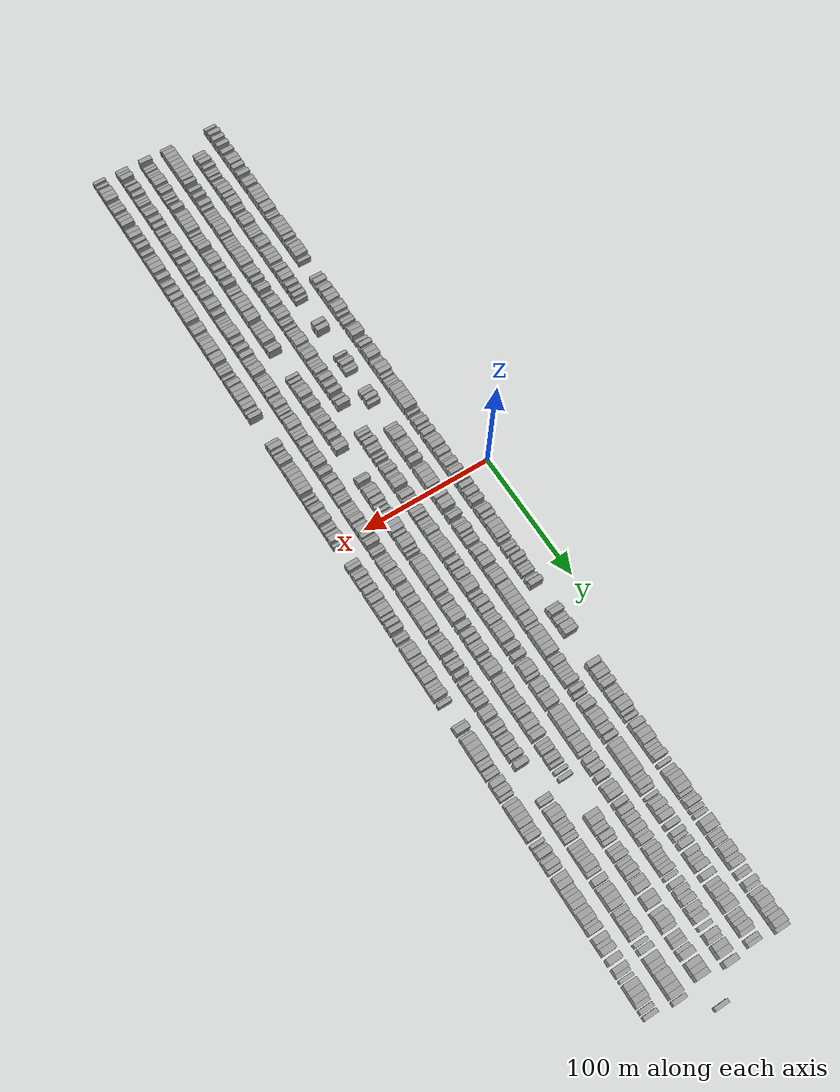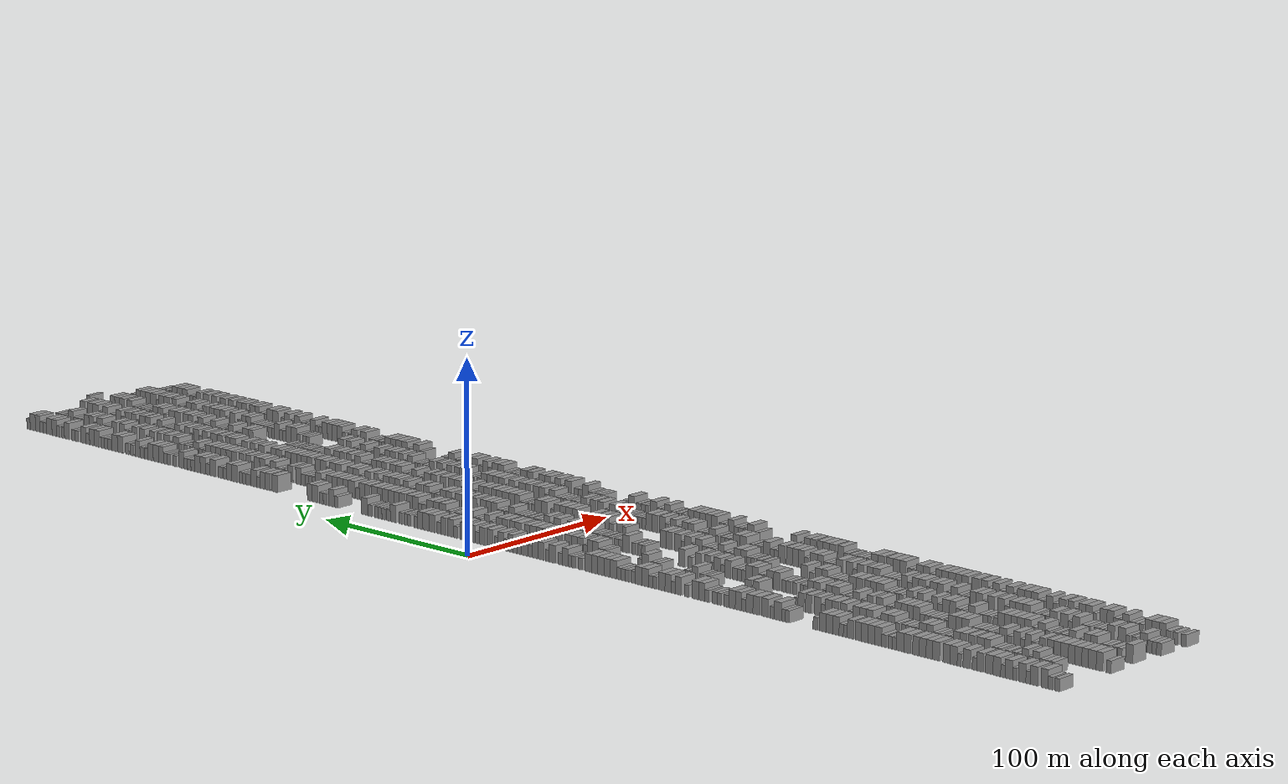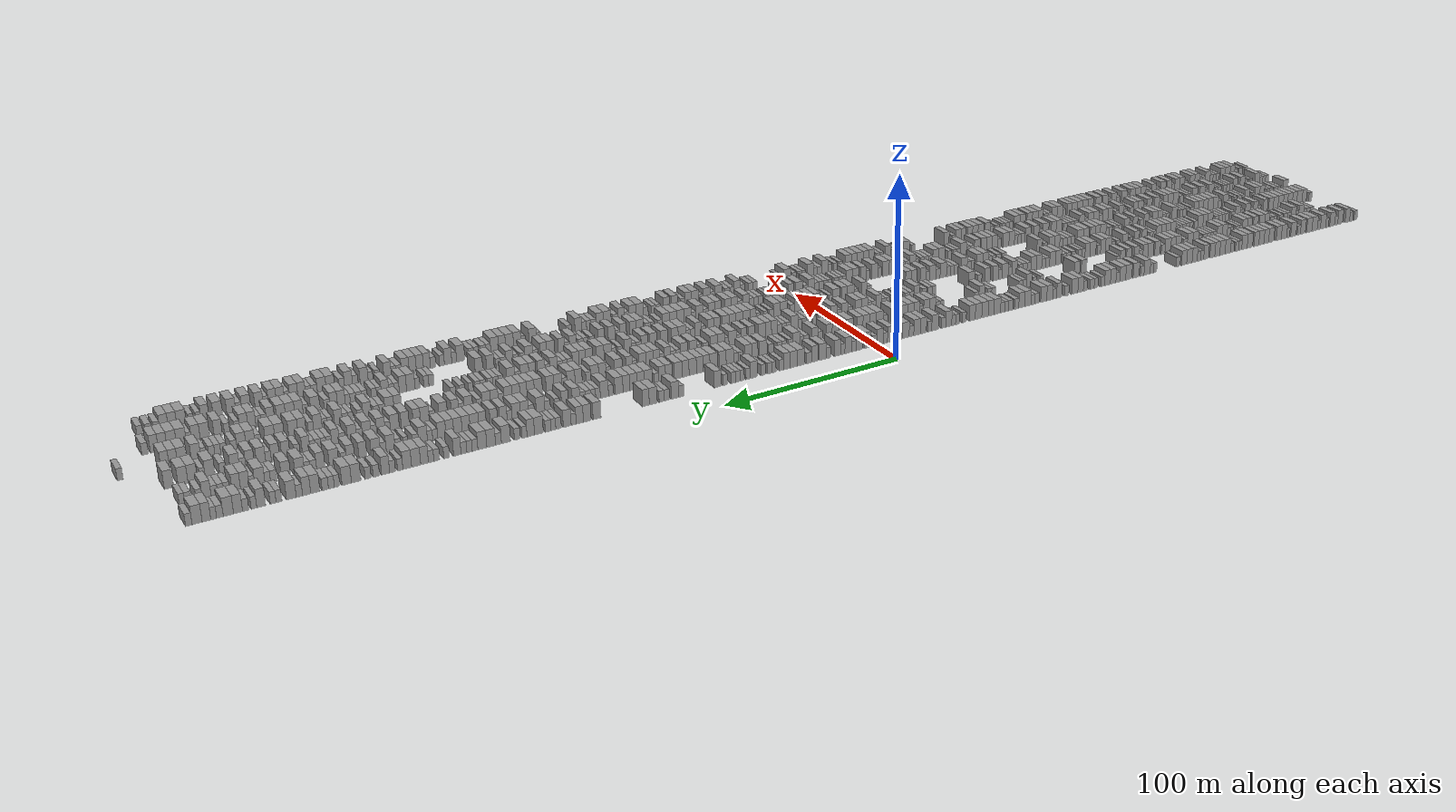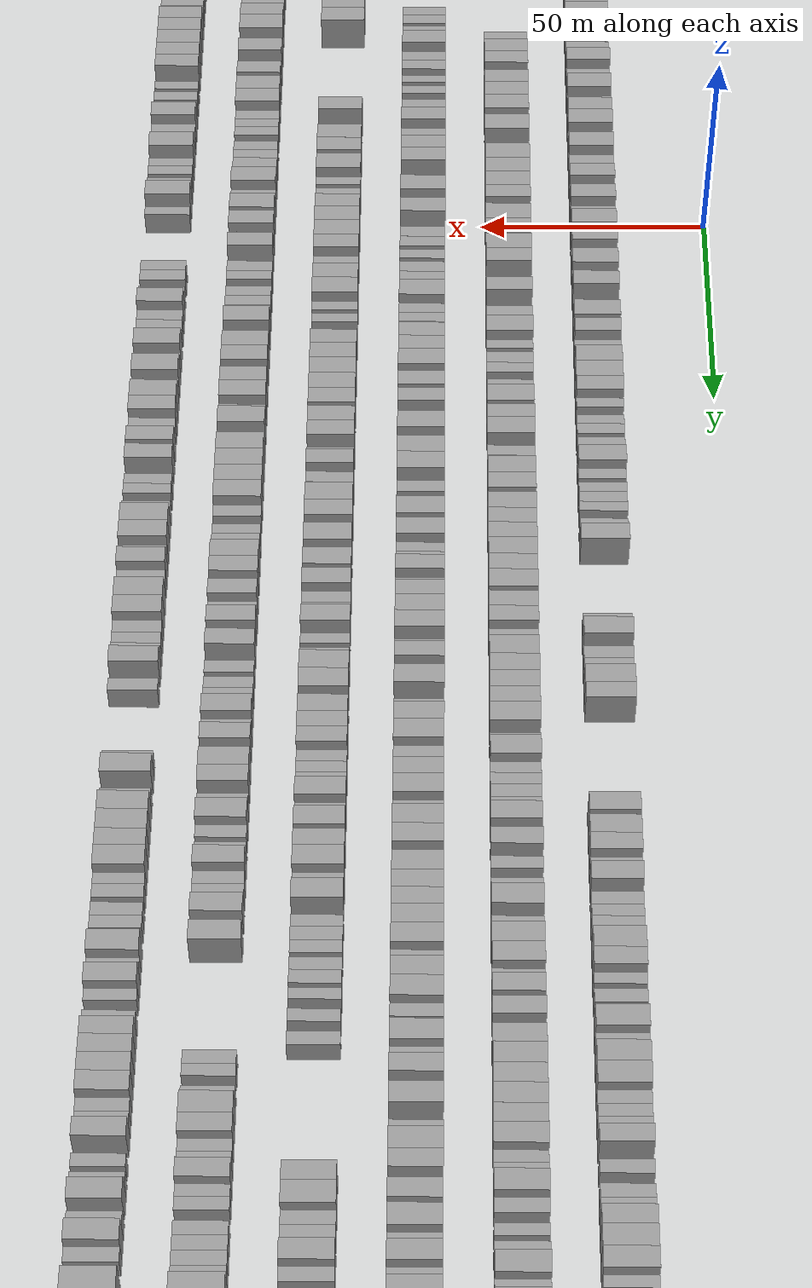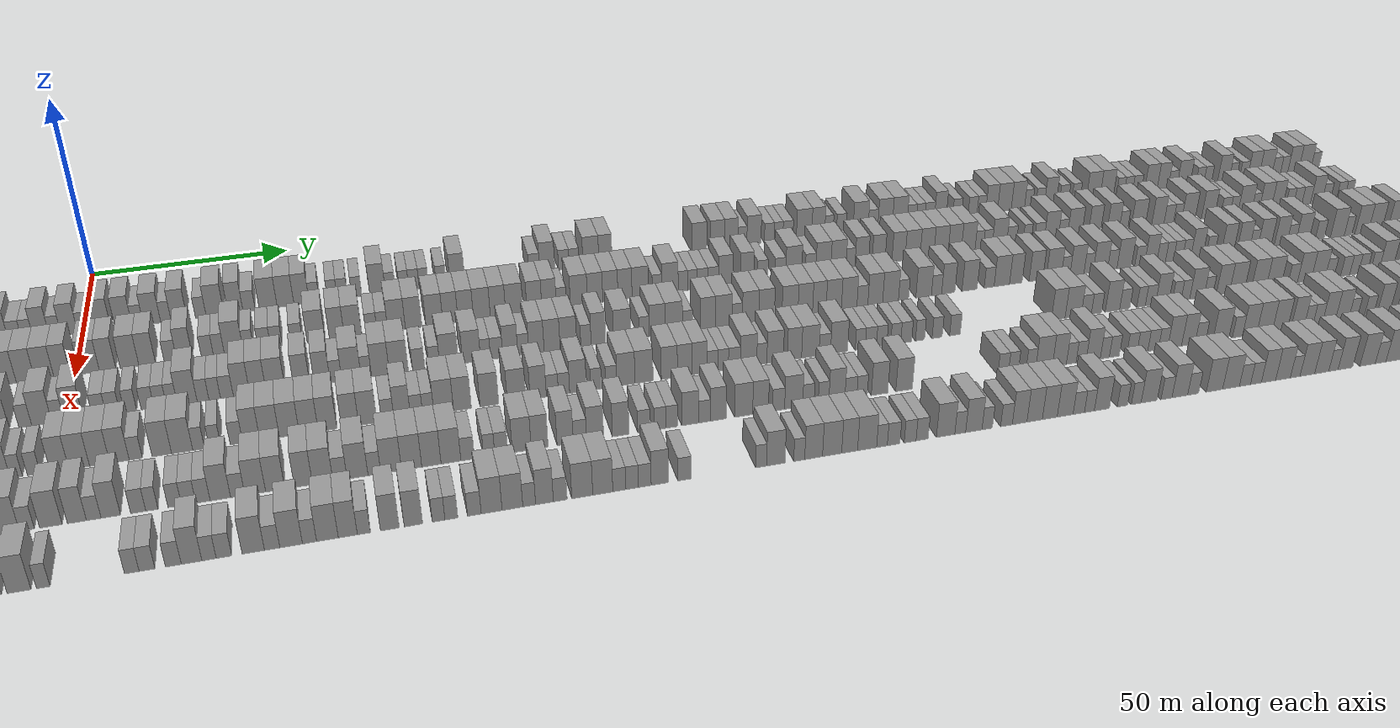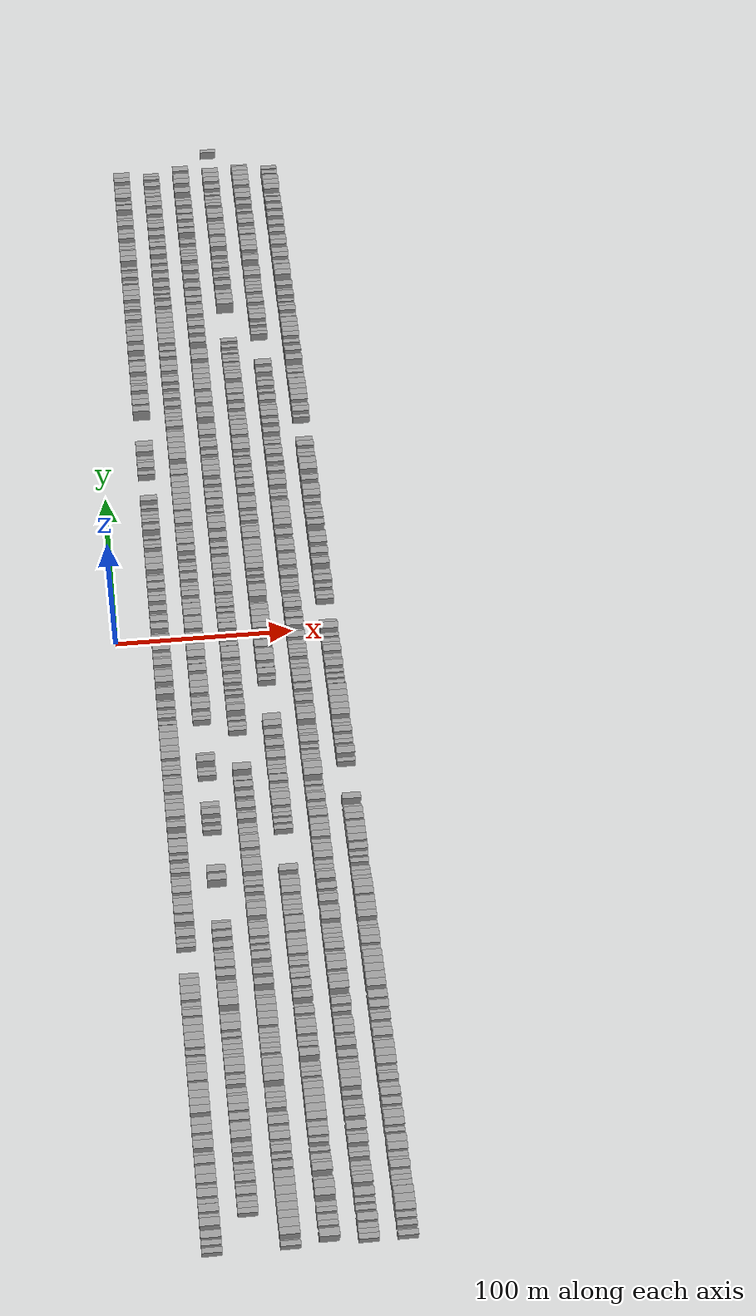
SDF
<sdf version="1.6">
 <world name="default">
  <scene>
   <sky><clouds><speed>12</speed></clouds></sky>
   <ambient>0.4 0.4 0.4 1</ambient>
   <background>0.7 0.7 0.7 1</background>
   <shadows>1</shadows>
  </scene>
  <gravity>0 0 -9.8066</gravity>
  <magnetic_field>6e-06 2.3e-05 -4.2e-05</magnetic_field>
  <physics default="0" name="default_physics" type="ode">
   <ode>
    <solver>
     <type>quick</type>
     <iters>10</iters>
     <sor>1.0</sor>
     <use_dynamic_moi_rescaling>0</use_dynamic_moi_rescaling>
    </solver>
    <constraints>
     <cfm>0</cfm>
     <erp>0.2</erp>
     <contact_max_correcting_vel>100</contact_max_correcting_vel>
     <contact_surface_layer>0.001</contact_surface_layer>
    </constraints>
   </ode>
   <max_step_size>0.004</max_step_size>
   <real_time_factor>1</real_time_factor>
   <real_time_update_rate>250</real_time_update_rate>
  </physics>
  <light name="sun" type="directional">
   <pose>0 0 10 0 0 0</pose>
   <diffuse>0.8 0.8 0.8 1</diffuse>
   <specular>0.2 0.2 0.2 1</specular>
   <attenuation>
    <range>1000</range>
    <constant>0.9</constant>
    <linear>0.01</linear>
    <quadratic>0.001</quadratic>
   </attenuation>
   <direction>-0.5 0.1 -0.9</direction>
  </light>
  <model name="building_1">
   <static>1</static>
   <pose>25.0000 -348.6272 0 0.000000 0.000000 0.000000</pose>
   <link name="link">
    <pose>0 0 3.00 0 0 0</pose>
    <collision name="collision"><geometry><box><size>10.0000 2.7456 6.0000</size></box></geometry></collision>
    <visual name="visual">
     <cast_shadows>0</cast_shadows>
     <geometry><box><size>10.0000 2.7456 6.0000</size></box></geometry>
     <material>
      <script>
       <uri>model://grey_wall/materials/scripts</uri>
       <uri>model://grey_wall/materials/textures</uri>
       <name>vrc/grey_wall</name>
      </script>
     </material>
    </visual>
   </link>
  </model>
  <model name="building_2">
   <static>1</static>
   <pose>25.0000 -344.8946 0 0.000000 0.000000 0.000000</pose>
   <link name="link">
    <pose>0 0 3.00 0 0 0</pose>
    <collision name="collision"><geometry><box><size>10.0000 2.7197 6.0000</size></box></geometry></collision>
    <visual name="visual">
     <cast_shadows>0</cast_shadows>
     <geometry><box><size>10.0000 2.7197 6.0000</size></box></geometry>
     <material>
      <script>
       <uri>model://grey_wall/materials/scripts</uri>
       <uri>model://grey_wall/materials/textures</uri>
       <name>vrc/grey_wall</name>
      </script>
     </material>
    </visual>
   </link>
  </model>
  <model name="building_3">
   <static>1</static>
   <pose>25.0000 -341.6259 0 0.000000 0.000000 0.000000</pose>
   <link name="link">
    <pose>0 0 4.50 0 0 0</pose>
    <collision name="collision"><geometry><box><size>10.0000 3.8177 9.0000</size></box></geometry></collision>
    <visual name="visual">
     <cast_shadows>0</cast_shadows>
     <geometry><box><size>10.0000 3.8177 9.0000</size></box></geometry>
     <material>
      <script>
       <uri>model://grey_wall/materials/scripts</uri>
       <uri>model://grey_wall/materials/textures</uri>
       <name>vrc/grey_wall</name>
      </script>
     </material>
    </visual>
   </link>
  </model>
  <model name="building_4">
   <static>1</static>
   <pose>25.0000 -335.6298 0 0.000000 0.000000 0.000000</pose>
   <link name="link">
    <pose>0 0 4.50 0 0 0</pose>
    <collision name="collision"><geometry><box><size>10.0000 4.1745 9.0000</size></box></geometry></collision>
    <visual name="visual">
     <cast_shadows>0</cast_shadows>
     <geometry><box><size>10.0000 4.1745 9.0000</size></box></geometry>
     <material>
      <script>
       <uri>model://grey_wall/materials/scripts</uri>
       <uri>model://grey_wall/materials/textures</uri>
       <name>vrc/grey_wall</name>
      </script>
     </material>
    </visual>
   </link>
  </model>
  <model name="building_5">
   <static>1</static>
   <pose>25.0000 -332.2178 0 0.000000 0.000000 0.000000</pose>
   <link name="link">
    <pose>0 0 3.00 0 0 0</pose>
    <collision name="collision"><geometry><box><size>10.0000 2.6495 6.0000</size></box></geometry></collision>
    <visual name="visual">
     <cast_shadows>0</cast_shadows>
     <geometry><box><size>10.0000 2.6495 6.0000</size></box></geometry>
     <material>
      <script>
       <uri>model://grey_wall/materials/scripts</uri>
       <uri>model://grey_wall/materials/textures</uri>
       <name>vrc/grey_wall</name>
      </script>
     </material>
    </visual>
   </link>
  </model>
  <model name="building_6">
   <static>1</static>
   <pose>25.0000 -328.8747 0 0.000000 0.000000 0.000000</pose>
   <link name="link">
    <pose>0 0 4.50 0 0 0</pose>
    <collision name="collision"><geometry><box><size>10.0000 4.0367 9.0000</size></box></geometry></collision>
    <visual name="visual">
     <cast_shadows>0</cast_shadows>
     <geometry><box><size>10.0000 4.0367 9.0000</size></box></geometry>
     <material>
      <script>
       <uri>model://grey_wall/materials/scripts</uri>
       <uri>model://grey_wall/materials/textures</uri>
       <name>vrc/grey_wall</name>
      </script>
     </material>
    </visual>
   </link>
  </model>
  <model name="building_7">
   <static>1</static>
   <pose>25.0000 -324.6240 0 0.000000 0.000000 0.000000</pose>
   <link name="link">
    <pose>0 0 3.00 0 0 0</pose>
    <collision name="collision"><geometry><box><size>10.0000 2.4647 6.0000</size></box></geometry></collision>
    <visual name="visual">
     <cast_shadows>0</cast_shadows>
     <geometry><box><size>10.0000 2.4647 6.0000</size></box></geometry>
     <material>
      <script>
       <uri>model://grey_wall/materials/scripts</uri>
       <uri>model://grey_wall/materials/textures</uri>
       <name>vrc/grey_wall</name>
      </script>
     </material>
    </visual>
   </link>
  </model>
  <model name="building_8">
   <static>1</static>
   <pose>25.0000 -321.2633 0 0.000000 0.000000 0.000000</pose>
   <link name="link">
    <pose>0 0 4.50 0 0 0</pose>
    <collision name="collision"><geometry><box><size>10.0000 4.2568 9.0000</size></box></geometry></collision>
    <visual name="visual">
     <cast_shadows>0</cast_shadows>
     <geometry><box><size>10.0000 4.2568 9.0000</size></box></geometry>
     <material>
      <script>
       <uri>model://grey_wall/materials/scripts</uri>
       <uri>model://grey_wall/materials/textures</uri>
       <name>vrc/grey_wall</name>
      </script>
     </material>
    </visual>
   </link>
  </model>
  <model name="building_9">
   <static>1</static>
   <pose>25.0000 -317.8178 0 0.000000 0.000000 0.000000</pose>
   <link name="link">
    <pose>0 0 3.00 0 0 0</pose>
    <collision name="collision"><geometry><box><size>10.0000 2.6341 6.0000</size></box></geometry></collision>
    <visual name="visual">
     <cast_shadows>0</cast_shadows>
     <geometry><box><size>10.0000 2.6341 6.0000</size></box></geometry>
     <material>
      <script>
       <uri>model://grey_wall/materials/scripts</uri>
       <uri>model://grey_wall/materials/textures</uri>
       <name>vrc/grey_wall</name>
      </script>
     </material>
    </visual>
   </link>
  </model>
  <model name="building_10">
   <static>1</static>
   <pose>25.0000 -314.2907 0 0.000000 0.000000 0.000000</pose>
   <link name="link">
    <pose>0 0 4.50 0 0 0</pose>
    <collision name="collision"><geometry><box><size>10.0000 4.4202 9.0000</size></box></geometry></collision>
    <visual name="visual">
     <cast_shadows>0</cast_shadows>
     <geometry><box><size>10.0000 4.4202 9.0000</size></box></geometry>
     <material>
      <script>
       <uri>model://grey_wall/materials/scripts</uri>
       <uri>model://grey_wall/materials/textures</uri>
       <name>vrc/grey_wall</name>
      </script>
     </material>
    </visual>
   </link>
  </model>
  <model name="building_11">
   <static>1</static>
   <pose>25.0000 -309.8835 0 0.000000 0.000000 0.000000</pose>
   <link name="link">
    <pose>0 0 4.50 0 0 0</pose>
    <collision name="collision"><geometry><box><size>10.0000 4.3942 9.0000</size></box></geometry></collision>
    <visual name="visual">
     <cast_shadows>0</cast_shadows>
     <geometry><box><size>10.0000 4.3942 9.0000</size></box></geometry>
     <material>
      <script>
       <uri>model://grey_wall/materials/scripts</uri>
       <uri>model://grey_wall/materials/textures</uri>
       <name>vrc/grey_wall</name>
      </script>
     </material>
    </visual>
   </link>
  </model>
  <model name="building_12">
   <static>1</static>
   <pose>25.0000 -304.6365 0 0.000000 0.000000 0.000000</pose>
   <link name="link">
    <pose>0 0 4.50 0 0 0</pose>
    <collision name="collision"><geometry><box><size>10.0000 4.0996 9.0000</size></box></geometry></collision>
    <visual name="visual">
     <cast_shadows>0</cast_shadows>
     <geometry><box><size>10.0000 4.0996 9.0000</size></box></geometry>
     <material>
      <script>
       <uri>model://grey_wall/materials/scripts</uri>
       <uri>model://grey_wall/materials/textures</uri>
       <name>vrc/grey_wall</name>
      </script>
     </material>
    </visual>
   </link>
  </model>
  <model name="building_13">
   <static>1</static>
   <pose>25.0000 -301.3277 0 0.000000 0.000000 0.000000</pose>
   <link name="link">
    <pose>0 0 3.00 0 0 0</pose>
    <collision name="collision"><geometry><box><size>10.0000 2.5180 6.0000</size></box></geometry></collision>
    <visual name="visual">
     <cast_shadows>0</cast_shadows>
     <geometry><box><size>10.0000 2.5180 6.0000</size></box></geometry>
     <material>
      <script>
       <uri>model://grey_wall/materials/scripts</uri>
       <uri>model://grey_wall/materials/textures</uri>
       <name>vrc/grey_wall</name>
      </script>
     </material>
    </visual>
   </link>
  </model>
  <model name="building_14">
   <static>1</static>
   <pose>25.0000 -296.8994 0 0.000000 0.000000 0.000000</pose>
   <link name="link">
    <pose>0 0 4.50 0 0 0</pose>
    <collision name="collision"><geometry><box><size>10.0000 4.3386 9.0000</size></box></geometry></collision>
    <visual name="visual">
     <cast_shadows>0</cast_shadows>
     <geometry><box><size>10.0000 4.3386 9.0000</size></box></geometry>
     <material>
      <script>
       <uri>model://grey_wall/materials/scripts</uri>
       <uri>model://grey_wall/materials/textures</uri>
       <name>vrc/grey_wall</name>
      </script>
     </material>
    </visual>
   </link>
  </model>
  <model name="building_15">
   <static>1</static>
   <pose>25.0000 -292.5284 0 0.000000 0.000000 0.000000</pose>
   <link name="link">
    <pose>0 0 3.00 0 0 0</pose>
    <collision name="collision"><geometry><box><size>10.0000 2.4034 6.0000</size></box></geometry></collision>
    <visual name="visual">
     <cast_shadows>0</cast_shadows>
     <geometry><box><size>10.0000 2.4034 6.0000</size></box></geometry>
     <material>
      <script>
       <uri>model://grey_wall/materials/scripts</uri>
       <uri>model://grey_wall/materials/textures</uri>
       <name>vrc/grey_wall</name>
      </script>
     </material>
    </visual>
   </link>
  </model>
  <model name="building_16">
   <static>1</static>
   <pose>25.0000 -289.1631 0 0.000000 0.000000 0.000000</pose>
   <link name="link">
    <pose>0 0 4.50 0 0 0</pose>
    <collision name="collision"><geometry><box><size>10.0000 4.3271 9.0000</size></box></geometry></collision>
    <visual name="visual">
     <cast_shadows>0</cast_shadows>
     <geometry><box><size>10.0000 4.3271 9.0000</size></box></geometry>
     <material>
      <script>
       <uri>model://grey_wall/materials/scripts</uri>
       <uri>model://grey_wall/materials/textures</uri>
       <name>vrc/grey_wall</name>
      </script>
     </material>
    </visual>
   </link>
  </model>
  <model name="building_17">
   <static>1</static>
   <pose>25.0000 -285.0205 0 0.000000 0.000000 0.000000</pose>
   <link name="link">
    <pose>0 0 4.50 0 0 0</pose>
    <collision name="collision"><geometry><box><size>10.0000 3.9582 9.0000</size></box></geometry></collision>
    <visual name="visual">
     <cast_shadows>0</cast_shadows>
     <geometry><box><size>10.0000 3.9582 9.0000</size></box></geometry>
     <material>
      <script>
       <uri>model://grey_wall/materials/scripts</uri>
       <uri>model://grey_wall/materials/textures</uri>
       <name>vrc/grey_wall</name>
      </script>
     </material>
    </visual>
   </link>
  </model>
  <model name="building_18">
   <static>1</static>
   <pose>25.0000 -278.9540 0 0.000000 0.000000 0.000000</pose>
   <link name="link">
    <pose>0 0 4.50 0 0 0</pose>
    <collision name="collision"><geometry><box><size>10.0000 4.1747 9.0000</size></box></geometry></collision>
    <visual name="visual">
     <cast_shadows>0</cast_shadows>
     <geometry><box><size>10.0000 4.1747 9.0000</size></box></geometry>
     <material>
      <script>
       <uri>model://grey_wall/materials/scripts</uri>
       <uri>model://grey_wall/materials/textures</uri>
       <name>vrc/grey_wall</name>
      </script>
     </material>
    </visual>
   </link>
  </model>
  <model name="building_19">
   <static>1</static>
   <pose>25.0000 -274.9797 0 0.000000 0.000000 0.000000</pose>
   <link name="link">
    <pose>0 0 4.50 0 0 0</pose>
    <collision name="collision"><geometry><box><size>10.0000 3.7740 9.0000</size></box></geometry></collision>
    <visual name="visual">
     <cast_shadows>0</cast_shadows>
     <geometry><box><size>10.0000 3.7740 9.0000</size></box></geometry>
     <material>
      <script>
       <uri>model://grey_wall/materials/scripts</uri>
       <uri>model://grey_wall/materials/textures</uri>
       <name>vrc/grey_wall</name>
      </script>
     </material>
    </visual>
   </link>
  </model>
  <model name="building_20">
   <static>1</static>
   <pose>25.0000 -271.0950 0 0.000000 0.000000 0.000000</pose>
   <link name="link">
    <pose>0 0 4.50 0 0 0</pose>
    <collision name="collision"><geometry><box><size>10.0000 3.9955 9.0000</size></box></geometry></collision>
    <visual name="visual">
     <cast_shadows>0</cast_shadows>
     <geometry><box><size>10.0000 3.9955 9.0000</size></box></geometry>
     <material>
      <script>
       <uri>model://grey_wall/materials/scripts</uri>
       <uri>model://grey_wall/materials/textures</uri>
       <name>vrc/grey_wall</name>
      </script>
     </material>
    </visual>
   </link>
  </model>
  <model name="building_21">
   <static>1</static>
   <pose>25.0000 -267.1326 0 0.000000 0.000000 0.000000</pose>
   <link name="link">
    <pose>0 0 4.50 0 0 0</pose>
    <collision name="collision"><geometry><box><size>10.0000 3.9292 9.0000</size></box></geometry></collision>
    <visual name="visual">
     <cast_shadows>0</cast_shadows>
     <geometry><box><size>10.0000 3.9292 9.0000</size></box></geometry>
     <material>
      <script>
       <uri>model://grey_wall/materials/scripts</uri>
       <uri>model://grey_wall/materials/textures</uri>
       <name>vrc/grey_wall</name>
      </script>
     </material>
    </visual>
   </link>
  </model>
  <model name="building_22">
   <static>1</static>
   <pose>25.0000 -262.0338 0 0.000000 0.000000 0.000000</pose>
   <link name="link">
    <pose>0 0 4.50 0 0 0</pose>
    <collision name="collision"><geometry><box><size>10.0000 4.2683 9.0000</size></box></geometry></collision>
    <visual name="visual">
     <cast_shadows>0</cast_shadows>
     <geometry><box><size>10.0000 4.2683 9.0000</size></box></geometry>
     <material>
      <script>
       <uri>model://grey_wall/materials/scripts</uri>
       <uri>model://grey_wall/materials/textures</uri>
       <name>vrc/grey_wall</name>
      </script>
     </material>
    </visual>
   </link>
  </model>
  <model name="building_23">
   <static>1</static>
   <pose>25.0000 -257.7284 0 0.000000 0.000000 0.000000</pose>
   <link name="link">
    <pose>0 0 4.50 0 0 0</pose>
    <collision name="collision"><geometry><box><size>10.0000 4.3424 9.0000</size></box></geometry></collision>
    <visual name="visual">
     <cast_shadows>0</cast_shadows>
     <geometry><box><size>10.0000 4.3424 9.0000</size></box></geometry>
     <material>
      <script>
       <uri>model://grey_wall/materials/scripts</uri>
       <uri>model://grey_wall/materials/textures</uri>
       <name>vrc/grey_wall</name>
      </script>
     </material>
    </visual>
   </link>
  </model>
  <model name="building_24">
   <static>1</static>
   <pose>25.0000 -254.3505 0 0.000000 0.000000 0.000000</pose>
   <link name="link">
    <pose>0 0 3.00 0 0 0</pose>
    <collision name="collision"><geometry><box><size>10.0000 2.4134 6.0000</size></box></geometry></collision>
    <visual name="visual">
     <cast_shadows>0</cast_shadows>
     <geometry><box><size>10.0000 2.4134 6.0000</size></box></geometry>
     <material>
      <script>
       <uri>model://grey_wall/materials/scripts</uri>
       <uri>model://grey_wall/materials/textures</uri>
       <name>vrc/grey_wall</name>
      </script>
     </material>
    </visual>
   </link>
  </model>
  <model name="building_25">
   <static>1</static>
   <pose>25.0000 -251.8297 0 0.000000 0.000000 0.000000</pose>
   <link name="link">
    <pose>0 0 3.00 0 0 0</pose>
    <collision name="collision"><geometry><box><size>10.0000 2.6281 6.0000</size></box></geometry></collision>
    <visual name="visual">
     <cast_shadows>0</cast_shadows>
     <geometry><box><size>10.0000 2.6281 6.0000</size></box></geometry>
     <material>
      <script>
       <uri>model://grey_wall/materials/scripts</uri>
       <uri>model://grey_wall/materials/textures</uri>
       <name>vrc/grey_wall</name>
      </script>
     </material>
    </visual>
   </link>
  </model>
  <model name="building_26">
   <static>1</static>
   <pose>25.0000 -248.1227 0 0.000000 0.000000 0.000000</pose>
   <link name="link">
    <pose>0 0 3.00 0 0 0</pose>
    <collision name="collision"><geometry><box><size>10.0000 2.7859 6.0000</size></box></geometry></collision>
    <visual name="visual">
     <cast_shadows>0</cast_shadows>
     <geometry><box><size>10.0000 2.7859 6.0000</size></box></geometry>
     <material>
      <script>
       <uri>model://grey_wall/materials/scripts</uri>
       <uri>model://grey_wall/materials/textures</uri>
       <name>vrc/grey_wall</name>
      </script>
     </material>
    </visual>
   </link>
  </model>
  <model name="building_27">
   <static>1</static>
   <pose>25.0000 -244.6380 0 0.000000 0.000000 0.000000</pose>
   <link name="link">
    <pose>0 0 4.50 0 0 0</pose>
    <collision name="collision"><geometry><box><size>10.0000 4.1835 9.0000</size></box></geometry></collision>
    <visual name="visual">
     <cast_shadows>0</cast_shadows>
     <geometry><box><size>10.0000 4.1835 9.0000</size></box></geometry>
     <material>
      <script>
       <uri>model://grey_wall/materials/scripts</uri>
       <uri>model://grey_wall/materials/textures</uri>
       <name>vrc/grey_wall</name>
      </script>
     </material>
    </visual>
   </link>
  </model>
  <model name="building_28">
   <static>1</static>
   <pose>25.0000 -240.4660 0 0.000000 0.000000 0.000000</pose>
   <link name="link">
    <pose>0 0 4.50 0 0 0</pose>
    <collision name="collision"><geometry><box><size>10.0000 4.1604 9.0000</size></box></geometry></collision>
    <visual name="visual">
     <cast_shadows>0</cast_shadows>
     <geometry><box><size>10.0000 4.1604 9.0000</size></box></geometry>
     <material>
      <script>
       <uri>model://grey_wall/materials/scripts</uri>
       <uri>model://grey_wall/materials/textures</uri>
       <name>vrc/grey_wall</name>
      </script>
     </material>
    </visual>
   </link>
  </model>
  <model name="building_29">
   <static>1</static>
   <pose>25.0000 -236.5070 0 0.000000 0.000000 0.000000</pose>
   <link name="link">
    <pose>0 0 4.50 0 0 0</pose>
    <collision name="collision"><geometry><box><size>10.0000 3.7574 9.0000</size></box></geometry></collision>
    <visual name="visual">
     <cast_shadows>0</cast_shadows>
     <geometry><box><size>10.0000 3.7574 9.0000</size></box></geometry>
     <material>
      <script>
       <uri>model://grey_wall/materials/scripts</uri>
       <uri>model://grey_wall/materials/textures</uri>
       <name>vrc/grey_wall</name>
      </script>
     </material>
    </visual>
   </link>
  </model>
  <model name="building_30">
   <static>1</static>
   <pose>25.0000 -232.7112 0 0.000000 0.000000 0.000000</pose>
   <link name="link">
    <pose>0 0 4.50 0 0 0</pose>
    <collision name="collision"><geometry><box><size>10.0000 3.8343 9.0000</size></box></geometry></collision>
    <visual name="visual">
     <cast_shadows>0</cast_shadows>
     <geometry><box><size>10.0000 3.8343 9.0000</size></box></geometry>
     <material>
      <script>
       <uri>model://grey_wall/materials/scripts</uri>
       <uri>model://grey_wall/materials/textures</uri>
       <name>vrc/grey_wall</name>
      </script>
     </material>
    </visual>
   </link>
  </model>
  <model name="building_31">
   <static>1</static>
   <pose>25.0000 -227.9371 0 0.000000 0.000000 0.000000</pose>
   <link name="link">
    <pose>0 0 4.50 0 0 0</pose>
    <collision name="collision"><geometry><box><size>10.0000 3.7139 9.0000</size></box></geometry></collision>
    <visual name="visual">
     <cast_shadows>0</cast_shadows>
     <geometry><box><size>10.0000 3.7139 9.0000</size></box></geometry>
     <material>
      <script>
       <uri>model://grey_wall/materials/scripts</uri>
       <uri>model://grey_wall/materials/textures</uri>
       <name>vrc/grey_wall</name>
      </script>
     </material>
    </visual>
   </link>
  </model>
  <model name="building_32">
   <static>1</static>
   <pose>25.0000 -224.8597 0 0.000000 0.000000 0.000000</pose>
   <link name="link">
    <pose>0 0 3.00 0 0 0</pose>
    <collision name="collision"><geometry><box><size>10.0000 2.4409 6.0000</size></box></geometry></collision>
    <visual name="visual">
     <cast_shadows>0</cast_shadows>
     <geometry><box><size>10.0000 2.4409 6.0000</size></box></geometry>
     <material>
      <script>
       <uri>model://grey_wall/materials/scripts</uri>
       <uri>model://grey_wall/materials/textures</uri>
       <name>vrc/grey_wall</name>
      </script>
     </material>
    </visual>
   </link>
  </model>
  <model name="building_33">
   <static>1</static>
   <pose>25.0000 -222.3539 0 0.000000 0.000000 0.000000</pose>
   <link name="link">
    <pose>0 0 3.00 0 0 0</pose>
    <collision name="collision"><geometry><box><size>10.0000 2.5705 6.0000</size></box></geometry></collision>
    <visual name="visual">
     <cast_shadows>0</cast_shadows>
     <geometry><box><size>10.0000 2.5705 6.0000</size></box></geometry>
     <material>
      <script>
       <uri>model://grey_wall/materials/scripts</uri>
       <uri>model://grey_wall/materials/textures</uri>
       <name>vrc/grey_wall</name>
      </script>
     </material>
    </visual>
   </link>
  </model>
  <model name="building_34">
   <static>1</static>
   <pose>25.0000 -219.1859 0 0.000000 0.000000 0.000000</pose>
   <link name="link">
    <pose>0 0 4.50 0 0 0</pose>
    <collision name="collision"><geometry><box><size>10.0000 3.7655 9.0000</size></box></geometry></collision>
    <visual name="visual">
     <cast_shadows>0</cast_shadows>
     <geometry><box><size>10.0000 3.7655 9.0000</size></box></geometry>
     <material>
      <script>
       <uri>model://grey_wall/materials/scripts</uri>
       <uri>model://grey_wall/materials/textures</uri>
       <name>vrc/grey_wall</name>
      </script>
     </material>
    </visual>
   </link>
  </model>
  <model name="building_35">
   <static>1</static>
   <pose>25.0000 -215.2183 0 0.000000 0.000000 0.000000</pose>
   <link name="link">
    <pose>0 0 4.50 0 0 0</pose>
    <collision name="collision"><geometry><box><size>10.0000 4.1696 9.0000</size></box></geometry></collision>
    <visual name="visual">
     <cast_shadows>0</cast_shadows>
     <geometry><box><size>10.0000 4.1696 9.0000</size></box></geometry>
     <material>
      <script>
       <uri>model://grey_wall/materials/scripts</uri>
       <uri>model://grey_wall/materials/textures</uri>
       <name>vrc/grey_wall</name>
      </script>
     </material>
    </visual>
   </link>
  </model>
  <model name="building_36">
   <static>1</static>
   <pose>25.0000 -211.1548 0 0.000000 0.000000 0.000000</pose>
   <link name="link">
    <pose>0 0 4.50 0 0 0</pose>
    <collision name="collision"><geometry><box><size>10.0000 3.9575 9.0000</size></box></geometry></collision>
    <visual name="visual">
     <cast_shadows>0</cast_shadows>
     <geometry><box><size>10.0000 3.9575 9.0000</size></box></geometry>
     <material>
      <script>
       <uri>model://grey_wall/materials/scripts</uri>
       <uri>model://grey_wall/materials/textures</uri>
       <name>vrc/grey_wall</name>
      </script>
     </material>
    </visual>
   </link>
  </model>
  <model name="building_37">
   <static>1</static>
   <pose>25.0000 -206.7045 0 0.000000 0.000000 0.000000</pose>
   <link name="link">
    <pose>0 0 3.00 0 0 0</pose>
    <collision name="collision"><geometry><box><size>10.0000 2.9430 6.0000</size></box></geometry></collision>
    <visual name="visual">
     <cast_shadows>0</cast_shadows>
     <geometry><box><size>10.0000 2.9430 6.0000</size></box></geometry>
     <material>
      <script>
       <uri>model://grey_wall/materials/scripts</uri>
       <uri>model://grey_wall/materials/textures</uri>
       <name>vrc/grey_wall</name>
      </script>
     </material>
    </visual>
   </link>
  </model>
  <model name="building_38">
   <static>1</static>
   <pose>25.0000 -189.4666 0 0.000000 0.000000 0.000000</pose>
   <link name="link">
    <pose>0 0 3.00 0 0 0</pose>
    <collision name="collision"><geometry><box><size>10.0000 2.5109 6.0000</size></box></geometry></collision>
    <visual name="visual">
     <cast_shadows>0</cast_shadows>
     <geometry><box><size>10.0000 2.5109 6.0000</size></box></geometry>
     <material>
      <script>
       <uri>model://grey_wall/materials/scripts</uri>
       <uri>model://grey_wall/materials/textures</uri>
       <name>vrc/grey_wall</name>
      </script>
     </material>
    </visual>
   </link>
  </model>
  <model name="building_39">
   <static>1</static>
   <pose>25.0000 -187.0037 0 0.000000 0.000000 0.000000</pose>
   <link name="link">
    <pose>0 0 3.00 0 0 0</pose>
    <collision name="collision"><geometry><box><size>10.0000 2.4149 6.0000</size></box></geometry></collision>
    <visual name="visual">
     <cast_shadows>0</cast_shadows>
     <geometry><box><size>10.0000 2.4149 6.0000</size></box></geometry>
     <material>
      <script>
       <uri>model://grey_wall/materials/scripts</uri>
       <uri>model://grey_wall/materials/textures</uri>
       <name>vrc/grey_wall</name>
      </script>
     </material>
    </visual>
   </link>
  </model>
  <model name="building_40">
   <static>1</static>
   <pose>25.0000 -183.5904 0 0.000000 0.000000 0.000000</pose>
   <link name="link">
    <pose>0 0 4.50 0 0 0</pose>
    <collision name="collision"><geometry><box><size>10.0000 4.4115 9.0000</size></box></geometry></collision>
    <visual name="visual">
     <cast_shadows>0</cast_shadows>
     <geometry><box><size>10.0000 4.4115 9.0000</size></box></geometry>
     <material>
      <script>
       <uri>model://grey_wall/materials/scripts</uri>
       <uri>model://grey_wall/materials/textures</uri>
       <name>vrc/grey_wall</name>
      </script>
     </material>
    </visual>
   </link>
  </model>
  <model name="building_41">
   <static>1</static>
   <pose>25.0000 -180.0498 0 0.000000 0.000000 0.000000</pose>
   <link name="link">
    <pose>0 0 3.00 0 0 0</pose>
    <collision name="collision"><geometry><box><size>10.0000 2.6697 6.0000</size></box></geometry></collision>
    <visual name="visual">
     <cast_shadows>0</cast_shadows>
     <geometry><box><size>10.0000 2.6697 6.0000</size></box></geometry>
     <material>
      <script>
       <uri>model://grey_wall/materials/scripts</uri>
       <uri>model://grey_wall/materials/textures</uri>
       <name>vrc/grey_wall</name>
      </script>
     </material>
    </visual>
   </link>
  </model>
  <model name="building_42">
   <static>1</static>
   <pose>25.0000 -175.5593 0 0.000000 0.000000 0.000000</pose>
   <link name="link">
    <pose>0 0 4.50 0 0 0</pose>
    <collision name="collision"><geometry><box><size>10.0000 4.3114 9.0000</size></box></geometry></collision>
    <visual name="visual">
     <cast_shadows>0</cast_shadows>
     <geometry><box><size>10.0000 4.3114 9.0000</size></box></geometry>
     <material>
      <script>
       <uri>model://grey_wall/materials/scripts</uri>
       <uri>model://grey_wall/materials/textures</uri>
       <name>vrc/grey_wall</name>
      </script>
     </material>
    </visual>
   </link>
  </model>
  <model name="building_43">
   <static>1</static>
   <pose>25.0000 -170.1686 0 0.000000 0.000000 0.000000</pose>
   <link name="link">
    <pose>0 0 4.50 0 0 0</pose>
    <collision name="collision"><geometry><box><size>10.0000 4.4700 9.0000</size></box></geometry></collision>
    <visual name="visual">
     <cast_shadows>0</cast_shadows>
     <geometry><box><size>10.0000 4.4700 9.0000</size></box></geometry>
     <material>
      <script>
       <uri>model://grey_wall/materials/scripts</uri>
       <uri>model://grey_wall/materials/textures</uri>
       <name>vrc/grey_wall</name>
      </script>
     </material>
    </visual>
   </link>
  </model>
  <model name="building_44">
   <static>1</static>
   <pose>25.0000 -165.8126 0 0.000000 0.000000 0.000000</pose>
   <link name="link">
    <pose>0 0 4.50 0 0 0</pose>
    <collision name="collision"><geometry><box><size>10.0000 4.2421 9.0000</size></box></geometry></collision>
    <visual name="visual">
     <cast_shadows>0</cast_shadows>
     <geometry><box><size>10.0000 4.2421 9.0000</size></box></geometry>
     <material>
      <script>
       <uri>model://grey_wall/materials/scripts</uri>
       <uri>model://grey_wall/materials/textures</uri>
       <name>vrc/grey_wall</name>
      </script>
     </material>
    </visual>
   </link>
  </model>
  <model name="building_45">
   <static>1</static>
   <pose>25.0000 -162.2999 0 0.000000 0.000000 0.000000</pose>
   <link name="link">
    <pose>0 0 3.00 0 0 0</pose>
    <collision name="collision"><geometry><box><size>10.0000 2.7833 6.0000</size></box></geometry></collision>
    <visual name="visual">
     <cast_shadows>0</cast_shadows>
     <geometry><box><size>10.0000 2.7833 6.0000</size></box></geometry>
     <material>
      <script>
       <uri>model://grey_wall/materials/scripts</uri>
       <uri>model://grey_wall/materials/textures</uri>
       <name>vrc/grey_wall</name>
      </script>
     </material>
    </visual>
   </link>
  </model>
  <model name="building_46">
   <static>1</static>
   <pose>25.0000 -158.9069 0 0.000000 0.000000 0.000000</pose>
   <link name="link">
    <pose>0 0 4.50 0 0 0</pose>
    <collision name="collision"><geometry><box><size>10.0000 4.0026 9.0000</size></box></geometry></collision>
    <visual name="visual">
     <cast_shadows>0</cast_shadows>
     <geometry><box><size>10.0000 4.0026 9.0000</size></box></geometry>
     <material>
      <script>
       <uri>model://grey_wall/materials/scripts</uri>
       <uri>model://grey_wall/materials/textures</uri>
       <name>vrc/grey_wall</name>
      </script>
     </material>
    </visual>
   </link>
  </model>
  <model name="building_47">
   <static>1</static>
   <pose>25.0000 -154.8127 0 0.000000 0.000000 0.000000</pose>
   <link name="link">
    <pose>0 0 4.50 0 0 0</pose>
    <collision name="collision"><geometry><box><size>10.0000 4.1857 9.0000</size></box></geometry></collision>
    <visual name="visual">
     <cast_shadows>0</cast_shadows>
     <geometry><box><size>10.0000 4.1857 9.0000</size></box></geometry>
     <material>
      <script>
       <uri>model://grey_wall/materials/scripts</uri>
       <uri>model://grey_wall/materials/textures</uri>
       <name>vrc/grey_wall</name>
      </script>
     </material>
    </visual>
   </link>
  </model>
  <model name="building_48">
   <static>1</static>
   <pose>25.0000 -151.3458 0 0.000000 0.000000 0.000000</pose>
   <link name="link">
    <pose>0 0 3.00 0 0 0</pose>
    <collision name="collision"><geometry><box><size>10.0000 2.7481 6.0000</size></box></geometry></collision>
    <visual name="visual">
     <cast_shadows>0</cast_shadows>
     <geometry><box><size>10.0000 2.7481 6.0000</size></box></geometry>
     <material>
      <script>
       <uri>model://grey_wall/materials/scripts</uri>
       <uri>model://grey_wall/materials/textures</uri>
       <name>vrc/grey_wall</name>
      </script>
     </material>
    </visual>
   </link>
  </model>
  <model name="building_49">
   <static>1</static>
   <pose>25.0000 -146.6319 0 0.000000 0.000000 0.000000</pose>
   <link name="link">
    <pose>0 0 3.00 0 0 0</pose>
    <collision name="collision"><geometry><box><size>10.0000 2.6798 6.0000</size></box></geometry></collision>
    <visual name="visual">
     <cast_shadows>0</cast_shadows>
     <geometry><box><size>10.0000 2.6798 6.0000</size></box></geometry>
     <material>
      <script>
       <uri>model://grey_wall/materials/scripts</uri>
       <uri>model://grey_wall/materials/textures</uri>
       <name>vrc/grey_wall</name>
      </script>
     </material>
    </visual>
   </link>
  </model>
  <model name="building_50">
   <static>1</static>
   <pose>25.0000 -143.8004 0 0.000000 0.000000 0.000000</pose>
   <link name="link">
    <pose>0 0 3.00 0 0 0</pose>
    <collision name="collision"><geometry><box><size>10.0000 2.9833 6.0000</size></box></geometry></collision>
    <visual name="visual">
     <cast_shadows>0</cast_shadows>
     <geometry><box><size>10.0000 2.9833 6.0000</size></box></geometry>
     <material>
      <script>
       <uri>model://grey_wall/materials/scripts</uri>
       <uri>model://grey_wall/materials/textures</uri>
       <name>vrc/grey_wall</name>
      </script>
     </material>
    </visual>
   </link>
  </model>
  <model name="building_51">
   <static>1</static>
   <pose>25.0000 -138.9763 0 0.000000 0.000000 0.000000</pose>
   <link name="link">
    <pose>0 0 3.00 0 0 0</pose>
    <collision name="collision"><geometry><box><size>10.0000 2.6649 6.0000</size></box></geometry></collision>
    <visual name="visual">
     <cast_shadows>0</cast_shadows>
     <geometry><box><size>10.0000 2.6649 6.0000</size></box></geometry>
     <material>
      <script>
       <uri>model://grey_wall/materials/scripts</uri>
       <uri>model://grey_wall/materials/textures</uri>
       <name>vrc/grey_wall</name>
      </script>
     </material>
    </visual>
   </link>
  </model>
  <model name="building_52">
   <static>1</static>
   <pose>25.0000 -135.7152 0 0.000000 0.000000 0.000000</pose>
   <link name="link">
    <pose>0 0 4.50 0 0 0</pose>
    <collision name="collision"><geometry><box><size>10.0000 3.8572 9.0000</size></box></geometry></collision>
    <visual name="visual">
     <cast_shadows>0</cast_shadows>
     <geometry><box><size>10.0000 3.8572 9.0000</size></box></geometry>
     <material>
      <script>
       <uri>model://grey_wall/materials/scripts</uri>
       <uri>model://grey_wall/materials/textures</uri>
       <name>vrc/grey_wall</name>
      </script>
     </material>
    </visual>
   </link>
  </model>
  <model name="building_53">
   <static>1</static>
   <pose>25.0000 -131.5983 0 0.000000 0.000000 0.000000</pose>
   <link name="link">
    <pose>0 0 4.50 0 0 0</pose>
    <collision name="collision"><geometry><box><size>10.0000 4.3767 9.0000</size></box></geometry></collision>
    <visual name="visual">
     <cast_shadows>0</cast_shadows>
     <geometry><box><size>10.0000 4.3767 9.0000</size></box></geometry>
     <material>
      <script>
       <uri>model://grey_wall/materials/scripts</uri>
       <uri>model://grey_wall/materials/textures</uri>
       <name>vrc/grey_wall</name>
      </script>
     </material>
    </visual>
   </link>
  </model>
  <model name="building_54">
   <static>1</static>
   <pose>25.0000 -125.9597 0 0.000000 0.000000 0.000000</pose>
   <link name="link">
    <pose>0 0 3.00 0 0 0</pose>
    <collision name="collision"><geometry><box><size>10.0000 2.9005 6.0000</size></box></geometry></collision>
    <visual name="visual">
     <cast_shadows>0</cast_shadows>
     <geometry><box><size>10.0000 2.9005 6.0000</size></box></geometry>
     <material>
      <script>
       <uri>model://grey_wall/materials/scripts</uri>
       <uri>model://grey_wall/materials/textures</uri>
       <name>vrc/grey_wall</name>
      </script>
     </material>
    </visual>
   </link>
  </model>
  <model name="building_55">
   <static>1</static>
   <pose>25.0000 -120.7064 0 0.000000 0.000000 0.000000</pose>
   <link name="link">
    <pose>0 0 4.50 0 0 0</pose>
    <collision name="collision"><geometry><box><size>10.0000 3.6061 9.0000</size></box></geometry></collision>
    <visual name="visual">
     <cast_shadows>0</cast_shadows>
     <geometry><box><size>10.0000 3.6061 9.0000</size></box></geometry>
     <material>
      <script>
       <uri>model://grey_wall/materials/scripts</uri>
       <uri>model://grey_wall/materials/textures</uri>
       <name>vrc/grey_wall</name>
      </script>
     </material>
    </visual>
   </link>
  </model>
  <model name="building_56">
   <static>1</static>
   <pose>25.0000 -117.5425 0 0.000000 0.000000 0.000000</pose>
   <link name="link">
    <pose>0 0 3.00 0 0 0</pose>
    <collision name="collision"><geometry><box><size>10.0000 2.7217 6.0000</size></box></geometry></collision>
    <visual name="visual">
     <cast_shadows>0</cast_shadows>
     <geometry><box><size>10.0000 2.7217 6.0000</size></box></geometry>
     <material>
      <script>
       <uri>model://grey_wall/materials/scripts</uri>
       <uri>model://grey_wall/materials/textures</uri>
       <name>vrc/grey_wall</name>
      </script>
     </material>
    </visual>
   </link>
  </model>
  <model name="building_57">
   <static>1</static>
   <pose>25.0000 -114.1251 0 0.000000 0.000000 0.000000</pose>
   <link name="link">
    <pose>0 0 4.50 0 0 0</pose>
    <collision name="collision"><geometry><box><size>10.0000 4.1131 9.0000</size></box></geometry></collision>
    <visual name="visual">
     <cast_shadows>0</cast_shadows>
     <geometry><box><size>10.0000 4.1131 9.0000</size></box></geometry>
     <material>
      <script>
       <uri>model://grey_wall/materials/scripts</uri>
       <uri>model://grey_wall/materials/textures</uri>
       <name>vrc/grey_wall</name>
      </script>
     </material>
    </visual>
   </link>
  </model>
  <model name="building_58">
   <static>1</static>
   <pose>25.0000 -109.9972 0 0.000000 0.000000 0.000000</pose>
   <link name="link">
    <pose>0 0 4.50 0 0 0</pose>
    <collision name="collision"><geometry><box><size>10.0000 4.1427 9.0000</size></box></geometry></collision>
    <visual name="visual">
     <cast_shadows>0</cast_shadows>
     <geometry><box><size>10.0000 4.1427 9.0000</size></box></geometry>
     <material>
      <script>
       <uri>model://grey_wall/materials/scripts</uri>
       <uri>model://grey_wall/materials/textures</uri>
       <name>vrc/grey_wall</name>
      </script>
     </material>
    </visual>
   </link>
  </model>
  <model name="building_59">
   <static>1</static>
   <pose>25.0000 -105.4432 0 0.000000 0.000000 0.000000</pose>
   <link name="link">
    <pose>0 0 3.00 0 0 0</pose>
    <collision name="collision"><geometry><box><size>10.0000 2.9653 6.0000</size></box></geometry></collision>
    <visual name="visual">
     <cast_shadows>0</cast_shadows>
     <geometry><box><size>10.0000 2.9653 6.0000</size></box></geometry>
     <material>
      <script>
       <uri>model://grey_wall/materials/scripts</uri>
       <uri>model://grey_wall/materials/textures</uri>
       <name>vrc/grey_wall</name>
      </script>
     </material>
    </visual>
   </link>
  </model>
  <model name="building_60">
   <static>1</static>
   <pose>25.0000 -102.6076 0 0.000000 0.000000 0.000000</pose>
   <link name="link">
    <pose>0 0 3.00 0 0 0</pose>
    <collision name="collision"><geometry><box><size>10.0000 2.7059 6.0000</size></box></geometry></collision>
    <visual name="visual">
     <cast_shadows>0</cast_shadows>
     <geometry><box><size>10.0000 2.7059 6.0000</size></box></geometry>
     <material>
      <script>
       <uri>model://grey_wall/materials/scripts</uri>
       <uri>model://grey_wall/materials/textures</uri>
       <name>vrc/grey_wall</name>
      </script>
     </material>
    </visual>
   </link>
  </model>
  <model name="building_61">
   <static>1</static>
   <pose>25.0000 -99.0919 0 0.000000 0.000000 0.000000</pose>
   <link name="link">
    <pose>0 0 4.50 0 0 0</pose>
    <collision name="collision"><geometry><box><size>10.0000 4.3256 9.0000</size></box></geometry></collision>
    <visual name="visual">
     <cast_shadows>0</cast_shadows>
     <geometry><box><size>10.0000 4.3256 9.0000</size></box></geometry>
     <material>
      <script>
       <uri>model://grey_wall/materials/scripts</uri>
       <uri>model://grey_wall/materials/textures</uri>
       <name>vrc/grey_wall</name>
      </script>
     </material>
    </visual>
   </link>
  </model>
  <model name="building_62">
   <static>1</static>
   <pose>25.0000 -94.9548 0 0.000000 0.000000 0.000000</pose>
   <link name="link">
    <pose>0 0 4.50 0 0 0</pose>
    <collision name="collision"><geometry><box><size>10.0000 3.9485 9.0000</size></box></geometry></collision>
    <visual name="visual">
     <cast_shadows>0</cast_shadows>
     <geometry><box><size>10.0000 3.9485 9.0000</size></box></geometry>
     <material>
      <script>
       <uri>model://grey_wall/materials/scripts</uri>
       <uri>model://grey_wall/materials/textures</uri>
       <name>vrc/grey_wall</name>
      </script>
     </material>
    </visual>
   </link>
  </model>
  <model name="building_63">
   <static>1</static>
   <pose>25.0000 -91.5138 0 0.000000 0.000000 0.000000</pose>
   <link name="link">
    <pose>0 0 3.00 0 0 0</pose>
    <collision name="collision"><geometry><box><size>10.0000 2.9335 6.0000</size></box></geometry></collision>
    <visual name="visual">
     <cast_shadows>0</cast_shadows>
     <geometry><box><size>10.0000 2.9335 6.0000</size></box></geometry>
     <material>
      <script>
       <uri>model://grey_wall/materials/scripts</uri>
       <uri>model://grey_wall/materials/textures</uri>
       <name>vrc/grey_wall</name>
      </script>
     </material>
    </visual>
   </link>
  </model>
  <model name="building_64">
   <static>1</static>
   <pose>25.0000 -87.5771 0 0.000000 0.000000 0.000000</pose>
   <link name="link">
    <pose>0 0 3.00 0 0 0</pose>
    <collision name="collision"><geometry><box><size>10.0000 2.9399 6.0000</size></box></geometry></collision>
    <visual name="visual">
     <cast_shadows>0</cast_shadows>
     <geometry><box><size>10.0000 2.9399 6.0000</size></box></geometry>
     <material>
      <script>
       <uri>model://grey_wall/materials/scripts</uri>
       <uri>model://grey_wall/materials/textures</uri>
       <name>vrc/grey_wall</name>
      </script>
     </material>
    </visual>
   </link>
  </model>
  <model name="building_65">
   <static>1</static>
   <pose>25.0000 -84.8800 0 0.000000 0.000000 0.000000</pose>
   <link name="link">
    <pose>0 0 3.00 0 0 0</pose>
    <collision name="collision"><geometry><box><size>10.0000 2.4543 6.0000</size></box></geometry></collision>
    <visual name="visual">
     <cast_shadows>0</cast_shadows>
     <geometry><box><size>10.0000 2.4543 6.0000</size></box></geometry>
     <material>
      <script>
       <uri>model://grey_wall/materials/scripts</uri>
       <uri>model://grey_wall/materials/textures</uri>
       <name>vrc/grey_wall</name>
      </script>
     </material>
    </visual>
   </link>
  </model>
  <model name="building_66">
   <static>1</static>
   <pose>25.0000 -82.1757 0 0.000000 0.000000 0.000000</pose>
   <link name="link">
    <pose>0 0 3.00 0 0 0</pose>
    <collision name="collision"><geometry><box><size>10.0000 2.9542 6.0000</size></box></geometry></collision>
    <visual name="visual">
     <cast_shadows>0</cast_shadows>
     <geometry><box><size>10.0000 2.9542 6.0000</size></box></geometry>
     <material>
      <script>
       <uri>model://grey_wall/materials/scripts</uri>
       <uri>model://grey_wall/materials/textures</uri>
       <name>vrc/grey_wall</name>
      </script>
     </material>
    </visual>
   </link>
  </model>
  <model name="building_67">
   <static>1</static>
   <pose>25.0000 -78.5030 0 0.000000 0.000000 0.000000</pose>
   <link name="link">
    <pose>0 0 4.50 0 0 0</pose>
    <collision name="collision"><geometry><box><size>10.0000 4.3913 9.0000</size></box></geometry></collision>
    <visual name="visual">
     <cast_shadows>0</cast_shadows>
     <geometry><box><size>10.0000 4.3913 9.0000</size></box></geometry>
     <material>
      <script>
       <uri>model://grey_wall/materials/scripts</uri>
       <uri>model://grey_wall/materials/textures</uri>
       <name>vrc/grey_wall</name>
      </script>
     </material>
    </visual>
   </link>
  </model>
  <model name="building_68">
   <static>1</static>
   <pose>25.0000 -74.4544 0 0.000000 0.000000 0.000000</pose>
   <link name="link">
    <pose>0 0 4.50 0 0 0</pose>
    <collision name="collision"><geometry><box><size>10.0000 3.7057 9.0000</size></box></geometry></collision>
    <visual name="visual">
     <cast_shadows>0</cast_shadows>
     <geometry><box><size>10.0000 3.7057 9.0000</size></box></geometry>
     <material>
      <script>
       <uri>model://grey_wall/materials/scripts</uri>
       <uri>model://grey_wall/materials/textures</uri>
       <name>vrc/grey_wall</name>
      </script>
     </material>
    </visual>
   </link>
  </model>
  <model name="building_69">
   <static>1</static>
   <pose>25.0000 -70.4099 0 0.000000 0.000000 0.000000</pose>
   <link name="link">
    <pose>0 0 4.50 0 0 0</pose>
    <collision name="collision"><geometry><box><size>10.0000 4.3834 9.0000</size></box></geometry></collision>
    <visual name="visual">
     <cast_shadows>0</cast_shadows>
     <geometry><box><size>10.0000 4.3834 9.0000</size></box></geometry>
     <material>
      <script>
       <uri>model://grey_wall/materials/scripts</uri>
       <uri>model://grey_wall/materials/textures</uri>
       <name>vrc/grey_wall</name>
      </script>
     </material>
    </visual>
   </link>
  </model>
  <model name="building_70">
   <static>1</static>
   <pose>25.0000 -66.0621 0 0.000000 0.000000 0.000000</pose>
   <link name="link">
    <pose>0 0 4.50 0 0 0</pose>
    <collision name="collision"><geometry><box><size>10.0000 4.3121 9.0000</size></box></geometry></collision>
    <visual name="visual">
     <cast_shadows>0</cast_shadows>
     <geometry><box><size>10.0000 4.3121 9.0000</size></box></geometry>
     <material>
      <script>
       <uri>model://grey_wall/materials/scripts</uri>
       <uri>model://grey_wall/materials/textures</uri>
       <name>vrc/grey_wall</name>
      </script>
     </material>
    </visual>
   </link>
  </model>
  <model name="building_71">
   <static>1</static>
   <pose>25.0000 -61.9349 0 0.000000 0.000000 0.000000</pose>
   <link name="link">
    <pose>0 0 4.50 0 0 0</pose>
    <collision name="collision"><geometry><box><size>10.0000 3.9423 9.0000</size></box></geometry></collision>
    <visual name="visual">
     <cast_shadows>0</cast_shadows>
     <geometry><box><size>10.0000 3.9423 9.0000</size></box></geometry>
     <material>
      <script>
       <uri>model://grey_wall/materials/scripts</uri>
       <uri>model://grey_wall/materials/textures</uri>
       <name>vrc/grey_wall</name>
      </script>
     </material>
    </visual>
   </link>
  </model>
  <model name="building_72">
   <static>1</static>
   <pose>25.0000 -56.7172 0 0.000000 0.000000 0.000000</pose>
   <link name="link">
    <pose>0 0 3.00 0 0 0</pose>
    <collision name="collision"><geometry><box><size>10.0000 2.4931 6.0000</size></box></geometry></collision>
    <visual name="visual">
     <cast_shadows>0</cast_shadows>
     <geometry><box><size>10.0000 2.4931 6.0000</size></box></geometry>
     <material>
      <script>
       <uri>model://grey_wall/materials/scripts</uri>
       <uri>model://grey_wall/materials/textures</uri>
       <name>vrc/grey_wall</name>
      </script>
     </material>
    </visual>
   </link>
  </model>
  <model name="building_73">
   <static>1</static>
   <pose>25.0000 -52.2281 0 0.000000 0.000000 0.000000</pose>
   <link name="link">
    <pose>0 0 3.00 0 0 0</pose>
    <collision name="collision"><geometry><box><size>10.0000 2.4852 6.0000</size></box></geometry></collision>
    <visual name="visual">
     <cast_shadows>0</cast_shadows>
     <geometry><box><size>10.0000 2.4852 6.0000</size></box></geometry>
     <material>
      <script>
       <uri>model://grey_wall/materials/scripts</uri>
       <uri>model://grey_wall/materials/textures</uri>
       <name>vrc/grey_wall</name>
      </script>
     </material>
    </visual>
   </link>
  </model>
  <model name="building_74">
   <static>1</static>
   <pose>25.0000 -49.7633 0 0.000000 0.000000 0.000000</pose>
   <link name="link">
    <pose>0 0 3.00 0 0 0</pose>
    <collision name="collision"><geometry><box><size>10.0000 2.4444 6.0000</size></box></geometry></collision>
    <visual name="visual">
     <cast_shadows>0</cast_shadows>
     <geometry><box><size>10.0000 2.4444 6.0000</size></box></geometry>
     <material>
      <script>
       <uri>model://grey_wall/materials/scripts</uri>
       <uri>model://grey_wall/materials/textures</uri>
       <name>vrc/grey_wall</name>
      </script>
     </material>
    </visual>
   </link>
  </model>
  <model name="building_75">
   <static>1</static>
   <pose>25.0000 -46.5911 0 0.000000 0.000000 0.000000</pose>
   <link name="link">
    <pose>0 0 4.50 0 0 0</pose>
    <collision name="collision"><geometry><box><size>10.0000 3.9000 9.0000</size></box></geometry></collision>
    <visual name="visual">
     <cast_shadows>0</cast_shadows>
     <geometry><box><size>10.0000 3.9000 9.0000</size></box></geometry>
     <material>
      <script>
       <uri>model://grey_wall/materials/scripts</uri>
       <uri>model://grey_wall/materials/textures</uri>
       <name>vrc/grey_wall</name>
      </script>
     </material>
    </visual>
   </link>
  </model>
  <model name="building_76">
   <static>1</static>
   <pose>25.0000 -43.3283 0 0.000000 0.000000 0.000000</pose>
   <link name="link">
    <pose>0 0 3.00 0 0 0</pose>
    <collision name="collision"><geometry><box><size>10.0000 2.6255 6.0000</size></box></geometry></collision>
    <visual name="visual">
     <cast_shadows>0</cast_shadows>
     <geometry><box><size>10.0000 2.6255 6.0000</size></box></geometry>
     <material>
      <script>
       <uri>model://grey_wall/materials/scripts</uri>
       <uri>model://grey_wall/materials/textures</uri>
       <name>vrc/grey_wall</name>
      </script>
     </material>
    </visual>
   </link>
  </model>
  <model name="building_77">
   <static>1</static>
   <pose>25.0000 -37.8371 0 0.000000 0.000000 0.000000</pose>
   <link name="link">
    <pose>0 0 4.50 0 0 0</pose>
    <collision name="collision"><geometry><box><size>10.0000 4.3570 9.0000</size></box></geometry></collision>
    <visual name="visual">
     <cast_shadows>0</cast_shadows>
     <geometry><box><size>10.0000 4.3570 9.0000</size></box></geometry>
     <material>
      <script>
       <uri>model://grey_wall/materials/scripts</uri>
       <uri>model://grey_wall/materials/textures</uri>
       <name>vrc/grey_wall</name>
      </script>
     </material>
    </visual>
   </link>
  </model>
  <model name="building_78">
   <static>1</static>
   <pose>25.0000 -34.4365 0 0.000000 0.000000 0.000000</pose>
   <link name="link">
    <pose>0 0 3.00 0 0 0</pose>
    <collision name="collision"><geometry><box><size>10.0000 2.4443 6.0000</size></box></geometry></collision>
    <visual name="visual">
     <cast_shadows>0</cast_shadows>
     <geometry><box><size>10.0000 2.4443 6.0000</size></box></geometry>
     <material>
      <script>
       <uri>model://grey_wall/materials/scripts</uri>
       <uri>model://grey_wall/materials/textures</uri>
       <name>vrc/grey_wall</name>
      </script>
     </material>
    </visual>
   </link>
  </model>
  <model name="building_79">
   <static>1</static>
   <pose>25.0000 -30.3261 0 0.000000 0.000000 0.000000</pose>
   <link name="link">
    <pose>0 0 4.50 0 0 0</pose>
    <collision name="collision"><geometry><box><size>10.0000 3.7765 9.0000</size></box></geometry></collision>
    <visual name="visual">
     <cast_shadows>0</cast_shadows>
     <geometry><box><size>10.0000 3.7765 9.0000</size></box></geometry>
     <material>
      <script>
       <uri>model://grey_wall/materials/scripts</uri>
       <uri>model://grey_wall/materials/textures</uri>
       <name>vrc/grey_wall</name>
      </script>
     </material>
    </visual>
   </link>
  </model>
  <model name="building_80">
   <static>1</static>
   <pose>25.0000 -26.3080 0 0.000000 0.000000 0.000000</pose>
   <link name="link">
    <pose>0 0 4.50 0 0 0</pose>
    <collision name="collision"><geometry><box><size>10.0000 4.2597 9.0000</size></box></geometry></collision>
    <visual name="visual">
     <cast_shadows>0</cast_shadows>
     <geometry><box><size>10.0000 4.2597 9.0000</size></box></geometry>
     <material>
      <script>
       <uri>model://grey_wall/materials/scripts</uri>
       <uri>model://grey_wall/materials/textures</uri>
       <name>vrc/grey_wall</name>
      </script>
     </material>
    </visual>
   </link>
  </model>
  <model name="building_81">
   <static>1</static>
   <pose>25.0000 -22.7235 0 0.000000 0.000000 0.000000</pose>
   <link name="link">
    <pose>0 0 3.00 0 0 0</pose>
    <collision name="collision"><geometry><box><size>10.0000 2.9092 6.0000</size></box></geometry></collision>
    <visual name="visual">
     <cast_shadows>0</cast_shadows>
     <geometry><box><size>10.0000 2.9092 6.0000</size></box></geometry>
     <material>
      <script>
       <uri>model://grey_wall/materials/scripts</uri>
       <uri>model://grey_wall/materials/textures</uri>
       <name>vrc/grey_wall</name>
      </script>
     </material>
    </visual>
   </link>
  </model>
  <model name="building_82">
   <static>1</static>
   <pose>25.0000 -19.1239 0 0.000000 0.000000 0.000000</pose>
   <link name="link">
    <pose>0 0 4.50 0 0 0</pose>
    <collision name="collision"><geometry><box><size>10.0000 4.2902 9.0000</size></box></geometry></collision>
    <visual name="visual">
     <cast_shadows>0</cast_shadows>
     <geometry><box><size>10.0000 4.2902 9.0000</size></box></geometry>
     <material>
      <script>
       <uri>model://grey_wall/materials/scripts</uri>
       <uri>model://grey_wall/materials/textures</uri>
       <name>vrc/grey_wall</name>
      </script>
     </material>
    </visual>
   </link>
  </model>
  <model name="building_83">
   <static>1</static>
   <pose>25.0000 -15.4917 0 0.000000 0.000000 0.000000</pose>
   <link name="link">
    <pose>0 0 3.00 0 0 0</pose>
    <collision name="collision"><geometry><box><size>10.0000 2.9742 6.0000</size></box></geometry></collision>
    <visual name="visual">
     <cast_shadows>0</cast_shadows>
     <geometry><box><size>10.0000 2.9742 6.0000</size></box></geometry>
     <material>
      <script>
       <uri>model://grey_wall/materials/scripts</uri>
       <uri>model://grey_wall/materials/textures</uri>
       <name>vrc/grey_wall</name>
      </script>
     </material>
    </visual>
   </link>
  </model>
  <model name="building_84">
   <static>1</static>
   <pose>25.0000 -12.6764 0 0.000000 0.000000 0.000000</pose>
   <link name="link">
    <pose>0 0 3.00 0 0 0</pose>
    <collision name="collision"><geometry><box><size>10.0000 2.6565 6.0000</size></box></geometry></collision>
    <visual name="visual">
     <cast_shadows>0</cast_shadows>
     <geometry><box><size>10.0000 2.6565 6.0000</size></box></geometry>
     <material>
      <script>
       <uri>model://grey_wall/materials/scripts</uri>
       <uri>model://grey_wall/materials/textures</uri>
       <name>vrc/grey_wall</name>
      </script>
     </material>
    </visual>
   </link>
  </model>
  <model name="building_85">
   <static>1</static>
   <pose>25.0000 -9.4962 0 0.000000 0.000000 0.000000</pose>
   <link name="link">
    <pose>0 0 4.50 0 0 0</pose>
    <collision name="collision"><geometry><box><size>10.0000 3.7039 9.0000</size></box></geometry></collision>
    <visual name="visual">
     <cast_shadows>0</cast_shadows>
     <geometry><box><size>10.0000 3.7039 9.0000</size></box></geometry>
     <material>
      <script>
       <uri>model://grey_wall/materials/scripts</uri>
       <uri>model://grey_wall/materials/textures</uri>
       <name>vrc/grey_wall</name>
      </script>
     </material>
    </visual>
   </link>
  </model>
  <model name="building_86">
   <static>1</static>
   <pose>25.0000 -6.2810 0 0.000000 0.000000 0.000000</pose>
   <link name="link">
    <pose>0 0 3.00 0 0 0</pose>
    <collision name="collision"><geometry><box><size>10.0000 2.7266 6.0000</size></box></geometry></collision>
    <visual name="visual">
     <cast_shadows>0</cast_shadows>
     <geometry><box><size>10.0000 2.7266 6.0000</size></box></geometry>
     <material>
      <script>
       <uri>model://grey_wall/materials/scripts</uri>
       <uri>model://grey_wall/materials/textures</uri>
       <name>vrc/grey_wall</name>
      </script>
     </material>
    </visual>
   </link>
  </model>
  <model name="building_87">
   <static>1</static>
   <pose>25.0000 -2.9673 0 0.000000 0.000000 0.000000</pose>
   <link name="link">
    <pose>0 0 4.50 0 0 0</pose>
    <collision name="collision"><geometry><box><size>10.0000 3.9007 9.0000</size></box></geometry></collision>
    <visual name="visual">
     <cast_shadows>0</cast_shadows>
     <geometry><box><size>10.0000 3.9007 9.0000</size></box></geometry>
     <material>
      <script>
       <uri>model://grey_wall/materials/scripts</uri>
       <uri>model://grey_wall/materials/textures</uri>
       <name>vrc/grey_wall</name>
      </script>
     </material>
    </visual>
   </link>
  </model>
  <model name="building_88">
   <static>1</static>
   <pose>25.0000 0.2975 0 0.000000 0.000000 0.000000</pose>
   <link name="link">
    <pose>0 0 3.00 0 0 0</pose>
    <collision name="collision"><geometry><box><size>10.0000 2.6289 6.0000</size></box></geometry></collision>
    <visual name="visual">
     <cast_shadows>0</cast_shadows>
     <geometry><box><size>10.0000 2.6289 6.0000</size></box></geometry>
     <material>
      <script>
       <uri>model://grey_wall/materials/scripts</uri>
       <uri>model://grey_wall/materials/textures</uri>
       <name>vrc/grey_wall</name>
      </script>
     </material>
    </visual>
   </link>
  </model>
  <model name="building_89">
   <static>1</static>
   <pose>25.0000 4.6920 0 0.000000 0.000000 0.000000</pose>
   <link name="link">
    <pose>0 0 4.50 0 0 0</pose>
    <collision name="collision"><geometry><box><size>10.0000 4.1601 9.0000</size></box></geometry></collision>
    <visual name="visual">
     <cast_shadows>0</cast_shadows>
     <geometry><box><size>10.0000 4.1601 9.0000</size></box></geometry>
     <material>
      <script>
       <uri>model://grey_wall/materials/scripts</uri>
       <uri>model://grey_wall/materials/textures</uri>
       <name>vrc/grey_wall</name>
      </script>
     </material>
    </visual>
   </link>
  </model>
  <model name="building_90">
   <static>1</static>
   <pose>25.0000 9.7710 0 0.000000 0.000000 0.000000</pose>
   <link name="link">
    <pose>0 0 4.50 0 0 0</pose>
    <collision name="collision"><geometry><box><size>10.0000 3.9978 9.0000</size></box></geometry></collision>
    <visual name="visual">
     <cast_shadows>0</cast_shadows>
     <geometry><box><size>10.0000 3.9978 9.0000</size></box></geometry>
     <material>
      <script>
       <uri>model://grey_wall/materials/scripts</uri>
       <uri>model://grey_wall/materials/textures</uri>
       <name>vrc/grey_wall</name>
      </script>
     </material>
    </visual>
   </link>
  </model>
  <model name="building_91">
   <static>1</static>
   <pose>25.0000 13.1194 0 0.000000 0.000000 0.000000</pose>
   <link name="link">
    <pose>0 0 3.00 0 0 0</pose>
    <collision name="collision"><geometry><box><size>10.0000 2.6990 6.0000</size></box></geometry></collision>
    <visual name="visual">
     <cast_shadows>0</cast_shadows>
     <geometry><box><size>10.0000 2.6990 6.0000</size></box></geometry>
     <material>
      <script>
       <uri>model://grey_wall/materials/scripts</uri>
       <uri>model://grey_wall/materials/textures</uri>
       <name>vrc/grey_wall</name>
      </script>
     </material>
    </visual>
   </link>
  </model>
  <model name="building_92">
   <static>1</static>
   <pose>25.0000 16.5241 0 0.000000 0.000000 0.000000</pose>
   <link name="link">
    <pose>0 0 4.50 0 0 0</pose>
    <collision name="collision"><geometry><box><size>10.0000 4.1104 9.0000</size></box></geometry></collision>
    <visual name="visual">
     <cast_shadows>0</cast_shadows>
     <geometry><box><size>10.0000 4.1104 9.0000</size></box></geometry>
     <material>
      <script>
       <uri>model://grey_wall/materials/scripts</uri>
       <uri>model://grey_wall/materials/textures</uri>
       <name>vrc/grey_wall</name>
      </script>
     </material>
    </visual>
   </link>
  </model>
  <model name="building_93">
   <static>1</static>
   <pose>25.0000 19.8268 0 0.000000 0.000000 0.000000</pose>
   <link name="link">
    <pose>0 0 3.00 0 0 0</pose>
    <collision name="collision"><geometry><box><size>10.0000 2.4949 6.0000</size></box></geometry></collision>
    <visual name="visual">
     <cast_shadows>0</cast_shadows>
     <geometry><box><size>10.0000 2.4949 6.0000</size></box></geometry>
     <material>
      <script>
       <uri>model://grey_wall/materials/scripts</uri>
       <uri>model://grey_wall/materials/textures</uri>
       <name>vrc/grey_wall</name>
      </script>
     </material>
    </visual>
   </link>
  </model>
  <model name="building_94">
   <static>1</static>
   <pose>25.0000 23.0101 0 0.000000 0.000000 0.000000</pose>
   <link name="link">
    <pose>0 0 4.50 0 0 0</pose>
    <collision name="collision"><geometry><box><size>10.0000 3.8717 9.0000</size></box></geometry></collision>
    <visual name="visual">
     <cast_shadows>0</cast_shadows>
     <geometry><box><size>10.0000 3.8717 9.0000</size></box></geometry>
     <material>
      <script>
       <uri>model://grey_wall/materials/scripts</uri>
       <uri>model://grey_wall/materials/textures</uri>
       <name>vrc/grey_wall</name>
      </script>
     </material>
    </visual>
   </link>
  </model>
  <model name="building_95">
   <static>1</static>
   <pose>25.0000 28.2499 0 0.000000 0.000000 0.000000</pose>
   <link name="link">
    <pose>0 0 3.00 0 0 0</pose>
    <collision name="collision"><geometry><box><size>10.0000 2.6081 6.0000</size></box></geometry></collision>
    <visual name="visual">
     <cast_shadows>0</cast_shadows>
     <geometry><box><size>10.0000 2.6081 6.0000</size></box></geometry>
     <material>
      <script>
       <uri>model://grey_wall/materials/scripts</uri>
       <uri>model://grey_wall/materials/textures</uri>
       <name>vrc/grey_wall</name>
      </script>
     </material>
    </visual>
   </link>
  </model>
  <model name="building_96">
   <static>1</static>
   <pose>25.0000 31.7332 0 0.000000 0.000000 0.000000</pose>
   <link name="link">
    <pose>0 0 4.50 0 0 0</pose>
    <collision name="collision"><geometry><box><size>10.0000 4.3585 9.0000</size></box></geometry></collision>
    <visual name="visual">
     <cast_shadows>0</cast_shadows>
     <geometry><box><size>10.0000 4.3585 9.0000</size></box></geometry>
     <material>
      <script>
       <uri>model://grey_wall/materials/scripts</uri>
       <uri>model://grey_wall/materials/textures</uri>
       <name>vrc/grey_wall</name>
      </script>
     </material>
    </visual>
   </link>
  </model>
  <model name="building_97">
   <static>1</static>
   <pose>25.0000 36.7362 0 0.000000 0.000000 0.000000</pose>
   <link name="link">
    <pose>0 0 4.50 0 0 0</pose>
    <collision name="collision"><geometry><box><size>10.0000 3.6474 9.0000</size></box></geometry></collision>
    <visual name="visual">
     <cast_shadows>0</cast_shadows>
     <geometry><box><size>10.0000 3.6474 9.0000</size></box></geometry>
     <material>
      <script>
       <uri>model://grey_wall/materials/scripts</uri>
       <uri>model://grey_wall/materials/textures</uri>
       <name>vrc/grey_wall</name>
      </script>
     </material>
    </visual>
   </link>
  </model>
  <model name="building_98">
   <static>1</static>
   <pose>25.0000 40.0563 0 0.000000 0.000000 0.000000</pose>
   <link name="link">
    <pose>0 0 3.00 0 0 0</pose>
    <collision name="collision"><geometry><box><size>10.0000 2.9929 6.0000</size></box></geometry></collision>
    <visual name="visual">
     <cast_shadows>0</cast_shadows>
     <geometry><box><size>10.0000 2.9929 6.0000</size></box></geometry>
     <material>
      <script>
       <uri>model://grey_wall/materials/scripts</uri>
       <uri>model://grey_wall/materials/textures</uri>
       <name>vrc/grey_wall</name>
      </script>
     </material>
    </visual>
   </link>
  </model>
  <model name="building_99">
   <static>1</static>
   <pose>25.0000 44.7683 0 0.000000 0.000000 0.000000</pose>
   <link name="link">
    <pose>0 0 4.50 0 0 0</pose>
    <collision name="collision"><geometry><box><size>10.0000 4.4310 9.0000</size></box></geometry></collision>
    <visual name="visual">
     <cast_shadows>0</cast_shadows>
     <geometry><box><size>10.0000 4.4310 9.0000</size></box></geometry>
     <material>
      <script>
       <uri>model://grey_wall/materials/scripts</uri>
       <uri>model://grey_wall/materials/textures</uri>
       <name>vrc/grey_wall</name>
      </script>
     </material>
    </visual>
   </link>
  </model>
  <model name="building_100">
   <static>1</static>
   <pose>25.0000 49.0844 0 0.000000 0.000000 0.000000</pose>
   <link name="link">
    <pose>0 0 4.50 0 0 0</pose>
    <collision name="collision"><geometry><box><size>10.0000 4.2014 9.0000</size></box></geometry></collision>
    <visual name="visual">
     <cast_shadows>0</cast_shadows>
     <geometry><box><size>10.0000 4.2014 9.0000</size></box></geometry>
     <material>
      <script>
       <uri>model://grey_wall/materials/scripts</uri>
       <uri>model://grey_wall/materials/textures</uri>
       <name>vrc/grey_wall</name>
      </script>
     </material>
    </visual>
   </link>
  </model>
  <model name="building_101">
   <static>1</static>
   <pose>25.0000 53.0831 0 0.000000 0.000000 0.000000</pose>
   <link name="link">
    <pose>0 0 4.50 0 0 0</pose>
    <collision name="collision"><geometry><box><size>10.0000 3.7959 9.0000</size></box></geometry></collision>
    <visual name="visual">
     <cast_shadows>0</cast_shadows>
     <geometry><box><size>10.0000 3.7959 9.0000</size></box></geometry>
     <material>
      <script>
       <uri>model://grey_wall/materials/scripts</uri>
       <uri>model://grey_wall/materials/textures</uri>
       <name>vrc/grey_wall</name>
      </script>
     </material>
    </visual>
   </link>
  </model>
  <model name="building_102">
   <static>1</static>
   <pose>25.0000 56.2767 0 0.000000 0.000000 0.000000</pose>
   <link name="link">
    <pose>0 0 3.00 0 0 0</pose>
    <collision name="collision"><geometry><box><size>10.0000 2.5913 6.0000</size></box></geometry></collision>
    <visual name="visual">
     <cast_shadows>0</cast_shadows>
     <geometry><box><size>10.0000 2.5913 6.0000</size></box></geometry>
     <material>
      <script>
       <uri>model://grey_wall/materials/scripts</uri>
       <uri>model://grey_wall/materials/textures</uri>
       <name>vrc/grey_wall</name>
      </script>
     </material>
    </visual>
   </link>
  </model>
  <model name="building_103">
   <static>1</static>
   <pose>25.0000 60.8071 0 0.000000 0.000000 0.000000</pose>
   <link name="link">
    <pose>0 0 3.00 0 0 0</pose>
    <collision name="collision"><geometry><box><size>10.0000 2.4694 6.0000</size></box></geometry></collision>
    <visual name="visual">
     <cast_shadows>0</cast_shadows>
     <geometry><box><size>10.0000 2.4694 6.0000</size></box></geometry>
     <material>
      <script>
       <uri>model://grey_wall/materials/scripts</uri>
       <uri>model://grey_wall/materials/textures</uri>
       <name>vrc/grey_wall</name>
      </script>
     </material>
    </visual>
   </link>
  </model>
  <model name="building_104">
   <static>1</static>
   <pose>25.0000 63.3766 0 0.000000 0.000000 0.000000</pose>
   <link name="link">
    <pose>0 0 3.00 0 0 0</pose>
    <collision name="collision"><geometry><box><size>10.0000 2.6698 6.0000</size></box></geometry></collision>
    <visual name="visual">
     <cast_shadows>0</cast_shadows>
     <geometry><box><size>10.0000 2.6698 6.0000</size></box></geometry>
     <material>
      <script>
       <uri>model://grey_wall/materials/scripts</uri>
       <uri>model://grey_wall/materials/textures</uri>
       <name>vrc/grey_wall</name>
      </script>
     </material>
    </visual>
   </link>
  </model>
  <model name="building_105">
   <static>1</static>
   <pose>25.0000 66.9914 0 0.000000 0.000000 0.000000</pose>
   <link name="link">
    <pose>0 0 3.00 0 0 0</pose>
    <collision name="collision"><geometry><box><size>10.0000 2.5598 6.0000</size></box></geometry></collision>
    <visual name="visual">
     <cast_shadows>0</cast_shadows>
     <geometry><box><size>10.0000 2.5598 6.0000</size></box></geometry>
     <material>
      <script>
       <uri>model://grey_wall/materials/scripts</uri>
       <uri>model://grey_wall/materials/textures</uri>
       <name>vrc/grey_wall</name>
      </script>
     </material>
    </visual>
   </link>
  </model>
  <model name="building_106">
   <static>1</static>
   <pose>25.0000 72.2853 0 0.000000 0.000000 0.000000</pose>
   <link name="link">
    <pose>0 0 4.50 0 0 0</pose>
    <collision name="collision"><geometry><box><size>10.0000 4.0279 9.0000</size></box></geometry></collision>
    <visual name="visual">
     <cast_shadows>0</cast_shadows>
     <geometry><box><size>10.0000 4.0279 9.0000</size></box></geometry>
     <material>
      <script>
       <uri>model://grey_wall/materials/scripts</uri>
       <uri>model://grey_wall/materials/textures</uri>
       <name>vrc/grey_wall</name>
      </script>
     </material>
    </visual>
   </link>
  </model>
  <model name="building_107">
   <static>1</static>
   <pose>25.0000 75.5898 0 0.000000 0.000000 0.000000</pose>
   <link name="link">
    <pose>0 0 3.00 0 0 0</pose>
    <collision name="collision"><geometry><box><size>10.0000 2.5812 6.0000</size></box></geometry></collision>
    <visual name="visual">
     <cast_shadows>0</cast_shadows>
     <geometry><box><size>10.0000 2.5812 6.0000</size></box></geometry>
     <material>
      <script>
       <uri>model://grey_wall/materials/scripts</uri>
       <uri>model://grey_wall/materials/textures</uri>
       <name>vrc/grey_wall</name>
      </script>
     </material>
    </visual>
   </link>
  </model>
  <model name="building_108">
   <static>1</static>
   <pose>25.0000 79.0958 0 0.000000 0.000000 0.000000</pose>
   <link name="link">
    <pose>0 0 3.00 0 0 0</pose>
    <collision name="collision"><geometry><box><size>10.0000 2.4307 6.0000</size></box></geometry></collision>
    <visual name="visual">
     <cast_shadows>0</cast_shadows>
     <geometry><box><size>10.0000 2.4307 6.0000</size></box></geometry>
     <material>
      <script>
       <uri>model://grey_wall/materials/scripts</uri>
       <uri>model://grey_wall/materials/textures</uri>
       <name>vrc/grey_wall</name>
      </script>
     </material>
    </visual>
   </link>
  </model>
  <model name="building_109">
   <static>1</static>
   <pose>25.0000 81.6455 0 0.000000 0.000000 0.000000</pose>
   <link name="link">
    <pose>0 0 3.00 0 0 0</pose>
    <collision name="collision"><geometry><box><size>10.0000 2.6686 6.0000</size></box></geometry></collision>
    <visual name="visual">
     <cast_shadows>0</cast_shadows>
     <geometry><box><size>10.0000 2.6686 6.0000</size></box></geometry>
     <material>
      <script>
       <uri>model://grey_wall/materials/scripts</uri>
       <uri>model://grey_wall/materials/textures</uri>
       <name>vrc/grey_wall</name>
      </script>
     </material>
    </visual>
   </link>
  </model>
  <model name="building_110">
   <static>1</static>
   <pose>25.0000 84.2063 0 0.000000 0.000000 0.000000</pose>
   <link name="link">
    <pose>0 0 3.00 0 0 0</pose>
    <collision name="collision"><geometry><box><size>10.0000 2.4531 6.0000</size></box></geometry></collision>
    <visual name="visual">
     <cast_shadows>0</cast_shadows>
     <geometry><box><size>10.0000 2.4531 6.0000</size></box></geometry>
     <material>
      <script>
       <uri>model://grey_wall/materials/scripts</uri>
       <uri>model://grey_wall/materials/textures</uri>
       <name>vrc/grey_wall</name>
      </script>
     </material>
    </visual>
   </link>
  </model>
  <model name="building_111">
   <static>1</static>
   <pose>25.0000 88.7154 0 0.000000 0.000000 0.000000</pose>
   <link name="link">
    <pose>0 0 3.00 0 0 0</pose>
    <collision name="collision"><geometry><box><size>10.0000 2.5651 6.0000</size></box></geometry></collision>
    <visual name="visual">
     <cast_shadows>0</cast_shadows>
     <geometry><box><size>10.0000 2.5651 6.0000</size></box></geometry>
     <material>
      <script>
       <uri>model://grey_wall/materials/scripts</uri>
       <uri>model://grey_wall/materials/textures</uri>
       <name>vrc/grey_wall</name>
      </script>
     </material>
    </visual>
   </link>
  </model>
  <model name="building_112">
   <static>1</static>
   <pose>25.0000 92.9549 0 0.000000 0.000000 0.000000</pose>
   <link name="link">
    <pose>0 0 4.50 0 0 0</pose>
    <collision name="collision"><geometry><box><size>10.0000 3.9139 9.0000</size></box></geometry></collision>
    <visual name="visual">
     <cast_shadows>0</cast_shadows>
     <geometry><box><size>10.0000 3.9139 9.0000</size></box></geometry>
     <material>
      <script>
       <uri>model://grey_wall/materials/scripts</uri>
       <uri>model://grey_wall/materials/textures</uri>
       <name>vrc/grey_wall</name>
      </script>
     </material>
    </visual>
   </link>
  </model>
  <model name="building_113">
   <static>1</static>
   <pose>25.0000 113.2833 0 0.000000 0.000000 0.000000</pose>
   <link name="link">
    <pose>0 0 3.00 0 0 0</pose>
    <collision name="collision"><geometry><box><size>10.0000 2.9143 6.0000</size></box></geometry></collision>
    <visual name="visual">
     <cast_shadows>0</cast_shadows>
     <geometry><box><size>10.0000 2.9143 6.0000</size></box></geometry>
     <material>
      <script>
       <uri>model://grey_wall/materials/scripts</uri>
       <uri>model://grey_wall/materials/textures</uri>
       <name>vrc/grey_wall</name>
      </script>
     </material>
    </visual>
   </link>
  </model>
  <model name="building_114">
   <static>1</static>
   <pose>25.0000 116.7897 0 0.000000 0.000000 0.000000</pose>
   <link name="link">
    <pose>0 0 4.50 0 0 0</pose>
    <collision name="collision"><geometry><box><size>10.0000 4.0985 9.0000</size></box></geometry></collision>
    <visual name="visual">
     <cast_shadows>0</cast_shadows>
     <geometry><box><size>10.0000 4.0985 9.0000</size></box></geometry>
     <material>
      <script>
       <uri>model://grey_wall/materials/scripts</uri>
       <uri>model://grey_wall/materials/textures</uri>
       <name>vrc/grey_wall</name>
      </script>
     </material>
    </visual>
   </link>
  </model>
  <model name="building_115">
   <static>1</static>
   <pose>25.0000 121.2966 0 0.000000 0.000000 0.000000</pose>
   <link name="link">
    <pose>0 0 3.00 0 0 0</pose>
    <collision name="collision"><geometry><box><size>10.0000 2.9153 6.0000</size></box></geometry></collision>
    <visual name="visual">
     <cast_shadows>0</cast_shadows>
     <geometry><box><size>10.0000 2.9153 6.0000</size></box></geometry>
     <material>
      <script>
       <uri>model://grey_wall/materials/scripts</uri>
       <uri>model://grey_wall/materials/textures</uri>
       <name>vrc/grey_wall</name>
      </script>
     </material>
    </visual>
   </link>
  </model>
  <model name="building_116">
   <static>1</static>
   <pose>25.0000 124.1135 0 0.000000 0.000000 0.000000</pose>
   <link name="link">
    <pose>0 0 3.00 0 0 0</pose>
    <collision name="collision"><geometry><box><size>10.0000 2.7186 6.0000</size></box></geometry></collision>
    <visual name="visual">
     <cast_shadows>0</cast_shadows>
     <geometry><box><size>10.0000 2.7186 6.0000</size></box></geometry>
     <material>
      <script>
       <uri>model://grey_wall/materials/scripts</uri>
       <uri>model://grey_wall/materials/textures</uri>
       <name>vrc/grey_wall</name>
      </script>
     </material>
    </visual>
   </link>
  </model>
  <model name="building_117">
   <static>1</static>
   <pose>25.0000 128.6400 0 0.000000 0.000000 0.000000</pose>
   <link name="link">
    <pose>0 0 4.50 0 0 0</pose>
    <collision name="collision"><geometry><box><size>10.0000 4.3344 9.0000</size></box></geometry></collision>
    <visual name="visual">
     <cast_shadows>0</cast_shadows>
     <geometry><box><size>10.0000 4.3344 9.0000</size></box></geometry>
     <material>
      <script>
       <uri>model://grey_wall/materials/scripts</uri>
       <uri>model://grey_wall/materials/textures</uri>
       <name>vrc/grey_wall</name>
      </script>
     </material>
    </visual>
   </link>
  </model>
  <model name="building_118">
   <static>1</static>
   <pose>25.0000 132.6197 0 0.000000 0.000000 0.000000</pose>
   <link name="link">
    <pose>0 0 4.50 0 0 0</pose>
    <collision name="collision"><geometry><box><size>10.0000 3.6251 9.0000</size></box></geometry></collision>
    <visual name="visual">
     <cast_shadows>0</cast_shadows>
     <geometry><box><size>10.0000 3.6251 9.0000</size></box></geometry>
     <material>
      <script>
       <uri>model://grey_wall/materials/scripts</uri>
       <uri>model://grey_wall/materials/textures</uri>
       <name>vrc/grey_wall</name>
      </script>
     </material>
    </visual>
   </link>
  </model>
  <model name="building_119">
   <static>1</static>
   <pose>25.0000 158.7007 0 0.000000 0.000000 0.000000</pose>
   <link name="link">
    <pose>0 0 4.50 0 0 0</pose>
    <collision name="collision"><geometry><box><size>10.0000 4.1789 9.0000</size></box></geometry></collision>
    <visual name="visual">
     <cast_shadows>0</cast_shadows>
     <geometry><box><size>10.0000 4.1789 9.0000</size></box></geometry>
     <material>
      <script>
       <uri>model://grey_wall/materials/scripts</uri>
       <uri>model://grey_wall/materials/textures</uri>
       <name>vrc/grey_wall</name>
      </script>
     </material>
    </visual>
   </link>
  </model>
  <model name="building_120">
   <static>1</static>
   <pose>25.0000 163.8304 0 0.000000 0.000000 0.000000</pose>
   <link name="link">
    <pose>0 0 4.50 0 0 0</pose>
    <collision name="collision"><geometry><box><size>10.0000 4.0805 9.0000</size></box></geometry></collision>
    <visual name="visual">
     <cast_shadows>0</cast_shadows>
     <geometry><box><size>10.0000 4.0805 9.0000</size></box></geometry>
     <material>
      <script>
       <uri>model://grey_wall/materials/scripts</uri>
       <uri>model://grey_wall/materials/textures</uri>
       <name>vrc/grey_wall</name>
      </script>
     </material>
    </visual>
   </link>
  </model>
  <model name="building_121">
   <static>1</static>
   <pose>25.0000 167.7491 0 0.000000 0.000000 0.000000</pose>
   <link name="link">
    <pose>0 0 4.50 0 0 0</pose>
    <collision name="collision"><geometry><box><size>10.0000 3.7569 9.0000</size></box></geometry></collision>
    <visual name="visual">
     <cast_shadows>0</cast_shadows>
     <geometry><box><size>10.0000 3.7569 9.0000</size></box></geometry>
     <material>
      <script>
       <uri>model://grey_wall/materials/scripts</uri>
       <uri>model://grey_wall/materials/textures</uri>
       <name>vrc/grey_wall</name>
      </script>
     </material>
    </visual>
   </link>
  </model>
  <model name="building_122">
   <static>1</static>
   <pose>25.0000 170.9265 0 0.000000 0.000000 0.000000</pose>
   <link name="link">
    <pose>0 0 3.00 0 0 0</pose>
    <collision name="collision"><geometry><box><size>10.0000 2.5980 6.0000</size></box></geometry></collision>
    <visual name="visual">
     <cast_shadows>0</cast_shadows>
     <geometry><box><size>10.0000 2.5980 6.0000</size></box></geometry>
     <material>
      <script>
       <uri>model://grey_wall/materials/scripts</uri>
       <uri>model://grey_wall/materials/textures</uri>
       <name>vrc/grey_wall</name>
      </script>
     </material>
    </visual>
   </link>
  </model>
  <model name="building_123">
   <static>1</static>
   <pose>25.0000 174.2566 0 0.000000 0.000000 0.000000</pose>
   <link name="link">
    <pose>0 0 4.50 0 0 0</pose>
    <collision name="collision"><geometry><box><size>10.0000 4.0622 9.0000</size></box></geometry></collision>
    <visual name="visual">
     <cast_shadows>0</cast_shadows>
     <geometry><box><size>10.0000 4.0622 9.0000</size></box></geometry>
     <material>
      <script>
       <uri>model://grey_wall/materials/scripts</uri>
       <uri>model://grey_wall/materials/textures</uri>
       <name>vrc/grey_wall</name>
      </script>
     </material>
    </visual>
   </link>
  </model>
  <model name="building_124">
   <static>1</static>
   <pose>25.0000 178.7006 0 0.000000 0.000000 0.000000</pose>
   <link name="link">
    <pose>0 0 3.00 0 0 0</pose>
    <collision name="collision"><geometry><box><size>10.0000 2.8257 6.0000</size></box></geometry></collision>
    <visual name="visual">
     <cast_shadows>0</cast_shadows>
     <geometry><box><size>10.0000 2.8257 6.0000</size></box></geometry>
     <material>
      <script>
       <uri>model://grey_wall/materials/scripts</uri>
       <uri>model://grey_wall/materials/textures</uri>
       <name>vrc/grey_wall</name>
      </script>
     </material>
    </visual>
   </link>
  </model>
  <model name="building_125">
   <static>1</static>
   <pose>25.0000 181.3581 0 0.000000 0.000000 0.000000</pose>
   <link name="link">
    <pose>0 0 3.00 0 0 0</pose>
    <collision name="collision"><geometry><box><size>10.0000 2.4894 6.0000</size></box></geometry></collision>
    <visual name="visual">
     <cast_shadows>0</cast_shadows>
     <geometry><box><size>10.0000 2.4894 6.0000</size></box></geometry>
     <material>
      <script>
       <uri>model://grey_wall/materials/scripts</uri>
       <uri>model://grey_wall/materials/textures</uri>
       <name>vrc/grey_wall</name>
      </script>
     </material>
    </visual>
   </link>
  </model>
  <model name="building_126">
   <static>1</static>
   <pose>25.0000 184.0690 0 0.000000 0.000000 0.000000</pose>
   <link name="link">
    <pose>0 0 3.00 0 0 0</pose>
    <collision name="collision"><geometry><box><size>10.0000 2.9324 6.0000</size></box></geometry></collision>
    <visual name="visual">
     <cast_shadows>0</cast_shadows>
     <geometry><box><size>10.0000 2.9324 6.0000</size></box></geometry>
     <material>
      <script>
       <uri>model://grey_wall/materials/scripts</uri>
       <uri>model://grey_wall/materials/textures</uri>
       <name>vrc/grey_wall</name>
      </script>
     </material>
    </visual>
   </link>
  </model>
  <model name="building_127">
   <static>1</static>
   <pose>25.0000 188.7733 0 0.000000 0.000000 0.000000</pose>
   <link name="link">
    <pose>0 0 4.50 0 0 0</pose>
    <collision name="collision"><geometry><box><size>10.0000 4.4763 9.0000</size></box></geometry></collision>
    <visual name="visual">
     <cast_shadows>0</cast_shadows>
     <geometry><box><size>10.0000 4.4763 9.0000</size></box></geometry>
     <material>
      <script>
       <uri>model://grey_wall/materials/scripts</uri>
       <uri>model://grey_wall/materials/textures</uri>
       <name>vrc/grey_wall</name>
      </script>
     </material>
    </visual>
   </link>
  </model>
  <model name="building_128">
   <static>1</static>
   <pose>25.0000 192.9053 0 0.000000 0.000000 0.000000</pose>
   <link name="link">
    <pose>0 0 4.50 0 0 0</pose>
    <collision name="collision"><geometry><box><size>10.0000 3.7876 9.0000</size></box></geometry></collision>
    <visual name="visual">
     <cast_shadows>0</cast_shadows>
     <geometry><box><size>10.0000 3.7876 9.0000</size></box></geometry>
     <material>
      <script>
       <uri>model://grey_wall/materials/scripts</uri>
       <uri>model://grey_wall/materials/textures</uri>
       <name>vrc/grey_wall</name>
      </script>
     </material>
    </visual>
   </link>
  </model>
  <model name="building_129">
   <static>1</static>
   <pose>25.0000 196.0422 0 0.000000 0.000000 0.000000</pose>
   <link name="link">
    <pose>0 0 3.00 0 0 0</pose>
    <collision name="collision"><geometry><box><size>10.0000 2.4862 6.0000</size></box></geometry></collision>
    <visual name="visual">
     <cast_shadows>0</cast_shadows>
     <geometry><box><size>10.0000 2.4862 6.0000</size></box></geometry>
     <material>
      <script>
       <uri>model://grey_wall/materials/scripts</uri>
       <uri>model://grey_wall/materials/textures</uri>
       <name>vrc/grey_wall</name>
      </script>
     </material>
    </visual>
   </link>
  </model>
  <model name="building_130">
   <static>1</static>
   <pose>25.0000 199.7295 0 0.000000 0.000000 0.000000</pose>
   <link name="link">
    <pose>0 0 3.00 0 0 0</pose>
    <collision name="collision"><geometry><box><size>10.0000 2.8885 6.0000</size></box></geometry></collision>
    <visual name="visual">
     <cast_shadows>0</cast_shadows>
     <geometry><box><size>10.0000 2.8885 6.0000</size></box></geometry>
     <material>
      <script>
       <uri>model://grey_wall/materials/scripts</uri>
       <uri>model://grey_wall/materials/textures</uri>
       <name>vrc/grey_wall</name>
      </script>
     </material>
    </visual>
   </link>
  </model>
  <model name="building_131">
   <static>1</static>
   <pose>25.0000 205.4155 0 0.000000 0.000000 0.000000</pose>
   <link name="link">
    <pose>0 0 4.50 0 0 0</pose>
    <collision name="collision"><geometry><box><size>10.0000 4.4834 9.0000</size></box></geometry></collision>
    <visual name="visual">
     <cast_shadows>0</cast_shadows>
     <geometry><box><size>10.0000 4.4834 9.0000</size></box></geometry>
     <material>
      <script>
       <uri>model://grey_wall/materials/scripts</uri>
       <uri>model://grey_wall/materials/textures</uri>
       <name>vrc/grey_wall</name>
      </script>
     </material>
    </visual>
   </link>
  </model>
  <model name="building_132">
   <static>1</static>
   <pose>25.0000 209.1109 0 0.000000 0.000000 0.000000</pose>
   <link name="link">
    <pose>0 0 3.00 0 0 0</pose>
    <collision name="collision"><geometry><box><size>10.0000 2.9074 6.0000</size></box></geometry></collision>
    <visual name="visual">
     <cast_shadows>0</cast_shadows>
     <geometry><box><size>10.0000 2.9074 6.0000</size></box></geometry>
     <material>
      <script>
       <uri>model://grey_wall/materials/scripts</uri>
       <uri>model://grey_wall/materials/textures</uri>
       <name>vrc/grey_wall</name>
      </script>
     </material>
    </visual>
   </link>
  </model>
  <model name="building_133">
   <static>1</static>
   <pose>25.0000 212.7407 0 0.000000 0.000000 0.000000</pose>
   <link name="link">
    <pose>0 0 4.50 0 0 0</pose>
    <collision name="collision"><geometry><box><size>10.0000 4.3523 9.0000</size></box></geometry></collision>
    <visual name="visual">
     <cast_shadows>0</cast_shadows>
     <geometry><box><size>10.0000 4.3523 9.0000</size></box></geometry>
     <material>
      <script>
       <uri>model://grey_wall/materials/scripts</uri>
       <uri>model://grey_wall/materials/textures</uri>
       <name>vrc/grey_wall</name>
      </script>
     </material>
    </visual>
   </link>
  </model>
  <model name="building_134">
   <static>1</static>
   <pose>25.0000 217.1286 0 0.000000 0.000000 0.000000</pose>
   <link name="link">
    <pose>0 0 4.50 0 0 0</pose>
    <collision name="collision"><geometry><box><size>10.0000 4.4235 9.0000</size></box></geometry></collision>
    <visual name="visual">
     <cast_shadows>0</cast_shadows>
     <geometry><box><size>10.0000 4.4235 9.0000</size></box></geometry>
     <material>
      <script>
       <uri>model://grey_wall/materials/scripts</uri>
       <uri>model://grey_wall/materials/textures</uri>
       <name>vrc/grey_wall</name>
      </script>
     </material>
    </visual>
   </link>
  </model>
  <model name="building_135">
   <static>1</static>
   <pose>25.0000 220.7193 0 0.000000 0.000000 0.000000</pose>
   <link name="link">
    <pose>0 0 3.00 0 0 0</pose>
    <collision name="collision"><geometry><box><size>10.0000 2.7580 6.0000</size></box></geometry></collision>
    <visual name="visual">
     <cast_shadows>0</cast_shadows>
     <geometry><box><size>10.0000 2.7580 6.0000</size></box></geometry>
     <material>
      <script>
       <uri>model://grey_wall/materials/scripts</uri>
       <uri>model://grey_wall/materials/textures</uri>
       <name>vrc/grey_wall</name>
      </script>
     </material>
    </visual>
   </link>
  </model>
  <model name="building_136">
   <static>1</static>
   <pose>25.0000 223.4106 0 0.000000 0.000000 0.000000</pose>
   <link name="link">
    <pose>0 0 3.00 0 0 0</pose>
    <collision name="collision"><geometry><box><size>10.0000 2.6246 6.0000</size></box></geometry></collision>
    <visual name="visual">
     <cast_shadows>0</cast_shadows>
     <geometry><box><size>10.0000 2.6246 6.0000</size></box></geometry>
     <material>
      <script>
       <uri>model://grey_wall/materials/scripts</uri>
       <uri>model://grey_wall/materials/textures</uri>
       <name>vrc/grey_wall</name>
      </script>
     </material>
    </visual>
   </link>
  </model>
  <model name="building_137">
   <static>1</static>
   <pose>25.0000 226.1618 0 0.000000 0.000000 0.000000</pose>
   <link name="link">
    <pose>0 0 3.00 0 0 0</pose>
    <collision name="collision"><geometry><box><size>10.0000 2.8779 6.0000</size></box></geometry></collision>
    <visual name="visual">
     <cast_shadows>0</cast_shadows>
     <geometry><box><size>10.0000 2.8779 6.0000</size></box></geometry>
     <material>
      <script>
       <uri>model://grey_wall/materials/scripts</uri>
       <uri>model://grey_wall/materials/textures</uri>
       <name>vrc/grey_wall</name>
      </script>
     </material>
    </visual>
   </link>
  </model>
  <model name="building_138">
   <static>1</static>
   <pose>25.0000 229.4009 0 0.000000 0.000000 0.000000</pose>
   <link name="link">
    <pose>0 0 4.50 0 0 0</pose>
    <collision name="collision"><geometry><box><size>10.0000 3.6002 9.0000</size></box></geometry></collision>
    <visual name="visual">
     <cast_shadows>0</cast_shadows>
     <geometry><box><size>10.0000 3.6002 9.0000</size></box></geometry>
     <material>
      <script>
       <uri>model://grey_wall/materials/scripts</uri>
       <uri>model://grey_wall/materials/textures</uri>
       <name>vrc/grey_wall</name>
      </script>
     </material>
    </visual>
   </link>
  </model>
  <model name="building_139">
   <static>1</static>
   <pose>25.0000 234.5770 0 0.000000 0.000000 0.000000</pose>
   <link name="link">
    <pose>0 0 3.00 0 0 0</pose>
    <collision name="collision"><geometry><box><size>10.0000 2.7521 6.0000</size></box></geometry></collision>
    <visual name="visual">
     <cast_shadows>0</cast_shadows>
     <geometry><box><size>10.0000 2.7521 6.0000</size></box></geometry>
     <material>
      <script>
       <uri>model://grey_wall/materials/scripts</uri>
       <uri>model://grey_wall/materials/textures</uri>
       <name>vrc/grey_wall</name>
      </script>
     </material>
    </visual>
   </link>
  </model>
  <model name="building_140">
   <static>1</static>
   <pose>25.0000 239.3436 0 0.000000 0.000000 0.000000</pose>
   <link name="link">
    <pose>0 0 3.00 0 0 0</pose>
    <collision name="collision"><geometry><box><size>10.0000 2.7811 6.0000</size></box></geometry></collision>
    <visual name="visual">
     <cast_shadows>0</cast_shadows>
     <geometry><box><size>10.0000 2.7811 6.0000</size></box></geometry>
     <material>
      <script>
       <uri>model://grey_wall/materials/scripts</uri>
       <uri>model://grey_wall/materials/textures</uri>
       <name>vrc/grey_wall</name>
      </script>
     </material>
    </visual>
   </link>
  </model>
  <model name="building_141">
   <static>1</static>
   <pose>25.0000 242.0477 0 0.000000 0.000000 0.000000</pose>
   <link name="link">
    <pose>0 0 3.00 0 0 0</pose>
    <collision name="collision"><geometry><box><size>10.0000 2.6272 6.0000</size></box></geometry></collision>
    <visual name="visual">
     <cast_shadows>0</cast_shadows>
     <geometry><box><size>10.0000 2.6272 6.0000</size></box></geometry>
     <material>
      <script>
       <uri>model://grey_wall/materials/scripts</uri>
       <uri>model://grey_wall/materials/textures</uri>
       <name>vrc/grey_wall</name>
      </script>
     </material>
    </visual>
   </link>
  </model>
  <model name="building_142">
   <static>1</static>
   <pose>25.0000 245.2012 0 0.000000 0.000000 0.000000</pose>
   <link name="link">
    <pose>0 0 4.50 0 0 0</pose>
    <collision name="collision"><geometry><box><size>10.0000 3.6797 9.0000</size></box></geometry></collision>
    <visual name="visual">
     <cast_shadows>0</cast_shadows>
     <geometry><box><size>10.0000 3.6797 9.0000</size></box></geometry>
     <material>
      <script>
       <uri>model://grey_wall/materials/scripts</uri>
       <uri>model://grey_wall/materials/textures</uri>
       <name>vrc/grey_wall</name>
      </script>
     </material>
    </visual>
   </link>
  </model>
  <model name="building_143">
   <static>1</static>
   <pose>25.0000 249.1950 0 0.000000 0.000000 0.000000</pose>
   <link name="link">
    <pose>0 0 4.50 0 0 0</pose>
    <collision name="collision"><geometry><box><size>10.0000 4.3079 9.0000</size></box></geometry></collision>
    <visual name="visual">
     <cast_shadows>0</cast_shadows>
     <geometry><box><size>10.0000 4.3079 9.0000</size></box></geometry>
     <material>
      <script>
       <uri>model://grey_wall/materials/scripts</uri>
       <uri>model://grey_wall/materials/textures</uri>
       <name>vrc/grey_wall</name>
      </script>
     </material>
    </visual>
   </link>
  </model>
  <model name="building_144">
   <static>1</static>
   <pose>25.0000 253.4299 0 0.000000 0.000000 0.000000</pose>
   <link name="link">
    <pose>0 0 4.50 0 0 0</pose>
    <collision name="collision"><geometry><box><size>10.0000 4.1620 9.0000</size></box></geometry></collision>
    <visual name="visual">
     <cast_shadows>0</cast_shadows>
     <geometry><box><size>10.0000 4.1620 9.0000</size></box></geometry>
     <material>
      <script>
       <uri>model://grey_wall/materials/scripts</uri>
       <uri>model://grey_wall/materials/textures</uri>
       <name>vrc/grey_wall</name>
      </script>
     </material>
    </visual>
   </link>
  </model>
  <model name="building_145">
   <static>1</static>
   <pose>25.0000 256.7539 0 0.000000 0.000000 0.000000</pose>
   <link name="link">
    <pose>0 0 3.00 0 0 0</pose>
    <collision name="collision"><geometry><box><size>10.0000 2.4862 6.0000</size></box></geometry></collision>
    <visual name="visual">
     <cast_shadows>0</cast_shadows>
     <geometry><box><size>10.0000 2.4862 6.0000</size></box></geometry>
     <material>
      <script>
       <uri>model://grey_wall/materials/scripts</uri>
       <uri>model://grey_wall/materials/textures</uri>
       <name>vrc/grey_wall</name>
      </script>
     </material>
    </visual>
   </link>
  </model>
  <model name="building_146">
   <static>1</static>
   <pose>25.0000 260.3720 0 0.000000 0.000000 0.000000</pose>
   <link name="link">
    <pose>0 0 3.00 0 0 0</pose>
    <collision name="collision"><geometry><box><size>10.0000 2.7500 6.0000</size></box></geometry></collision>
    <visual name="visual">
     <cast_shadows>0</cast_shadows>
     <geometry><box><size>10.0000 2.7500 6.0000</size></box></geometry>
     <material>
      <script>
       <uri>model://grey_wall/materials/scripts</uri>
       <uri>model://grey_wall/materials/textures</uri>
       <name>vrc/grey_wall</name>
      </script>
     </material>
    </visual>
   </link>
  </model>
  <model name="building_147">
   <static>1</static>
   <pose>25.0000 263.6172 0 0.000000 0.000000 0.000000</pose>
   <link name="link">
    <pose>0 0 4.50 0 0 0</pose>
    <collision name="collision"><geometry><box><size>10.0000 3.7403 9.0000</size></box></geometry></collision>
    <visual name="visual">
     <cast_shadows>0</cast_shadows>
     <geometry><box><size>10.0000 3.7403 9.0000</size></box></geometry>
     <material>
      <script>
       <uri>model://grey_wall/materials/scripts</uri>
       <uri>model://grey_wall/materials/textures</uri>
       <name>vrc/grey_wall</name>
      </script>
     </material>
    </visual>
   </link>
  </model>
  <model name="building_148">
   <static>1</static>
   <pose>25.0000 267.9489 0 0.000000 0.000000 0.000000</pose>
   <link name="link">
    <pose>0 0 3.00 0 0 0</pose>
    <collision name="collision"><geometry><box><size>10.0000 2.9232 6.0000</size></box></geometry></collision>
    <visual name="visual">
     <cast_shadows>0</cast_shadows>
     <geometry><box><size>10.0000 2.9232 6.0000</size></box></geometry>
     <material>
      <script>
       <uri>model://grey_wall/materials/scripts</uri>
       <uri>model://grey_wall/materials/textures</uri>
       <name>vrc/grey_wall</name>
      </script>
     </material>
    </visual>
   </link>
  </model>
  <model name="building_149">
   <static>1</static>
   <pose>25.0000 271.7581 0 0.000000 0.000000 0.000000</pose>
   <link name="link">
    <pose>0 0 3.00 0 0 0</pose>
    <collision name="collision"><geometry><box><size>10.0000 2.6952 6.0000</size></box></geometry></collision>
    <visual name="visual">
     <cast_shadows>0</cast_shadows>
     <geometry><box><size>10.0000 2.6952 6.0000</size></box></geometry>
     <material>
      <script>
       <uri>model://grey_wall/materials/scripts</uri>
       <uri>model://grey_wall/materials/textures</uri>
       <name>vrc/grey_wall</name>
      </script>
     </material>
    </visual>
   </link>
  </model>
  <model name="building_150">
   <static>1</static>
   <pose>25.0000 277.2980 0 0.000000 0.000000 0.000000</pose>
   <link name="link">
    <pose>0 0 4.50 0 0 0</pose>
    <collision name="collision"><geometry><box><size>10.0000 4.3846 9.0000</size></box></geometry></collision>
    <visual name="visual">
     <cast_shadows>0</cast_shadows>
     <geometry><box><size>10.0000 4.3846 9.0000</size></box></geometry>
     <material>
      <script>
       <uri>model://grey_wall/materials/scripts</uri>
       <uri>model://grey_wall/materials/textures</uri>
       <name>vrc/grey_wall</name>
      </script>
     </material>
    </visual>
   </link>
  </model>
  <model name="building_151">
   <static>1</static>
   <pose>25.0000 281.6500 0 0.000000 0.000000 0.000000</pose>
   <link name="link">
    <pose>0 0 4.50 0 0 0</pose>
    <collision name="collision"><geometry><box><size>10.0000 4.3195 9.0000</size></box></geometry></collision>
    <visual name="visual">
     <cast_shadows>0</cast_shadows>
     <geometry><box><size>10.0000 4.3195 9.0000</size></box></geometry>
     <material>
      <script>
       <uri>model://grey_wall/materials/scripts</uri>
       <uri>model://grey_wall/materials/textures</uri>
       <name>vrc/grey_wall</name>
      </script>
     </material>
    </visual>
   </link>
  </model>
  <model name="building_152">
   <static>1</static>
   <pose>25.0000 286.0616 0 0.000000 0.000000 0.000000</pose>
   <link name="link">
    <pose>0 0 3.00 0 0 0</pose>
    <collision name="collision"><geometry><box><size>10.0000 2.5037 6.0000</size></box></geometry></collision>
    <visual name="visual">
     <cast_shadows>0</cast_shadows>
     <geometry><box><size>10.0000 2.5037 6.0000</size></box></geometry>
     <material>
      <script>
       <uri>model://grey_wall/materials/scripts</uri>
       <uri>model://grey_wall/materials/textures</uri>
       <name>vrc/grey_wall</name>
      </script>
     </material>
    </visual>
   </link>
  </model>
  <model name="building_153">
   <static>1</static>
   <pose>25.0000 288.6567 0 0.000000 0.000000 0.000000</pose>
   <link name="link">
    <pose>0 0 3.00 0 0 0</pose>
    <collision name="collision"><geometry><box><size>10.0000 2.6864 6.0000</size></box></geometry></collision>
    <visual name="visual">
     <cast_shadows>0</cast_shadows>
     <geometry><box><size>10.0000 2.6864 6.0000</size></box></geometry>
     <material>
      <script>
       <uri>model://grey_wall/materials/scripts</uri>
       <uri>model://grey_wall/materials/textures</uri>
       <name>vrc/grey_wall</name>
      </script>
     </material>
    </visual>
   </link>
  </model>
  <model name="building_154">
   <static>1</static>
   <pose>25.0000 291.4431 0 0.000000 0.000000 0.000000</pose>
   <link name="link">
    <pose>0 0 3.00 0 0 0</pose>
    <collision name="collision"><geometry><box><size>10.0000 2.8865 6.0000</size></box></geometry></collision>
    <visual name="visual">
     <cast_shadows>0</cast_shadows>
     <geometry><box><size>10.0000 2.8865 6.0000</size></box></geometry>
     <material>
      <script>
       <uri>model://grey_wall/materials/scripts</uri>
       <uri>model://grey_wall/materials/textures</uri>
       <name>vrc/grey_wall</name>
      </script>
     </material>
    </visual>
   </link>
  </model>
  <model name="building_155">
   <static>1</static>
   <pose>25.0000 295.9518 0 0.000000 0.000000 0.000000</pose>
   <link name="link">
    <pose>0 0 4.50 0 0 0</pose>
    <collision name="collision"><geometry><box><size>10.0000 4.1308 9.0000</size></box></geometry></collision>
    <visual name="visual">
     <cast_shadows>0</cast_shadows>
     <geometry><box><size>10.0000 4.1308 9.0000</size></box></geometry>
     <material>
      <script>
       <uri>model://grey_wall/materials/scripts</uri>
       <uri>model://grey_wall/materials/textures</uri>
       <name>vrc/grey_wall</name>
      </script>
     </material>
    </visual>
   </link>
  </model>
  <model name="building_156">
   <static>1</static>
   <pose>25.0000 299.8559 0 0.000000 0.000000 0.000000</pose>
   <link name="link">
    <pose>0 0 4.50 0 0 0</pose>
    <collision name="collision"><geometry><box><size>10.0000 3.6775 9.0000</size></box></geometry></collision>
    <visual name="visual">
     <cast_shadows>0</cast_shadows>
     <geometry><box><size>10.0000 3.6775 9.0000</size></box></geometry>
     <material>
      <script>
       <uri>model://grey_wall/materials/scripts</uri>
       <uri>model://grey_wall/materials/textures</uri>
       <name>vrc/grey_wall</name>
      </script>
     </material>
    </visual>
   </link>
  </model>
  <model name="building_157">
   <static>1</static>
   <pose>25.0000 303.1156 0 0.000000 0.000000 0.000000</pose>
   <link name="link">
    <pose>0 0 3.00 0 0 0</pose>
    <collision name="collision"><geometry><box><size>10.0000 2.8419 6.0000</size></box></geometry></collision>
    <visual name="visual">
     <cast_shadows>0</cast_shadows>
     <geometry><box><size>10.0000 2.8419 6.0000</size></box></geometry>
     <material>
      <script>
       <uri>model://grey_wall/materials/scripts</uri>
       <uri>model://grey_wall/materials/textures</uri>
       <name>vrc/grey_wall</name>
      </script>
     </material>
    </visual>
   </link>
  </model>
  <model name="building_158">
   <static>1</static>
   <pose>25.0000 306.7007 0 0.000000 0.000000 0.000000</pose>
   <link name="link">
    <pose>0 0 4.50 0 0 0</pose>
    <collision name="collision"><geometry><box><size>10.0000 4.3283 9.0000</size></box></geometry></collision>
    <visual name="visual">
     <cast_shadows>0</cast_shadows>
     <geometry><box><size>10.0000 4.3283 9.0000</size></box></geometry>
     <material>
      <script>
       <uri>model://grey_wall/materials/scripts</uri>
       <uri>model://grey_wall/materials/textures</uri>
       <name>vrc/grey_wall</name>
      </script>
     </material>
    </visual>
   </link>
  </model>
  <model name="building_159">
   <static>1</static>
   <pose>25.0000 312.1822 0 0.000000 0.000000 0.000000</pose>
   <link name="link">
    <pose>0 0 3.00 0 0 0</pose>
    <collision name="collision"><geometry><box><size>10.0000 2.6346 6.0000</size></box></geometry></collision>
    <visual name="visual">
     <cast_shadows>0</cast_shadows>
     <geometry><box><size>10.0000 2.6346 6.0000</size></box></geometry>
     <material>
      <script>
       <uri>model://grey_wall/materials/scripts</uri>
       <uri>model://grey_wall/materials/textures</uri>
       <name>vrc/grey_wall</name>
      </script>
     </material>
    </visual>
   </link>
  </model>
  <model name="building_160">
   <static>1</static>
   <pose>25.0000 314.7938 0 0.000000 0.000000 0.000000</pose>
   <link name="link">
    <pose>0 0 3.00 0 0 0</pose>
    <collision name="collision"><geometry><box><size>10.0000 2.5887 6.0000</size></box></geometry></collision>
    <visual name="visual">
     <cast_shadows>0</cast_shadows>
     <geometry><box><size>10.0000 2.5887 6.0000</size></box></geometry>
     <material>
      <script>
       <uri>model://grey_wall/materials/scripts</uri>
       <uri>model://grey_wall/materials/textures</uri>
       <name>vrc/grey_wall</name>
      </script>
     </material>
    </visual>
   </link>
  </model>
  <model name="building_161">
   <static>1</static>
   <pose>25.0000 320.0372 0 0.000000 0.000000 0.000000</pose>
   <link name="link">
    <pose>0 0 4.50 0 0 0</pose>
    <collision name="collision"><geometry><box><size>10.0000 3.8981 9.0000</size></box></geometry></collision>
    <visual name="visual">
     <cast_shadows>0</cast_shadows>
     <geometry><box><size>10.0000 3.8981 9.0000</size></box></geometry>
     <material>
      <script>
       <uri>model://grey_wall/materials/scripts</uri>
       <uri>model://grey_wall/materials/textures</uri>
       <name>vrc/grey_wall</name>
      </script>
     </material>
    </visual>
   </link>
  </model>
  <model name="building_162">
   <static>1</static>
   <pose>25.0000 323.2115 0 0.000000 0.000000 0.000000</pose>
   <link name="link">
    <pose>0 0 3.00 0 0 0</pose>
    <collision name="collision"><geometry><box><size>10.0000 2.4505 6.0000</size></box></geometry></collision>
    <visual name="visual">
     <cast_shadows>0</cast_shadows>
     <geometry><box><size>10.0000 2.4505 6.0000</size></box></geometry>
     <material>
      <script>
       <uri>model://grey_wall/materials/scripts</uri>
       <uri>model://grey_wall/materials/textures</uri>
       <name>vrc/grey_wall</name>
      </script>
     </material>
    </visual>
   </link>
  </model>
  <model name="building_163">
   <static>1</static>
   <pose>25.0000 326.8245 0 0.000000 0.000000 0.000000</pose>
   <link name="link">
    <pose>0 0 3.00 0 0 0</pose>
    <collision name="collision"><geometry><box><size>10.0000 2.7755 6.0000</size></box></geometry></collision>
    <visual name="visual">
     <cast_shadows>0</cast_shadows>
     <geometry><box><size>10.0000 2.7755 6.0000</size></box></geometry>
     <material>
      <script>
       <uri>model://grey_wall/materials/scripts</uri>
       <uri>model://grey_wall/materials/textures</uri>
       <name>vrc/grey_wall</name>
      </script>
     </material>
    </visual>
   </link>
  </model>
  <model name="building_164">
   <static>1</static>
   <pose>25.0000 330.1582 0 0.000000 0.000000 0.000000</pose>
   <link name="link">
    <pose>0 0 4.50 0 0 0</pose>
    <collision name="collision"><geometry><box><size>10.0000 3.8918 9.0000</size></box></geometry></collision>
    <visual name="visual">
     <cast_shadows>0</cast_shadows>
     <geometry><box><size>10.0000 3.8918 9.0000</size></box></geometry>
     <material>
      <script>
       <uri>model://grey_wall/materials/scripts</uri>
       <uri>model://grey_wall/materials/textures</uri>
       <name>vrc/grey_wall</name>
      </script>
     </material>
    </visual>
   </link>
  </model>
  <model name="building_165">
   <static>1</static>
   <pose>25.0000 334.3153 0 0.000000 0.000000 0.000000</pose>
   <link name="link">
    <pose>0 0 4.50 0 0 0</pose>
    <collision name="collision"><geometry><box><size>10.0000 4.4223 9.0000</size></box></geometry></collision>
    <visual name="visual">
     <cast_shadows>0</cast_shadows>
     <geometry><box><size>10.0000 4.4223 9.0000</size></box></geometry>
     <material>
      <script>
       <uri>model://grey_wall/materials/scripts</uri>
       <uri>model://grey_wall/materials/textures</uri>
       <name>vrc/grey_wall</name>
      </script>
     </material>
    </visual>
   </link>
  </model>
  <model name="building_166">
   <static>1</static>
   <pose>25.0000 337.9644 0 0.000000 0.000000 0.000000</pose>
   <link name="link">
    <pose>0 0 3.00 0 0 0</pose>
    <collision name="collision"><geometry><box><size>10.0000 2.8760 6.0000</size></box></geometry></collision>
    <visual name="visual">
     <cast_shadows>0</cast_shadows>
     <geometry><box><size>10.0000 2.8760 6.0000</size></box></geometry>
     <material>
      <script>
       <uri>model://grey_wall/materials/scripts</uri>
       <uri>model://grey_wall/materials/textures</uri>
       <name>vrc/grey_wall</name>
      </script>
     </material>
    </visual>
   </link>
  </model>
  <model name="building_167">
   <static>1</static>
   <pose>25.0000 340.6461 0 0.000000 0.000000 0.000000</pose>
   <link name="link">
    <pose>0 0 3.00 0 0 0</pose>
    <collision name="collision"><geometry><box><size>10.0000 2.4874 6.0000</size></box></geometry></collision>
    <visual name="visual">
     <cast_shadows>0</cast_shadows>
     <geometry><box><size>10.0000 2.4874 6.0000</size></box></geometry>
     <material>
      <script>
       <uri>model://grey_wall/materials/scripts</uri>
       <uri>model://grey_wall/materials/textures</uri>
       <name>vrc/grey_wall</name>
      </script>
     </material>
    </visual>
   </link>
  </model>
  <model name="building_168">
   <static>1</static>
   <pose>25.0000 343.7429 0 0.000000 0.000000 0.000000</pose>
   <link name="link">
    <pose>0 0 4.50 0 0 0</pose>
    <collision name="collision"><geometry><box><size>10.0000 3.7061 9.0000</size></box></geometry></collision>
    <visual name="visual">
     <cast_shadows>0</cast_shadows>
     <geometry><box><size>10.0000 3.7061 9.0000</size></box></geometry>
     <material>
      <script>
       <uri>model://grey_wall/materials/scripts</uri>
       <uri>model://grey_wall/materials/textures</uri>
       <name>vrc/grey_wall</name>
      </script>
     </material>
    </visual>
   </link>
  </model>
  <model name="building_169">
   <static>1</static>
   <pose>25.0000 347.7279 0 0.000000 0.000000 0.000000</pose>
   <link name="link">
    <pose>0 0 4.50 0 0 0</pose>
    <collision name="collision"><geometry><box><size>10.0000 4.2639 9.0000</size></box></geometry></collision>
    <visual name="visual">
     <cast_shadows>0</cast_shadows>
     <geometry><box><size>10.0000 4.2639 9.0000</size></box></geometry>
     <material>
      <script>
       <uri>model://grey_wall/materials/scripts</uri>
       <uri>model://grey_wall/materials/textures</uri>
       <name>vrc/grey_wall</name>
      </script>
     </material>
    </visual>
   </link>
  </model>
  <model name="building_170">
   <static>1</static>
   <pose>25.0000 351.2377 0 0.000000 0.000000 0.000000</pose>
   <link name="link">
    <pose>0 0 3.00 0 0 0</pose>
    <collision name="collision"><geometry><box><size>10.0000 2.7558 6.0000</size></box></geometry></collision>
    <visual name="visual">
     <cast_shadows>0</cast_shadows>
     <geometry><box><size>10.0000 2.7558 6.0000</size></box></geometry>
     <material>
      <script>
       <uri>model://grey_wall/materials/scripts</uri>
       <uri>model://grey_wall/materials/textures</uri>
       <name>vrc/grey_wall</name>
      </script>
     </material>
    </visual>
   </link>
  </model>
  <model name="building_171">
   <static>1</static>
   <pose>44.0000 -330.8768 0 0.000000 0.000000 0.000000</pose>
   <link name="link">
    <pose>0 0 3.00 0 0 0</pose>
    <collision name="collision"><geometry><box><size>10.0000 2.7488 6.0000</size></box></geometry></collision>
    <visual name="visual">
     <cast_shadows>0</cast_shadows>
     <geometry><box><size>10.0000 2.7488 6.0000</size></box></geometry>
     <material>
      <script>
       <uri>model://grey_wall/materials/scripts</uri>
       <uri>model://grey_wall/materials/textures</uri>
       <name>vrc/grey_wall</name>
      </script>
     </material>
    </visual>
   </link>
  </model>
  <model name="building_172">
   <static>1</static>
   <pose>44.0000 -328.0057 0 0.000000 0.000000 0.000000</pose>
   <link name="link">
    <pose>0 0 3.00 0 0 0</pose>
    <collision name="collision"><geometry><box><size>10.0000 2.9932 6.0000</size></box></geometry></collision>
    <visual name="visual">
     <cast_shadows>0</cast_shadows>
     <geometry><box><size>10.0000 2.9932 6.0000</size></box></geometry>
     <material>
      <script>
       <uri>model://grey_wall/materials/scripts</uri>
       <uri>model://grey_wall/materials/textures</uri>
       <name>vrc/grey_wall</name>
      </script>
     </material>
    </visual>
   </link>
  </model>
  <model name="building_173">
   <static>1</static>
   <pose>44.0000 -325.1623 0 0.000000 0.000000 0.000000</pose>
   <link name="link">
    <pose>0 0 3.00 0 0 0</pose>
    <collision name="collision"><geometry><box><size>10.0000 2.6937 6.0000</size></box></geometry></collision>
    <visual name="visual">
     <cast_shadows>0</cast_shadows>
     <geometry><box><size>10.0000 2.6937 6.0000</size></box></geometry>
     <material>
      <script>
       <uri>model://grey_wall/materials/scripts</uri>
       <uri>model://grey_wall/materials/textures</uri>
       <name>vrc/grey_wall</name>
      </script>
     </material>
    </visual>
   </link>
  </model>
  <model name="building_174">
   <static>1</static>
   <pose>44.0000 -321.8088 0 0.000000 0.000000 0.000000</pose>
   <link name="link">
    <pose>0 0 4.50 0 0 0</pose>
    <collision name="collision"><geometry><box><size>10.0000 4.0133 9.0000</size></box></geometry></collision>
    <visual name="visual">
     <cast_shadows>0</cast_shadows>
     <geometry><box><size>10.0000 4.0133 9.0000</size></box></geometry>
     <material>
      <script>
       <uri>model://grey_wall/materials/scripts</uri>
       <uri>model://grey_wall/materials/textures</uri>
       <name>vrc/grey_wall</name>
      </script>
     </material>
    </visual>
   </link>
  </model>
  <model name="building_175">
   <static>1</static>
   <pose>44.0000 -318.5884 0 0.000000 0.000000 0.000000</pose>
   <link name="link">
    <pose>0 0 3.00 0 0 0</pose>
    <collision name="collision"><geometry><box><size>10.0000 2.4274 6.0000</size></box></geometry></collision>
    <visual name="visual">
     <cast_shadows>0</cast_shadows>
     <geometry><box><size>10.0000 2.4274 6.0000</size></box></geometry>
     <material>
      <script>
       <uri>model://grey_wall/materials/scripts</uri>
       <uri>model://grey_wall/materials/textures</uri>
       <name>vrc/grey_wall</name>
      </script>
     </material>
    </visual>
   </link>
  </model>
  <model name="building_176">
   <static>1</static>
   <pose>44.0000 -315.4807 0 0.000000 0.000000 0.000000</pose>
   <link name="link">
    <pose>0 0 4.50 0 0 0</pose>
    <collision name="collision"><geometry><box><size>10.0000 3.7881 9.0000</size></box></geometry></collision>
    <visual name="visual">
     <cast_shadows>0</cast_shadows>
     <geometry><box><size>10.0000 3.7881 9.0000</size></box></geometry>
     <material>
      <script>
       <uri>model://grey_wall/materials/scripts</uri>
       <uri>model://grey_wall/materials/textures</uri>
       <name>vrc/grey_wall</name>
      </script>
     </material>
    </visual>
   </link>
  </model>
  <model name="building_177">
   <static>1</static>
   <pose>44.0000 -312.1376 0 0.000000 0.000000 0.000000</pose>
   <link name="link">
    <pose>0 0 3.00 0 0 0</pose>
    <collision name="collision"><geometry><box><size>10.0000 2.8980 6.0000</size></box></geometry></collision>
    <visual name="visual">
     <cast_shadows>0</cast_shadows>
     <geometry><box><size>10.0000 2.8980 6.0000</size></box></geometry>
     <material>
      <script>
       <uri>model://grey_wall/materials/scripts</uri>
       <uri>model://grey_wall/materials/textures</uri>
       <name>vrc/grey_wall</name>
      </script>
     </material>
    </visual>
   </link>
  </model>
  <model name="building_178">
   <static>1</static>
   <pose>44.0000 -309.1956 0 0.000000 0.000000 0.000000</pose>
   <link name="link">
    <pose>0 0 3.00 0 0 0</pose>
    <collision name="collision"><geometry><box><size>10.0000 2.9860 6.0000</size></box></geometry></collision>
    <visual name="visual">
     <cast_shadows>0</cast_shadows>
     <geometry><box><size>10.0000 2.9860 6.0000</size></box></geometry>
     <material>
      <script>
       <uri>model://grey_wall/materials/scripts</uri>
       <uri>model://grey_wall/materials/textures</uri>
       <name>vrc/grey_wall</name>
      </script>
     </material>
    </visual>
   </link>
  </model>
  <model name="building_179">
   <static>1</static>
   <pose>44.0000 -305.2867 0 0.000000 0.000000 0.000000</pose>
   <link name="link">
    <pose>0 0 3.00 0 0 0</pose>
    <collision name="collision"><geometry><box><size>10.0000 2.8317 6.0000</size></box></geometry></collision>
    <visual name="visual">
     <cast_shadows>0</cast_shadows>
     <geometry><box><size>10.0000 2.8317 6.0000</size></box></geometry>
     <material>
      <script>
       <uri>model://grey_wall/materials/scripts</uri>
       <uri>model://grey_wall/materials/textures</uri>
       <name>vrc/grey_wall</name>
      </script>
     </material>
    </visual>
   </link>
  </model>
  <model name="building_180">
   <static>1</static>
   <pose>44.0000 -300.4800 0 0.000000 0.000000 0.000000</pose>
   <link name="link">
    <pose>0 0 3.00 0 0 0</pose>
    <collision name="collision"><geometry><box><size>10.0000 2.7816 6.0000</size></box></geometry></collision>
    <visual name="visual">
     <cast_shadows>0</cast_shadows>
     <geometry><box><size>10.0000 2.7816 6.0000</size></box></geometry>
     <material>
      <script>
       <uri>model://grey_wall/materials/scripts</uri>
       <uri>model://grey_wall/materials/textures</uri>
       <name>vrc/grey_wall</name>
      </script>
     </material>
    </visual>
   </link>
  </model>
  <model name="building_181">
   <static>1</static>
   <pose>44.0000 -297.7820 0 0.000000 0.000000 0.000000</pose>
   <link name="link">
    <pose>0 0 3.00 0 0 0</pose>
    <collision name="collision"><geometry><box><size>10.0000 2.6146 6.0000</size></box></geometry></collision>
    <visual name="visual">
     <cast_shadows>0</cast_shadows>
     <geometry><box><size>10.0000 2.6146 6.0000</size></box></geometry>
     <material>
      <script>
       <uri>model://grey_wall/materials/scripts</uri>
       <uri>model://grey_wall/materials/textures</uri>
       <name>vrc/grey_wall</name>
      </script>
     </material>
    </visual>
   </link>
  </model>
  <model name="building_182">
   <static>1</static>
   <pose>44.0000 -293.6066 0 0.000000 0.000000 0.000000</pose>
   <link name="link">
    <pose>0 0 4.50 0 0 0</pose>
    <collision name="collision"><geometry><box><size>10.0000 3.7362 9.0000</size></box></geometry></collision>
    <visual name="visual">
     <cast_shadows>0</cast_shadows>
     <geometry><box><size>10.0000 3.7362 9.0000</size></box></geometry>
     <material>
      <script>
       <uri>model://grey_wall/materials/scripts</uri>
       <uri>model://grey_wall/materials/textures</uri>
       <name>vrc/grey_wall</name>
      </script>
     </material>
    </visual>
   </link>
  </model>
  <model name="building_183">
   <static>1</static>
   <pose>44.0000 -289.5294 0 0.000000 0.000000 0.000000</pose>
   <link name="link">
    <pose>0 0 4.50 0 0 0</pose>
    <collision name="collision"><geometry><box><size>10.0000 4.4182 9.0000</size></box></geometry></collision>
    <visual name="visual">
     <cast_shadows>0</cast_shadows>
     <geometry><box><size>10.0000 4.4182 9.0000</size></box></geometry>
     <material>
      <script>
       <uri>model://grey_wall/materials/scripts</uri>
       <uri>model://grey_wall/materials/textures</uri>
       <name>vrc/grey_wall</name>
      </script>
     </material>
    </visual>
   </link>
  </model>
  <model name="building_184">
   <static>1</static>
   <pose>44.0000 -284.3875 0 0.000000 0.000000 0.000000</pose>
   <link name="link">
    <pose>0 0 4.50 0 0 0</pose>
    <collision name="collision"><geometry><box><size>10.0000 3.8655 9.0000</size></box></geometry></collision>
    <visual name="visual">
     <cast_shadows>0</cast_shadows>
     <geometry><box><size>10.0000 3.8655 9.0000</size></box></geometry>
     <material>
      <script>
       <uri>model://grey_wall/materials/scripts</uri>
       <uri>model://grey_wall/materials/textures</uri>
       <name>vrc/grey_wall</name>
      </script>
     </material>
    </visual>
   </link>
  </model>
  <model name="building_185">
   <static>1</static>
   <pose>44.0000 -279.6156 0 0.000000 0.000000 0.000000</pose>
   <link name="link">
    <pose>0 0 4.50 0 0 0</pose>
    <collision name="collision"><geometry><box><size>10.0000 3.6783 9.0000</size></box></geometry></collision>
    <visual name="visual">
     <cast_shadows>0</cast_shadows>
     <geometry><box><size>10.0000 3.6783 9.0000</size></box></geometry>
     <material>
      <script>
       <uri>model://grey_wall/materials/scripts</uri>
       <uri>model://grey_wall/materials/textures</uri>
       <name>vrc/grey_wall</name>
      </script>
     </material>
    </visual>
   </link>
  </model>
  <model name="building_186">
   <static>1</static>
   <pose>44.0000 -275.7178 0 0.000000 0.000000 0.000000</pose>
   <link name="link">
    <pose>0 0 4.50 0 0 0</pose>
    <collision name="collision"><geometry><box><size>10.0000 4.1174 9.0000</size></box></geometry></collision>
    <visual name="visual">
     <cast_shadows>0</cast_shadows>
     <geometry><box><size>10.0000 4.1174 9.0000</size></box></geometry>
     <material>
      <script>
       <uri>model://grey_wall/materials/scripts</uri>
       <uri>model://grey_wall/materials/textures</uri>
       <name>vrc/grey_wall</name>
      </script>
     </material>
    </visual>
   </link>
  </model>
  <model name="building_187">
   <static>1</static>
   <pose>44.0000 -272.4531 0 0.000000 0.000000 0.000000</pose>
   <link name="link">
    <pose>0 0 3.00 0 0 0</pose>
    <collision name="collision"><geometry><box><size>10.0000 2.4120 6.0000</size></box></geometry></collision>
    <visual name="visual">
     <cast_shadows>0</cast_shadows>
     <geometry><box><size>10.0000 2.4120 6.0000</size></box></geometry>
     <material>
      <script>
       <uri>model://grey_wall/materials/scripts</uri>
       <uri>model://grey_wall/materials/textures</uri>
       <name>vrc/grey_wall</name>
      </script>
     </material>
    </visual>
   </link>
  </model>
  <model name="building_188">
   <static>1</static>
   <pose>44.0000 -269.9585 0 0.000000 0.000000 0.000000</pose>
   <link name="link">
    <pose>0 0 3.00 0 0 0</pose>
    <collision name="collision"><geometry><box><size>10.0000 2.5773 6.0000</size></box></geometry></collision>
    <visual name="visual">
     <cast_shadows>0</cast_shadows>
     <geometry><box><size>10.0000 2.5773 6.0000</size></box></geometry>
     <material>
      <script>
       <uri>model://grey_wall/materials/scripts</uri>
       <uri>model://grey_wall/materials/textures</uri>
       <name>vrc/grey_wall</name>
      </script>
     </material>
    </visual>
   </link>
  </model>
  <model name="building_189">
   <static>1</static>
   <pose>44.0000 -265.3966 0 0.000000 0.000000 0.000000</pose>
   <link name="link">
    <pose>0 0 3.00 0 0 0</pose>
    <collision name="collision"><geometry><box><size>10.0000 2.5464 6.0000</size></box></geometry></collision>
    <visual name="visual">
     <cast_shadows>0</cast_shadows>
     <geometry><box><size>10.0000 2.5464 6.0000</size></box></geometry>
     <material>
      <script>
       <uri>model://grey_wall/materials/scripts</uri>
       <uri>model://grey_wall/materials/textures</uri>
       <name>vrc/grey_wall</name>
      </script>
     </material>
    </visual>
   </link>
  </model>
  <model name="building_190">
   <static>1</static>
   <pose>44.0000 -262.8817 0 0.000000 0.000000 0.000000</pose>
   <link name="link">
    <pose>0 0 3.00 0 0 0</pose>
    <collision name="collision"><geometry><box><size>10.0000 2.4835 6.0000</size></box></geometry></collision>
    <visual name="visual">
     <cast_shadows>0</cast_shadows>
     <geometry><box><size>10.0000 2.4835 6.0000</size></box></geometry>
     <material>
      <script>
       <uri>model://grey_wall/materials/scripts</uri>
       <uri>model://grey_wall/materials/textures</uri>
       <name>vrc/grey_wall</name>
      </script>
     </material>
    </visual>
   </link>
  </model>
  <model name="building_191">
   <static>1</static>
   <pose>44.0000 -259.6880 0 0.000000 0.000000 0.000000</pose>
   <link name="link">
    <pose>0 0 4.50 0 0 0</pose>
    <collision name="collision"><geometry><box><size>10.0000 3.9039 9.0000</size></box></geometry></collision>
    <visual name="visual">
     <cast_shadows>0</cast_shadows>
     <geometry><box><size>10.0000 3.9039 9.0000</size></box></geometry>
     <material>
      <script>
       <uri>model://grey_wall/materials/scripts</uri>
       <uri>model://grey_wall/materials/textures</uri>
       <name>vrc/grey_wall</name>
      </script>
     </material>
    </visual>
   </link>
  </model>
  <model name="building_192">
   <static>1</static>
   <pose>44.0000 -255.6372 0 0.000000 0.000000 0.000000</pose>
   <link name="link">
    <pose>0 0 4.50 0 0 0</pose>
    <collision name="collision"><geometry><box><size>10.0000 4.1978 9.0000</size></box></geometry></collision>
    <visual name="visual">
     <cast_shadows>0</cast_shadows>
     <geometry><box><size>10.0000 4.1978 9.0000</size></box></geometry>
     <material>
      <script>
       <uri>model://grey_wall/materials/scripts</uri>
       <uri>model://grey_wall/materials/textures</uri>
       <name>vrc/grey_wall</name>
      </script>
     </material>
    </visual>
   </link>
  </model>
  <model name="building_193">
   <static>1</static>
   <pose>44.0000 -252.1436 0 0.000000 0.000000 0.000000</pose>
   <link name="link">
    <pose>0 0 3.00 0 0 0</pose>
    <collision name="collision"><geometry><box><size>10.0000 2.7894 6.0000</size></box></geometry></collision>
    <visual name="visual">
     <cast_shadows>0</cast_shadows>
     <geometry><box><size>10.0000 2.7894 6.0000</size></box></geometry>
     <material>
      <script>
       <uri>model://grey_wall/materials/scripts</uri>
       <uri>model://grey_wall/materials/textures</uri>
       <name>vrc/grey_wall</name>
      </script>
     </material>
    </visual>
   </link>
  </model>
  <model name="building_194">
   <static>1</static>
   <pose>44.0000 -249.5460 0 0.000000 0.000000 0.000000</pose>
   <link name="link">
    <pose>0 0 3.00 0 0 0</pose>
    <collision name="collision"><geometry><box><size>10.0000 2.4059 6.0000</size></box></geometry></collision>
    <visual name="visual">
     <cast_shadows>0</cast_shadows>
     <geometry><box><size>10.0000 2.4059 6.0000</size></box></geometry>
     <material>
      <script>
       <uri>model://grey_wall/materials/scripts</uri>
       <uri>model://grey_wall/materials/textures</uri>
       <name>vrc/grey_wall</name>
      </script>
     </material>
    </visual>
   </link>
  </model>
  <model name="building_195">
   <static>1</static>
   <pose>44.0000 -246.8847 0 0.000000 0.000000 0.000000</pose>
   <link name="link">
    <pose>0 0 3.00 0 0 0</pose>
    <collision name="collision"><geometry><box><size>10.0000 2.9166 6.0000</size></box></geometry></collision>
    <visual name="visual">
     <cast_shadows>0</cast_shadows>
     <geometry><box><size>10.0000 2.9166 6.0000</size></box></geometry>
     <material>
      <script>
       <uri>model://grey_wall/materials/scripts</uri>
       <uri>model://grey_wall/materials/textures</uri>
       <name>vrc/grey_wall</name>
      </script>
     </material>
    </visual>
   </link>
  </model>
  <model name="building_196">
   <static>1</static>
   <pose>44.0000 -244.0745 0 0.000000 0.000000 0.000000</pose>
   <link name="link">
    <pose>0 0 3.00 0 0 0</pose>
    <collision name="collision"><geometry><box><size>10.0000 2.7039 6.0000</size></box></geometry></collision>
    <visual name="visual">
     <cast_shadows>0</cast_shadows>
     <geometry><box><size>10.0000 2.7039 6.0000</size></box></geometry>
     <material>
      <script>
       <uri>model://grey_wall/materials/scripts</uri>
       <uri>model://grey_wall/materials/textures</uri>
       <name>vrc/grey_wall</name>
      </script>
     </material>
    </visual>
   </link>
  </model>
  <model name="building_197">
   <static>1</static>
   <pose>44.0000 -240.3327 0 0.000000 0.000000 0.000000</pose>
   <link name="link">
    <pose>0 0 3.00 0 0 0</pose>
    <collision name="collision"><geometry><box><size>10.0000 2.7797 6.0000</size></box></geometry></collision>
    <visual name="visual">
     <cast_shadows>0</cast_shadows>
     <geometry><box><size>10.0000 2.7797 6.0000</size></box></geometry>
     <material>
      <script>
       <uri>model://grey_wall/materials/scripts</uri>
       <uri>model://grey_wall/materials/textures</uri>
       <name>vrc/grey_wall</name>
      </script>
     </material>
    </visual>
   </link>
  </model>
  <model name="building_198">
   <static>1</static>
   <pose>44.0000 -236.8700 0 0.000000 0.000000 0.000000</pose>
   <link name="link">
    <pose>0 0 4.50 0 0 0</pose>
    <collision name="collision"><geometry><box><size>10.0000 4.1458 9.0000</size></box></geometry></collision>
    <visual name="visual">
     <cast_shadows>0</cast_shadows>
     <geometry><box><size>10.0000 4.1458 9.0000</size></box></geometry>
     <material>
      <script>
       <uri>model://grey_wall/materials/scripts</uri>
       <uri>model://grey_wall/materials/textures</uri>
       <name>vrc/grey_wall</name>
      </script>
     </material>
    </visual>
   </link>
  </model>
  <model name="building_199">
   <static>1</static>
   <pose>44.0000 -232.6188 0 0.000000 0.000000 0.000000</pose>
   <link name="link">
    <pose>0 0 4.50 0 0 0</pose>
    <collision name="collision"><geometry><box><size>10.0000 4.3565 9.0000</size></box></geometry></collision>
    <visual name="visual">
     <cast_shadows>0</cast_shadows>
     <geometry><box><size>10.0000 4.3565 9.0000</size></box></geometry>
     <material>
      <script>
       <uri>model://grey_wall/materials/scripts</uri>
       <uri>model://grey_wall/materials/textures</uri>
       <name>vrc/grey_wall</name>
      </script>
     </material>
    </visual>
   </link>
  </model>
  <model name="building_200">
   <static>1</static>
   <pose>44.0000 -229.0098 0 0.000000 0.000000 0.000000</pose>
   <link name="link">
    <pose>0 0 3.00 0 0 0</pose>
    <collision name="collision"><geometry><box><size>10.0000 2.8615 6.0000</size></box></geometry></collision>
    <visual name="visual">
     <cast_shadows>0</cast_shadows>
     <geometry><box><size>10.0000 2.8615 6.0000</size></box></geometry>
     <material>
      <script>
       <uri>model://grey_wall/materials/scripts</uri>
       <uri>model://grey_wall/materials/textures</uri>
       <name>vrc/grey_wall</name>
      </script>
     </material>
    </visual>
   </link>
  </model>
  <model name="building_201">
   <static>1</static>
   <pose>44.0000 -223.5314 0 0.000000 0.000000 0.000000</pose>
   <link name="link">
    <pose>0 0 4.50 0 0 0</pose>
    <collision name="collision"><geometry><box><size>10.0000 4.0953 9.0000</size></box></geometry></collision>
    <visual name="visual">
     <cast_shadows>0</cast_shadows>
     <geometry><box><size>10.0000 4.0953 9.0000</size></box></geometry>
     <material>
      <script>
       <uri>model://grey_wall/materials/scripts</uri>
       <uri>model://grey_wall/materials/textures</uri>
       <name>vrc/grey_wall</name>
      </script>
     </material>
    </visual>
   </link>
  </model>
  <model name="building_202">
   <static>1</static>
   <pose>44.0000 -219.5943 0 0.000000 0.000000 0.000000</pose>
   <link name="link">
    <pose>0 0 4.50 0 0 0</pose>
    <collision name="collision"><geometry><box><size>10.0000 3.7789 9.0000</size></box></geometry></collision>
    <visual name="visual">
     <cast_shadows>0</cast_shadows>
     <geometry><box><size>10.0000 3.7789 9.0000</size></box></geometry>
     <material>
      <script>
       <uri>model://grey_wall/materials/scripts</uri>
       <uri>model://grey_wall/materials/textures</uri>
       <name>vrc/grey_wall</name>
      </script>
     </material>
    </visual>
   </link>
  </model>
  <model name="building_203">
   <static>1</static>
   <pose>44.0000 -215.5528 0 0.000000 0.000000 0.000000</pose>
   <link name="link">
    <pose>0 0 4.50 0 0 0</pose>
    <collision name="collision"><geometry><box><size>10.0000 4.3041 9.0000</size></box></geometry></collision>
    <visual name="visual">
     <cast_shadows>0</cast_shadows>
     <geometry><box><size>10.0000 4.3041 9.0000</size></box></geometry>
     <material>
      <script>
       <uri>model://grey_wall/materials/scripts</uri>
       <uri>model://grey_wall/materials/textures</uri>
       <name>vrc/grey_wall</name>
      </script>
     </material>
    </visual>
   </link>
  </model>
  <model name="building_204">
   <static>1</static>
   <pose>44.0000 -212.0073 0 0.000000 0.000000 0.000000</pose>
   <link name="link">
    <pose>0 0 3.00 0 0 0</pose>
    <collision name="collision"><geometry><box><size>10.0000 2.7870 6.0000</size></box></geometry></collision>
    <visual name="visual">
     <cast_shadows>0</cast_shadows>
     <geometry><box><size>10.0000 2.7870 6.0000</size></box></geometry>
     <material>
      <script>
       <uri>model://grey_wall/materials/scripts</uri>
       <uri>model://grey_wall/materials/textures</uri>
       <name>vrc/grey_wall</name>
      </script>
     </material>
    </visual>
   </link>
  </model>
  <model name="building_205">
   <static>1</static>
   <pose>44.0000 -207.5857 0 0.000000 0.000000 0.000000</pose>
   <link name="link">
    <pose>0 0 4.50 0 0 0</pose>
    <collision name="collision"><geometry><box><size>10.0000 4.0561 9.0000</size></box></geometry></collision>
    <visual name="visual">
     <cast_shadows>0</cast_shadows>
     <geometry><box><size>10.0000 4.0561 9.0000</size></box></geometry>
     <material>
      <script>
       <uri>model://grey_wall/materials/scripts</uri>
       <uri>model://grey_wall/materials/textures</uri>
       <name>vrc/grey_wall</name>
      </script>
     </material>
    </visual>
   </link>
  </model>
  <model name="building_206">
   <static>1</static>
   <pose>44.0000 -202.4815 0 0.000000 0.000000 0.000000</pose>
   <link name="link">
    <pose>0 0 4.50 0 0 0</pose>
    <collision name="collision"><geometry><box><size>10.0000 4.1524 9.0000</size></box></geometry></collision>
    <visual name="visual">
     <cast_shadows>0</cast_shadows>
     <geometry><box><size>10.0000 4.1524 9.0000</size></box></geometry>
     <material>
      <script>
       <uri>model://grey_wall/materials/scripts</uri>
       <uri>model://grey_wall/materials/textures</uri>
       <name>vrc/grey_wall</name>
      </script>
     </material>
    </visual>
   </link>
  </model>
  <model name="building_207">
   <static>1</static>
   <pose>44.0000 -198.5167 0 0.000000 0.000000 0.000000</pose>
   <link name="link">
    <pose>0 0 4.50 0 0 0</pose>
    <collision name="collision"><geometry><box><size>10.0000 3.7772 9.0000</size></box></geometry></collision>
    <visual name="visual">
     <cast_shadows>0</cast_shadows>
     <geometry><box><size>10.0000 3.7772 9.0000</size></box></geometry>
     <material>
      <script>
       <uri>model://grey_wall/materials/scripts</uri>
       <uri>model://grey_wall/materials/textures</uri>
       <name>vrc/grey_wall</name>
      </script>
     </material>
    </visual>
   </link>
  </model>
  <model name="building_208">
   <static>1</static>
   <pose>44.0000 -195.2069 0 0.000000 0.000000 0.000000</pose>
   <link name="link">
    <pose>0 0 3.00 0 0 0</pose>
    <collision name="collision"><geometry><box><size>10.0000 2.8422 6.0000</size></box></geometry></collision>
    <visual name="visual">
     <cast_shadows>0</cast_shadows>
     <geometry><box><size>10.0000 2.8422 6.0000</size></box></geometry>
     <material>
      <script>
       <uri>model://grey_wall/materials/scripts</uri>
       <uri>model://grey_wall/materials/textures</uri>
       <name>vrc/grey_wall</name>
      </script>
     </material>
    </visual>
   </link>
  </model>
  <model name="building_209">
   <static>1</static>
   <pose>44.0000 -191.8898 0 0.000000 0.000000 0.000000</pose>
   <link name="link">
    <pose>0 0 4.50 0 0 0</pose>
    <collision name="collision"><geometry><box><size>10.0000 3.7921 9.0000</size></box></geometry></collision>
    <visual name="visual">
     <cast_shadows>0</cast_shadows>
     <geometry><box><size>10.0000 3.7921 9.0000</size></box></geometry>
     <material>
      <script>
       <uri>model://grey_wall/materials/scripts</uri>
       <uri>model://grey_wall/materials/textures</uri>
       <name>vrc/grey_wall</name>
      </script>
     </material>
    </visual>
   </link>
  </model>
  <model name="building_210">
   <static>1</static>
   <pose>44.0000 -186.1629 0 0.000000 0.000000 0.000000</pose>
   <link name="link">
    <pose>0 0 4.50 0 0 0</pose>
    <collision name="collision"><geometry><box><size>10.0000 3.6616 9.0000</size></box></geometry></collision>
    <visual name="visual">
     <cast_shadows>0</cast_shadows>
     <geometry><box><size>10.0000 3.6616 9.0000</size></box></geometry>
     <material>
      <script>
       <uri>model://grey_wall/materials/scripts</uri>
       <uri>model://grey_wall/materials/textures</uri>
       <name>vrc/grey_wall</name>
      </script>
     </material>
    </visual>
   </link>
  </model>
  <model name="building_211">
   <static>1</static>
   <pose>44.0000 -181.4975 0 0.000000 0.000000 0.000000</pose>
   <link name="link">
    <pose>0 0 4.50 0 0 0</pose>
    <collision name="collision"><geometry><box><size>10.0000 3.6692 9.0000</size></box></geometry></collision>
    <visual name="visual">
     <cast_shadows>0</cast_shadows>
     <geometry><box><size>10.0000 3.6692 9.0000</size></box></geometry>
     <material>
      <script>
       <uri>model://grey_wall/materials/scripts</uri>
       <uri>model://grey_wall/materials/textures</uri>
       <name>vrc/grey_wall</name>
      </script>
     </material>
    </visual>
   </link>
  </model>
  <model name="building_212">
   <static>1</static>
   <pose>44.0000 -178.3817 0 0.000000 0.000000 0.000000</pose>
   <link name="link">
    <pose>0 0 3.00 0 0 0</pose>
    <collision name="collision"><geometry><box><size>10.0000 2.5624 6.0000</size></box></geometry></collision>
    <visual name="visual">
     <cast_shadows>0</cast_shadows>
     <geometry><box><size>10.0000 2.5624 6.0000</size></box></geometry>
     <material>
      <script>
       <uri>model://grey_wall/materials/scripts</uri>
       <uri>model://grey_wall/materials/textures</uri>
       <name>vrc/grey_wall</name>
      </script>
     </material>
    </visual>
   </link>
  </model>
  <model name="building_213">
   <static>1</static>
   <pose>44.0000 -153.2522 0 0.000000 0.000000 0.000000</pose>
   <link name="link">
    <pose>0 0 4.50 0 0 0</pose>
    <collision name="collision"><geometry><box><size>10.0000 3.8989 9.0000</size></box></geometry></collision>
    <visual name="visual">
     <cast_shadows>0</cast_shadows>
     <geometry><box><size>10.0000 3.8989 9.0000</size></box></geometry>
     <material>
      <script>
       <uri>model://grey_wall/materials/scripts</uri>
       <uri>model://grey_wall/materials/textures</uri>
       <name>vrc/grey_wall</name>
      </script>
     </material>
    </visual>
   </link>
  </model>
  <model name="building_214">
   <static>1</static>
   <pose>44.0000 -148.2790 0 0.000000 0.000000 0.000000</pose>
   <link name="link">
    <pose>0 0 4.50 0 0 0</pose>
    <collision name="collision"><geometry><box><size>10.0000 4.0474 9.0000</size></box></geometry></collision>
    <visual name="visual">
     <cast_shadows>0</cast_shadows>
     <geometry><box><size>10.0000 4.0474 9.0000</size></box></geometry>
     <material>
      <script>
       <uri>model://grey_wall/materials/scripts</uri>
       <uri>model://grey_wall/materials/textures</uri>
       <name>vrc/grey_wall</name>
      </script>
     </material>
    </visual>
   </link>
  </model>
  <model name="building_215">
   <static>1</static>
   <pose>44.0000 -123.1917 0 0.000000 0.000000 0.000000</pose>
   <link name="link">
    <pose>0 0 3.00 0 0 0</pose>
    <collision name="collision"><geometry><box><size>10.0000 2.7090 6.0000</size></box></geometry></collision>
    <visual name="visual">
     <cast_shadows>0</cast_shadows>
     <geometry><box><size>10.0000 2.7090 6.0000</size></box></geometry>
     <material>
      <script>
       <uri>model://grey_wall/materials/scripts</uri>
       <uri>model://grey_wall/materials/textures</uri>
       <name>vrc/grey_wall</name>
      </script>
     </material>
    </visual>
   </link>
  </model>
  <model name="building_216">
   <static>1</static>
   <pose>44.0000 -118.5821 0 0.000000 0.000000 0.000000</pose>
   <link name="link">
    <pose>0 0 3.00 0 0 0</pose>
    <collision name="collision"><geometry><box><size>10.0000 2.5103 6.0000</size></box></geometry></collision>
    <visual name="visual">
     <cast_shadows>0</cast_shadows>
     <geometry><box><size>10.0000 2.5103 6.0000</size></box></geometry>
     <material>
      <script>
       <uri>model://grey_wall/materials/scripts</uri>
       <uri>model://grey_wall/materials/textures</uri>
       <name>vrc/grey_wall</name>
      </script>
     </material>
    </visual>
   </link>
  </model>
  <model name="building_217">
   <static>1</static>
   <pose>44.0000 -114.4714 0 0.000000 0.000000 0.000000</pose>
   <link name="link">
    <pose>0 0 4.50 0 0 0</pose>
    <collision name="collision"><geometry><box><size>10.0000 3.7112 9.0000</size></box></geometry></collision>
    <visual name="visual">
     <cast_shadows>0</cast_shadows>
     <geometry><box><size>10.0000 3.7112 9.0000</size></box></geometry>
     <material>
      <script>
       <uri>model://grey_wall/materials/scripts</uri>
       <uri>model://grey_wall/materials/textures</uri>
       <name>vrc/grey_wall</name>
      </script>
     </material>
    </visual>
   </link>
  </model>
  <model name="building_218">
   <static>1</static>
   <pose>44.0000 -111.3944 0 0.000000 0.000000 0.000000</pose>
   <link name="link">
    <pose>0 0 3.00 0 0 0</pose>
    <collision name="collision"><geometry><box><size>10.0000 2.4427 6.0000</size></box></geometry></collision>
    <visual name="visual">
     <cast_shadows>0</cast_shadows>
     <geometry><box><size>10.0000 2.4427 6.0000</size></box></geometry>
     <material>
      <script>
       <uri>model://grey_wall/materials/scripts</uri>
       <uri>model://grey_wall/materials/textures</uri>
       <name>vrc/grey_wall</name>
      </script>
     </material>
    </visual>
   </link>
  </model>
  <model name="building_219">
   <static>1</static>
   <pose>44.0000 -108.7321 0 0.000000 0.000000 0.000000</pose>
   <link name="link">
    <pose>0 0 3.00 0 0 0</pose>
    <collision name="collision"><geometry><box><size>10.0000 2.8820 6.0000</size></box></geometry></collision>
    <visual name="visual">
     <cast_shadows>0</cast_shadows>
     <geometry><box><size>10.0000 2.8820 6.0000</size></box></geometry>
     <material>
      <script>
       <uri>model://grey_wall/materials/scripts</uri>
       <uri>model://grey_wall/materials/textures</uri>
       <name>vrc/grey_wall</name>
      </script>
     </material>
    </visual>
   </link>
  </model>
  <model name="building_220">
   <static>1</static>
   <pose>44.0000 -90.0922 0 0.000000 0.000000 0.000000</pose>
   <link name="link">
    <pose>0 0 3.00 0 0 0</pose>
    <collision name="collision"><geometry><box><size>10.0000 2.7992 6.0000</size></box></geometry></collision>
    <visual name="visual">
     <cast_shadows>0</cast_shadows>
     <geometry><box><size>10.0000 2.7992 6.0000</size></box></geometry>
     <material>
      <script>
       <uri>model://grey_wall/materials/scripts</uri>
       <uri>model://grey_wall/materials/textures</uri>
       <name>vrc/grey_wall</name>
      </script>
     </material>
    </visual>
   </link>
  </model>
  <model name="building_221">
   <static>1</static>
   <pose>44.0000 -87.4072 0 0.000000 0.000000 0.000000</pose>
   <link name="link">
    <pose>0 0 3.00 0 0 0</pose>
    <collision name="collision"><geometry><box><size>10.0000 2.5708 6.0000</size></box></geometry></collision>
    <visual name="visual">
     <cast_shadows>0</cast_shadows>
     <geometry><box><size>10.0000 2.5708 6.0000</size></box></geometry>
     <material>
      <script>
       <uri>model://grey_wall/materials/scripts</uri>
       <uri>model://grey_wall/materials/textures</uri>
       <name>vrc/grey_wall</name>
      </script>
     </material>
    </visual>
   </link>
  </model>
  <model name="building_222">
   <static>1</static>
   <pose>44.0000 -82.0931 0 0.000000 0.000000 0.000000</pose>
   <link name="link">
    <pose>0 0 4.50 0 0 0</pose>
    <collision name="collision"><geometry><box><size>10.0000 4.0575 9.0000</size></box></geometry></collision>
    <visual name="visual">
     <cast_shadows>0</cast_shadows>
     <geometry><box><size>10.0000 4.0575 9.0000</size></box></geometry>
     <material>
      <script>
       <uri>model://grey_wall/materials/scripts</uri>
       <uri>model://grey_wall/materials/textures</uri>
       <name>vrc/grey_wall</name>
      </script>
     </material>
    </visual>
   </link>
  </model>
  <model name="building_223">
   <static>1</static>
   <pose>44.0000 -78.6224 0 0.000000 0.000000 0.000000</pose>
   <link name="link">
    <pose>0 0 3.00 0 0 0</pose>
    <collision name="collision"><geometry><box><size>10.0000 2.8838 6.0000</size></box></geometry></collision>
    <visual name="visual">
     <cast_shadows>0</cast_shadows>
     <geometry><box><size>10.0000 2.8838 6.0000</size></box></geometry>
     <material>
      <script>
       <uri>model://grey_wall/materials/scripts</uri>
       <uri>model://grey_wall/materials/textures</uri>
       <name>vrc/grey_wall</name>
      </script>
     </material>
    </visual>
   </link>
  </model>
  <model name="building_224">
   <static>1</static>
   <pose>44.0000 -55.4312 0 0.000000 0.000000 0.000000</pose>
   <link name="link">
    <pose>0 0 3.00 0 0 0</pose>
    <collision name="collision"><geometry><box><size>10.0000 2.4996 6.0000</size></box></geometry></collision>
    <visual name="visual">
     <cast_shadows>0</cast_shadows>
     <geometry><box><size>10.0000 2.4996 6.0000</size></box></geometry>
     <material>
      <script>
       <uri>model://grey_wall/materials/scripts</uri>
       <uri>model://grey_wall/materials/textures</uri>
       <name>vrc/grey_wall</name>
      </script>
     </material>
    </visual>
   </link>
  </model>
  <model name="building_225">
   <static>1</static>
   <pose>44.0000 -52.6894 0 0.000000 0.000000 0.000000</pose>
   <link name="link">
    <pose>0 0 3.00 0 0 0</pose>
    <collision name="collision"><geometry><box><size>10.0000 2.9840 6.0000</size></box></geometry></collision>
    <visual name="visual">
     <cast_shadows>0</cast_shadows>
     <geometry><box><size>10.0000 2.9840 6.0000</size></box></geometry>
     <material>
      <script>
       <uri>model://grey_wall/materials/scripts</uri>
       <uri>model://grey_wall/materials/textures</uri>
       <name>vrc/grey_wall</name>
      </script>
     </material>
    </visual>
   </link>
  </model>
  <model name="building_226">
   <static>1</static>
   <pose>44.0000 -49.1990 0 0.000000 0.000000 0.000000</pose>
   <link name="link">
    <pose>0 0 4.50 0 0 0</pose>
    <collision name="collision"><geometry><box><size>10.0000 3.9967 9.0000</size></box></geometry></collision>
    <visual name="visual">
     <cast_shadows>0</cast_shadows>
     <geometry><box><size>10.0000 3.9967 9.0000</size></box></geometry>
     <material>
      <script>
       <uri>model://grey_wall/materials/scripts</uri>
       <uri>model://grey_wall/materials/textures</uri>
       <name>vrc/grey_wall</name>
      </script>
     </material>
    </visual>
   </link>
  </model>
  <model name="building_227">
   <static>1</static>
   <pose>44.0000 -45.3298 0 0.000000 0.000000 0.000000</pose>
   <link name="link">
    <pose>0 0 4.50 0 0 0</pose>
    <collision name="collision"><geometry><box><size>10.0000 3.7417 9.0000</size></box></geometry></collision>
    <visual name="visual">
     <cast_shadows>0</cast_shadows>
     <geometry><box><size>10.0000 3.7417 9.0000</size></box></geometry>
     <material>
      <script>
       <uri>model://grey_wall/materials/scripts</uri>
       <uri>model://grey_wall/materials/textures</uri>
       <name>vrc/grey_wall</name>
      </script>
     </material>
    </visual>
   </link>
  </model>
  <model name="building_228">
   <static>1</static>
   <pose>44.0000 -42.2456 0 0.000000 0.000000 0.000000</pose>
   <link name="link">
    <pose>0 0 3.00 0 0 0</pose>
    <collision name="collision"><geometry><box><size>10.0000 2.4268 6.0000</size></box></geometry></collision>
    <visual name="visual">
     <cast_shadows>0</cast_shadows>
     <geometry><box><size>10.0000 2.4268 6.0000</size></box></geometry>
     <material>
      <script>
       <uri>model://grey_wall/materials/scripts</uri>
       <uri>model://grey_wall/materials/textures</uri>
       <name>vrc/grey_wall</name>
      </script>
     </material>
    </visual>
   </link>
  </model>
  <model name="building_229">
   <static>1</static>
   <pose>44.0000 -39.0717 0 0.000000 0.000000 0.000000</pose>
   <link name="link">
    <pose>0 0 4.50 0 0 0</pose>
    <collision name="collision"><geometry><box><size>10.0000 3.9209 9.0000</size></box></geometry></collision>
    <visual name="visual">
     <cast_shadows>0</cast_shadows>
     <geometry><box><size>10.0000 3.9209 9.0000</size></box></geometry>
     <material>
      <script>
       <uri>model://grey_wall/materials/scripts</uri>
       <uri>model://grey_wall/materials/textures</uri>
       <name>vrc/grey_wall</name>
      </script>
     </material>
    </visual>
   </link>
  </model>
  <model name="building_230">
   <static>1</static>
   <pose>44.0000 -35.0303 0 0.000000 0.000000 0.000000</pose>
   <link name="link">
    <pose>0 0 4.50 0 0 0</pose>
    <collision name="collision"><geometry><box><size>10.0000 4.1619 9.0000</size></box></geometry></collision>
    <visual name="visual">
     <cast_shadows>0</cast_shadows>
     <geometry><box><size>10.0000 4.1619 9.0000</size></box></geometry>
     <material>
      <script>
       <uri>model://grey_wall/materials/scripts</uri>
       <uri>model://grey_wall/materials/textures</uri>
       <name>vrc/grey_wall</name>
      </script>
     </material>
    </visual>
   </link>
  </model>
  <model name="building_231">
   <static>1</static>
   <pose>44.0000 -30.8508 0 0.000000 0.000000 0.000000</pose>
   <link name="link">
    <pose>0 0 4.50 0 0 0</pose>
    <collision name="collision"><geometry><box><size>10.0000 4.1972 9.0000</size></box></geometry></collision>
    <visual name="visual">
     <cast_shadows>0</cast_shadows>
     <geometry><box><size>10.0000 4.1972 9.0000</size></box></geometry>
     <material>
      <script>
       <uri>model://grey_wall/materials/scripts</uri>
       <uri>model://grey_wall/materials/textures</uri>
       <name>vrc/grey_wall</name>
      </script>
     </material>
    </visual>
   </link>
  </model>
  <model name="building_232">
   <static>1</static>
   <pose>44.0000 -24.5054 0 0.000000 0.000000 0.000000</pose>
   <link name="link">
    <pose>0 0 4.50 0 0 0</pose>
    <collision name="collision"><geometry><box><size>10.0000 4.4937 9.0000</size></box></geometry></collision>
    <visual name="visual">
     <cast_shadows>0</cast_shadows>
     <geometry><box><size>10.0000 4.4937 9.0000</size></box></geometry>
     <material>
      <script>
       <uri>model://grey_wall/materials/scripts</uri>
       <uri>model://grey_wall/materials/textures</uri>
       <name>vrc/grey_wall</name>
      </script>
     </material>
    </visual>
   </link>
  </model>
  <model name="building_233">
   <static>1</static>
   <pose>44.0000 -18.8831 0 0.000000 0.000000 0.000000</pose>
   <link name="link">
    <pose>0 0 3.00 0 0 0</pose>
    <collision name="collision"><geometry><box><size>10.0000 2.7508 6.0000</size></box></geometry></collision>
    <visual name="visual">
     <cast_shadows>0</cast_shadows>
     <geometry><box><size>10.0000 2.7508 6.0000</size></box></geometry>
     <material>
      <script>
       <uri>model://grey_wall/materials/scripts</uri>
       <uri>model://grey_wall/materials/textures</uri>
       <name>vrc/grey_wall</name>
      </script>
     </material>
    </visual>
   </link>
  </model>
  <model name="building_234">
   <static>1</static>
   <pose>44.0000 -15.2633 0 0.000000 0.000000 0.000000</pose>
   <link name="link">
    <pose>0 0 4.50 0 0 0</pose>
    <collision name="collision"><geometry><box><size>10.0000 4.4888 9.0000</size></box></geometry></collision>
    <visual name="visual">
     <cast_shadows>0</cast_shadows>
     <geometry><box><size>10.0000 4.4888 9.0000</size></box></geometry>
     <material>
      <script>
       <uri>model://grey_wall/materials/scripts</uri>
       <uri>model://grey_wall/materials/textures</uri>
       <name>vrc/grey_wall</name>
      </script>
     </material>
    </visual>
   </link>
  </model>
  <model name="building_235">
   <static>1</static>
   <pose>44.0000 -10.9596 0 0.000000 0.000000 0.000000</pose>
   <link name="link">
    <pose>0 0 4.50 0 0 0</pose>
    <collision name="collision"><geometry><box><size>10.0000 4.1185 9.0000</size></box></geometry></collision>
    <visual name="visual">
     <cast_shadows>0</cast_shadows>
     <geometry><box><size>10.0000 4.1185 9.0000</size></box></geometry>
     <material>
      <script>
       <uri>model://grey_wall/materials/scripts</uri>
       <uri>model://grey_wall/materials/textures</uri>
       <name>vrc/grey_wall</name>
      </script>
     </material>
    </visual>
   </link>
  </model>
  <model name="building_236">
   <static>1</static>
   <pose>44.0000 -6.7970 0 0.000000 0.000000 0.000000</pose>
   <link name="link">
    <pose>0 0 4.50 0 0 0</pose>
    <collision name="collision"><geometry><box><size>10.0000 4.2067 9.0000</size></box></geometry></collision>
    <visual name="visual">
     <cast_shadows>0</cast_shadows>
     <geometry><box><size>10.0000 4.2067 9.0000</size></box></geometry>
     <material>
      <script>
       <uri>model://grey_wall/materials/scripts</uri>
       <uri>model://grey_wall/materials/textures</uri>
       <name>vrc/grey_wall</name>
      </script>
     </material>
    </visual>
   </link>
  </model>
  <model name="building_237">
   <static>1</static>
   <pose>44.0000 -2.8311 0 0.000000 0.000000 0.000000</pose>
   <link name="link">
    <pose>0 0 4.50 0 0 0</pose>
    <collision name="collision"><geometry><box><size>10.0000 3.7250 9.0000</size></box></geometry></collision>
    <visual name="visual">
     <cast_shadows>0</cast_shadows>
     <geometry><box><size>10.0000 3.7250 9.0000</size></box></geometry>
     <material>
      <script>
       <uri>model://grey_wall/materials/scripts</uri>
       <uri>model://grey_wall/materials/textures</uri>
       <name>vrc/grey_wall</name>
      </script>
     </material>
    </visual>
   </link>
  </model>
  <model name="building_238">
   <static>1</static>
   <pose>44.0000 3.2646 0 0.000000 0.000000 0.000000</pose>
   <link name="link">
    <pose>0 0 4.50 0 0 0</pose>
    <collision name="collision"><geometry><box><size>10.0000 4.4665 9.0000</size></box></geometry></collision>
    <visual name="visual">
     <cast_shadows>0</cast_shadows>
     <geometry><box><size>10.0000 4.4665 9.0000</size></box></geometry>
     <material>
      <script>
       <uri>model://grey_wall/materials/scripts</uri>
       <uri>model://grey_wall/materials/textures</uri>
       <name>vrc/grey_wall</name>
      </script>
     </material>
    </visual>
   </link>
  </model>
  <model name="building_239">
   <static>1</static>
   <pose>44.0000 7.3406 0 0.000000 0.000000 0.000000</pose>
   <link name="link">
    <pose>0 0 4.50 0 0 0</pose>
    <collision name="collision"><geometry><box><size>10.0000 3.6854 9.0000</size></box></geometry></collision>
    <visual name="visual">
     <cast_shadows>0</cast_shadows>
     <geometry><box><size>10.0000 3.6854 9.0000</size></box></geometry>
     <material>
      <script>
       <uri>model://grey_wall/materials/scripts</uri>
       <uri>model://grey_wall/materials/textures</uri>
       <name>vrc/grey_wall</name>
      </script>
     </material>
    </visual>
   </link>
  </model>
  <model name="building_240">
   <static>1</static>
   <pose>44.0000 12.3096 0 0.000000 0.000000 0.000000</pose>
   <link name="link">
    <pose>0 0 4.50 0 0 0</pose>
    <collision name="collision"><geometry><box><size>10.0000 4.2525 9.0000</size></box></geometry></collision>
    <visual name="visual">
     <cast_shadows>0</cast_shadows>
     <geometry><box><size>10.0000 4.2525 9.0000</size></box></geometry>
     <material>
      <script>
       <uri>model://grey_wall/materials/scripts</uri>
       <uri>model://grey_wall/materials/textures</uri>
       <name>vrc/grey_wall</name>
      </script>
     </material>
    </visual>
   </link>
  </model>
  <model name="building_241">
   <static>1</static>
   <pose>44.0000 16.3384 0 0.000000 0.000000 0.000000</pose>
   <link name="link">
    <pose>0 0 4.50 0 0 0</pose>
    <collision name="collision"><geometry><box><size>10.0000 3.8050 9.0000</size></box></geometry></collision>
    <visual name="visual">
     <cast_shadows>0</cast_shadows>
     <geometry><box><size>10.0000 3.8050 9.0000</size></box></geometry>
     <material>
      <script>
       <uri>model://grey_wall/materials/scripts</uri>
       <uri>model://grey_wall/materials/textures</uri>
       <name>vrc/grey_wall</name>
      </script>
     </material>
    </visual>
   </link>
  </model>
  <model name="building_242">
   <static>1</static>
   <pose>44.0000 21.6844 0 0.000000 0.000000 0.000000</pose>
   <link name="link">
    <pose>0 0 3.00 0 0 0</pose>
    <collision name="collision"><geometry><box><size>10.0000 2.8870 6.0000</size></box></geometry></collision>
    <visual name="visual">
     <cast_shadows>0</cast_shadows>
     <geometry><box><size>10.0000 2.8870 6.0000</size></box></geometry>
     <material>
      <script>
       <uri>model://grey_wall/materials/scripts</uri>
       <uri>model://grey_wall/materials/textures</uri>
       <name>vrc/grey_wall</name>
      </script>
     </material>
    </visual>
   </link>
  </model>
  <model name="building_243">
   <static>1</static>
   <pose>44.0000 24.9658 0 0.000000 0.000000 0.000000</pose>
   <link name="link">
    <pose>0 0 4.50 0 0 0</pose>
    <collision name="collision"><geometry><box><size>10.0000 3.6758 9.0000</size></box></geometry></collision>
    <visual name="visual">
     <cast_shadows>0</cast_shadows>
     <geometry><box><size>10.0000 3.6758 9.0000</size></box></geometry>
     <material>
      <script>
       <uri>model://grey_wall/materials/scripts</uri>
       <uri>model://grey_wall/materials/textures</uri>
       <name>vrc/grey_wall</name>
      </script>
     </material>
    </visual>
   </link>
  </model>
  <model name="building_244">
   <static>1</static>
   <pose>44.0000 30.2083 0 0.000000 0.000000 0.000000</pose>
   <link name="link">
    <pose>0 0 3.00 0 0 0</pose>
    <collision name="collision"><geometry><box><size>10.0000 2.8091 6.0000</size></box></geometry></collision>
    <visual name="visual">
     <cast_shadows>0</cast_shadows>
     <geometry><box><size>10.0000 2.8091 6.0000</size></box></geometry>
     <material>
      <script>
       <uri>model://grey_wall/materials/scripts</uri>
       <uri>model://grey_wall/materials/textures</uri>
       <name>vrc/grey_wall</name>
      </script>
     </material>
    </visual>
   </link>
  </model>
  <model name="building_245">
   <static>1</static>
   <pose>44.0000 32.8833 0 0.000000 0.000000 0.000000</pose>
   <link name="link">
    <pose>0 0 3.00 0 0 0</pose>
    <collision name="collision"><geometry><box><size>10.0000 2.5409 6.0000</size></box></geometry></collision>
    <visual name="visual">
     <cast_shadows>0</cast_shadows>
     <geometry><box><size>10.0000 2.5409 6.0000</size></box></geometry>
     <material>
      <script>
       <uri>model://grey_wall/materials/scripts</uri>
       <uri>model://grey_wall/materials/textures</uri>
       <name>vrc/grey_wall</name>
      </script>
     </material>
    </visual>
   </link>
  </model>
  <model name="building_246">
   <static>1</static>
   <pose>44.0000 36.3884 0 0.000000 0.000000 0.000000</pose>
   <link name="link">
    <pose>0 0 4.50 0 0 0</pose>
    <collision name="collision"><geometry><box><size>10.0000 4.4693 9.0000</size></box></geometry></collision>
    <visual name="visual">
     <cast_shadows>0</cast_shadows>
     <geometry><box><size>10.0000 4.4693 9.0000</size></box></geometry>
     <material>
      <script>
       <uri>model://grey_wall/materials/scripts</uri>
       <uri>model://grey_wall/materials/textures</uri>
       <name>vrc/grey_wall</name>
      </script>
     </material>
    </visual>
   </link>
  </model>
  <model name="building_247">
   <static>1</static>
   <pose>44.0000 39.8651 0 0.000000 0.000000 0.000000</pose>
   <link name="link">
    <pose>0 0 3.00 0 0 0</pose>
    <collision name="collision"><geometry><box><size>10.0000 2.4839 6.0000</size></box></geometry></collision>
    <visual name="visual">
     <cast_shadows>0</cast_shadows>
     <geometry><box><size>10.0000 2.4839 6.0000</size></box></geometry>
     <material>
      <script>
       <uri>model://grey_wall/materials/scripts</uri>
       <uri>model://grey_wall/materials/textures</uri>
       <name>vrc/grey_wall</name>
      </script>
     </material>
    </visual>
   </link>
  </model>
  <model name="building_248">
   <static>1</static>
   <pose>44.0000 43.5948 0 0.000000 0.000000 0.000000</pose>
   <link name="link">
    <pose>0 0 3.00 0 0 0</pose>
    <collision name="collision"><geometry><box><size>10.0000 2.9757 6.0000</size></box></geometry></collision>
    <visual name="visual">
     <cast_shadows>0</cast_shadows>
     <geometry><box><size>10.0000 2.9757 6.0000</size></box></geometry>
     <material>
      <script>
       <uri>model://grey_wall/materials/scripts</uri>
       <uri>model://grey_wall/materials/textures</uri>
       <name>vrc/grey_wall</name>
      </script>
     </material>
    </visual>
   </link>
  </model>
  <model name="building_249">
   <static>1</static>
   <pose>44.0000 46.4749 0 0.000000 0.000000 0.000000</pose>
   <link name="link">
    <pose>0 0 3.00 0 0 0</pose>
    <collision name="collision"><geometry><box><size>10.0000 2.7844 6.0000</size></box></geometry></collision>
    <visual name="visual">
     <cast_shadows>0</cast_shadows>
     <geometry><box><size>10.0000 2.7844 6.0000</size></box></geometry>
     <material>
      <script>
       <uri>model://grey_wall/materials/scripts</uri>
       <uri>model://grey_wall/materials/textures</uri>
       <name>vrc/grey_wall</name>
      </script>
     </material>
    </visual>
   </link>
  </model>
  <model name="building_250">
   <static>1</static>
   <pose>44.0000 51.3194 0 0.000000 0.000000 0.000000</pose>
   <link name="link">
    <pose>0 0 3.00 0 0 0</pose>
    <collision name="collision"><geometry><box><size>10.0000 2.9046 6.0000</size></box></geometry></collision>
    <visual name="visual">
     <cast_shadows>0</cast_shadows>
     <geometry><box><size>10.0000 2.9046 6.0000</size></box></geometry>
     <material>
      <script>
       <uri>model://grey_wall/materials/scripts</uri>
       <uri>model://grey_wall/materials/textures</uri>
       <name>vrc/grey_wall</name>
      </script>
     </material>
    </visual>
   </link>
  </model>
  <model name="building_251">
   <static>1</static>
   <pose>44.0000 55.9585 0 0.000000 0.000000 0.000000</pose>
   <link name="link">
    <pose>0 0 4.50 0 0 0</pose>
    <collision name="collision"><geometry><box><size>10.0000 4.3735 9.0000</size></box></geometry></collision>
    <visual name="visual">
     <cast_shadows>0</cast_shadows>
     <geometry><box><size>10.0000 4.3735 9.0000</size></box></geometry>
     <material>
      <script>
       <uri>model://grey_wall/materials/scripts</uri>
       <uri>model://grey_wall/materials/textures</uri>
       <name>vrc/grey_wall</name>
      </script>
     </material>
    </visual>
   </link>
  </model>
  <model name="building_252">
   <static>1</static>
   <pose>44.0000 60.9543 0 0.000000 0.000000 0.000000</pose>
   <link name="link">
    <pose>0 0 4.50 0 0 0</pose>
    <collision name="collision"><geometry><box><size>10.0000 3.6181 9.0000</size></box></geometry></collision>
    <visual name="visual">
     <cast_shadows>0</cast_shadows>
     <geometry><box><size>10.0000 3.6181 9.0000</size></box></geometry>
     <material>
      <script>
       <uri>model://grey_wall/materials/scripts</uri>
       <uri>model://grey_wall/materials/textures</uri>
       <name>vrc/grey_wall</name>
      </script>
     </material>
    </visual>
   </link>
  </model>
  <model name="building_253">
   <static>1</static>
   <pose>44.0000 64.8880 0 0.000000 0.000000 0.000000</pose>
   <link name="link">
    <pose>0 0 4.50 0 0 0</pose>
    <collision name="collision"><geometry><box><size>10.0000 4.2494 9.0000</size></box></geometry></collision>
    <visual name="visual">
     <cast_shadows>0</cast_shadows>
     <geometry><box><size>10.0000 4.2494 9.0000</size></box></geometry>
     <material>
      <script>
       <uri>model://grey_wall/materials/scripts</uri>
       <uri>model://grey_wall/materials/textures</uri>
       <name>vrc/grey_wall</name>
      </script>
     </material>
    </visual>
   </link>
  </model>
  <model name="building_254">
   <static>1</static>
   <pose>44.0000 69.3848 0 0.000000 0.000000 0.000000</pose>
   <link name="link">
    <pose>0 0 3.00 0 0 0</pose>
    <collision name="collision"><geometry><box><size>10.0000 2.7442 6.0000</size></box></geometry></collision>
    <visual name="visual">
     <cast_shadows>0</cast_shadows>
     <geometry><box><size>10.0000 2.7442 6.0000</size></box></geometry>
     <material>
      <script>
       <uri>model://grey_wall/materials/scripts</uri>
       <uri>model://grey_wall/materials/textures</uri>
       <name>vrc/grey_wall</name>
      </script>
     </material>
    </visual>
   </link>
  </model>
  <model name="building_255">
   <static>1</static>
   <pose>44.0000 72.0666 0 0.000000 0.000000 0.000000</pose>
   <link name="link">
    <pose>0 0 3.00 0 0 0</pose>
    <collision name="collision"><geometry><box><size>10.0000 2.6193 6.0000</size></box></geometry></collision>
    <visual name="visual">
     <cast_shadows>0</cast_shadows>
     <geometry><box><size>10.0000 2.6193 6.0000</size></box></geometry>
     <material>
      <script>
       <uri>model://grey_wall/materials/scripts</uri>
       <uri>model://grey_wall/materials/textures</uri>
       <name>vrc/grey_wall</name>
      </script>
     </material>
    </visual>
   </link>
  </model>
  <model name="building_256">
   <static>1</static>
   <pose>44.0000 75.5264 0 0.000000 0.000000 0.000000</pose>
   <link name="link">
    <pose>0 0 4.50 0 0 0</pose>
    <collision name="collision"><geometry><box><size>10.0000 4.3003 9.0000</size></box></geometry></collision>
    <visual name="visual">
     <cast_shadows>0</cast_shadows>
     <geometry><box><size>10.0000 4.3003 9.0000</size></box></geometry>
     <material>
      <script>
       <uri>model://grey_wall/materials/scripts</uri>
       <uri>model://grey_wall/materials/textures</uri>
       <name>vrc/grey_wall</name>
      </script>
     </material>
    </visual>
   </link>
  </model>
  <model name="building_257">
   <static>1</static>
   <pose>44.0000 79.7203 0 0.000000 0.000000 0.000000</pose>
   <link name="link">
    <pose>0 0 4.50 0 0 0</pose>
    <collision name="collision"><geometry><box><size>10.0000 4.0875 9.0000</size></box></geometry></collision>
    <visual name="visual">
     <cast_shadows>0</cast_shadows>
     <geometry><box><size>10.0000 4.0875 9.0000</size></box></geometry>
     <material>
      <script>
       <uri>model://grey_wall/materials/scripts</uri>
       <uri>model://grey_wall/materials/textures</uri>
       <name>vrc/grey_wall</name>
      </script>
     </material>
    </visual>
   </link>
  </model>
  <model name="building_258">
   <static>1</static>
   <pose>44.0000 84.8828 0 0.000000 0.000000 0.000000</pose>
   <link name="link">
    <pose>0 0 4.50 0 0 0</pose>
    <collision name="collision"><geometry><box><size>10.0000 4.2374 9.0000</size></box></geometry></collision>
    <visual name="visual">
     <cast_shadows>0</cast_shadows>
     <geometry><box><size>10.0000 4.2374 9.0000</size></box></geometry>
     <material>
      <script>
       <uri>model://grey_wall/materials/scripts</uri>
       <uri>model://grey_wall/materials/textures</uri>
       <name>vrc/grey_wall</name>
      </script>
     </material>
    </visual>
   </link>
  </model>
  <model name="building_259">
   <static>1</static>
   <pose>44.0000 88.8914 0 0.000000 0.000000 0.000000</pose>
   <link name="link">
    <pose>0 0 4.50 0 0 0</pose>
    <collision name="collision"><geometry><box><size>10.0000 3.7797 9.0000</size></box></geometry></collision>
    <visual name="visual">
     <cast_shadows>0</cast_shadows>
     <geometry><box><size>10.0000 3.7797 9.0000</size></box></geometry>
     <material>
      <script>
       <uri>model://grey_wall/materials/scripts</uri>
       <uri>model://grey_wall/materials/textures</uri>
       <name>vrc/grey_wall</name>
      </script>
     </material>
    </visual>
   </link>
  </model>
  <model name="building_260">
   <static>1</static>
   <pose>44.0000 92.7341 0 0.000000 0.000000 0.000000</pose>
   <link name="link">
    <pose>0 0 4.50 0 0 0</pose>
    <collision name="collision"><geometry><box><size>10.0000 3.9059 9.0000</size></box></geometry></collision>
    <visual name="visual">
     <cast_shadows>0</cast_shadows>
     <geometry><box><size>10.0000 3.9059 9.0000</size></box></geometry>
     <material>
      <script>
       <uri>model://grey_wall/materials/scripts</uri>
       <uri>model://grey_wall/materials/textures</uri>
       <name>vrc/grey_wall</name>
      </script>
     </material>
    </visual>
   </link>
  </model>
  <model name="building_261">
   <static>1</static>
   <pose>44.0000 96.8026 0 0.000000 0.000000 0.000000</pose>
   <link name="link">
    <pose>0 0 4.50 0 0 0</pose>
    <collision name="collision"><geometry><box><size>10.0000 4.2311 9.0000</size></box></geometry></collision>
    <visual name="visual">
     <cast_shadows>0</cast_shadows>
     <geometry><box><size>10.0000 4.2311 9.0000</size></box></geometry>
     <material>
      <script>
       <uri>model://grey_wall/materials/scripts</uri>
       <uri>model://grey_wall/materials/textures</uri>
       <name>vrc/grey_wall</name>
      </script>
     </material>
    </visual>
   </link>
  </model>
  <model name="building_262">
   <static>1</static>
   <pose>44.0000 100.8817 0 0.000000 0.000000 0.000000</pose>
   <link name="link">
    <pose>0 0 4.50 0 0 0</pose>
    <collision name="collision"><geometry><box><size>10.0000 3.9271 9.0000</size></box></geometry></collision>
    <visual name="visual">
     <cast_shadows>0</cast_shadows>
     <geometry><box><size>10.0000 3.9271 9.0000</size></box></geometry>
     <material>
      <script>
       <uri>model://grey_wall/materials/scripts</uri>
       <uri>model://grey_wall/materials/textures</uri>
       <name>vrc/grey_wall</name>
      </script>
     </material>
    </visual>
   </link>
  </model>
  <model name="building_263">
   <static>1</static>
   <pose>44.0000 105.0561 0 0.000000 0.000000 0.000000</pose>
   <link name="link">
    <pose>0 0 4.50 0 0 0</pose>
    <collision name="collision"><geometry><box><size>10.0000 4.4216 9.0000</size></box></geometry></collision>
    <visual name="visual">
     <cast_shadows>0</cast_shadows>
     <geometry><box><size>10.0000 4.4216 9.0000</size></box></geometry>
     <material>
      <script>
       <uri>model://grey_wall/materials/scripts</uri>
       <uri>model://grey_wall/materials/textures</uri>
       <name>vrc/grey_wall</name>
      </script>
     </material>
    </visual>
   </link>
  </model>
  <model name="building_264">
   <static>1</static>
   <pose>44.0000 110.1790 0 0.000000 0.000000 0.000000</pose>
   <link name="link">
    <pose>0 0 4.50 0 0 0</pose>
    <collision name="collision"><geometry><box><size>10.0000 3.8243 9.0000</size></box></geometry></collision>
    <visual name="visual">
     <cast_shadows>0</cast_shadows>
     <geometry><box><size>10.0000 3.8243 9.0000</size></box></geometry>
     <material>
      <script>
       <uri>model://grey_wall/materials/scripts</uri>
       <uri>model://grey_wall/materials/textures</uri>
       <name>vrc/grey_wall</name>
      </script>
     </material>
    </visual>
   </link>
  </model>
  <model name="building_265">
   <static>1</static>
   <pose>44.0000 113.9586 0 0.000000 0.000000 0.000000</pose>
   <link name="link">
    <pose>0 0 4.50 0 0 0</pose>
    <collision name="collision"><geometry><box><size>10.0000 3.7348 9.0000</size></box></geometry></collision>
    <visual name="visual">
     <cast_shadows>0</cast_shadows>
     <geometry><box><size>10.0000 3.7348 9.0000</size></box></geometry>
     <material>
      <script>
       <uri>model://grey_wall/materials/scripts</uri>
       <uri>model://grey_wall/materials/textures</uri>
       <name>vrc/grey_wall</name>
      </script>
     </material>
    </visual>
   </link>
  </model>
  <model name="building_266">
   <static>1</static>
   <pose>44.0000 117.1397 0 0.000000 0.000000 0.000000</pose>
   <link name="link">
    <pose>0 0 3.00 0 0 0</pose>
    <collision name="collision"><geometry><box><size>10.0000 2.6275 6.0000</size></box></geometry></collision>
    <visual name="visual">
     <cast_shadows>0</cast_shadows>
     <geometry><box><size>10.0000 2.6275 6.0000</size></box></geometry>
     <material>
      <script>
       <uri>model://grey_wall/materials/scripts</uri>
       <uri>model://grey_wall/materials/textures</uri>
       <name>vrc/grey_wall</name>
      </script>
     </material>
    </visual>
   </link>
  </model>
  <model name="building_267">
   <static>1</static>
   <pose>44.0000 121.6784 0 0.000000 0.000000 0.000000</pose>
   <link name="link">
    <pose>0 0 4.50 0 0 0</pose>
    <collision name="collision"><geometry><box><size>10.0000 4.4498 9.0000</size></box></geometry></collision>
    <visual name="visual">
     <cast_shadows>0</cast_shadows>
     <geometry><box><size>10.0000 4.4498 9.0000</size></box></geometry>
     <material>
      <script>
       <uri>model://grey_wall/materials/scripts</uri>
       <uri>model://grey_wall/materials/textures</uri>
       <name>vrc/grey_wall</name>
      </script>
     </material>
    </visual>
   </link>
  </model>
  <model name="building_268">
   <static>1</static>
   <pose>44.0000 125.8989 0 0.000000 0.000000 0.000000</pose>
   <link name="link">
    <pose>0 0 4.50 0 0 0</pose>
    <collision name="collision"><geometry><box><size>10.0000 3.9913 9.0000</size></box></geometry></collision>
    <visual name="visual">
     <cast_shadows>0</cast_shadows>
     <geometry><box><size>10.0000 3.9913 9.0000</size></box></geometry>
     <material>
      <script>
       <uri>model://grey_wall/materials/scripts</uri>
       <uri>model://grey_wall/materials/textures</uri>
       <name>vrc/grey_wall</name>
      </script>
     </material>
    </visual>
   </link>
  </model>
  <model name="building_269">
   <static>1</static>
   <pose>44.0000 129.8944 0 0.000000 0.000000 0.000000</pose>
   <link name="link">
    <pose>0 0 4.50 0 0 0</pose>
    <collision name="collision"><geometry><box><size>10.0000 3.9996 9.0000</size></box></geometry></collision>
    <visual name="visual">
     <cast_shadows>0</cast_shadows>
     <geometry><box><size>10.0000 3.9996 9.0000</size></box></geometry>
     <material>
      <script>
       <uri>model://grey_wall/materials/scripts</uri>
       <uri>model://grey_wall/materials/textures</uri>
       <name>vrc/grey_wall</name>
      </script>
     </material>
    </visual>
   </link>
  </model>
  <model name="building_270">
   <static>1</static>
   <pose>44.0000 133.7477 0 0.000000 0.000000 0.000000</pose>
   <link name="link">
    <pose>0 0 4.50 0 0 0</pose>
    <collision name="collision"><geometry><box><size>10.0000 3.7070 9.0000</size></box></geometry></collision>
    <visual name="visual">
     <cast_shadows>0</cast_shadows>
     <geometry><box><size>10.0000 3.7070 9.0000</size></box></geometry>
     <material>
      <script>
       <uri>model://grey_wall/materials/scripts</uri>
       <uri>model://grey_wall/materials/textures</uri>
       <name>vrc/grey_wall</name>
      </script>
     </material>
    </visual>
   </link>
  </model>
  <model name="building_271">
   <static>1</static>
   <pose>44.0000 137.7886 0 0.000000 0.000000 0.000000</pose>
   <link name="link">
    <pose>0 0 4.50 0 0 0</pose>
    <collision name="collision"><geometry><box><size>10.0000 4.3747 9.0000</size></box></geometry></collision>
    <visual name="visual">
     <cast_shadows>0</cast_shadows>
     <geometry><box><size>10.0000 4.3747 9.0000</size></box></geometry>
     <material>
      <script>
       <uri>model://grey_wall/materials/scripts</uri>
       <uri>model://grey_wall/materials/textures</uri>
       <name>vrc/grey_wall</name>
      </script>
     </material>
    </visual>
   </link>
  </model>
  <model name="building_272">
   <static>1</static>
   <pose>44.0000 142.2442 0 0.000000 0.000000 0.000000</pose>
   <link name="link">
    <pose>0 0 3.00 0 0 0</pose>
    <collision name="collision"><geometry><box><size>10.0000 2.5365 6.0000</size></box></geometry></collision>
    <visual name="visual">
     <cast_shadows>0</cast_shadows>
     <geometry><box><size>10.0000 2.5365 6.0000</size></box></geometry>
     <material>
      <script>
       <uri>model://grey_wall/materials/scripts</uri>
       <uri>model://grey_wall/materials/textures</uri>
       <name>vrc/grey_wall</name>
      </script>
     </material>
    </visual>
   </link>
  </model>
  <model name="building_273">
   <static>1</static>
   <pose>44.0000 145.7067 0 0.000000 0.000000 0.000000</pose>
   <link name="link">
    <pose>0 0 4.50 0 0 0</pose>
    <collision name="collision"><geometry><box><size>10.0000 4.3885 9.0000</size></box></geometry></collision>
    <visual name="visual">
     <cast_shadows>0</cast_shadows>
     <geometry><box><size>10.0000 4.3885 9.0000</size></box></geometry>
     <material>
      <script>
       <uri>model://grey_wall/materials/scripts</uri>
       <uri>model://grey_wall/materials/textures</uri>
       <name>vrc/grey_wall</name>
      </script>
     </material>
    </visual>
   </link>
  </model>
  <model name="building_274">
   <static>1</static>
   <pose>44.0000 149.1392 0 0.000000 0.000000 0.000000</pose>
   <link name="link">
    <pose>0 0 3.00 0 0 0</pose>
    <collision name="collision"><geometry><box><size>10.0000 2.4764 6.0000</size></box></geometry></collision>
    <visual name="visual">
     <cast_shadows>0</cast_shadows>
     <geometry><box><size>10.0000 2.4764 6.0000</size></box></geometry>
     <material>
      <script>
       <uri>model://grey_wall/materials/scripts</uri>
       <uri>model://grey_wall/materials/textures</uri>
       <name>vrc/grey_wall</name>
      </script>
     </material>
    </visual>
   </link>
  </model>
  <model name="building_275">
   <static>1</static>
   <pose>44.0000 151.6976 0 0.000000 0.000000 0.000000</pose>
   <link name="link">
    <pose>0 0 3.00 0 0 0</pose>
    <collision name="collision"><geometry><box><size>10.0000 2.6405 6.0000</size></box></geometry></collision>
    <visual name="visual">
     <cast_shadows>0</cast_shadows>
     <geometry><box><size>10.0000 2.6405 6.0000</size></box></geometry>
     <material>
      <script>
       <uri>model://grey_wall/materials/scripts</uri>
       <uri>model://grey_wall/materials/textures</uri>
       <name>vrc/grey_wall</name>
      </script>
     </material>
    </visual>
   </link>
  </model>
  <model name="building_276">
   <static>1</static>
   <pose>44.0000 154.4710 0 0.000000 0.000000 0.000000</pose>
   <link name="link">
    <pose>0 0 3.00 0 0 0</pose>
    <collision name="collision"><geometry><box><size>10.0000 2.9061 6.0000</size></box></geometry></collision>
    <visual name="visual">
     <cast_shadows>0</cast_shadows>
     <geometry><box><size>10.0000 2.9061 6.0000</size></box></geometry>
     <material>
      <script>
       <uri>model://grey_wall/materials/scripts</uri>
       <uri>model://grey_wall/materials/textures</uri>
       <name>vrc/grey_wall</name>
      </script>
     </material>
    </visual>
   </link>
  </model>
  <model name="building_277">
   <static>1</static>
   <pose>44.0000 157.3566 0 0.000000 0.000000 0.000000</pose>
   <link name="link">
    <pose>0 0 3.00 0 0 0</pose>
    <collision name="collision"><geometry><box><size>10.0000 2.8651 6.0000</size></box></geometry></collision>
    <visual name="visual">
     <cast_shadows>0</cast_shadows>
     <geometry><box><size>10.0000 2.8651 6.0000</size></box></geometry>
     <material>
      <script>
       <uri>model://grey_wall/materials/scripts</uri>
       <uri>model://grey_wall/materials/textures</uri>
       <name>vrc/grey_wall</name>
      </script>
     </material>
    </visual>
   </link>
  </model>
  <model name="building_278">
   <static>1</static>
   <pose>44.0000 160.7823 0 0.000000 0.000000 0.000000</pose>
   <link name="link">
    <pose>0 0 4.50 0 0 0</pose>
    <collision name="collision"><geometry><box><size>10.0000 3.9865 9.0000</size></box></geometry></collision>
    <visual name="visual">
     <cast_shadows>0</cast_shadows>
     <geometry><box><size>10.0000 3.9865 9.0000</size></box></geometry>
     <material>
      <script>
       <uri>model://grey_wall/materials/scripts</uri>
       <uri>model://grey_wall/materials/textures</uri>
       <name>vrc/grey_wall</name>
      </script>
     </material>
    </visual>
   </link>
  </model>
  <model name="building_279">
   <static>1</static>
   <pose>44.0000 166.6259 0 0.000000 0.000000 0.000000</pose>
   <link name="link">
    <pose>0 0 4.50 0 0 0</pose>
    <collision name="collision"><geometry><box><size>10.0000 3.7007 9.0000</size></box></geometry></collision>
    <visual name="visual">
     <cast_shadows>0</cast_shadows>
     <geometry><box><size>10.0000 3.7007 9.0000</size></box></geometry>
     <material>
      <script>
       <uri>model://grey_wall/materials/scripts</uri>
       <uri>model://grey_wall/materials/textures</uri>
       <name>vrc/grey_wall</name>
      </script>
     </material>
    </visual>
   </link>
  </model>
  <model name="building_280">
   <static>1</static>
   <pose>44.0000 170.8899 0 0.000000 0.000000 0.000000</pose>
   <link name="link">
    <pose>0 0 3.00 0 0 0</pose>
    <collision name="collision"><geometry><box><size>10.0000 2.8272 6.0000</size></box></geometry></collision>
    <visual name="visual">
     <cast_shadows>0</cast_shadows>
     <geometry><box><size>10.0000 2.8272 6.0000</size></box></geometry>
     <material>
      <script>
       <uri>model://grey_wall/materials/scripts</uri>
       <uri>model://grey_wall/materials/textures</uri>
       <name>vrc/grey_wall</name>
      </script>
     </material>
    </visual>
   </link>
  </model>
  <model name="building_281">
   <static>1</static>
   <pose>44.0000 175.7847 0 0.000000 0.000000 0.000000</pose>
   <link name="link">
    <pose>0 0 3.00 0 0 0</pose>
    <collision name="collision"><geometry><box><size>10.0000 2.9625 6.0000</size></box></geometry></collision>
    <visual name="visual">
     <cast_shadows>0</cast_shadows>
     <geometry><box><size>10.0000 2.9625 6.0000</size></box></geometry>
     <material>
      <script>
       <uri>model://grey_wall/materials/scripts</uri>
       <uri>model://grey_wall/materials/textures</uri>
       <name>vrc/grey_wall</name>
      </script>
     </material>
    </visual>
   </link>
  </model>
  <model name="building_282">
   <static>1</static>
   <pose>44.0000 179.4912 0 0.000000 0.000000 0.000000</pose>
   <link name="link">
    <pose>0 0 4.50 0 0 0</pose>
    <collision name="collision"><geometry><box><size>10.0000 4.4505 9.0000</size></box></geometry></collision>
    <visual name="visual">
     <cast_shadows>0</cast_shadows>
     <geometry><box><size>10.0000 4.4505 9.0000</size></box></geometry>
     <material>
      <script>
       <uri>model://grey_wall/materials/scripts</uri>
       <uri>model://grey_wall/materials/textures</uri>
       <name>vrc/grey_wall</name>
      </script>
     </material>
    </visual>
   </link>
  </model>
  <model name="building_283">
   <static>1</static>
   <pose>44.0000 184.1906 0 0.000000 0.000000 0.000000</pose>
   <link name="link">
    <pose>0 0 3.00 0 0 0</pose>
    <collision name="collision"><geometry><box><size>10.0000 2.9483 6.0000</size></box></geometry></collision>
    <visual name="visual">
     <cast_shadows>0</cast_shadows>
     <geometry><box><size>10.0000 2.9483 6.0000</size></box></geometry>
     <material>
      <script>
       <uri>model://grey_wall/materials/scripts</uri>
       <uri>model://grey_wall/materials/textures</uri>
       <name>vrc/grey_wall</name>
      </script>
     </material>
    </visual>
   </link>
  </model>
  <model name="building_284">
   <static>1</static>
   <pose>44.0000 187.7703 0 0.000000 0.000000 0.000000</pose>
   <link name="link">
    <pose>0 0 4.50 0 0 0</pose>
    <collision name="collision"><geometry><box><size>10.0000 4.2110 9.0000</size></box></geometry></collision>
    <visual name="visual">
     <cast_shadows>0</cast_shadows>
     <geometry><box><size>10.0000 4.2110 9.0000</size></box></geometry>
     <material>
      <script>
       <uri>model://grey_wall/materials/scripts</uri>
       <uri>model://grey_wall/materials/textures</uri>
       <name>vrc/grey_wall</name>
      </script>
     </material>
    </visual>
   </link>
  </model>
  <model name="building_285">
   <static>1</static>
   <pose>44.0000 192.0157 0 0.000000 0.000000 0.000000</pose>
   <link name="link">
    <pose>0 0 4.50 0 0 0</pose>
    <collision name="collision"><geometry><box><size>10.0000 4.2798 9.0000</size></box></geometry></collision>
    <visual name="visual">
     <cast_shadows>0</cast_shadows>
     <geometry><box><size>10.0000 4.2798 9.0000</size></box></geometry>
     <material>
      <script>
       <uri>model://grey_wall/materials/scripts</uri>
       <uri>model://grey_wall/materials/textures</uri>
       <name>vrc/grey_wall</name>
      </script>
     </material>
    </visual>
   </link>
  </model>
  <model name="building_286">
   <static>1</static>
   <pose>44.0000 195.4301 0 0.000000 0.000000 0.000000</pose>
   <link name="link">
    <pose>0 0 3.00 0 0 0</pose>
    <collision name="collision"><geometry><box><size>10.0000 2.5489 6.0000</size></box></geometry></collision>
    <visual name="visual">
     <cast_shadows>0</cast_shadows>
     <geometry><box><size>10.0000 2.5489 6.0000</size></box></geometry>
     <material>
      <script>
       <uri>model://grey_wall/materials/scripts</uri>
       <uri>model://grey_wall/materials/textures</uri>
       <name>vrc/grey_wall</name>
      </script>
     </material>
    </visual>
   </link>
  </model>
  <model name="building_287">
   <static>1</static>
   <pose>44.0000 198.6184 0 0.000000 0.000000 0.000000</pose>
   <link name="link">
    <pose>0 0 4.50 0 0 0</pose>
    <collision name="collision"><geometry><box><size>10.0000 3.8277 9.0000</size></box></geometry></collision>
    <visual name="visual">
     <cast_shadows>0</cast_shadows>
     <geometry><box><size>10.0000 3.8277 9.0000</size></box></geometry>
     <material>
      <script>
       <uri>model://grey_wall/materials/scripts</uri>
       <uri>model://grey_wall/materials/textures</uri>
       <name>vrc/grey_wall</name>
      </script>
     </material>
    </visual>
   </link>
  </model>
  <model name="building_288">
   <static>1</static>
   <pose>44.0000 203.3996 0 0.000000 0.000000 0.000000</pose>
   <link name="link">
    <pose>0 0 4.50 0 0 0</pose>
    <collision name="collision"><geometry><box><size>10.0000 3.7348 9.0000</size></box></geometry></collision>
    <visual name="visual">
     <cast_shadows>0</cast_shadows>
     <geometry><box><size>10.0000 3.7348 9.0000</size></box></geometry>
     <material>
      <script>
       <uri>model://grey_wall/materials/scripts</uri>
       <uri>model://grey_wall/materials/textures</uri>
       <name>vrc/grey_wall</name>
      </script>
     </material>
    </visual>
   </link>
  </model>
  <model name="building_289">
   <static>1</static>
   <pose>44.0000 209.1658 0 0.000000 0.000000 0.000000</pose>
   <link name="link">
    <pose>0 0 4.50 0 0 0</pose>
    <collision name="collision"><geometry><box><size>10.0000 3.7976 9.0000</size></box></geometry></collision>
    <visual name="visual">
     <cast_shadows>0</cast_shadows>
     <geometry><box><size>10.0000 3.7976 9.0000</size></box></geometry>
     <material>
      <script>
       <uri>model://grey_wall/materials/scripts</uri>
       <uri>model://grey_wall/materials/textures</uri>
       <name>vrc/grey_wall</name>
      </script>
     </material>
    </visual>
   </link>
  </model>
  <model name="building_290">
   <static>1</static>
   <pose>44.0000 213.2261 0 0.000000 0.000000 0.000000</pose>
   <link name="link">
    <pose>0 0 4.50 0 0 0</pose>
    <collision name="collision"><geometry><box><size>10.0000 4.3231 9.0000</size></box></geometry></collision>
    <visual name="visual">
     <cast_shadows>0</cast_shadows>
     <geometry><box><size>10.0000 4.3231 9.0000</size></box></geometry>
     <material>
      <script>
       <uri>model://grey_wall/materials/scripts</uri>
       <uri>model://grey_wall/materials/textures</uri>
       <name>vrc/grey_wall</name>
      </script>
     </material>
    </visual>
   </link>
  </model>
  <model name="building_291">
   <static>1</static>
   <pose>44.0000 217.3887 0 0.000000 0.000000 0.000000</pose>
   <link name="link">
    <pose>0 0 4.50 0 0 0</pose>
    <collision name="collision"><geometry><box><size>10.0000 4.0022 9.0000</size></box></geometry></collision>
    <visual name="visual">
     <cast_shadows>0</cast_shadows>
     <geometry><box><size>10.0000 4.0022 9.0000</size></box></geometry>
     <material>
      <script>
       <uri>model://grey_wall/materials/scripts</uri>
       <uri>model://grey_wall/materials/textures</uri>
       <name>vrc/grey_wall</name>
      </script>
     </material>
    </visual>
   </link>
  </model>
  <model name="building_292">
   <static>1</static>
   <pose>44.0000 221.4706 0 0.000000 0.000000 0.000000</pose>
   <link name="link">
    <pose>0 0 4.50 0 0 0</pose>
    <collision name="collision"><geometry><box><size>10.0000 4.1617 9.0000</size></box></geometry></collision>
    <visual name="visual">
     <cast_shadows>0</cast_shadows>
     <geometry><box><size>10.0000 4.1617 9.0000</size></box></geometry>
     <material>
      <script>
       <uri>model://grey_wall/materials/scripts</uri>
       <uri>model://grey_wall/materials/textures</uri>
       <name>vrc/grey_wall</name>
      </script>
     </material>
    </visual>
   </link>
  </model>
  <model name="building_293">
   <static>1</static>
   <pose>44.0000 225.4884 0 0.000000 0.000000 0.000000</pose>
   <link name="link">
    <pose>0 0 4.50 0 0 0</pose>
    <collision name="collision"><geometry><box><size>10.0000 3.8737 9.0000</size></box></geometry></collision>
    <visual name="visual">
     <cast_shadows>0</cast_shadows>
     <geometry><box><size>10.0000 3.8737 9.0000</size></box></geometry>
     <material>
      <script>
       <uri>model://grey_wall/materials/scripts</uri>
       <uri>model://grey_wall/materials/textures</uri>
       <name>vrc/grey_wall</name>
      </script>
     </material>
    </visual>
   </link>
  </model>
  <model name="building_294">
   <static>1</static>
   <pose>44.0000 229.4643 0 0.000000 0.000000 0.000000</pose>
   <link name="link">
    <pose>0 0 4.50 0 0 0</pose>
    <collision name="collision"><geometry><box><size>10.0000 4.0782 9.0000</size></box></geometry></collision>
    <visual name="visual">
     <cast_shadows>0</cast_shadows>
     <geometry><box><size>10.0000 4.0782 9.0000</size></box></geometry>
     <material>
      <script>
       <uri>model://grey_wall/materials/scripts</uri>
       <uri>model://grey_wall/materials/textures</uri>
       <name>vrc/grey_wall</name>
      </script>
     </material>
    </visual>
   </link>
  </model>
  <model name="building_295">
   <static>1</static>
   <pose>44.0000 232.7392 0 0.000000 0.000000 0.000000</pose>
   <link name="link">
    <pose>0 0 3.00 0 0 0</pose>
    <collision name="collision"><geometry><box><size>10.0000 2.4716 6.0000</size></box></geometry></collision>
    <visual name="visual">
     <cast_shadows>0</cast_shadows>
     <geometry><box><size>10.0000 2.4716 6.0000</size></box></geometry>
     <material>
      <script>
       <uri>model://grey_wall/materials/scripts</uri>
       <uri>model://grey_wall/materials/textures</uri>
       <name>vrc/grey_wall</name>
      </script>
     </material>
    </visual>
   </link>
  </model>
  <model name="building_296">
   <static>1</static>
   <pose>44.0000 235.2587 0 0.000000 0.000000 0.000000</pose>
   <link name="link">
    <pose>0 0 3.00 0 0 0</pose>
    <collision name="collision"><geometry><box><size>10.0000 2.5673 6.0000</size></box></geometry></collision>
    <visual name="visual">
     <cast_shadows>0</cast_shadows>
     <geometry><box><size>10.0000 2.5673 6.0000</size></box></geometry>
     <material>
      <script>
       <uri>model://grey_wall/materials/scripts</uri>
       <uri>model://grey_wall/materials/textures</uri>
       <name>vrc/grey_wall</name>
      </script>
     </material>
    </visual>
   </link>
  </model>
  <model name="building_297">
   <static>1</static>
   <pose>44.0000 238.6880 0 0.000000 0.000000 0.000000</pose>
   <link name="link">
    <pose>0 0 4.50 0 0 0</pose>
    <collision name="collision"><geometry><box><size>10.0000 4.2914 9.0000</size></box></geometry></collision>
    <visual name="visual">
     <cast_shadows>0</cast_shadows>
     <geometry><box><size>10.0000 4.2914 9.0000</size></box></geometry>
     <material>
      <script>
       <uri>model://grey_wall/materials/scripts</uri>
       <uri>model://grey_wall/materials/textures</uri>
       <name>vrc/grey_wall</name>
      </script>
     </material>
    </visual>
   </link>
  </model>
  <model name="building_298">
   <static>1</static>
   <pose>44.0000 242.3066 0 0.000000 0.000000 0.000000</pose>
   <link name="link">
    <pose>0 0 3.00 0 0 0</pose>
    <collision name="collision"><geometry><box><size>10.0000 2.9458 6.0000</size></box></geometry></collision>
    <visual name="visual">
     <cast_shadows>0</cast_shadows>
     <geometry><box><size>10.0000 2.9458 6.0000</size></box></geometry>
     <material>
      <script>
       <uri>model://grey_wall/materials/scripts</uri>
       <uri>model://grey_wall/materials/textures</uri>
       <name>vrc/grey_wall</name>
      </script>
     </material>
    </visual>
   </link>
  </model>
  <model name="building_299">
   <static>1</static>
   <pose>44.0000 247.0071 0 0.000000 0.000000 0.000000</pose>
   <link name="link">
    <pose>0 0 3.00 0 0 0</pose>
    <collision name="collision"><geometry><box><size>10.0000 2.4551 6.0000</size></box></geometry></collision>
    <visual name="visual">
     <cast_shadows>0</cast_shadows>
     <geometry><box><size>10.0000 2.4551 6.0000</size></box></geometry>
     <material>
      <script>
       <uri>model://grey_wall/materials/scripts</uri>
       <uri>model://grey_wall/materials/textures</uri>
       <name>vrc/grey_wall</name>
      </script>
     </material>
    </visual>
   </link>
  </model>
  <model name="building_300">
   <static>1</static>
   <pose>44.0000 250.7106 0 0.000000 0.000000 0.000000</pose>
   <link name="link">
    <pose>0 0 3.00 0 0 0</pose>
    <collision name="collision"><geometry><box><size>10.0000 2.9519 6.0000</size></box></geometry></collision>
    <visual name="visual">
     <cast_shadows>0</cast_shadows>
     <geometry><box><size>10.0000 2.9519 6.0000</size></box></geometry>
     <material>
      <script>
       <uri>model://grey_wall/materials/scripts</uri>
       <uri>model://grey_wall/materials/textures</uri>
       <name>vrc/grey_wall</name>
      </script>
     </material>
    </visual>
   </link>
  </model>
  <model name="building_301">
   <static>1</static>
   <pose>44.0000 254.3223 0 0.000000 0.000000 0.000000</pose>
   <link name="link">
    <pose>0 0 4.50 0 0 0</pose>
    <collision name="collision"><geometry><box><size>10.0000 4.2716 9.0000</size></box></geometry></collision>
    <visual name="visual">
     <cast_shadows>0</cast_shadows>
     <geometry><box><size>10.0000 4.2716 9.0000</size></box></geometry>
     <material>
      <script>
       <uri>model://grey_wall/materials/scripts</uri>
       <uri>model://grey_wall/materials/textures</uri>
       <name>vrc/grey_wall</name>
      </script>
     </material>
    </visual>
   </link>
  </model>
  <model name="building_302">
   <static>1</static>
   <pose>44.0000 257.8319 0 0.000000 0.000000 0.000000</pose>
   <link name="link">
    <pose>0 0 3.00 0 0 0</pose>
    <collision name="collision"><geometry><box><size>10.0000 2.7476 6.0000</size></box></geometry></collision>
    <visual name="visual">
     <cast_shadows>0</cast_shadows>
     <geometry><box><size>10.0000 2.7476 6.0000</size></box></geometry>
     <material>
      <script>
       <uri>model://grey_wall/materials/scripts</uri>
       <uri>model://grey_wall/materials/textures</uri>
       <name>vrc/grey_wall</name>
      </script>
     </material>
    </visual>
   </link>
  </model>
  <model name="building_303">
   <static>1</static>
   <pose>44.0000 261.4121 0 0.000000 0.000000 0.000000</pose>
   <link name="link">
    <pose>0 0 4.50 0 0 0</pose>
    <collision name="collision"><geometry><box><size>10.0000 4.4127 9.0000</size></box></geometry></collision>
    <visual name="visual">
     <cast_shadows>0</cast_shadows>
     <geometry><box><size>10.0000 4.4127 9.0000</size></box></geometry>
     <material>
      <script>
       <uri>model://grey_wall/materials/scripts</uri>
       <uri>model://grey_wall/materials/textures</uri>
       <name>vrc/grey_wall</name>
      </script>
     </material>
    </visual>
   </link>
  </model>
  <model name="building_304">
   <static>1</static>
   <pose>44.0000 267.5027 0 0.000000 0.000000 0.000000</pose>
   <link name="link">
    <pose>0 0 4.50 0 0 0</pose>
    <collision name="collision"><geometry><box><size>10.0000 3.7686 9.0000</size></box></geometry></collision>
    <visual name="visual">
     <cast_shadows>0</cast_shadows>
     <geometry><box><size>10.0000 3.7686 9.0000</size></box></geometry>
     <material>
      <script>
       <uri>model://grey_wall/materials/scripts</uri>
       <uri>model://grey_wall/materials/textures</uri>
       <name>vrc/grey_wall</name>
      </script>
     </material>
    </visual>
   </link>
  </model>
  <model name="building_305">
   <static>1</static>
   <pose>44.0000 273.2945 0 0.000000 0.000000 0.000000</pose>
   <link name="link">
    <pose>0 0 4.50 0 0 0</pose>
    <collision name="collision"><geometry><box><size>10.0000 3.8151 9.0000</size></box></geometry></collision>
    <visual name="visual">
     <cast_shadows>0</cast_shadows>
     <geometry><box><size>10.0000 3.8151 9.0000</size></box></geometry>
     <material>
      <script>
       <uri>model://grey_wall/materials/scripts</uri>
       <uri>model://grey_wall/materials/textures</uri>
       <name>vrc/grey_wall</name>
      </script>
     </material>
    </visual>
   </link>
  </model>
  <model name="building_306">
   <static>1</static>
   <pose>44.0000 276.5291 0 0.000000 0.000000 0.000000</pose>
   <link name="link">
    <pose>0 0 3.00 0 0 0</pose>
    <collision name="collision"><geometry><box><size>10.0000 2.6540 6.0000</size></box></geometry></collision>
    <visual name="visual">
     <cast_shadows>0</cast_shadows>
     <geometry><box><size>10.0000 2.6540 6.0000</size></box></geometry>
     <material>
      <script>
       <uri>model://grey_wall/materials/scripts</uri>
       <uri>model://grey_wall/materials/textures</uri>
       <name>vrc/grey_wall</name>
      </script>
     </material>
    </visual>
   </link>
  </model>
  <model name="building_307">
   <static>1</static>
   <pose>44.0000 281.0723 0 0.000000 0.000000 0.000000</pose>
   <link name="link">
    <pose>0 0 4.50 0 0 0</pose>
    <collision name="collision"><geometry><box><size>10.0000 4.4323 9.0000</size></box></geometry></collision>
    <visual name="visual">
     <cast_shadows>0</cast_shadows>
     <geometry><box><size>10.0000 4.4323 9.0000</size></box></geometry>
     <material>
      <script>
       <uri>model://grey_wall/materials/scripts</uri>
       <uri>model://grey_wall/materials/textures</uri>
       <name>vrc/grey_wall</name>
      </script>
     </material>
    </visual>
   </link>
  </model>
  <model name="building_308">
   <static>1</static>
   <pose>44.0000 287.2372 0 0.000000 0.000000 0.000000</pose>
   <link name="link">
    <pose>0 0 4.50 0 0 0</pose>
    <collision name="collision"><geometry><box><size>10.0000 3.8975 9.0000</size></box></geometry></collision>
    <visual name="visual">
     <cast_shadows>0</cast_shadows>
     <geometry><box><size>10.0000 3.8975 9.0000</size></box></geometry>
     <material>
      <script>
       <uri>model://grey_wall/materials/scripts</uri>
       <uri>model://grey_wall/materials/textures</uri>
       <name>vrc/grey_wall</name>
      </script>
     </material>
    </visual>
   </link>
  </model>
  <model name="building_309">
   <static>1</static>
   <pose>44.0000 290.6835 0 0.000000 0.000000 0.000000</pose>
   <link name="link">
    <pose>0 0 3.00 0 0 0</pose>
    <collision name="collision"><geometry><box><size>10.0000 2.9951 6.0000</size></box></geometry></collision>
    <visual name="visual">
     <cast_shadows>0</cast_shadows>
     <geometry><box><size>10.0000 2.9951 6.0000</size></box></geometry>
     <material>
      <script>
       <uri>model://grey_wall/materials/scripts</uri>
       <uri>model://grey_wall/materials/textures</uri>
       <name>vrc/grey_wall</name>
      </script>
     </material>
    </visual>
   </link>
  </model>
  <model name="building_310">
   <static>1</static>
   <pose>44.0000 293.4499 0 0.000000 0.000000 0.000000</pose>
   <link name="link">
    <pose>0 0 3.00 0 0 0</pose>
    <collision name="collision"><geometry><box><size>10.0000 2.5378 6.0000</size></box></geometry></collision>
    <visual name="visual">
     <cast_shadows>0</cast_shadows>
     <geometry><box><size>10.0000 2.5378 6.0000</size></box></geometry>
     <material>
      <script>
       <uri>model://grey_wall/materials/scripts</uri>
       <uri>model://grey_wall/materials/textures</uri>
       <name>vrc/grey_wall</name>
      </script>
     </material>
    </visual>
   </link>
  </model>
  <model name="building_311">
   <static>1</static>
   <pose>44.0000 296.8834 0 0.000000 0.000000 0.000000</pose>
   <link name="link">
    <pose>0 0 4.50 0 0 0</pose>
    <collision name="collision"><geometry><box><size>10.0000 4.3292 9.0000</size></box></geometry></collision>
    <visual name="visual">
     <cast_shadows>0</cast_shadows>
     <geometry><box><size>10.0000 4.3292 9.0000</size></box></geometry>
     <material>
      <script>
       <uri>model://grey_wall/materials/scripts</uri>
       <uri>model://grey_wall/materials/textures</uri>
       <name>vrc/grey_wall</name>
      </script>
     </material>
    </visual>
   </link>
  </model>
  <model name="building_312">
   <static>1</static>
   <pose>44.0000 303.1518 0 0.000000 0.000000 0.000000</pose>
   <link name="link">
    <pose>0 0 4.50 0 0 0</pose>
    <collision name="collision"><geometry><box><size>10.0000 4.2075 9.0000</size></box></geometry></collision>
    <visual name="visual">
     <cast_shadows>0</cast_shadows>
     <geometry><box><size>10.0000 4.2075 9.0000</size></box></geometry>
     <material>
      <script>
       <uri>model://grey_wall/materials/scripts</uri>
       <uri>model://grey_wall/materials/textures</uri>
       <name>vrc/grey_wall</name>
      </script>
     </material>
    </visual>
   </link>
  </model>
  <model name="building_313">
   <static>1</static>
   <pose>44.0000 308.7343 0 0.000000 0.000000 0.000000</pose>
   <link name="link">
    <pose>0 0 3.00 0 0 0</pose>
    <collision name="collision"><geometry><box><size>10.0000 2.9576 6.0000</size></box></geometry></collision>
    <visual name="visual">
     <cast_shadows>0</cast_shadows>
     <geometry><box><size>10.0000 2.9576 6.0000</size></box></geometry>
     <material>
      <script>
       <uri>model://grey_wall/materials/scripts</uri>
       <uri>model://grey_wall/materials/textures</uri>
       <name>vrc/grey_wall</name>
      </script>
     </material>
    </visual>
   </link>
  </model>
  <model name="building_314">
   <static>1</static>
   <pose>44.0000 311.4832 0 0.000000 0.000000 0.000000</pose>
   <link name="link">
    <pose>0 0 3.00 0 0 0</pose>
    <collision name="collision"><geometry><box><size>10.0000 2.5401 6.0000</size></box></geometry></collision>
    <visual name="visual">
     <cast_shadows>0</cast_shadows>
     <geometry><box><size>10.0000 2.5401 6.0000</size></box></geometry>
     <material>
      <script>
       <uri>model://grey_wall/materials/scripts</uri>
       <uri>model://grey_wall/materials/textures</uri>
       <name>vrc/grey_wall</name>
      </script>
     </material>
    </visual>
   </link>
  </model>
  <model name="building_315">
   <static>1</static>
   <pose>44.0000 314.9933 0 0.000000 0.000000 0.000000</pose>
   <link name="link">
    <pose>0 0 4.50 0 0 0</pose>
    <collision name="collision"><geometry><box><size>10.0000 4.4800 9.0000</size></box></geometry></collision>
    <visual name="visual">
     <cast_shadows>0</cast_shadows>
     <geometry><box><size>10.0000 4.4800 9.0000</size></box></geometry>
     <material>
      <script>
       <uri>model://grey_wall/materials/scripts</uri>
       <uri>model://grey_wall/materials/textures</uri>
       <name>vrc/grey_wall</name>
      </script>
     </material>
    </visual>
   </link>
  </model>
  <model name="building_316">
   <static>1</static>
   <pose>44.0000 318.4525 0 0.000000 0.000000 0.000000</pose>
   <link name="link">
    <pose>0 0 3.00 0 0 0</pose>
    <collision name="collision"><geometry><box><size>10.0000 2.4384 6.0000</size></box></geometry></collision>
    <visual name="visual">
     <cast_shadows>0</cast_shadows>
     <geometry><box><size>10.0000 2.4384 6.0000</size></box></geometry>
     <material>
      <script>
       <uri>model://grey_wall/materials/scripts</uri>
       <uri>model://grey_wall/materials/textures</uri>
       <name>vrc/grey_wall</name>
      </script>
     </material>
    </visual>
   </link>
  </model>
  <model name="building_317">
   <static>1</static>
   <pose>44.0000 321.6467 0 0.000000 0.000000 0.000000</pose>
   <link name="link">
    <pose>0 0 4.50 0 0 0</pose>
    <collision name="collision"><geometry><box><size>10.0000 3.9501 9.0000</size></box></geometry></collision>
    <visual name="visual">
     <cast_shadows>0</cast_shadows>
     <geometry><box><size>10.0000 3.9501 9.0000</size></box></geometry>
     <material>
      <script>
       <uri>model://grey_wall/materials/scripts</uri>
       <uri>model://grey_wall/materials/textures</uri>
       <name>vrc/grey_wall</name>
      </script>
     </material>
    </visual>
   </link>
  </model>
  <model name="building_318">
   <static>1</static>
   <pose>44.0000 325.4615 0 0.000000 0.000000 0.000000</pose>
   <link name="link">
    <pose>0 0 4.50 0 0 0</pose>
    <collision name="collision"><geometry><box><size>10.0000 3.6796 9.0000</size></box></geometry></collision>
    <visual name="visual">
     <cast_shadows>0</cast_shadows>
     <geometry><box><size>10.0000 3.6796 9.0000</size></box></geometry>
     <material>
      <script>
       <uri>model://grey_wall/materials/scripts</uri>
       <uri>model://grey_wall/materials/textures</uri>
       <name>vrc/grey_wall</name>
      </script>
     </material>
    </visual>
   </link>
  </model>
  <model name="building_319">
   <static>1</static>
   <pose>44.0000 329.5890 0 0.000000 0.000000 0.000000</pose>
   <link name="link">
    <pose>0 0 3.00 0 0 0</pose>
    <collision name="collision"><geometry><box><size>10.0000 2.5754 6.0000</size></box></geometry></collision>
    <visual name="visual">
     <cast_shadows>0</cast_shadows>
     <geometry><box><size>10.0000 2.5754 6.0000</size></box></geometry>
     <material>
      <script>
       <uri>model://grey_wall/materials/scripts</uri>
       <uri>model://grey_wall/materials/textures</uri>
       <name>vrc/grey_wall</name>
      </script>
     </material>
    </visual>
   </link>
  </model>
  <model name="building_320">
   <static>1</static>
   <pose>44.0000 332.2682 0 0.000000 0.000000 0.000000</pose>
   <link name="link">
    <pose>0 0 3.00 0 0 0</pose>
    <collision name="collision"><geometry><box><size>10.0000 2.7831 6.0000</size></box></geometry></collision>
    <visual name="visual">
     <cast_shadows>0</cast_shadows>
     <geometry><box><size>10.0000 2.7831 6.0000</size></box></geometry>
     <material>
      <script>
       <uri>model://grey_wall/materials/scripts</uri>
       <uri>model://grey_wall/materials/textures</uri>
       <name>vrc/grey_wall</name>
      </script>
     </material>
    </visual>
   </link>
  </model>
  <model name="building_321">
   <static>1</static>
   <pose>44.0000 335.0817 0 0.000000 0.000000 0.000000</pose>
   <link name="link">
    <pose>0 0 3.00 0 0 0</pose>
    <collision name="collision"><geometry><box><size>10.0000 2.8438 6.0000</size></box></geometry></collision>
    <visual name="visual">
     <cast_shadows>0</cast_shadows>
     <geometry><box><size>10.0000 2.8438 6.0000</size></box></geometry>
     <material>
      <script>
       <uri>model://grey_wall/materials/scripts</uri>
       <uri>model://grey_wall/materials/textures</uri>
       <name>vrc/grey_wall</name>
      </script>
     </material>
    </visual>
   </link>
  </model>
  <model name="building_322">
   <static>1</static>
   <pose>44.0000 338.4319 0 0.000000 0.000000 0.000000</pose>
   <link name="link">
    <pose>0 0 4.50 0 0 0</pose>
    <collision name="collision"><geometry><box><size>10.0000 3.8567 9.0000</size></box></geometry></collision>
    <visual name="visual">
     <cast_shadows>0</cast_shadows>
     <geometry><box><size>10.0000 3.8567 9.0000</size></box></geometry>
     <material>
      <script>
       <uri>model://grey_wall/materials/scripts</uri>
       <uri>model://grey_wall/materials/textures</uri>
       <name>vrc/grey_wall</name>
      </script>
     </material>
    </visual>
   </link>
  </model>
  <model name="building_323">
   <static>1</static>
   <pose>44.0000 341.7275 0 0.000000 0.000000 0.000000</pose>
   <link name="link">
    <pose>0 0 3.00 0 0 0</pose>
    <collision name="collision"><geometry><box><size>10.0000 2.7344 6.0000</size></box></geometry></collision>
    <visual name="visual">
     <cast_shadows>0</cast_shadows>
     <geometry><box><size>10.0000 2.7344 6.0000</size></box></geometry>
     <material>
      <script>
       <uri>model://grey_wall/materials/scripts</uri>
       <uri>model://grey_wall/materials/textures</uri>
       <name>vrc/grey_wall</name>
      </script>
     </material>
    </visual>
   </link>
  </model>
  <model name="building_324">
   <static>1</static>
   <pose>44.0000 346.4876 0 0.000000 0.000000 0.000000</pose>
   <link name="link">
    <pose>0 0 3.00 0 0 0</pose>
    <collision name="collision"><geometry><box><size>10.0000 2.7858 6.0000</size></box></geometry></collision>
    <visual name="visual">
     <cast_shadows>0</cast_shadows>
     <geometry><box><size>10.0000 2.7858 6.0000</size></box></geometry>
     <material>
      <script>
       <uri>model://grey_wall/materials/scripts</uri>
       <uri>model://grey_wall/materials/textures</uri>
       <name>vrc/grey_wall</name>
      </script>
     </material>
    </visual>
   </link>
  </model>
  <model name="building_325">
   <static>1</static>
   <pose>44.0000 349.1232 0 0.000000 0.000000 0.000000</pose>
   <link name="link">
    <pose>0 0 3.00 0 0 0</pose>
    <collision name="collision"><geometry><box><size>10.0000 2.4853 6.0000</size></box></geometry></collision>
    <visual name="visual">
     <cast_shadows>0</cast_shadows>
     <geometry><box><size>10.0000 2.4853 6.0000</size></box></geometry>
     <material>
      <script>
       <uri>model://grey_wall/materials/scripts</uri>
       <uri>model://grey_wall/materials/textures</uri>
       <name>vrc/grey_wall</name>
      </script>
     </material>
    </visual>
   </link>
  </model>
  <model name="building_326">
   <static>1</static>
   <pose>63.0000 -348.6473 0 0.000000 0.000000 0.000000</pose>
   <link name="link">
    <pose>0 0 3.00 0 0 0</pose>
    <collision name="collision"><geometry><box><size>10.0000 2.7055 6.0000</size></box></geometry></collision>
    <visual name="visual">
     <cast_shadows>0</cast_shadows>
     <geometry><box><size>10.0000 2.7055 6.0000</size></box></geometry>
     <material>
      <script>
       <uri>model://grey_wall/materials/scripts</uri>
       <uri>model://grey_wall/materials/textures</uri>
       <name>vrc/grey_wall</name>
      </script>
     </material>
    </visual>
   </link>
  </model>
  <model name="building_327">
   <static>1</static>
   <pose>63.0000 -343.4114 0 0.000000 0.000000 0.000000</pose>
   <link name="link">
    <pose>0 0 4.50 0 0 0</pose>
    <collision name="collision"><geometry><box><size>10.0000 3.7662 9.0000</size></box></geometry></collision>
    <visual name="visual">
     <cast_shadows>0</cast_shadows>
     <geometry><box><size>10.0000 3.7662 9.0000</size></box></geometry>
     <material>
      <script>
       <uri>model://grey_wall/materials/scripts</uri>
       <uri>model://grey_wall/materials/textures</uri>
       <name>vrc/grey_wall</name>
      </script>
     </material>
    </visual>
   </link>
  </model>
  <model name="building_328">
   <static>1</static>
   <pose>63.0000 -339.2904 0 0.000000 0.000000 0.000000</pose>
   <link name="link">
    <pose>0 0 4.50 0 0 0</pose>
    <collision name="collision"><geometry><box><size>10.0000 4.4757 9.0000</size></box></geometry></collision>
    <visual name="visual">
     <cast_shadows>0</cast_shadows>
     <geometry><box><size>10.0000 4.4757 9.0000</size></box></geometry>
     <material>
      <script>
       <uri>model://grey_wall/materials/scripts</uri>
       <uri>model://grey_wall/materials/textures</uri>
       <name>vrc/grey_wall</name>
      </script>
     </material>
    </visual>
   </link>
  </model>
  <model name="building_329">
   <static>1</static>
   <pose>63.0000 -335.1760 0 0.000000 0.000000 0.000000</pose>
   <link name="link">
    <pose>0 0 4.50 0 0 0</pose>
    <collision name="collision"><geometry><box><size>10.0000 3.7532 9.0000</size></box></geometry></collision>
    <visual name="visual">
     <cast_shadows>0</cast_shadows>
     <geometry><box><size>10.0000 3.7532 9.0000</size></box></geometry>
     <material>
      <script>
       <uri>model://grey_wall/materials/scripts</uri>
       <uri>model://grey_wall/materials/textures</uri>
       <name>vrc/grey_wall</name>
      </script>
     </material>
    </visual>
   </link>
  </model>
  <model name="building_330">
   <static>1</static>
   <pose>63.0000 -331.2676 0 0.000000 0.000000 0.000000</pose>
   <link name="link">
    <pose>0 0 4.50 0 0 0</pose>
    <collision name="collision"><geometry><box><size>10.0000 4.0636 9.0000</size></box></geometry></collision>
    <visual name="visual">
     <cast_shadows>0</cast_shadows>
     <geometry><box><size>10.0000 4.0636 9.0000</size></box></geometry>
     <material>
      <script>
       <uri>model://grey_wall/materials/scripts</uri>
       <uri>model://grey_wall/materials/textures</uri>
       <name>vrc/grey_wall</name>
      </script>
     </material>
    </visual>
   </link>
  </model>
  <model name="building_331">
   <static>1</static>
   <pose>63.0000 -327.4256 0 0.000000 0.000000 0.000000</pose>
   <link name="link">
    <pose>0 0 4.50 0 0 0</pose>
    <collision name="collision"><geometry><box><size>10.0000 3.6205 9.0000</size></box></geometry></collision>
    <visual name="visual">
     <cast_shadows>0</cast_shadows>
     <geometry><box><size>10.0000 3.6205 9.0000</size></box></geometry>
     <material>
      <script>
       <uri>model://grey_wall/materials/scripts</uri>
       <uri>model://grey_wall/materials/textures</uri>
       <name>vrc/grey_wall</name>
      </script>
     </material>
    </visual>
   </link>
  </model>
  <model name="building_332">
   <static>1</static>
   <pose>63.0000 -323.4096 0 0.000000 0.000000 0.000000</pose>
   <link name="link">
    <pose>0 0 4.50 0 0 0</pose>
    <collision name="collision"><geometry><box><size>10.0000 4.4116 9.0000</size></box></geometry></collision>
    <visual name="visual">
     <cast_shadows>0</cast_shadows>
     <geometry><box><size>10.0000 4.4116 9.0000</size></box></geometry>
     <material>
      <script>
       <uri>model://grey_wall/materials/scripts</uri>
       <uri>model://grey_wall/materials/textures</uri>
       <name>vrc/grey_wall</name>
      </script>
     </material>
    </visual>
   </link>
  </model>
  <model name="building_333">
   <static>1</static>
   <pose>63.0000 -319.1696 0 0.000000 0.000000 0.000000</pose>
   <link name="link">
    <pose>0 0 4.50 0 0 0</pose>
    <collision name="collision"><geometry><box><size>10.0000 4.0683 9.0000</size></box></geometry></collision>
    <visual name="visual">
     <cast_shadows>0</cast_shadows>
     <geometry><box><size>10.0000 4.0683 9.0000</size></box></geometry>
     <material>
      <script>
       <uri>model://grey_wall/materials/scripts</uri>
       <uri>model://grey_wall/materials/textures</uri>
       <name>vrc/grey_wall</name>
      </script>
     </material>
    </visual>
   </link>
  </model>
  <model name="building_334">
   <static>1</static>
   <pose>63.0000 -315.2498 0 0.000000 0.000000 0.000000</pose>
   <link name="link">
    <pose>0 0 4.50 0 0 0</pose>
    <collision name="collision"><geometry><box><size>10.0000 3.7712 9.0000</size></box></geometry></collision>
    <visual name="visual">
     <cast_shadows>0</cast_shadows>
     <geometry><box><size>10.0000 3.7712 9.0000</size></box></geometry>
     <material>
      <script>
       <uri>model://grey_wall/materials/scripts</uri>
       <uri>model://grey_wall/materials/textures</uri>
       <name>vrc/grey_wall</name>
      </script>
     </material>
    </visual>
   </link>
  </model>
  <model name="building_335">
   <static>1</static>
   <pose>63.0000 -310.5587 0 0.000000 0.000000 0.000000</pose>
   <link name="link">
    <pose>0 0 4.50 0 0 0</pose>
    <collision name="collision"><geometry><box><size>10.0000 3.6110 9.0000</size></box></geometry></collision>
    <visual name="visual">
     <cast_shadows>0</cast_shadows>
     <geometry><box><size>10.0000 3.6110 9.0000</size></box></geometry>
     <material>
      <script>
       <uri>model://grey_wall/materials/scripts</uri>
       <uri>model://grey_wall/materials/textures</uri>
       <name>vrc/grey_wall</name>
      </script>
     </material>
    </visual>
   </link>
  </model>
  <model name="building_336">
   <static>1</static>
   <pose>63.0000 -305.5132 0 0.000000 0.000000 0.000000</pose>
   <link name="link">
    <pose>0 0 3.00 0 0 0</pose>
    <collision name="collision"><geometry><box><size>10.0000 2.4799 6.0000</size></box></geometry></collision>
    <visual name="visual">
     <cast_shadows>0</cast_shadows>
     <geometry><box><size>10.0000 2.4799 6.0000</size></box></geometry>
     <material>
      <script>
       <uri>model://grey_wall/materials/scripts</uri>
       <uri>model://grey_wall/materials/textures</uri>
       <name>vrc/grey_wall</name>
      </script>
     </material>
    </visual>
   </link>
  </model>
  <model name="building_337">
   <static>1</static>
   <pose>63.0000 -302.4015 0 0.000000 0.000000 0.000000</pose>
   <link name="link">
    <pose>0 0 4.50 0 0 0</pose>
    <collision name="collision"><geometry><box><size>10.0000 3.7435 9.0000</size></box></geometry></collision>
    <visual name="visual">
     <cast_shadows>0</cast_shadows>
     <geometry><box><size>10.0000 3.7435 9.0000</size></box></geometry>
     <material>
      <script>
       <uri>model://grey_wall/materials/scripts</uri>
       <uri>model://grey_wall/materials/textures</uri>
       <name>vrc/grey_wall</name>
      </script>
     </material>
    </visual>
   </link>
  </model>
  <model name="building_338">
   <static>1</static>
   <pose>63.0000 -299.1795 0 0.000000 0.000000 0.000000</pose>
   <link name="link">
    <pose>0 0 3.00 0 0 0</pose>
    <collision name="collision"><geometry><box><size>10.0000 2.7005 6.0000</size></box></geometry></collision>
    <visual name="visual">
     <cast_shadows>0</cast_shadows>
     <geometry><box><size>10.0000 2.7005 6.0000</size></box></geometry>
     <material>
      <script>
       <uri>model://grey_wall/materials/scripts</uri>
       <uri>model://grey_wall/materials/textures</uri>
       <name>vrc/grey_wall</name>
      </script>
     </material>
    </visual>
   </link>
  </model>
  <model name="building_339">
   <static>1</static>
   <pose>63.0000 -295.8278 0 0.000000 0.000000 0.000000</pose>
   <link name="link">
    <pose>0 0 4.50 0 0 0</pose>
    <collision name="collision"><geometry><box><size>10.0000 4.0028 9.0000</size></box></geometry></collision>
    <visual name="visual">
     <cast_shadows>0</cast_shadows>
     <geometry><box><size>10.0000 4.0028 9.0000</size></box></geometry>
     <material>
      <script>
       <uri>model://grey_wall/materials/scripts</uri>
       <uri>model://grey_wall/materials/textures</uri>
       <name>vrc/grey_wall</name>
      </script>
     </material>
    </visual>
   </link>
  </model>
  <model name="building_340">
   <static>1</static>
   <pose>63.0000 -291.4168 0 0.000000 0.000000 0.000000</pose>
   <link name="link">
    <pose>0 0 3.00 0 0 0</pose>
    <collision name="collision"><geometry><box><size>10.0000 2.8192 6.0000</size></box></geometry></collision>
    <visual name="visual">
     <cast_shadows>0</cast_shadows>
     <geometry><box><size>10.0000 2.8192 6.0000</size></box></geometry>
     <material>
      <script>
       <uri>model://grey_wall/materials/scripts</uri>
       <uri>model://grey_wall/materials/textures</uri>
       <name>vrc/grey_wall</name>
      </script>
     </material>
    </visual>
   </link>
  </model>
  <model name="building_341">
   <static>1</static>
   <pose>63.0000 -287.8745 0 0.000000 0.000000 0.000000</pose>
   <link name="link">
    <pose>0 0 4.50 0 0 0</pose>
    <collision name="collision"><geometry><box><size>10.0000 4.2655 9.0000</size></box></geometry></collision>
    <visual name="visual">
     <cast_shadows>0</cast_shadows>
     <geometry><box><size>10.0000 4.2655 9.0000</size></box></geometry>
     <material>
      <script>
       <uri>model://grey_wall/materials/scripts</uri>
       <uri>model://grey_wall/materials/textures</uri>
       <name>vrc/grey_wall</name>
      </script>
     </material>
    </visual>
   </link>
  </model>
  <model name="building_342">
   <static>1</static>
   <pose>63.0000 -284.2489 0 0.000000 0.000000 0.000000</pose>
   <link name="link">
    <pose>0 0 3.00 0 0 0</pose>
    <collision name="collision"><geometry><box><size>10.0000 2.9856 6.0000</size></box></geometry></collision>
    <visual name="visual">
     <cast_shadows>0</cast_shadows>
     <geometry><box><size>10.0000 2.9856 6.0000</size></box></geometry>
     <material>
      <script>
       <uri>model://grey_wall/materials/scripts</uri>
       <uri>model://grey_wall/materials/textures</uri>
       <name>vrc/grey_wall</name>
      </script>
     </material>
    </visual>
   </link>
  </model>
  <model name="building_343">
   <static>1</static>
   <pose>63.0000 -279.2612 0 0.000000 0.000000 0.000000</pose>
   <link name="link">
    <pose>0 0 3.00 0 0 0</pose>
    <collision name="collision"><geometry><box><size>10.0000 2.9898 6.0000</size></box></geometry></collision>
    <visual name="visual">
     <cast_shadows>0</cast_shadows>
     <geometry><box><size>10.0000 2.9898 6.0000</size></box></geometry>
     <material>
      <script>
       <uri>model://grey_wall/materials/scripts</uri>
       <uri>model://grey_wall/materials/textures</uri>
       <name>vrc/grey_wall</name>
      </script>
     </material>
    </visual>
   </link>
  </model>
  <model name="building_344">
   <static>1</static>
   <pose>63.0000 -276.5204 0 0.000000 0.000000 0.000000</pose>
   <link name="link">
    <pose>0 0 3.00 0 0 0</pose>
    <collision name="collision"><geometry><box><size>10.0000 2.4917 6.0000</size></box></geometry></collision>
    <visual name="visual">
     <cast_shadows>0</cast_shadows>
     <geometry><box><size>10.0000 2.4917 6.0000</size></box></geometry>
     <material>
      <script>
       <uri>model://grey_wall/materials/scripts</uri>
       <uri>model://grey_wall/materials/textures</uri>
       <name>vrc/grey_wall</name>
      </script>
     </material>
    </visual>
   </link>
  </model>
  <model name="building_345">
   <static>1</static>
   <pose>63.0000 -273.8358 0 0.000000 0.000000 0.000000</pose>
   <link name="link">
    <pose>0 0 3.00 0 0 0</pose>
    <collision name="collision"><geometry><box><size>10.0000 2.8775 6.0000</size></box></geometry></collision>
    <visual name="visual">
     <cast_shadows>0</cast_shadows>
     <geometry><box><size>10.0000 2.8775 6.0000</size></box></geometry>
     <material>
      <script>
       <uri>model://grey_wall/materials/scripts</uri>
       <uri>model://grey_wall/materials/textures</uri>
       <name>vrc/grey_wall</name>
      </script>
     </material>
    </visual>
   </link>
  </model>
  <model name="building_346">
   <static>1</static>
   <pose>63.0000 -270.9823 0 0.000000 0.000000 0.000000</pose>
   <link name="link">
    <pose>0 0 3.00 0 0 0</pose>
    <collision name="collision"><geometry><box><size>10.0000 2.8295 6.0000</size></box></geometry></collision>
    <visual name="visual">
     <cast_shadows>0</cast_shadows>
     <geometry><box><size>10.0000 2.8295 6.0000</size></box></geometry>
     <material>
      <script>
       <uri>model://grey_wall/materials/scripts</uri>
       <uri>model://grey_wall/materials/textures</uri>
       <name>vrc/grey_wall</name>
      </script>
     </material>
    </visual>
   </link>
  </model>
  <model name="building_347">
   <static>1</static>
   <pose>63.0000 -265.5472 0 0.000000 0.000000 0.000000</pose>
   <link name="link">
    <pose>0 0 4.50 0 0 0</pose>
    <collision name="collision"><geometry><box><size>10.0000 4.0407 9.0000</size></box></geometry></collision>
    <visual name="visual">
     <cast_shadows>0</cast_shadows>
     <geometry><box><size>10.0000 4.0407 9.0000</size></box></geometry>
     <material>
      <script>
       <uri>model://grey_wall/materials/scripts</uri>
       <uri>model://grey_wall/materials/textures</uri>
       <name>vrc/grey_wall</name>
      </script>
     </material>
    </visual>
   </link>
  </model>
  <model name="building_348">
   <static>1</static>
   <pose>63.0000 -261.6456 0 0.000000 0.000000 0.000000</pose>
   <link name="link">
    <pose>0 0 4.50 0 0 0</pose>
    <collision name="collision"><geometry><box><size>10.0000 3.7625 9.0000</size></box></geometry></collision>
    <visual name="visual">
     <cast_shadows>0</cast_shadows>
     <geometry><box><size>10.0000 3.7625 9.0000</size></box></geometry>
     <material>
      <script>
       <uri>model://grey_wall/materials/scripts</uri>
       <uri>model://grey_wall/materials/textures</uri>
       <name>vrc/grey_wall</name>
      </script>
     </material>
    </visual>
   </link>
  </model>
  <model name="building_349">
   <static>1</static>
   <pose>63.0000 -257.6735 0 0.000000 0.000000 0.000000</pose>
   <link name="link">
    <pose>0 0 4.50 0 0 0</pose>
    <collision name="collision"><geometry><box><size>10.0000 4.1817 9.0000</size></box></geometry></collision>
    <visual name="visual">
     <cast_shadows>0</cast_shadows>
     <geometry><box><size>10.0000 4.1817 9.0000</size></box></geometry>
     <material>
      <script>
       <uri>model://grey_wall/materials/scripts</uri>
       <uri>model://grey_wall/materials/textures</uri>
       <name>vrc/grey_wall</name>
      </script>
     </material>
    </visual>
   </link>
  </model>
  <model name="building_350">
   <static>1</static>
   <pose>63.0000 -254.2113 0 0.000000 0.000000 0.000000</pose>
   <link name="link">
    <pose>0 0 3.00 0 0 0</pose>
    <collision name="collision"><geometry><box><size>10.0000 2.7426 6.0000</size></box></geometry></collision>
    <visual name="visual">
     <cast_shadows>0</cast_shadows>
     <geometry><box><size>10.0000 2.7426 6.0000</size></box></geometry>
     <material>
      <script>
       <uri>model://grey_wall/materials/scripts</uri>
       <uri>model://grey_wall/materials/textures</uri>
       <name>vrc/grey_wall</name>
      </script>
     </material>
    </visual>
   </link>
  </model>
  <model name="building_351">
   <static>1</static>
   <pose>63.0000 -250.4266 0 0.000000 0.000000 0.000000</pose>
   <link name="link">
    <pose>0 0 3.00 0 0 0</pose>
    <collision name="collision"><geometry><box><size>10.0000 2.8269 6.0000</size></box></geometry></collision>
    <visual name="visual">
     <cast_shadows>0</cast_shadows>
     <geometry><box><size>10.0000 2.8269 6.0000</size></box></geometry>
     <material>
      <script>
       <uri>model://grey_wall/materials/scripts</uri>
       <uri>model://grey_wall/materials/textures</uri>
       <name>vrc/grey_wall</name>
      </script>
     </material>
    </visual>
   </link>
  </model>
  <model name="building_352">
   <static>1</static>
   <pose>63.0000 -247.7076 0 0.000000 0.000000 0.000000</pose>
   <link name="link">
    <pose>0 0 3.00 0 0 0</pose>
    <collision name="collision"><geometry><box><size>10.0000 2.6109 6.0000</size></box></geometry></collision>
    <visual name="visual">
     <cast_shadows>0</cast_shadows>
     <geometry><box><size>10.0000 2.6109 6.0000</size></box></geometry>
     <material>
      <script>
       <uri>model://grey_wall/materials/scripts</uri>
       <uri>model://grey_wall/materials/textures</uri>
       <name>vrc/grey_wall</name>
      </script>
     </material>
    </visual>
   </link>
  </model>
  <model name="building_353">
   <static>1</static>
   <pose>63.0000 -245.0195 0 0.000000 0.000000 0.000000</pose>
   <link name="link">
    <pose>0 0 3.00 0 0 0</pose>
    <collision name="collision"><geometry><box><size>10.0000 2.7654 6.0000</size></box></geometry></collision>
    <visual name="visual">
     <cast_shadows>0</cast_shadows>
     <geometry><box><size>10.0000 2.7654 6.0000</size></box></geometry>
     <material>
      <script>
       <uri>model://grey_wall/materials/scripts</uri>
       <uri>model://grey_wall/materials/textures</uri>
       <name>vrc/grey_wall</name>
      </script>
     </material>
    </visual>
   </link>
  </model>
  <model name="building_354">
   <static>1</static>
   <pose>63.0000 -242.3859 0 0.000000 0.000000 0.000000</pose>
   <link name="link">
    <pose>0 0 3.00 0 0 0</pose>
    <collision name="collision"><geometry><box><size>10.0000 2.5019 6.0000</size></box></geometry></collision>
    <visual name="visual">
     <cast_shadows>0</cast_shadows>
     <geometry><box><size>10.0000 2.5019 6.0000</size></box></geometry>
     <material>
      <script>
       <uri>model://grey_wall/materials/scripts</uri>
       <uri>model://grey_wall/materials/textures</uri>
       <name>vrc/grey_wall</name>
      </script>
     </material>
    </visual>
   </link>
  </model>
  <model name="building_355">
   <static>1</static>
   <pose>63.0000 -239.6598 0 0.000000 0.000000 0.000000</pose>
   <link name="link">
    <pose>0 0 3.00 0 0 0</pose>
    <collision name="collision"><geometry><box><size>10.0000 2.9502 6.0000</size></box></geometry></collision>
    <visual name="visual">
     <cast_shadows>0</cast_shadows>
     <geometry><box><size>10.0000 2.9502 6.0000</size></box></geometry>
     <material>
      <script>
       <uri>model://grey_wall/materials/scripts</uri>
       <uri>model://grey_wall/materials/textures</uri>
       <name>vrc/grey_wall</name>
      </script>
     </material>
    </visual>
   </link>
  </model>
  <model name="building_356">
   <static>1</static>
   <pose>63.0000 -236.2063 0 0.000000 0.000000 0.000000</pose>
   <link name="link">
    <pose>0 0 4.50 0 0 0</pose>
    <collision name="collision"><geometry><box><size>10.0000 3.9568 9.0000</size></box></geometry></collision>
    <visual name="visual">
     <cast_shadows>0</cast_shadows>
     <geometry><box><size>10.0000 3.9568 9.0000</size></box></geometry>
     <material>
      <script>
       <uri>model://grey_wall/materials/scripts</uri>
       <uri>model://grey_wall/materials/textures</uri>
       <name>vrc/grey_wall</name>
      </script>
     </material>
    </visual>
   </link>
  </model>
  <model name="building_357">
   <static>1</static>
   <pose>63.0000 -232.3947 0 0.000000 0.000000 0.000000</pose>
   <link name="link">
    <pose>0 0 4.50 0 0 0</pose>
    <collision name="collision"><geometry><box><size>10.0000 3.6664 9.0000</size></box></geometry></collision>
    <visual name="visual">
     <cast_shadows>0</cast_shadows>
     <geometry><box><size>10.0000 3.6664 9.0000</size></box></geometry>
     <material>
      <script>
       <uri>model://grey_wall/materials/scripts</uri>
       <uri>model://grey_wall/materials/textures</uri>
       <name>vrc/grey_wall</name>
      </script>
     </material>
    </visual>
   </link>
  </model>
  <model name="building_358">
   <static>1</static>
   <pose>63.0000 -228.7438 0 0.000000 0.000000 0.000000</pose>
   <link name="link">
    <pose>0 0 4.50 0 0 0</pose>
    <collision name="collision"><geometry><box><size>10.0000 3.6354 9.0000</size></box></geometry></collision>
    <visual name="visual">
     <cast_shadows>0</cast_shadows>
     <geometry><box><size>10.0000 3.6354 9.0000</size></box></geometry>
     <material>
      <script>
       <uri>model://grey_wall/materials/scripts</uri>
       <uri>model://grey_wall/materials/textures</uri>
       <name>vrc/grey_wall</name>
      </script>
     </material>
    </visual>
   </link>
  </model>
  <model name="building_359">
   <static>1</static>
   <pose>63.0000 -225.0316 0 0.000000 0.000000 0.000000</pose>
   <link name="link">
    <pose>0 0 4.50 0 0 0</pose>
    <collision name="collision"><geometry><box><size>10.0000 3.7890 9.0000</size></box></geometry></collision>
    <visual name="visual">
     <cast_shadows>0</cast_shadows>
     <geometry><box><size>10.0000 3.7890 9.0000</size></box></geometry>
     <material>
      <script>
       <uri>model://grey_wall/materials/scripts</uri>
       <uri>model://grey_wall/materials/textures</uri>
       <name>vrc/grey_wall</name>
      </script>
     </material>
    </visual>
   </link>
  </model>
  <model name="building_360">
   <static>1</static>
   <pose>63.0000 -221.8704 0 0.000000 0.000000 0.000000</pose>
   <link name="link">
    <pose>0 0 3.00 0 0 0</pose>
    <collision name="collision"><geometry><box><size>10.0000 2.5334 6.0000</size></box></geometry></collision>
    <visual name="visual">
     <cast_shadows>0</cast_shadows>
     <geometry><box><size>10.0000 2.5334 6.0000</size></box></geometry>
     <material>
      <script>
       <uri>model://grey_wall/materials/scripts</uri>
       <uri>model://grey_wall/materials/textures</uri>
       <name>vrc/grey_wall</name>
      </script>
     </material>
    </visual>
   </link>
  </model>
  <model name="building_361">
   <static>1</static>
   <pose>63.0000 -219.2396 0 0.000000 0.000000 0.000000</pose>
   <link name="link">
    <pose>0 0 3.00 0 0 0</pose>
    <collision name="collision"><geometry><box><size>10.0000 2.7282 6.0000</size></box></geometry></collision>
    <visual name="visual">
     <cast_shadows>0</cast_shadows>
     <geometry><box><size>10.0000 2.7282 6.0000</size></box></geometry>
     <material>
      <script>
       <uri>model://grey_wall/materials/scripts</uri>
       <uri>model://grey_wall/materials/textures</uri>
       <name>vrc/grey_wall</name>
      </script>
     </material>
    </visual>
   </link>
  </model>
  <model name="building_362">
   <static>1</static>
   <pose>63.0000 -213.9407 0 0.000000 0.000000 0.000000</pose>
   <link name="link">
    <pose>0 0 4.50 0 0 0</pose>
    <collision name="collision"><geometry><box><size>10.0000 3.8696 9.0000</size></box></geometry></collision>
    <visual name="visual">
     <cast_shadows>0</cast_shadows>
     <geometry><box><size>10.0000 3.8696 9.0000</size></box></geometry>
     <material>
      <script>
       <uri>model://grey_wall/materials/scripts</uri>
       <uri>model://grey_wall/materials/textures</uri>
       <name>vrc/grey_wall</name>
      </script>
     </material>
    </visual>
   </link>
  </model>
  <model name="building_363">
   <static>1</static>
   <pose>63.0000 -208.1413 0 0.000000 0.000000 0.000000</pose>
   <link name="link">
    <pose>0 0 4.50 0 0 0</pose>
    <collision name="collision"><geometry><box><size>10.0000 3.7291 9.0000</size></box></geometry></collision>
    <visual name="visual">
     <cast_shadows>0</cast_shadows>
     <geometry><box><size>10.0000 3.7291 9.0000</size></box></geometry>
     <material>
      <script>
       <uri>model://grey_wall/materials/scripts</uri>
       <uri>model://grey_wall/materials/textures</uri>
       <name>vrc/grey_wall</name>
      </script>
     </material>
    </visual>
   </link>
  </model>
  <model name="building_364">
   <static>1</static>
   <pose>63.0000 -203.9424 0 0.000000 0.000000 0.000000</pose>
   <link name="link">
    <pose>0 0 3.00 0 0 0</pose>
    <collision name="collision"><geometry><box><size>10.0000 2.6686 6.0000</size></box></geometry></collision>
    <visual name="visual">
     <cast_shadows>0</cast_shadows>
     <geometry><box><size>10.0000 2.6686 6.0000</size></box></geometry>
     <material>
      <script>
       <uri>model://grey_wall/materials/scripts</uri>
       <uri>model://grey_wall/materials/textures</uri>
       <name>vrc/grey_wall</name>
      </script>
     </material>
    </visual>
   </link>
  </model>
  <model name="building_365">
   <static>1</static>
   <pose>63.0000 -199.5128 0 0.000000 0.000000 0.000000</pose>
   <link name="link">
    <pose>0 0 4.50 0 0 0</pose>
    <collision name="collision"><geometry><box><size>10.0000 4.1906 9.0000</size></box></geometry></collision>
    <visual name="visual">
     <cast_shadows>0</cast_shadows>
     <geometry><box><size>10.0000 4.1906 9.0000</size></box></geometry>
     <material>
      <script>
       <uri>model://grey_wall/materials/scripts</uri>
       <uri>model://grey_wall/materials/textures</uri>
       <name>vrc/grey_wall</name>
      </script>
     </material>
    </visual>
   </link>
  </model>
  <model name="building_366">
   <static>1</static>
   <pose>63.0000 -194.0963 0 0.000000 0.000000 0.000000</pose>
   <link name="link">
    <pose>0 0 3.00 0 0 0</pose>
    <collision name="collision"><geometry><box><size>10.0000 2.6425 6.0000</size></box></geometry></collision>
    <visual name="visual">
     <cast_shadows>0</cast_shadows>
     <geometry><box><size>10.0000 2.6425 6.0000</size></box></geometry>
     <material>
      <script>
       <uri>model://grey_wall/materials/scripts</uri>
       <uri>model://grey_wall/materials/textures</uri>
       <name>vrc/grey_wall</name>
      </script>
     </material>
    </visual>
   </link>
  </model>
  <model name="building_367">
   <static>1</static>
   <pose>63.0000 -190.3912 0 0.000000 0.000000 0.000000</pose>
   <link name="link">
    <pose>0 0 3.00 0 0 0</pose>
    <collision name="collision"><geometry><box><size>10.0000 2.7676 6.0000</size></box></geometry></collision>
    <visual name="visual">
     <cast_shadows>0</cast_shadows>
     <geometry><box><size>10.0000 2.7676 6.0000</size></box></geometry>
     <material>
      <script>
       <uri>model://grey_wall/materials/scripts</uri>
       <uri>model://grey_wall/materials/textures</uri>
       <name>vrc/grey_wall</name>
      </script>
     </material>
    </visual>
   </link>
  </model>
  <model name="building_368">
   <static>1</static>
   <pose>63.0000 -186.7973 0 0.000000 0.000000 0.000000</pose>
   <link name="link">
    <pose>0 0 4.50 0 0 0</pose>
    <collision name="collision"><geometry><box><size>10.0000 4.4201 9.0000</size></box></geometry></collision>
    <visual name="visual">
     <cast_shadows>0</cast_shadows>
     <geometry><box><size>10.0000 4.4201 9.0000</size></box></geometry>
     <material>
      <script>
       <uri>model://grey_wall/materials/scripts</uri>
       <uri>model://grey_wall/materials/textures</uri>
       <name>vrc/grey_wall</name>
      </script>
     </material>
    </visual>
   </link>
  </model>
  <model name="building_369">
   <static>1</static>
   <pose>63.0000 -182.7785 0 0.000000 0.000000 0.000000</pose>
   <link name="link">
    <pose>0 0 4.50 0 0 0</pose>
    <collision name="collision"><geometry><box><size>10.0000 3.6176 9.0000</size></box></geometry></collision>
    <visual name="visual">
     <cast_shadows>0</cast_shadows>
     <geometry><box><size>10.0000 3.6176 9.0000</size></box></geometry>
     <material>
      <script>
       <uri>model://grey_wall/materials/scripts</uri>
       <uri>model://grey_wall/materials/textures</uri>
       <name>vrc/grey_wall</name>
      </script>
     </material>
    </visual>
   </link>
  </model>
  <model name="building_370">
   <static>1</static>
   <pose>63.0000 -179.7149 0 0.000000 0.000000 0.000000</pose>
   <link name="link">
    <pose>0 0 3.00 0 0 0</pose>
    <collision name="collision"><geometry><box><size>10.0000 2.5095 6.0000</size></box></geometry></collision>
    <visual name="visual">
     <cast_shadows>0</cast_shadows>
     <geometry><box><size>10.0000 2.5095 6.0000</size></box></geometry>
     <material>
      <script>
       <uri>model://grey_wall/materials/scripts</uri>
       <uri>model://grey_wall/materials/textures</uri>
       <name>vrc/grey_wall</name>
      </script>
     </material>
    </visual>
   </link>
  </model>
  <model name="building_371">
   <static>1</static>
   <pose>63.0000 -175.2652 0 0.000000 0.000000 0.000000</pose>
   <link name="link">
    <pose>0 0 4.50 0 0 0</pose>
    <collision name="collision"><geometry><box><size>10.0000 4.3900 9.0000</size></box></geometry></collision>
    <visual name="visual">
     <cast_shadows>0</cast_shadows>
     <geometry><box><size>10.0000 4.3900 9.0000</size></box></geometry>
     <material>
      <script>
       <uri>model://grey_wall/materials/scripts</uri>
       <uri>model://grey_wall/materials/textures</uri>
       <name>vrc/grey_wall</name>
      </script>
     </material>
    </visual>
   </link>
  </model>
  <model name="building_372">
   <static>1</static>
   <pose>63.0000 -171.2606 0 0.000000 0.000000 0.000000</pose>
   <link name="link">
    <pose>0 0 4.50 0 0 0</pose>
    <collision name="collision"><geometry><box><size>10.0000 3.6193 9.0000</size></box></geometry></collision>
    <visual name="visual">
     <cast_shadows>0</cast_shadows>
     <geometry><box><size>10.0000 3.6193 9.0000</size></box></geometry>
     <material>
      <script>
       <uri>model://grey_wall/materials/scripts</uri>
       <uri>model://grey_wall/materials/textures</uri>
       <name>vrc/grey_wall</name>
      </script>
     </material>
    </visual>
   </link>
  </model>
  <model name="building_373">
   <static>1</static>
   <pose>63.0000 -168.2411 0 0.000000 0.000000 0.000000</pose>
   <link name="link">
    <pose>0 0 3.00 0 0 0</pose>
    <collision name="collision"><geometry><box><size>10.0000 2.4196 6.0000</size></box></geometry></collision>
    <visual name="visual">
     <cast_shadows>0</cast_shadows>
     <geometry><box><size>10.0000 2.4196 6.0000</size></box></geometry>
     <material>
      <script>
       <uri>model://grey_wall/materials/scripts</uri>
       <uri>model://grey_wall/materials/textures</uri>
       <name>vrc/grey_wall</name>
      </script>
     </material>
    </visual>
   </link>
  </model>
  <model name="building_374">
   <static>1</static>
   <pose>63.0000 -165.7747 0 0.000000 0.000000 0.000000</pose>
   <link name="link">
    <pose>0 0 3.00 0 0 0</pose>
    <collision name="collision"><geometry><box><size>10.0000 2.5132 6.0000</size></box></geometry></collision>
    <visual name="visual">
     <cast_shadows>0</cast_shadows>
     <geometry><box><size>10.0000 2.5132 6.0000</size></box></geometry>
     <material>
      <script>
       <uri>model://grey_wall/materials/scripts</uri>
       <uri>model://grey_wall/materials/textures</uri>
       <name>vrc/grey_wall</name>
      </script>
     </material>
    </visual>
   </link>
  </model>
  <model name="building_375">
   <static>1</static>
   <pose>63.0000 -161.1478 0 0.000000 0.000000 0.000000</pose>
   <link name="link">
    <pose>0 0 3.00 0 0 0</pose>
    <collision name="collision"><geometry><box><size>10.0000 2.7405 6.0000</size></box></geometry></collision>
    <visual name="visual">
     <cast_shadows>0</cast_shadows>
     <geometry><box><size>10.0000 2.7405 6.0000</size></box></geometry>
     <material>
      <script>
       <uri>model://grey_wall/materials/scripts</uri>
       <uri>model://grey_wall/materials/textures</uri>
       <name>vrc/grey_wall</name>
      </script>
     </material>
    </visual>
   </link>
  </model>
  <model name="building_376">
   <static>1</static>
   <pose>63.0000 -157.3685 0 0.000000 0.000000 0.000000</pose>
   <link name="link">
    <pose>0 0 3.00 0 0 0</pose>
    <collision name="collision"><geometry><box><size>10.0000 2.8181 6.0000</size></box></geometry></collision>
    <visual name="visual">
     <cast_shadows>0</cast_shadows>
     <geometry><box><size>10.0000 2.8181 6.0000</size></box></geometry>
     <material>
      <script>
       <uri>model://grey_wall/materials/scripts</uri>
       <uri>model://grey_wall/materials/textures</uri>
       <name>vrc/grey_wall</name>
      </script>
     </material>
    </visual>
   </link>
  </model>
  <model name="building_377">
   <static>1</static>
   <pose>63.0000 -154.5095 0 0.000000 0.000000 0.000000</pose>
   <link name="link">
    <pose>0 0 3.00 0 0 0</pose>
    <collision name="collision"><geometry><box><size>10.0000 2.9000 6.0000</size></box></geometry></collision>
    <visual name="visual">
     <cast_shadows>0</cast_shadows>
     <geometry><box><size>10.0000 2.9000 6.0000</size></box></geometry>
     <material>
      <script>
       <uri>model://grey_wall/materials/scripts</uri>
       <uri>model://grey_wall/materials/textures</uri>
       <name>vrc/grey_wall</name>
      </script>
     </material>
    </visual>
   </link>
  </model>
  <model name="building_378">
   <static>1</static>
   <pose>63.0000 -150.0449 0 0.000000 0.000000 0.000000</pose>
   <link name="link">
    <pose>0 0 4.50 0 0 0</pose>
    <collision name="collision"><geometry><box><size>10.0000 4.0292 9.0000</size></box></geometry></collision>
    <visual name="visual">
     <cast_shadows>0</cast_shadows>
     <geometry><box><size>10.0000 4.0292 9.0000</size></box></geometry>
     <material>
      <script>
       <uri>model://grey_wall/materials/scripts</uri>
       <uri>model://grey_wall/materials/textures</uri>
       <name>vrc/grey_wall</name>
      </script>
     </material>
    </visual>
   </link>
  </model>
  <model name="building_379">
   <static>1</static>
   <pose>63.0000 -145.8440 0 0.000000 0.000000 0.000000</pose>
   <link name="link">
    <pose>0 0 4.50 0 0 0</pose>
    <collision name="collision"><geometry><box><size>10.0000 4.3724 9.0000</size></box></geometry></collision>
    <visual name="visual">
     <cast_shadows>0</cast_shadows>
     <geometry><box><size>10.0000 4.3724 9.0000</size></box></geometry>
     <material>
      <script>
       <uri>model://grey_wall/materials/scripts</uri>
       <uri>model://grey_wall/materials/textures</uri>
       <name>vrc/grey_wall</name>
      </script>
     </material>
    </visual>
   </link>
  </model>
  <model name="building_380">
   <static>1</static>
   <pose>63.0000 -142.3170 0 0.000000 0.000000 0.000000</pose>
   <link name="link">
    <pose>0 0 3.00 0 0 0</pose>
    <collision name="collision"><geometry><box><size>10.0000 2.6815 6.0000</size></box></geometry></collision>
    <visual name="visual">
     <cast_shadows>0</cast_shadows>
     <geometry><box><size>10.0000 2.6815 6.0000</size></box></geometry>
     <material>
      <script>
       <uri>model://grey_wall/materials/scripts</uri>
       <uri>model://grey_wall/materials/textures</uri>
       <name>vrc/grey_wall</name>
      </script>
     </material>
    </visual>
   </link>
  </model>
  <model name="building_381">
   <static>1</static>
   <pose>63.0000 -139.4863 0 0.000000 0.000000 0.000000</pose>
   <link name="link">
    <pose>0 0 3.00 0 0 0</pose>
    <collision name="collision"><geometry><box><size>10.0000 2.9799 6.0000</size></box></geometry></collision>
    <visual name="visual">
     <cast_shadows>0</cast_shadows>
     <geometry><box><size>10.0000 2.9799 6.0000</size></box></geometry>
     <material>
      <script>
       <uri>model://grey_wall/materials/scripts</uri>
       <uri>model://grey_wall/materials/textures</uri>
       <name>vrc/grey_wall</name>
      </script>
     </material>
    </visual>
   </link>
  </model>
  <model name="building_382">
   <static>1</static>
   <pose>63.0000 -136.1417 0 0.000000 0.000000 0.000000</pose>
   <link name="link">
    <pose>0 0 4.50 0 0 0</pose>
    <collision name="collision"><geometry><box><size>10.0000 3.7093 9.0000</size></box></geometry></collision>
    <visual name="visual">
     <cast_shadows>0</cast_shadows>
     <geometry><box><size>10.0000 3.7093 9.0000</size></box></geometry>
     <material>
      <script>
       <uri>model://grey_wall/materials/scripts</uri>
       <uri>model://grey_wall/materials/textures</uri>
       <name>vrc/grey_wall</name>
      </script>
     </material>
    </visual>
   </link>
  </model>
  <model name="building_383">
   <static>1</static>
   <pose>63.0000 -132.2561 0 0.000000 0.000000 0.000000</pose>
   <link name="link">
    <pose>0 0 4.50 0 0 0</pose>
    <collision name="collision"><geometry><box><size>10.0000 4.0619 9.0000</size></box></geometry></collision>
    <visual name="visual">
     <cast_shadows>0</cast_shadows>
     <geometry><box><size>10.0000 4.0619 9.0000</size></box></geometry>
     <material>
      <script>
       <uri>model://grey_wall/materials/scripts</uri>
       <uri>model://grey_wall/materials/textures</uri>
       <name>vrc/grey_wall</name>
      </script>
     </material>
    </visual>
   </link>
  </model>
  <model name="building_384">
   <static>1</static>
   <pose>63.0000 -128.9092 0 0.000000 0.000000 0.000000</pose>
   <link name="link">
    <pose>0 0 3.00 0 0 0</pose>
    <collision name="collision"><geometry><box><size>10.0000 2.6318 6.0000</size></box></geometry></collision>
    <visual name="visual">
     <cast_shadows>0</cast_shadows>
     <geometry><box><size>10.0000 2.6318 6.0000</size></box></geometry>
     <material>
      <script>
       <uri>model://grey_wall/materials/scripts</uri>
       <uri>model://grey_wall/materials/textures</uri>
       <name>vrc/grey_wall</name>
      </script>
     </material>
    </visual>
   </link>
  </model>
  <model name="building_385">
   <static>1</static>
   <pose>63.0000 -126.1180 0 0.000000 0.000000 0.000000</pose>
   <link name="link">
    <pose>0 0 3.00 0 0 0</pose>
    <collision name="collision"><geometry><box><size>10.0000 2.9507 6.0000</size></box></geometry></collision>
    <visual name="visual">
     <cast_shadows>0</cast_shadows>
     <geometry><box><size>10.0000 2.9507 6.0000</size></box></geometry>
     <material>
      <script>
       <uri>model://grey_wall/materials/scripts</uri>
       <uri>model://grey_wall/materials/textures</uri>
       <name>vrc/grey_wall</name>
      </script>
     </material>
    </visual>
   </link>
  </model>
  <model name="building_386">
   <static>1</static>
   <pose>63.0000 -123.2066 0 0.000000 0.000000 0.000000</pose>
   <link name="link">
    <pose>0 0 3.00 0 0 0</pose>
    <collision name="collision"><geometry><box><size>10.0000 2.8719 6.0000</size></box></geometry></collision>
    <visual name="visual">
     <cast_shadows>0</cast_shadows>
     <geometry><box><size>10.0000 2.8719 6.0000</size></box></geometry>
     <material>
      <script>
       <uri>model://grey_wall/materials/scripts</uri>
       <uri>model://grey_wall/materials/textures</uri>
       <name>vrc/grey_wall</name>
      </script>
     </material>
    </visual>
   </link>
  </model>
  <model name="building_387">
   <static>1</static>
   <pose>63.0000 -118.8583 0 0.000000 0.000000 0.000000</pose>
   <link name="link">
    <pose>0 0 4.50 0 0 0</pose>
    <collision name="collision"><geometry><box><size>10.0000 3.8247 9.0000</size></box></geometry></collision>
    <visual name="visual">
     <cast_shadows>0</cast_shadows>
     <geometry><box><size>10.0000 3.8247 9.0000</size></box></geometry>
     <material>
      <script>
       <uri>model://grey_wall/materials/scripts</uri>
       <uri>model://grey_wall/materials/textures</uri>
       <name>vrc/grey_wall</name>
      </script>
     </material>
    </visual>
   </link>
  </model>
  <model name="building_388">
   <static>1</static>
   <pose>63.0000 -115.5741 0 0.000000 0.000000 0.000000</pose>
   <link name="link">
    <pose>0 0 3.00 0 0 0</pose>
    <collision name="collision"><geometry><box><size>10.0000 2.7438 6.0000</size></box></geometry></collision>
    <visual name="visual">
     <cast_shadows>0</cast_shadows>
     <geometry><box><size>10.0000 2.7438 6.0000</size></box></geometry>
     <material>
      <script>
       <uri>model://grey_wall/materials/scripts</uri>
       <uri>model://grey_wall/materials/textures</uri>
       <name>vrc/grey_wall</name>
      </script>
     </material>
    </visual>
   </link>
  </model>
  <model name="building_389">
   <static>1</static>
   <pose>63.0000 -112.0683 0 0.000000 0.000000 0.000000</pose>
   <link name="link">
    <pose>0 0 4.50 0 0 0</pose>
    <collision name="collision"><geometry><box><size>10.0000 4.2677 9.0000</size></box></geometry></collision>
    <visual name="visual">
     <cast_shadows>0</cast_shadows>
     <geometry><box><size>10.0000 4.2677 9.0000</size></box></geometry>
     <material>
      <script>
       <uri>model://grey_wall/materials/scripts</uri>
       <uri>model://grey_wall/materials/textures</uri>
       <name>vrc/grey_wall</name>
      </script>
     </material>
    </visual>
   </link>
  </model>
  <model name="building_390">
   <static>1</static>
   <pose>63.0000 -108.7048 0 0.000000 0.000000 0.000000</pose>
   <link name="link">
    <pose>0 0 3.00 0 0 0</pose>
    <collision name="collision"><geometry><box><size>10.0000 2.4594 6.0000</size></box></geometry></collision>
    <visual name="visual">
     <cast_shadows>0</cast_shadows>
     <geometry><box><size>10.0000 2.4594 6.0000</size></box></geometry>
     <material>
      <script>
       <uri>model://grey_wall/materials/scripts</uri>
       <uri>model://grey_wall/materials/textures</uri>
       <name>vrc/grey_wall</name>
      </script>
     </material>
    </visual>
   </link>
  </model>
  <model name="building_391">
   <static>1</static>
   <pose>63.0000 -105.5727 0 0.000000 0.000000 0.000000</pose>
   <link name="link">
    <pose>0 0 4.50 0 0 0</pose>
    <collision name="collision"><geometry><box><size>10.0000 3.8047 9.0000</size></box></geometry></collision>
    <visual name="visual">
     <cast_shadows>0</cast_shadows>
     <geometry><box><size>10.0000 3.8047 9.0000</size></box></geometry>
     <material>
      <script>
       <uri>model://grey_wall/materials/scripts</uri>
       <uri>model://grey_wall/materials/textures</uri>
       <name>vrc/grey_wall</name>
      </script>
     </material>
    </visual>
   </link>
  </model>
  <model name="building_392">
   <static>1</static>
   <pose>63.0000 -99.7593 0 0.000000 0.000000 0.000000</pose>
   <link name="link">
    <pose>0 0 4.50 0 0 0</pose>
    <collision name="collision"><geometry><box><size>10.0000 3.8222 9.0000</size></box></geometry></collision>
    <visual name="visual">
     <cast_shadows>0</cast_shadows>
     <geometry><box><size>10.0000 3.8222 9.0000</size></box></geometry>
     <material>
      <script>
       <uri>model://grey_wall/materials/scripts</uri>
       <uri>model://grey_wall/materials/textures</uri>
       <name>vrc/grey_wall</name>
      </script>
     </material>
    </visual>
   </link>
  </model>
  <model name="building_393">
   <static>1</static>
   <pose>63.0000 -94.3771 0 0.000000 0.000000 0.000000</pose>
   <link name="link">
    <pose>0 0 3.00 0 0 0</pose>
    <collision name="collision"><geometry><box><size>10.0000 2.9422 6.0000</size></box></geometry></collision>
    <visual name="visual">
     <cast_shadows>0</cast_shadows>
     <geometry><box><size>10.0000 2.9422 6.0000</size></box></geometry>
     <material>
      <script>
       <uri>model://grey_wall/materials/scripts</uri>
       <uri>model://grey_wall/materials/textures</uri>
       <name>vrc/grey_wall</name>
      </script>
     </material>
    </visual>
   </link>
  </model>
  <model name="building_394">
   <static>1</static>
   <pose>63.0000 -88.7405 0 0.000000 0.000000 0.000000</pose>
   <link name="link">
    <pose>0 0 4.50 0 0 0</pose>
    <collision name="collision"><geometry><box><size>10.0000 4.3309 9.0000</size></box></geometry></collision>
    <visual name="visual">
     <cast_shadows>0</cast_shadows>
     <geometry><box><size>10.0000 4.3309 9.0000</size></box></geometry>
     <material>
      <script>
       <uri>model://grey_wall/materials/scripts</uri>
       <uri>model://grey_wall/materials/textures</uri>
       <name>vrc/grey_wall</name>
      </script>
     </material>
    </visual>
   </link>
  </model>
  <model name="building_395">
   <static>1</static>
   <pose>63.0000 -63.5776 0 0.000000 0.000000 0.000000</pose>
   <link name="link">
    <pose>0 0 3.00 0 0 0</pose>
    <collision name="collision"><geometry><box><size>10.0000 2.6649 6.0000</size></box></geometry></collision>
    <visual name="visual">
     <cast_shadows>0</cast_shadows>
     <geometry><box><size>10.0000 2.6649 6.0000</size></box></geometry>
     <material>
      <script>
       <uri>model://grey_wall/materials/scripts</uri>
       <uri>model://grey_wall/materials/textures</uri>
       <name>vrc/grey_wall</name>
      </script>
     </material>
    </visual>
   </link>
  </model>
  <model name="building_396">
   <static>1</static>
   <pose>63.0000 -60.8622 0 0.000000 0.000000 0.000000</pose>
   <link name="link">
    <pose>0 0 3.00 0 0 0</pose>
    <collision name="collision"><geometry><box><size>10.0000 2.7658 6.0000</size></box></geometry></collision>
    <visual name="visual">
     <cast_shadows>0</cast_shadows>
     <geometry><box><size>10.0000 2.7658 6.0000</size></box></geometry>
     <material>
      <script>
       <uri>model://grey_wall/materials/scripts</uri>
       <uri>model://grey_wall/materials/textures</uri>
       <name>vrc/grey_wall</name>
      </script>
     </material>
    </visual>
   </link>
  </model>
  <model name="building_397">
   <static>1</static>
   <pose>63.0000 -57.1977 0 0.000000 0.000000 0.000000</pose>
   <link name="link">
    <pose>0 0 3.00 0 0 0</pose>
    <collision name="collision"><geometry><box><size>10.0000 2.5633 6.0000</size></box></geometry></collision>
    <visual name="visual">
     <cast_shadows>0</cast_shadows>
     <geometry><box><size>10.0000 2.5633 6.0000</size></box></geometry>
     <material>
      <script>
       <uri>model://grey_wall/materials/scripts</uri>
       <uri>model://grey_wall/materials/textures</uri>
       <name>vrc/grey_wall</name>
      </script>
     </material>
    </visual>
   </link>
  </model>
  <model name="building_398">
   <static>1</static>
   <pose>63.0000 -51.9292 0 0.000000 0.000000 0.000000</pose>
   <link name="link">
    <pose>0 0 4.50 0 0 0</pose>
    <collision name="collision"><geometry><box><size>10.0000 3.9737 9.0000</size></box></geometry></collision>
    <visual name="visual">
     <cast_shadows>0</cast_shadows>
     <geometry><box><size>10.0000 3.9737 9.0000</size></box></geometry>
     <material>
      <script>
       <uri>model://grey_wall/materials/scripts</uri>
       <uri>model://grey_wall/materials/textures</uri>
       <name>vrc/grey_wall</name>
      </script>
     </material>
    </visual>
   </link>
  </model>
  <model name="building_399">
   <static>1</static>
   <pose>63.0000 -48.5296 0 0.000000 0.000000 0.000000</pose>
   <link name="link">
    <pose>0 0 3.00 0 0 0</pose>
    <collision name="collision"><geometry><box><size>10.0000 2.8256 6.0000</size></box></geometry></collision>
    <visual name="visual">
     <cast_shadows>0</cast_shadows>
     <geometry><box><size>10.0000 2.8256 6.0000</size></box></geometry>
     <material>
      <script>
       <uri>model://grey_wall/materials/scripts</uri>
       <uri>model://grey_wall/materials/textures</uri>
       <name>vrc/grey_wall</name>
      </script>
     </material>
    </visual>
   </link>
  </model>
  <model name="building_400">
   <static>1</static>
   <pose>63.0000 -45.6621 0 0.000000 0.000000 0.000000</pose>
   <link name="link">
    <pose>0 0 3.00 0 0 0</pose>
    <collision name="collision"><geometry><box><size>10.0000 2.9095 6.0000</size></box></geometry></collision>
    <visual name="visual">
     <cast_shadows>0</cast_shadows>
     <geometry><box><size>10.0000 2.9095 6.0000</size></box></geometry>
     <material>
      <script>
       <uri>model://grey_wall/materials/scripts</uri>
       <uri>model://grey_wall/materials/textures</uri>
       <name>vrc/grey_wall</name>
      </script>
     </material>
    </visual>
   </link>
  </model>
  <model name="building_401">
   <static>1</static>
   <pose>63.0000 -40.9930 0 0.000000 0.000000 0.000000</pose>
   <link name="link">
    <pose>0 0 3.00 0 0 0</pose>
    <collision name="collision"><geometry><box><size>10.0000 2.4286 6.0000</size></box></geometry></collision>
    <visual name="visual">
     <cast_shadows>0</cast_shadows>
     <geometry><box><size>10.0000 2.4286 6.0000</size></box></geometry>
     <material>
      <script>
       <uri>model://grey_wall/materials/scripts</uri>
       <uri>model://grey_wall/materials/textures</uri>
       <name>vrc/grey_wall</name>
      </script>
     </material>
    </visual>
   </link>
  </model>
  <model name="building_402">
   <static>1</static>
   <pose>63.0000 -37.5135 0 0.000000 0.000000 0.000000</pose>
   <link name="link">
    <pose>0 0 3.00 0 0 0</pose>
    <collision name="collision"><geometry><box><size>10.0000 2.5304 6.0000</size></box></geometry></collision>
    <visual name="visual">
     <cast_shadows>0</cast_shadows>
     <geometry><box><size>10.0000 2.5304 6.0000</size></box></geometry>
     <material>
      <script>
       <uri>model://grey_wall/materials/scripts</uri>
       <uri>model://grey_wall/materials/textures</uri>
       <name>vrc/grey_wall</name>
      </script>
     </material>
    </visual>
   </link>
  </model>
  <model name="building_403">
   <static>1</static>
   <pose>63.0000 -32.9405 0 0.000000 0.000000 0.000000</pose>
   <link name="link">
    <pose>0 0 3.00 0 0 0</pose>
    <collision name="collision"><geometry><box><size>10.0000 2.6156 6.0000</size></box></geometry></collision>
    <visual name="visual">
     <cast_shadows>0</cast_shadows>
     <geometry><box><size>10.0000 2.6156 6.0000</size></box></geometry>
     <material>
      <script>
       <uri>model://grey_wall/materials/scripts</uri>
       <uri>model://grey_wall/materials/textures</uri>
       <name>vrc/grey_wall</name>
      </script>
     </material>
    </visual>
   </link>
  </model>
  <model name="building_404">
   <static>1</static>
   <pose>63.0000 -30.1827 0 0.000000 0.000000 0.000000</pose>
   <link name="link">
    <pose>0 0 3.00 0 0 0</pose>
    <collision name="collision"><geometry><box><size>10.0000 2.9001 6.0000</size></box></geometry></collision>
    <visual name="visual">
     <cast_shadows>0</cast_shadows>
     <geometry><box><size>10.0000 2.9001 6.0000</size></box></geometry>
     <material>
      <script>
       <uri>model://grey_wall/materials/scripts</uri>
       <uri>model://grey_wall/materials/textures</uri>
       <name>vrc/grey_wall</name>
      </script>
     </material>
    </visual>
   </link>
  </model>
  <model name="building_405">
   <static>1</static>
   <pose>63.0000 -26.9268 0 0.000000 0.000000 0.000000</pose>
   <link name="link">
    <pose>0 0 4.50 0 0 0</pose>
    <collision name="collision"><geometry><box><size>10.0000 3.6117 9.0000</size></box></geometry></collision>
    <visual name="visual">
     <cast_shadows>0</cast_shadows>
     <geometry><box><size>10.0000 3.6117 9.0000</size></box></geometry>
     <material>
      <script>
       <uri>model://grey_wall/materials/scripts</uri>
       <uri>model://grey_wall/materials/textures</uri>
       <name>vrc/grey_wall</name>
      </script>
     </material>
    </visual>
   </link>
  </model>
  <model name="building_406">
   <static>1</static>
   <pose>63.0000 -23.7881 0 0.000000 0.000000 0.000000</pose>
   <link name="link">
    <pose>0 0 3.00 0 0 0</pose>
    <collision name="collision"><geometry><box><size>10.0000 2.6658 6.0000</size></box></geometry></collision>
    <visual name="visual">
     <cast_shadows>0</cast_shadows>
     <geometry><box><size>10.0000 2.6658 6.0000</size></box></geometry>
     <material>
      <script>
       <uri>model://grey_wall/materials/scripts</uri>
       <uri>model://grey_wall/materials/textures</uri>
       <name>vrc/grey_wall</name>
      </script>
     </material>
    </visual>
   </link>
  </model>
  <model name="building_407">
   <static>1</static>
   <pose>63.0000 -21.1831 0 0.000000 0.000000 0.000000</pose>
   <link name="link">
    <pose>0 0 3.00 0 0 0</pose>
    <collision name="collision"><geometry><box><size>10.0000 2.5441 6.0000</size></box></geometry></collision>
    <visual name="visual">
     <cast_shadows>0</cast_shadows>
     <geometry><box><size>10.0000 2.5441 6.0000</size></box></geometry>
     <material>
      <script>
       <uri>model://grey_wall/materials/scripts</uri>
       <uri>model://grey_wall/materials/textures</uri>
       <name>vrc/grey_wall</name>
      </script>
     </material>
    </visual>
   </link>
  </model>
  <model name="building_408">
   <static>1</static>
   <pose>63.0000 -17.9876 0 0.000000 0.000000 0.000000</pose>
   <link name="link">
    <pose>0 0 4.50 0 0 0</pose>
    <collision name="collision"><geometry><box><size>10.0000 3.8470 9.0000</size></box></geometry></collision>
    <visual name="visual">
     <cast_shadows>0</cast_shadows>
     <geometry><box><size>10.0000 3.8470 9.0000</size></box></geometry>
     <material>
      <script>
       <uri>model://grey_wall/materials/scripts</uri>
       <uri>model://grey_wall/materials/textures</uri>
       <name>vrc/grey_wall</name>
      </script>
     </material>
    </visual>
   </link>
  </model>
  <model name="building_409">
   <static>1</static>
   <pose>63.0000 -14.1528 0 0.000000 0.000000 0.000000</pose>
   <link name="link">
    <pose>0 0 4.50 0 0 0</pose>
    <collision name="collision"><geometry><box><size>10.0000 3.8226 9.0000</size></box></geometry></collision>
    <visual name="visual">
     <cast_shadows>0</cast_shadows>
     <geometry><box><size>10.0000 3.8226 9.0000</size></box></geometry>
     <material>
      <script>
       <uri>model://grey_wall/materials/scripts</uri>
       <uri>model://grey_wall/materials/textures</uri>
       <name>vrc/grey_wall</name>
      </script>
     </material>
    </visual>
   </link>
  </model>
  <model name="building_410">
   <static>1</static>
   <pose>63.0000 -8.8715 0 0.000000 0.000000 0.000000</pose>
   <link name="link">
    <pose>0 0 3.00 0 0 0</pose>
    <collision name="collision"><geometry><box><size>10.0000 2.7399 6.0000</size></box></geometry></collision>
    <visual name="visual">
     <cast_shadows>0</cast_shadows>
     <geometry><box><size>10.0000 2.7399 6.0000</size></box></geometry>
     <material>
      <script>
       <uri>model://grey_wall/materials/scripts</uri>
       <uri>model://grey_wall/materials/textures</uri>
       <name>vrc/grey_wall</name>
      </script>
     </material>
    </visual>
   </link>
  </model>
  <model name="building_411">
   <static>1</static>
   <pose>63.0000 -5.3590 0 0.000000 0.000000 0.000000</pose>
   <link name="link">
    <pose>0 0 4.50 0 0 0</pose>
    <collision name="collision"><geometry><box><size>10.0000 4.2850 9.0000</size></box></geometry></collision>
    <visual name="visual">
     <cast_shadows>0</cast_shadows>
     <geometry><box><size>10.0000 4.2850 9.0000</size></box></geometry>
     <material>
      <script>
       <uri>model://grey_wall/materials/scripts</uri>
       <uri>model://grey_wall/materials/textures</uri>
       <name>vrc/grey_wall</name>
      </script>
     </material>
    </visual>
   </link>
  </model>
  <model name="building_412">
   <static>1</static>
   <pose>63.0000 -1.9066 0 0.000000 0.000000 0.000000</pose>
   <link name="link">
    <pose>0 0 3.00 0 0 0</pose>
    <collision name="collision"><geometry><box><size>10.0000 2.6199 6.0000</size></box></geometry></collision>
    <visual name="visual">
     <cast_shadows>0</cast_shadows>
     <geometry><box><size>10.0000 2.6199 6.0000</size></box></geometry>
     <material>
      <script>
       <uri>model://grey_wall/materials/scripts</uri>
       <uri>model://grey_wall/materials/textures</uri>
       <name>vrc/grey_wall</name>
      </script>
     </material>
    </visual>
   </link>
  </model>
  <model name="building_413">
   <static>1</static>
   <pose>63.0000 1.4347 0 0.000000 0.000000 0.000000</pose>
   <link name="link">
    <pose>0 0 4.50 0 0 0</pose>
    <collision name="collision"><geometry><box><size>10.0000 4.0626 9.0000</size></box></geometry></collision>
    <visual name="visual">
     <cast_shadows>0</cast_shadows>
     <geometry><box><size>10.0000 4.0626 9.0000</size></box></geometry>
     <material>
      <script>
       <uri>model://grey_wall/materials/scripts</uri>
       <uri>model://grey_wall/materials/textures</uri>
       <name>vrc/grey_wall</name>
      </script>
     </material>
    </visual>
   </link>
  </model>
  <model name="building_414">
   <static>1</static>
   <pose>63.0000 6.9275 0 0.000000 0.000000 0.000000</pose>
   <link name="link">
    <pose>0 0 3.00 0 0 0</pose>
    <collision name="collision"><geometry><box><size>10.0000 2.9230 6.0000</size></box></geometry></collision>
    <visual name="visual">
     <cast_shadows>0</cast_shadows>
     <geometry><box><size>10.0000 2.9230 6.0000</size></box></geometry>
     <material>
      <script>
       <uri>model://grey_wall/materials/scripts</uri>
       <uri>model://grey_wall/materials/textures</uri>
       <name>vrc/grey_wall</name>
      </script>
     </material>
    </visual>
   </link>
  </model>
  <model name="building_415">
   <static>1</static>
   <pose>63.0000 9.8773 0 0.000000 0.000000 0.000000</pose>
   <link name="link">
    <pose>0 0 3.00 0 0 0</pose>
    <collision name="collision"><geometry><box><size>10.0000 2.9767 6.0000</size></box></geometry></collision>
    <visual name="visual">
     <cast_shadows>0</cast_shadows>
     <geometry><box><size>10.0000 2.9767 6.0000</size></box></geometry>
     <material>
      <script>
       <uri>model://grey_wall/materials/scripts</uri>
       <uri>model://grey_wall/materials/textures</uri>
       <name>vrc/grey_wall</name>
      </script>
     </material>
    </visual>
   </link>
  </model>
  <model name="building_416">
   <static>1</static>
   <pose>63.0000 13.6815 0 0.000000 0.000000 0.000000</pose>
   <link name="link">
    <pose>0 0 3.00 0 0 0</pose>
    <collision name="collision"><geometry><box><size>10.0000 2.6316 6.0000</size></box></geometry></collision>
    <visual name="visual">
     <cast_shadows>0</cast_shadows>
     <geometry><box><size>10.0000 2.6316 6.0000</size></box></geometry>
     <material>
      <script>
       <uri>model://grey_wall/materials/scripts</uri>
       <uri>model://grey_wall/materials/textures</uri>
       <name>vrc/grey_wall</name>
      </script>
     </material>
    </visual>
   </link>
  </model>
  <model name="building_417">
   <static>1</static>
   <pose>63.0000 17.4109 0 0.000000 0.000000 0.000000</pose>
   <link name="link">
    <pose>0 0 3.00 0 0 0</pose>
    <collision name="collision"><geometry><box><size>10.0000 2.8272 6.0000</size></box></geometry></collision>
    <visual name="visual">
     <cast_shadows>0</cast_shadows>
     <geometry><box><size>10.0000 2.8272 6.0000</size></box></geometry>
     <material>
      <script>
       <uri>model://grey_wall/materials/scripts</uri>
       <uri>model://grey_wall/materials/textures</uri>
       <name>vrc/grey_wall</name>
      </script>
     </material>
    </visual>
   </link>
  </model>
  <model name="building_418">
   <static>1</static>
   <pose>63.0000 20.1795 0 0.000000 0.000000 0.000000</pose>
   <link name="link">
    <pose>0 0 3.00 0 0 0</pose>
    <collision name="collision"><geometry><box><size>10.0000 2.7101 6.0000</size></box></geometry></collision>
    <visual name="visual">
     <cast_shadows>0</cast_shadows>
     <geometry><box><size>10.0000 2.7101 6.0000</size></box></geometry>
     <material>
      <script>
       <uri>model://grey_wall/materials/scripts</uri>
       <uri>model://grey_wall/materials/textures</uri>
       <name>vrc/grey_wall</name>
      </script>
     </material>
    </visual>
   </link>
  </model>
  <model name="building_419">
   <static>1</static>
   <pose>63.0000 22.7363 0 0.000000 0.000000 0.000000</pose>
   <link name="link">
    <pose>0 0 3.00 0 0 0</pose>
    <collision name="collision"><geometry><box><size>10.0000 2.4035 6.0000</size></box></geometry></collision>
    <visual name="visual">
     <cast_shadows>0</cast_shadows>
     <geometry><box><size>10.0000 2.4035 6.0000</size></box></geometry>
     <material>
      <script>
       <uri>model://grey_wall/materials/scripts</uri>
       <uri>model://grey_wall/materials/textures</uri>
       <name>vrc/grey_wall</name>
      </script>
     </material>
    </visual>
   </link>
  </model>
  <model name="building_420">
   <static>1</static>
   <pose>63.0000 26.1138 0 0.000000 0.000000 0.000000</pose>
   <link name="link">
    <pose>0 0 4.50 0 0 0</pose>
    <collision name="collision"><geometry><box><size>10.0000 4.3514 9.0000</size></box></geometry></collision>
    <visual name="visual">
     <cast_shadows>0</cast_shadows>
     <geometry><box><size>10.0000 4.3514 9.0000</size></box></geometry>
     <material>
      <script>
       <uri>model://grey_wall/materials/scripts</uri>
       <uri>model://grey_wall/materials/textures</uri>
       <name>vrc/grey_wall</name>
      </script>
     </material>
    </visual>
   </link>
  </model>
  <model name="building_421">
   <static>1</static>
   <pose>63.0000 29.5994 0 0.000000 0.000000 0.000000</pose>
   <link name="link">
    <pose>0 0 3.00 0 0 0</pose>
    <collision name="collision"><geometry><box><size>10.0000 2.6199 6.0000</size></box></geometry></collision>
    <visual name="visual">
     <cast_shadows>0</cast_shadows>
     <geometry><box><size>10.0000 2.6199 6.0000</size></box></geometry>
     <material>
      <script>
       <uri>model://grey_wall/materials/scripts</uri>
       <uri>model://grey_wall/materials/textures</uri>
       <name>vrc/grey_wall</name>
      </script>
     </material>
    </visual>
   </link>
  </model>
  <model name="building_422">
   <static>1</static>
   <pose>63.0000 32.1973 0 0.000000 0.000000 0.000000</pose>
   <link name="link">
    <pose>0 0 3.00 0 0 0</pose>
    <collision name="collision"><geometry><box><size>10.0000 2.5759 6.0000</size></box></geometry></collision>
    <visual name="visual">
     <cast_shadows>0</cast_shadows>
     <geometry><box><size>10.0000 2.5759 6.0000</size></box></geometry>
     <material>
      <script>
       <uri>model://grey_wall/materials/scripts</uri>
       <uri>model://grey_wall/materials/textures</uri>
       <name>vrc/grey_wall</name>
      </script>
     </material>
    </visual>
   </link>
  </model>
  <model name="building_423">
   <static>1</static>
   <pose>63.0000 34.9291 0 0.000000 0.000000 0.000000</pose>
   <link name="link">
    <pose>0 0 3.00 0 0 0</pose>
    <collision name="collision"><geometry><box><size>10.0000 2.8878 6.0000</size></box></geometry></collision>
    <visual name="visual">
     <cast_shadows>0</cast_shadows>
     <geometry><box><size>10.0000 2.8878 6.0000</size></box></geometry>
     <material>
      <script>
       <uri>model://grey_wall/materials/scripts</uri>
       <uri>model://grey_wall/materials/textures</uri>
       <name>vrc/grey_wall</name>
      </script>
     </material>
    </visual>
   </link>
  </model>
  <model name="building_424">
   <static>1</static>
   <pose>63.0000 38.2183 0 0.000000 0.000000 0.000000</pose>
   <link name="link">
    <pose>0 0 4.50 0 0 0</pose>
    <collision name="collision"><geometry><box><size>10.0000 3.6905 9.0000</size></box></geometry></collision>
    <visual name="visual">
     <cast_shadows>0</cast_shadows>
     <geometry><box><size>10.0000 3.6905 9.0000</size></box></geometry>
     <material>
      <script>
       <uri>model://grey_wall/materials/scripts</uri>
       <uri>model://grey_wall/materials/textures</uri>
       <name>vrc/grey_wall</name>
      </script>
     </material>
    </visual>
   </link>
  </model>
  <model name="building_425">
   <static>1</static>
   <pose>63.0000 41.9065 0 0.000000 0.000000 0.000000</pose>
   <link name="link">
    <pose>0 0 4.50 0 0 0</pose>
    <collision name="collision"><geometry><box><size>10.0000 3.6858 9.0000</size></box></geometry></collision>
    <visual name="visual">
     <cast_shadows>0</cast_shadows>
     <geometry><box><size>10.0000 3.6858 9.0000</size></box></geometry>
     <material>
      <script>
       <uri>model://grey_wall/materials/scripts</uri>
       <uri>model://grey_wall/materials/textures</uri>
       <name>vrc/grey_wall</name>
      </script>
     </material>
    </visual>
   </link>
  </model>
  <model name="building_426">
   <static>1</static>
   <pose>63.0000 45.9029 0 0.000000 0.000000 0.000000</pose>
   <link name="link">
    <pose>0 0 4.50 0 0 0</pose>
    <collision name="collision"><geometry><box><size>10.0000 4.3070 9.0000</size></box></geometry></collision>
    <visual name="visual">
     <cast_shadows>0</cast_shadows>
     <geometry><box><size>10.0000 4.3070 9.0000</size></box></geometry>
     <material>
      <script>
       <uri>model://grey_wall/materials/scripts</uri>
       <uri>model://grey_wall/materials/textures</uri>
       <name>vrc/grey_wall</name>
      </script>
     </material>
    </visual>
   </link>
  </model>
  <model name="building_427">
   <static>1</static>
   <pose>63.0000 51.9101 0 0.000000 0.000000 0.000000</pose>
   <link name="link">
    <pose>0 0 4.50 0 0 0</pose>
    <collision name="collision"><geometry><box><size>10.0000 3.7073 9.0000</size></box></geometry></collision>
    <visual name="visual">
     <cast_shadows>0</cast_shadows>
     <geometry><box><size>10.0000 3.7073 9.0000</size></box></geometry>
     <material>
      <script>
       <uri>model://grey_wall/materials/scripts</uri>
       <uri>model://grey_wall/materials/textures</uri>
       <name>vrc/grey_wall</name>
      </script>
     </material>
    </visual>
   </link>
  </model>
  <model name="building_428">
   <static>1</static>
   <pose>63.0000 56.5885 0 0.000000 0.000000 0.000000</pose>
   <link name="link">
    <pose>0 0 4.50 0 0 0</pose>
    <collision name="collision"><geometry><box><size>10.0000 3.6494 9.0000</size></box></geometry></collision>
    <visual name="visual">
     <cast_shadows>0</cast_shadows>
     <geometry><box><size>10.0000 3.6494 9.0000</size></box></geometry>
     <material>
      <script>
       <uri>model://grey_wall/materials/scripts</uri>
       <uri>model://grey_wall/materials/textures</uri>
       <name>vrc/grey_wall</name>
      </script>
     </material>
    </visual>
   </link>
  </model>
  <model name="building_429">
   <static>1</static>
   <pose>63.0000 59.7554 0 0.000000 0.000000 0.000000</pose>
   <link name="link">
    <pose>0 0 3.00 0 0 0</pose>
    <collision name="collision"><geometry><box><size>10.0000 2.6846 6.0000</size></box></geometry></collision>
    <visual name="visual">
     <cast_shadows>0</cast_shadows>
     <geometry><box><size>10.0000 2.6846 6.0000</size></box></geometry>
     <material>
      <script>
       <uri>model://grey_wall/materials/scripts</uri>
       <uri>model://grey_wall/materials/textures</uri>
       <name>vrc/grey_wall</name>
      </script>
     </material>
    </visual>
   </link>
  </model>
  <model name="building_430">
   <static>1</static>
   <pose>63.0000 63.3325 0 0.000000 0.000000 0.000000</pose>
   <link name="link">
    <pose>0 0 4.50 0 0 0</pose>
    <collision name="collision"><geometry><box><size>10.0000 4.4696 9.0000</size></box></geometry></collision>
    <visual name="visual">
     <cast_shadows>0</cast_shadows>
     <geometry><box><size>10.0000 4.4696 9.0000</size></box></geometry>
     <material>
      <script>
       <uri>model://grey_wall/materials/scripts</uri>
       <uri>model://grey_wall/materials/textures</uri>
       <name>vrc/grey_wall</name>
      </script>
     </material>
    </visual>
   </link>
  </model>
  <model name="building_431">
   <static>1</static>
   <pose>63.0000 66.7752 0 0.000000 0.000000 0.000000</pose>
   <link name="link">
    <pose>0 0 3.00 0 0 0</pose>
    <collision name="collision"><geometry><box><size>10.0000 2.4157 6.0000</size></box></geometry></collision>
    <visual name="visual">
     <cast_shadows>0</cast_shadows>
     <geometry><box><size>10.0000 2.4157 6.0000</size></box></geometry>
     <material>
      <script>
       <uri>model://grey_wall/materials/scripts</uri>
       <uri>model://grey_wall/materials/textures</uri>
       <name>vrc/grey_wall</name>
      </script>
     </material>
    </visual>
   </link>
  </model>
  <model name="building_432">
   <static>1</static>
   <pose>63.0000 70.0774 0 0.000000 0.000000 0.000000</pose>
   <link name="link">
    <pose>0 0 4.50 0 0 0</pose>
    <collision name="collision"><geometry><box><size>10.0000 4.1885 9.0000</size></box></geometry></collision>
    <visual name="visual">
     <cast_shadows>0</cast_shadows>
     <geometry><box><size>10.0000 4.1885 9.0000</size></box></geometry>
     <material>
      <script>
       <uri>model://grey_wall/materials/scripts</uri>
       <uri>model://grey_wall/materials/textures</uri>
       <name>vrc/grey_wall</name>
      </script>
     </material>
    </visual>
   </link>
  </model>
  <model name="building_433">
   <static>1</static>
   <pose>63.0000 74.3974 0 0.000000 0.000000 0.000000</pose>
   <link name="link">
    <pose>0 0 4.50 0 0 0</pose>
    <collision name="collision"><geometry><box><size>10.0000 4.4515 9.0000</size></box></geometry></collision>
    <visual name="visual">
     <cast_shadows>0</cast_shadows>
     <geometry><box><size>10.0000 4.4515 9.0000</size></box></geometry>
     <material>
      <script>
       <uri>model://grey_wall/materials/scripts</uri>
       <uri>model://grey_wall/materials/textures</uri>
       <name>vrc/grey_wall</name>
      </script>
     </material>
    </visual>
   </link>
  </model>
  <model name="building_434">
   <static>1</static>
   <pose>63.0000 79.0762 0 0.000000 0.000000 0.000000</pose>
   <link name="link">
    <pose>0 0 3.00 0 0 0</pose>
    <collision name="collision"><geometry><box><size>10.0000 2.9061 6.0000</size></box></geometry></collision>
    <visual name="visual">
     <cast_shadows>0</cast_shadows>
     <geometry><box><size>10.0000 2.9061 6.0000</size></box></geometry>
     <material>
      <script>
       <uri>model://grey_wall/materials/scripts</uri>
       <uri>model://grey_wall/materials/textures</uri>
       <name>vrc/grey_wall</name>
      </script>
     </material>
    </visual>
   </link>
  </model>
  <model name="building_435">
   <static>1</static>
   <pose>63.0000 82.8114 0 0.000000 0.000000 0.000000</pose>
   <link name="link">
    <pose>0 0 3.00 0 0 0</pose>
    <collision name="collision"><geometry><box><size>10.0000 2.5645 6.0000</size></box></geometry></collision>
    <visual name="visual">
     <cast_shadows>0</cast_shadows>
     <geometry><box><size>10.0000 2.5645 6.0000</size></box></geometry>
     <material>
      <script>
       <uri>model://grey_wall/materials/scripts</uri>
       <uri>model://grey_wall/materials/textures</uri>
       <name>vrc/grey_wall</name>
      </script>
     </material>
    </visual>
   </link>
  </model>
  <model name="building_436">
   <static>1</static>
   <pose>63.0000 86.3375 0 0.000000 0.000000 0.000000</pose>
   <link name="link">
    <pose>0 0 4.50 0 0 0</pose>
    <collision name="collision"><geometry><box><size>10.0000 4.4877 9.0000</size></box></geometry></collision>
    <visual name="visual">
     <cast_shadows>0</cast_shadows>
     <geometry><box><size>10.0000 4.4877 9.0000</size></box></geometry>
     <material>
      <script>
       <uri>model://grey_wall/materials/scripts</uri>
       <uri>model://grey_wall/materials/textures</uri>
       <name>vrc/grey_wall</name>
      </script>
     </material>
    </visual>
   </link>
  </model>
  <model name="building_437">
   <static>1</static>
   <pose>63.0000 91.7300 0 0.000000 0.000000 0.000000</pose>
   <link name="link">
    <pose>0 0 4.50 0 0 0</pose>
    <collision name="collision"><geometry><box><size>10.0000 4.2971 9.0000</size></box></geometry></collision>
    <visual name="visual">
     <cast_shadows>0</cast_shadows>
     <geometry><box><size>10.0000 4.2971 9.0000</size></box></geometry>
     <material>
      <script>
       <uri>model://grey_wall/materials/scripts</uri>
       <uri>model://grey_wall/materials/textures</uri>
       <name>vrc/grey_wall</name>
      </script>
     </material>
    </visual>
   </link>
  </model>
  <model name="building_438">
   <static>1</static>
   <pose>63.0000 95.0815 0 0.000000 0.000000 0.000000</pose>
   <link name="link">
    <pose>0 0 3.00 0 0 0</pose>
    <collision name="collision"><geometry><box><size>10.0000 2.4059 6.0000</size></box></geometry></collision>
    <visual name="visual">
     <cast_shadows>0</cast_shadows>
     <geometry><box><size>10.0000 2.4059 6.0000</size></box></geometry>
     <material>
      <script>
       <uri>model://grey_wall/materials/scripts</uri>
       <uri>model://grey_wall/materials/textures</uri>
       <name>vrc/grey_wall</name>
      </script>
     </material>
    </visual>
   </link>
  </model>
  <model name="building_439">
   <static>1</static>
   <pose>63.0000 97.7679 0 0.000000 0.000000 0.000000</pose>
   <link name="link">
    <pose>0 0 3.00 0 0 0</pose>
    <collision name="collision"><geometry><box><size>10.0000 2.9670 6.0000</size></box></geometry></collision>
    <visual name="visual">
     <cast_shadows>0</cast_shadows>
     <geometry><box><size>10.0000 2.9670 6.0000</size></box></geometry>
     <material>
      <script>
       <uri>model://grey_wall/materials/scripts</uri>
       <uri>model://grey_wall/materials/textures</uri>
       <name>vrc/grey_wall</name>
      </script>
     </material>
    </visual>
   </link>
  </model>
  <model name="building_440">
   <static>1</static>
   <pose>63.0000 101.0882 0 0.000000 0.000000 0.000000</pose>
   <link name="link">
    <pose>0 0 4.50 0 0 0</pose>
    <collision name="collision"><geometry><box><size>10.0000 3.6736 9.0000</size></box></geometry></collision>
    <visual name="visual">
     <cast_shadows>0</cast_shadows>
     <geometry><box><size>10.0000 3.6736 9.0000</size></box></geometry>
     <material>
      <script>
       <uri>model://grey_wall/materials/scripts</uri>
       <uri>model://grey_wall/materials/textures</uri>
       <name>vrc/grey_wall</name>
      </script>
     </material>
    </visual>
   </link>
  </model>
  <model name="building_441">
   <static>1</static>
   <pose>63.0000 104.2739 0 0.000000 0.000000 0.000000</pose>
   <link name="link">
    <pose>0 0 3.00 0 0 0</pose>
    <collision name="collision"><geometry><box><size>10.0000 2.6978 6.0000</size></box></geometry></collision>
    <visual name="visual">
     <cast_shadows>0</cast_shadows>
     <geometry><box><size>10.0000 2.6978 6.0000</size></box></geometry>
     <material>
      <script>
       <uri>model://grey_wall/materials/scripts</uri>
       <uri>model://grey_wall/materials/textures</uri>
       <name>vrc/grey_wall</name>
      </script>
     </material>
    </visual>
   </link>
  </model>
  <model name="building_442">
   <static>1</static>
   <pose>63.0000 107.4857 0 0.000000 0.000000 0.000000</pose>
   <link name="link">
    <pose>0 0 4.50 0 0 0</pose>
    <collision name="collision"><geometry><box><size>10.0000 3.7256 9.0000</size></box></geometry></collision>
    <visual name="visual">
     <cast_shadows>0</cast_shadows>
     <geometry><box><size>10.0000 3.7256 9.0000</size></box></geometry>
     <material>
      <script>
       <uri>model://grey_wall/materials/scripts</uri>
       <uri>model://grey_wall/materials/textures</uri>
       <name>vrc/grey_wall</name>
      </script>
     </material>
    </visual>
   </link>
  </model>
  <model name="building_443">
   <static>1</static>
   <pose>63.0000 111.3214 0 0.000000 0.000000 0.000000</pose>
   <link name="link">
    <pose>0 0 4.50 0 0 0</pose>
    <collision name="collision"><geometry><box><size>10.0000 3.9460 9.0000</size></box></geometry></collision>
    <visual name="visual">
     <cast_shadows>0</cast_shadows>
     <geometry><box><size>10.0000 3.9460 9.0000</size></box></geometry>
     <material>
      <script>
       <uri>model://grey_wall/materials/scripts</uri>
       <uri>model://grey_wall/materials/textures</uri>
       <name>vrc/grey_wall</name>
      </script>
     </material>
    </visual>
   </link>
  </model>
  <model name="building_444">
   <static>1</static>
   <pose>63.0000 115.3604 0 0.000000 0.000000 0.000000</pose>
   <link name="link">
    <pose>0 0 4.50 0 0 0</pose>
    <collision name="collision"><geometry><box><size>10.0000 4.1319 9.0000</size></box></geometry></collision>
    <visual name="visual">
     <cast_shadows>0</cast_shadows>
     <geometry><box><size>10.0000 4.1319 9.0000</size></box></geometry>
     <material>
      <script>
       <uri>model://grey_wall/materials/scripts</uri>
       <uri>model://grey_wall/materials/textures</uri>
       <name>vrc/grey_wall</name>
      </script>
     </material>
    </visual>
   </link>
  </model>
  <model name="building_445">
   <static>1</static>
   <pose>63.0000 119.7102 0 0.000000 0.000000 0.000000</pose>
   <link name="link">
    <pose>0 0 3.00 0 0 0</pose>
    <collision name="collision"><geometry><box><size>10.0000 2.5678 6.0000</size></box></geometry></collision>
    <visual name="visual">
     <cast_shadows>0</cast_shadows>
     <geometry><box><size>10.0000 2.5678 6.0000</size></box></geometry>
     <material>
      <script>
       <uri>model://grey_wall/materials/scripts</uri>
       <uri>model://grey_wall/materials/textures</uri>
       <name>vrc/grey_wall</name>
      </script>
     </material>
    </visual>
   </link>
  </model>
  <model name="building_446">
   <static>1</static>
   <pose>63.0000 122.8058 0 0.000000 0.000000 0.000000</pose>
   <link name="link">
    <pose>0 0 4.50 0 0 0</pose>
    <collision name="collision"><geometry><box><size>10.0000 3.6233 9.0000</size></box></geometry></collision>
    <visual name="visual">
     <cast_shadows>0</cast_shadows>
     <geometry><box><size>10.0000 3.6233 9.0000</size></box></geometry>
     <material>
      <script>
       <uri>model://grey_wall/materials/scripts</uri>
       <uri>model://grey_wall/materials/textures</uri>
       <name>vrc/grey_wall</name>
      </script>
     </material>
    </visual>
   </link>
  </model>
  <model name="building_447">
   <static>1</static>
   <pose>63.0000 128.8305 0 0.000000 0.000000 0.000000</pose>
   <link name="link">
    <pose>0 0 4.50 0 0 0</pose>
    <collision name="collision"><geometry><box><size>10.0000 4.4262 9.0000</size></box></geometry></collision>
    <visual name="visual">
     <cast_shadows>0</cast_shadows>
     <geometry><box><size>10.0000 4.4262 9.0000</size></box></geometry>
     <material>
      <script>
       <uri>model://grey_wall/materials/scripts</uri>
       <uri>model://grey_wall/materials/textures</uri>
       <name>vrc/grey_wall</name>
      </script>
     </material>
    </visual>
   </link>
  </model>
  <model name="building_448">
   <static>1</static>
   <pose>63.0000 134.3528 0 0.000000 0.000000 0.000000</pose>
   <link name="link">
    <pose>0 0 3.00 0 0 0</pose>
    <collision name="collision"><geometry><box><size>10.0000 2.6183 6.0000</size></box></geometry></collision>
    <visual name="visual">
     <cast_shadows>0</cast_shadows>
     <geometry><box><size>10.0000 2.6183 6.0000</size></box></geometry>
     <material>
      <script>
       <uri>model://grey_wall/materials/scripts</uri>
       <uri>model://grey_wall/materials/textures</uri>
       <name>vrc/grey_wall</name>
      </script>
     </material>
    </visual>
   </link>
  </model>
  <model name="building_449">
   <static>1</static>
   <pose>63.0000 137.6667 0 0.000000 0.000000 0.000000</pose>
   <link name="link">
    <pose>0 0 4.50 0 0 0</pose>
    <collision name="collision"><geometry><box><size>10.0000 4.0096 9.0000</size></box></geometry></collision>
    <visual name="visual">
     <cast_shadows>0</cast_shadows>
     <geometry><box><size>10.0000 4.0096 9.0000</size></box></geometry>
     <material>
      <script>
       <uri>model://grey_wall/materials/scripts</uri>
       <uri>model://grey_wall/materials/textures</uri>
       <name>vrc/grey_wall</name>
      </script>
     </material>
    </visual>
   </link>
  </model>
  <model name="building_450">
   <static>1</static>
   <pose>63.0000 141.8943 0 0.000000 0.000000 0.000000</pose>
   <link name="link">
    <pose>0 0 4.50 0 0 0</pose>
    <collision name="collision"><geometry><box><size>10.0000 4.4457 9.0000</size></box></geometry></collision>
    <visual name="visual">
     <cast_shadows>0</cast_shadows>
     <geometry><box><size>10.0000 4.4457 9.0000</size></box></geometry>
     <material>
      <script>
       <uri>model://grey_wall/materials/scripts</uri>
       <uri>model://grey_wall/materials/textures</uri>
       <name>vrc/grey_wall</name>
      </script>
     </material>
    </visual>
   </link>
  </model>
  <model name="building_451">
   <static>1</static>
   <pose>63.0000 145.4130 0 0.000000 0.000000 0.000000</pose>
   <link name="link">
    <pose>0 0 3.00 0 0 0</pose>
    <collision name="collision"><geometry><box><size>10.0000 2.5918 6.0000</size></box></geometry></collision>
    <visual name="visual">
     <cast_shadows>0</cast_shadows>
     <geometry><box><size>10.0000 2.5918 6.0000</size></box></geometry>
     <material>
      <script>
       <uri>model://grey_wall/materials/scripts</uri>
       <uri>model://grey_wall/materials/textures</uri>
       <name>vrc/grey_wall</name>
      </script>
     </material>
    </visual>
   </link>
  </model>
  <model name="building_452">
   <static>1</static>
   <pose>63.0000 150.6319 0 0.000000 0.000000 0.000000</pose>
   <link name="link">
    <pose>0 0 4.50 0 0 0</pose>
    <collision name="collision"><geometry><box><size>10.0000 3.8460 9.0000</size></box></geometry></collision>
    <visual name="visual">
     <cast_shadows>0</cast_shadows>
     <geometry><box><size>10.0000 3.8460 9.0000</size></box></geometry>
     <material>
      <script>
       <uri>model://grey_wall/materials/scripts</uri>
       <uri>model://grey_wall/materials/textures</uri>
       <name>vrc/grey_wall</name>
      </script>
     </material>
    </visual>
   </link>
  </model>
  <model name="building_453">
   <static>1</static>
   <pose>63.0000 154.7284 0 0.000000 0.000000 0.000000</pose>
   <link name="link">
    <pose>0 0 4.50 0 0 0</pose>
    <collision name="collision"><geometry><box><size>10.0000 4.3468 9.0000</size></box></geometry></collision>
    <visual name="visual">
     <cast_shadows>0</cast_shadows>
     <geometry><box><size>10.0000 4.3468 9.0000</size></box></geometry>
     <material>
      <script>
       <uri>model://grey_wall/materials/scripts</uri>
       <uri>model://grey_wall/materials/textures</uri>
       <name>vrc/grey_wall</name>
      </script>
     </material>
    </visual>
   </link>
  </model>
  <model name="building_454">
   <static>1</static>
   <pose>63.0000 158.2858 0 0.000000 0.000000 0.000000</pose>
   <link name="link">
    <pose>0 0 3.00 0 0 0</pose>
    <collision name="collision"><geometry><box><size>10.0000 2.7681 6.0000</size></box></geometry></collision>
    <visual name="visual">
     <cast_shadows>0</cast_shadows>
     <geometry><box><size>10.0000 2.7681 6.0000</size></box></geometry>
     <material>
      <script>
       <uri>model://grey_wall/materials/scripts</uri>
       <uri>model://grey_wall/materials/textures</uri>
       <name>vrc/grey_wall</name>
      </script>
     </material>
    </visual>
   </link>
  </model>
  <model name="building_455">
   <static>1</static>
   <pose>63.0000 161.8156 0 0.000000 0.000000 0.000000</pose>
   <link name="link">
    <pose>0 0 4.50 0 0 0</pose>
    <collision name="collision"><geometry><box><size>10.0000 4.2914 9.0000</size></box></geometry></collision>
    <visual name="visual">
     <cast_shadows>0</cast_shadows>
     <geometry><box><size>10.0000 4.2914 9.0000</size></box></geometry>
     <material>
      <script>
       <uri>model://grey_wall/materials/scripts</uri>
       <uri>model://grey_wall/materials/textures</uri>
       <name>vrc/grey_wall</name>
      </script>
     </material>
    </visual>
   </link>
  </model>
  <model name="building_456">
   <static>1</static>
   <pose>63.0000 166.0190 0 0.000000 0.000000 0.000000</pose>
   <link name="link">
    <pose>0 0 4.50 0 0 0</pose>
    <collision name="collision"><geometry><box><size>10.0000 4.1155 9.0000</size></box></geometry></collision>
    <visual name="visual">
     <cast_shadows>0</cast_shadows>
     <geometry><box><size>10.0000 4.1155 9.0000</size></box></geometry>
     <material>
      <script>
       <uri>model://grey_wall/materials/scripts</uri>
       <uri>model://grey_wall/materials/textures</uri>
       <name>vrc/grey_wall</name>
      </script>
     </material>
    </visual>
   </link>
  </model>
  <model name="building_457">
   <static>1</static>
   <pose>63.0000 172.2024 0 0.000000 0.000000 0.000000</pose>
   <link name="link">
    <pose>0 0 4.50 0 0 0</pose>
    <collision name="collision"><geometry><box><size>10.0000 4.2512 9.0000</size></box></geometry></collision>
    <visual name="visual">
     <cast_shadows>0</cast_shadows>
     <geometry><box><size>10.0000 4.2512 9.0000</size></box></geometry>
     <material>
      <script>
       <uri>model://grey_wall/materials/scripts</uri>
       <uri>model://grey_wall/materials/textures</uri>
       <name>vrc/grey_wall</name>
      </script>
     </material>
    </visual>
   </link>
  </model>
  <model name="building_458">
   <static>1</static>
   <pose>63.0000 176.2858 0 0.000000 0.000000 0.000000</pose>
   <link name="link">
    <pose>0 0 4.50 0 0 0</pose>
    <collision name="collision"><geometry><box><size>10.0000 3.9157 9.0000</size></box></geometry></collision>
    <visual name="visual">
     <cast_shadows>0</cast_shadows>
     <geometry><box><size>10.0000 3.9157 9.0000</size></box></geometry>
     <material>
      <script>
       <uri>model://grey_wall/materials/scripts</uri>
       <uri>model://grey_wall/materials/textures</uri>
       <name>vrc/grey_wall</name>
      </script>
     </material>
    </visual>
   </link>
  </model>
  <model name="building_459">
   <static>1</static>
   <pose>63.0000 180.0574 0 0.000000 0.000000 0.000000</pose>
   <link name="link">
    <pose>0 0 4.50 0 0 0</pose>
    <collision name="collision"><geometry><box><size>10.0000 3.6274 9.0000</size></box></geometry></collision>
    <visual name="visual">
     <cast_shadows>0</cast_shadows>
     <geometry><box><size>10.0000 3.6274 9.0000</size></box></geometry>
     <material>
      <script>
       <uri>model://grey_wall/materials/scripts</uri>
       <uri>model://grey_wall/materials/textures</uri>
       <name>vrc/grey_wall</name>
      </script>
     </material>
    </visual>
   </link>
  </model>
  <model name="building_460">
   <static>1</static>
   <pose>63.0000 183.9379 0 0.000000 0.000000 0.000000</pose>
   <link name="link">
    <pose>0 0 4.50 0 0 0</pose>
    <collision name="collision"><geometry><box><size>10.0000 4.1336 9.0000</size></box></geometry></collision>
    <visual name="visual">
     <cast_shadows>0</cast_shadows>
     <geometry><box><size>10.0000 4.1336 9.0000</size></box></geometry>
     <material>
      <script>
       <uri>model://grey_wall/materials/scripts</uri>
       <uri>model://grey_wall/materials/textures</uri>
       <name>vrc/grey_wall</name>
      </script>
     </material>
    </visual>
   </link>
  </model>
  <model name="building_461">
   <static>1</static>
   <pose>63.0000 188.1154 0 0.000000 0.000000 0.000000</pose>
   <link name="link">
    <pose>0 0 4.50 0 0 0</pose>
    <collision name="collision"><geometry><box><size>10.0000 4.2213 9.0000</size></box></geometry></collision>
    <visual name="visual">
     <cast_shadows>0</cast_shadows>
     <geometry><box><size>10.0000 4.2213 9.0000</size></box></geometry>
     <material>
      <script>
       <uri>model://grey_wall/materials/scripts</uri>
       <uri>model://grey_wall/materials/textures</uri>
       <name>vrc/grey_wall</name>
      </script>
     </material>
    </visual>
   </link>
  </model>
  <model name="building_462">
   <static>1</static>
   <pose>63.0000 191.7105 0 0.000000 0.000000 0.000000</pose>
   <link name="link">
    <pose>0 0 3.00 0 0 0</pose>
    <collision name="collision"><geometry><box><size>10.0000 2.9689 6.0000</size></box></geometry></collision>
    <visual name="visual">
     <cast_shadows>0</cast_shadows>
     <geometry><box><size>10.0000 2.9689 6.0000</size></box></geometry>
     <material>
      <script>
       <uri>model://grey_wall/materials/scripts</uri>
       <uri>model://grey_wall/materials/textures</uri>
       <name>vrc/grey_wall</name>
      </script>
     </material>
    </visual>
   </link>
  </model>
  <model name="building_463">
   <static>1</static>
   <pose>63.0000 195.2117 0 0.000000 0.000000 0.000000</pose>
   <link name="link">
    <pose>0 0 4.50 0 0 0</pose>
    <collision name="collision"><geometry><box><size>10.0000 4.0336 9.0000</size></box></geometry></collision>
    <visual name="visual">
     <cast_shadows>0</cast_shadows>
     <geometry><box><size>10.0000 4.0336 9.0000</size></box></geometry>
     <material>
      <script>
       <uri>model://grey_wall/materials/scripts</uri>
       <uri>model://grey_wall/materials/textures</uri>
       <name>vrc/grey_wall</name>
      </script>
     </material>
    </visual>
   </link>
  </model>
  <model name="building_464">
   <static>1</static>
   <pose>63.0000 199.3994 0 0.000000 0.000000 0.000000</pose>
   <link name="link">
    <pose>0 0 4.50 0 0 0</pose>
    <collision name="collision"><geometry><box><size>10.0000 4.3416 9.0000</size></box></geometry></collision>
    <visual name="visual">
     <cast_shadows>0</cast_shadows>
     <geometry><box><size>10.0000 4.3416 9.0000</size></box></geometry>
     <material>
      <script>
       <uri>model://grey_wall/materials/scripts</uri>
       <uri>model://grey_wall/materials/textures</uri>
       <name>vrc/grey_wall</name>
      </script>
     </material>
    </visual>
   </link>
  </model>
  <model name="building_465">
   <static>1</static>
   <pose>63.0000 202.9749 0 0.000000 0.000000 0.000000</pose>
   <link name="link">
    <pose>0 0 3.00 0 0 0</pose>
    <collision name="collision"><geometry><box><size>10.0000 2.8095 6.0000</size></box></geometry></collision>
    <visual name="visual">
     <cast_shadows>0</cast_shadows>
     <geometry><box><size>10.0000 2.8095 6.0000</size></box></geometry>
     <material>
      <script>
       <uri>model://grey_wall/materials/scripts</uri>
       <uri>model://grey_wall/materials/textures</uri>
       <name>vrc/grey_wall</name>
      </script>
     </material>
    </visual>
   </link>
  </model>
  <model name="building_466">
   <static>1</static>
   <pose>63.0000 208.5442 0 0.000000 0.000000 0.000000</pose>
   <link name="link">
    <pose>0 0 4.50 0 0 0</pose>
    <collision name="collision"><geometry><box><size>10.0000 4.3290 9.0000</size></box></geometry></collision>
    <visual name="visual">
     <cast_shadows>0</cast_shadows>
     <geometry><box><size>10.0000 4.3290 9.0000</size></box></geometry>
     <material>
      <script>
       <uri>model://grey_wall/materials/scripts</uri>
       <uri>model://grey_wall/materials/textures</uri>
       <name>vrc/grey_wall</name>
      </script>
     </material>
    </visual>
   </link>
  </model>
  <model name="building_467">
   <static>1</static>
   <pose>63.0000 212.1310 0 0.000000 0.000000 0.000000</pose>
   <link name="link">
    <pose>0 0 3.00 0 0 0</pose>
    <collision name="collision"><geometry><box><size>10.0000 2.8446 6.0000</size></box></geometry></collision>
    <visual name="visual">
     <cast_shadows>0</cast_shadows>
     <geometry><box><size>10.0000 2.8446 6.0000</size></box></geometry>
     <material>
      <script>
       <uri>model://grey_wall/materials/scripts</uri>
       <uri>model://grey_wall/materials/textures</uri>
       <name>vrc/grey_wall</name>
      </script>
     </material>
    </visual>
   </link>
  </model>
  <model name="building_468">
   <static>1</static>
   <pose>63.0000 215.4080 0 0.000000 0.000000 0.000000</pose>
   <link name="link">
    <pose>0 0 4.50 0 0 0</pose>
    <collision name="collision"><geometry><box><size>10.0000 3.7093 9.0000</size></box></geometry></collision>
    <visual name="visual">
     <cast_shadows>0</cast_shadows>
     <geometry><box><size>10.0000 3.7093 9.0000</size></box></geometry>
     <material>
      <script>
       <uri>model://grey_wall/materials/scripts</uri>
       <uri>model://grey_wall/materials/textures</uri>
       <name>vrc/grey_wall</name>
      </script>
     </material>
    </visual>
   </link>
  </model>
  <model name="building_469">
   <static>1</static>
   <pose>63.0000 221.3991 0 0.000000 0.000000 0.000000</pose>
   <link name="link">
    <pose>0 0 4.50 0 0 0</pose>
    <collision name="collision"><geometry><box><size>10.0000 4.2730 9.0000</size></box></geometry></collision>
    <visual name="visual">
     <cast_shadows>0</cast_shadows>
     <geometry><box><size>10.0000 4.2730 9.0000</size></box></geometry>
     <material>
      <script>
       <uri>model://grey_wall/materials/scripts</uri>
       <uri>model://grey_wall/materials/textures</uri>
       <name>vrc/grey_wall</name>
      </script>
     </material>
    </visual>
   </link>
  </model>
  <model name="building_470">
   <static>1</static>
   <pose>63.0000 226.9413 0 0.000000 0.000000 0.000000</pose>
   <link name="link">
    <pose>0 0 3.00 0 0 0</pose>
    <collision name="collision"><geometry><box><size>10.0000 2.8114 6.0000</size></box></geometry></collision>
    <visual name="visual">
     <cast_shadows>0</cast_shadows>
     <geometry><box><size>10.0000 2.8114 6.0000</size></box></geometry>
     <material>
      <script>
       <uri>model://grey_wall/materials/scripts</uri>
       <uri>model://grey_wall/materials/textures</uri>
       <name>vrc/grey_wall</name>
      </script>
     </material>
    </visual>
   </link>
  </model>
  <model name="building_471">
   <static>1</static>
   <pose>63.0000 230.5444 0 0.000000 0.000000 0.000000</pose>
   <link name="link">
    <pose>0 0 4.50 0 0 0</pose>
    <collision name="collision"><geometry><box><size>10.0000 4.3949 9.0000</size></box></geometry></collision>
    <visual name="visual">
     <cast_shadows>0</cast_shadows>
     <geometry><box><size>10.0000 4.3949 9.0000</size></box></geometry>
     <material>
      <script>
       <uri>model://grey_wall/materials/scripts</uri>
       <uri>model://grey_wall/materials/textures</uri>
       <name>vrc/grey_wall</name>
      </script>
     </material>
    </visual>
   </link>
  </model>
  <model name="building_472">
   <static>1</static>
   <pose>63.0000 234.5442 0 0.000000 0.000000 0.000000</pose>
   <link name="link">
    <pose>0 0 4.50 0 0 0</pose>
    <collision name="collision"><geometry><box><size>10.0000 3.6045 9.0000</size></box></geometry></collision>
    <visual name="visual">
     <cast_shadows>0</cast_shadows>
     <geometry><box><size>10.0000 3.6045 9.0000</size></box></geometry>
     <material>
      <script>
       <uri>model://grey_wall/materials/scripts</uri>
       <uri>model://grey_wall/materials/textures</uri>
       <name>vrc/grey_wall</name>
      </script>
     </material>
    </visual>
   </link>
  </model>
  <model name="building_473">
   <static>1</static>
   <pose>63.0000 240.3106 0 0.000000 0.000000 0.000000</pose>
   <link name="link">
    <pose>0 0 4.50 0 0 0</pose>
    <collision name="collision"><geometry><box><size>10.0000 3.9284 9.0000</size></box></geometry></collision>
    <visual name="visual">
     <cast_shadows>0</cast_shadows>
     <geometry><box><size>10.0000 3.9284 9.0000</size></box></geometry>
     <material>
      <script>
       <uri>model://grey_wall/materials/scripts</uri>
       <uri>model://grey_wall/materials/textures</uri>
       <name>vrc/grey_wall</name>
      </script>
     </material>
    </visual>
   </link>
  </model>
  <model name="building_474">
   <static>1</static>
   <pose>63.0000 245.4565 0 0.000000 0.000000 0.000000</pose>
   <link name="link">
    <pose>0 0 4.50 0 0 0</pose>
    <collision name="collision"><geometry><box><size>10.0000 4.3634 9.0000</size></box></geometry></collision>
    <visual name="visual">
     <cast_shadows>0</cast_shadows>
     <geometry><box><size>10.0000 4.3634 9.0000</size></box></geometry>
     <material>
      <script>
       <uri>model://grey_wall/materials/scripts</uri>
       <uri>model://grey_wall/materials/textures</uri>
       <name>vrc/grey_wall</name>
      </script>
     </material>
    </visual>
   </link>
  </model>
  <model name="building_475">
   <static>1</static>
   <pose>63.0000 248.9073 0 0.000000 0.000000 0.000000</pose>
   <link name="link">
    <pose>0 0 3.00 0 0 0</pose>
    <collision name="collision"><geometry><box><size>10.0000 2.5383 6.0000</size></box></geometry></collision>
    <visual name="visual">
     <cast_shadows>0</cast_shadows>
     <geometry><box><size>10.0000 2.5383 6.0000</size></box></geometry>
     <material>
      <script>
       <uri>model://grey_wall/materials/scripts</uri>
       <uri>model://grey_wall/materials/textures</uri>
       <name>vrc/grey_wall</name>
      </script>
     </material>
    </visual>
   </link>
  </model>
  <model name="building_476">
   <static>1</static>
   <pose>63.0000 252.2287 0 0.000000 0.000000 0.000000</pose>
   <link name="link">
    <pose>0 0 4.50 0 0 0</pose>
    <collision name="collision"><geometry><box><size>10.0000 4.1044 9.0000</size></box></geometry></collision>
    <visual name="visual">
     <cast_shadows>0</cast_shadows>
     <geometry><box><size>10.0000 4.1044 9.0000</size></box></geometry>
     <material>
      <script>
       <uri>model://grey_wall/materials/scripts</uri>
       <uri>model://grey_wall/materials/textures</uri>
       <name>vrc/grey_wall</name>
      </script>
     </material>
    </visual>
   </link>
  </model>
  <model name="building_477">
   <static>1</static>
   <pose>63.0000 255.6256 0 0.000000 0.000000 0.000000</pose>
   <link name="link">
    <pose>0 0 3.00 0 0 0</pose>
    <collision name="collision"><geometry><box><size>10.0000 2.6895 6.0000</size></box></geometry></collision>
    <visual name="visual">
     <cast_shadows>0</cast_shadows>
     <geometry><box><size>10.0000 2.6895 6.0000</size></box></geometry>
     <material>
      <script>
       <uri>model://grey_wall/materials/scripts</uri>
       <uri>model://grey_wall/materials/textures</uri>
       <name>vrc/grey_wall</name>
      </script>
     </material>
    </visual>
   </link>
  </model>
  <model name="building_478">
   <static>1</static>
   <pose>63.0000 259.0884 0 0.000000 0.000000 0.000000</pose>
   <link name="link">
    <pose>0 0 4.50 0 0 0</pose>
    <collision name="collision"><geometry><box><size>10.0000 4.2360 9.0000</size></box></geometry></collision>
    <visual name="visual">
     <cast_shadows>0</cast_shadows>
     <geometry><box><size>10.0000 4.2360 9.0000</size></box></geometry>
     <material>
      <script>
       <uri>model://grey_wall/materials/scripts</uri>
       <uri>model://grey_wall/materials/textures</uri>
       <name>vrc/grey_wall</name>
      </script>
     </material>
    </visual>
   </link>
  </model>
  <model name="building_479">
   <static>1</static>
   <pose>63.0000 262.6078 0 0.000000 0.000000 0.000000</pose>
   <link name="link">
    <pose>0 0 3.00 0 0 0</pose>
    <collision name="collision"><geometry><box><size>10.0000 2.8029 6.0000</size></box></geometry></collision>
    <visual name="visual">
     <cast_shadows>0</cast_shadows>
     <geometry><box><size>10.0000 2.8029 6.0000</size></box></geometry>
     <material>
      <script>
       <uri>model://grey_wall/materials/scripts</uri>
       <uri>model://grey_wall/materials/textures</uri>
       <name>vrc/grey_wall</name>
      </script>
     </material>
    </visual>
   </link>
  </model>
  <model name="building_480">
   <static>1</static>
   <pose>63.0000 266.1550 0 0.000000 0.000000 0.000000</pose>
   <link name="link">
    <pose>0 0 4.50 0 0 0</pose>
    <collision name="collision"><geometry><box><size>10.0000 4.2916 9.0000</size></box></geometry></collision>
    <visual name="visual">
     <cast_shadows>0</cast_shadows>
     <geometry><box><size>10.0000 4.2916 9.0000</size></box></geometry>
     <material>
      <script>
       <uri>model://grey_wall/materials/scripts</uri>
       <uri>model://grey_wall/materials/textures</uri>
       <name>vrc/grey_wall</name>
      </script>
     </material>
    </visual>
   </link>
  </model>
  <model name="building_481">
   <static>1</static>
   <pose>63.0000 270.7632 0 0.000000 0.000000 0.000000</pose>
   <link name="link">
    <pose>0 0 3.00 0 0 0</pose>
    <collision name="collision"><geometry><box><size>10.0000 2.9246 6.0000</size></box></geometry></collision>
    <visual name="visual">
     <cast_shadows>0</cast_shadows>
     <geometry><box><size>10.0000 2.9246 6.0000</size></box></geometry>
     <material>
      <script>
       <uri>model://grey_wall/materials/scripts</uri>
       <uri>model://grey_wall/materials/textures</uri>
       <name>vrc/grey_wall</name>
      </script>
     </material>
    </visual>
   </link>
  </model>
  <model name="building_482">
   <static>1</static>
   <pose>63.0000 274.0598 0 0.000000 0.000000 0.000000</pose>
   <link name="link">
    <pose>0 0 4.50 0 0 0</pose>
    <collision name="collision"><geometry><box><size>10.0000 3.6686 9.0000</size></box></geometry></collision>
    <visual name="visual">
     <cast_shadows>0</cast_shadows>
     <geometry><box><size>10.0000 3.6686 9.0000</size></box></geometry>
     <material>
      <script>
       <uri>model://grey_wall/materials/scripts</uri>
       <uri>model://grey_wall/materials/textures</uri>
       <name>vrc/grey_wall</name>
      </script>
     </material>
    </visual>
   </link>
  </model>
  <model name="building_483">
   <static>1</static>
   <pose>63.0000 277.1998 0 0.000000 0.000000 0.000000</pose>
   <link name="link">
    <pose>0 0 3.00 0 0 0</pose>
    <collision name="collision"><geometry><box><size>10.0000 2.6113 6.0000</size></box></geometry></collision>
    <visual name="visual">
     <cast_shadows>0</cast_shadows>
     <geometry><box><size>10.0000 2.6113 6.0000</size></box></geometry>
     <material>
      <script>
       <uri>model://grey_wall/materials/scripts</uri>
       <uri>model://grey_wall/materials/textures</uri>
       <name>vrc/grey_wall</name>
      </script>
     </material>
    </visual>
   </link>
  </model>
  <model name="building_484">
   <static>1</static>
   <pose>63.0000 279.7142 0 0.000000 0.000000 0.000000</pose>
   <link name="link">
    <pose>0 0 3.00 0 0 0</pose>
    <collision name="collision"><geometry><box><size>10.0000 2.4177 6.0000</size></box></geometry></collision>
    <visual name="visual">
     <cast_shadows>0</cast_shadows>
     <geometry><box><size>10.0000 2.4177 6.0000</size></box></geometry>
     <material>
      <script>
       <uri>model://grey_wall/materials/scripts</uri>
       <uri>model://grey_wall/materials/textures</uri>
       <name>vrc/grey_wall</name>
      </script>
     </material>
    </visual>
   </link>
  </model>
  <model name="building_485">
   <static>1</static>
   <pose>63.0000 282.2805 0 0.000000 0.000000 0.000000</pose>
   <link name="link">
    <pose>0 0 3.00 0 0 0</pose>
    <collision name="collision"><geometry><box><size>10.0000 2.7148 6.0000</size></box></geometry></collision>
    <visual name="visual">
     <cast_shadows>0</cast_shadows>
     <geometry><box><size>10.0000 2.7148 6.0000</size></box></geometry>
     <material>
      <script>
       <uri>model://grey_wall/materials/scripts</uri>
       <uri>model://grey_wall/materials/textures</uri>
       <name>vrc/grey_wall</name>
      </script>
     </material>
    </visual>
   </link>
  </model>
  <model name="building_486">
   <static>1</static>
   <pose>63.0000 284.9023 0 0.000000 0.000000 0.000000</pose>
   <link name="link">
    <pose>0 0 3.00 0 0 0</pose>
    <collision name="collision"><geometry><box><size>10.0000 2.5289 6.0000</size></box></geometry></collision>
    <visual name="visual">
     <cast_shadows>0</cast_shadows>
     <geometry><box><size>10.0000 2.5289 6.0000</size></box></geometry>
     <material>
      <script>
       <uri>model://grey_wall/materials/scripts</uri>
       <uri>model://grey_wall/materials/textures</uri>
       <name>vrc/grey_wall</name>
      </script>
     </material>
    </visual>
   </link>
  </model>
  <model name="building_487">
   <static>1</static>
   <pose>63.0000 287.9928 0 0.000000 0.000000 0.000000</pose>
   <link name="link">
    <pose>0 0 4.50 0 0 0</pose>
    <collision name="collision"><geometry><box><size>10.0000 3.6520 9.0000</size></box></geometry></collision>
    <visual name="visual">
     <cast_shadows>0</cast_shadows>
     <geometry><box><size>10.0000 3.6520 9.0000</size></box></geometry>
     <material>
      <script>
       <uri>model://grey_wall/materials/scripts</uri>
       <uri>model://grey_wall/materials/textures</uri>
       <name>vrc/grey_wall</name>
      </script>
     </material>
    </visual>
   </link>
  </model>
  <model name="building_488">
   <static>1</static>
   <pose>63.0000 292.1440 0 0.000000 0.000000 0.000000</pose>
   <link name="link">
    <pose>0 0 3.00 0 0 0</pose>
    <collision name="collision"><geometry><box><size>10.0000 2.6503 6.0000</size></box></geometry></collision>
    <visual name="visual">
     <cast_shadows>0</cast_shadows>
     <geometry><box><size>10.0000 2.6503 6.0000</size></box></geometry>
     <material>
      <script>
       <uri>model://grey_wall/materials/scripts</uri>
       <uri>model://grey_wall/materials/textures</uri>
       <name>vrc/grey_wall</name>
      </script>
     </material>
    </visual>
   </link>
  </model>
  <model name="building_489">
   <static>1</static>
   <pose>63.0000 297.3786 0 0.000000 0.000000 0.000000</pose>
   <link name="link">
    <pose>0 0 4.50 0 0 0</pose>
    <collision name="collision"><geometry><box><size>10.0000 3.8190 9.0000</size></box></geometry></collision>
    <visual name="visual">
     <cast_shadows>0</cast_shadows>
     <geometry><box><size>10.0000 3.8190 9.0000</size></box></geometry>
     <material>
      <script>
       <uri>model://grey_wall/materials/scripts</uri>
       <uri>model://grey_wall/materials/textures</uri>
       <name>vrc/grey_wall</name>
      </script>
     </material>
    </visual>
   </link>
  </model>
  <model name="building_490">
   <static>1</static>
   <pose>63.0000 302.2410 0 0.000000 0.000000 0.000000</pose>
   <link name="link">
    <pose>0 0 4.50 0 0 0</pose>
    <collision name="collision"><geometry><box><size>10.0000 3.9057 9.0000</size></box></geometry></collision>
    <visual name="visual">
     <cast_shadows>0</cast_shadows>
     <geometry><box><size>10.0000 3.9057 9.0000</size></box></geometry>
     <material>
      <script>
       <uri>model://grey_wall/materials/scripts</uri>
       <uri>model://grey_wall/materials/textures</uri>
       <name>vrc/grey_wall</name>
      </script>
     </material>
    </visual>
   </link>
  </model>
  <model name="building_491">
   <static>1</static>
   <pose>63.0000 305.4681 0 0.000000 0.000000 0.000000</pose>
   <link name="link">
    <pose>0 0 3.00 0 0 0</pose>
    <collision name="collision"><geometry><box><size>10.0000 2.5485 6.0000</size></box></geometry></collision>
    <visual name="visual">
     <cast_shadows>0</cast_shadows>
     <geometry><box><size>10.0000 2.5485 6.0000</size></box></geometry>
     <material>
      <script>
       <uri>model://grey_wall/materials/scripts</uri>
       <uri>model://grey_wall/materials/textures</uri>
       <name>vrc/grey_wall</name>
      </script>
     </material>
    </visual>
   </link>
  </model>
  <model name="building_492">
   <static>1</static>
   <pose>63.0000 308.8068 0 0.000000 0.000000 0.000000</pose>
   <link name="link">
    <pose>0 0 4.50 0 0 0</pose>
    <collision name="collision"><geometry><box><size>10.0000 4.1291 9.0000</size></box></geometry></collision>
    <visual name="visual">
     <cast_shadows>0</cast_shadows>
     <geometry><box><size>10.0000 4.1291 9.0000</size></box></geometry>
     <material>
      <script>
       <uri>model://grey_wall/materials/scripts</uri>
       <uri>model://grey_wall/materials/textures</uri>
       <name>vrc/grey_wall</name>
      </script>
     </material>
    </visual>
   </link>
  </model>
  <model name="building_493">
   <static>1</static>
   <pose>63.0000 313.8423 0 0.000000 0.000000 0.000000</pose>
   <link name="link">
    <pose>0 0 4.50 0 0 0</pose>
    <collision name="collision"><geometry><box><size>10.0000 3.9418 9.0000</size></box></geometry></collision>
    <visual name="visual">
     <cast_shadows>0</cast_shadows>
     <geometry><box><size>10.0000 3.9418 9.0000</size></box></geometry>
     <material>
      <script>
       <uri>model://grey_wall/materials/scripts</uri>
       <uri>model://grey_wall/materials/textures</uri>
       <name>vrc/grey_wall</name>
      </script>
     </material>
    </visual>
   </link>
  </model>
  <model name="building_494">
   <static>1</static>
   <pose>63.0000 317.2311 0 0.000000 0.000000 0.000000</pose>
   <link name="link">
    <pose>0 0 3.00 0 0 0</pose>
    <collision name="collision"><geometry><box><size>10.0000 2.8358 6.0000</size></box></geometry></collision>
    <visual name="visual">
     <cast_shadows>0</cast_shadows>
     <geometry><box><size>10.0000 2.8358 6.0000</size></box></geometry>
     <material>
      <script>
       <uri>model://grey_wall/materials/scripts</uri>
       <uri>model://grey_wall/materials/textures</uri>
       <name>vrc/grey_wall</name>
      </script>
     </material>
    </visual>
   </link>
  </model>
  <model name="building_495">
   <static>1</static>
   <pose>63.0000 320.7220 0 0.000000 0.000000 0.000000</pose>
   <link name="link">
    <pose>0 0 4.50 0 0 0</pose>
    <collision name="collision"><geometry><box><size>10.0000 4.1461 9.0000</size></box></geometry></collision>
    <visual name="visual">
     <cast_shadows>0</cast_shadows>
     <geometry><box><size>10.0000 4.1461 9.0000</size></box></geometry>
     <material>
      <script>
       <uri>model://grey_wall/materials/scripts</uri>
       <uri>model://grey_wall/materials/textures</uri>
       <name>vrc/grey_wall</name>
      </script>
     </material>
    </visual>
   </link>
  </model>
  <model name="building_496">
   <static>1</static>
   <pose>63.0000 326.2124 0 0.000000 0.000000 0.000000</pose>
   <link name="link">
    <pose>0 0 3.00 0 0 0</pose>
    <collision name="collision"><geometry><box><size>10.0000 2.8347 6.0000</size></box></geometry></collision>
    <visual name="visual">
     <cast_shadows>0</cast_shadows>
     <geometry><box><size>10.0000 2.8347 6.0000</size></box></geometry>
     <material>
      <script>
       <uri>model://grey_wall/materials/scripts</uri>
       <uri>model://grey_wall/materials/textures</uri>
       <name>vrc/grey_wall</name>
      </script>
     </material>
    </visual>
   </link>
  </model>
  <model name="building_497">
   <static>1</static>
   <pose>63.0000 331.8517 0 0.000000 0.000000 0.000000</pose>
   <link name="link">
    <pose>0 0 4.50 0 0 0</pose>
    <collision name="collision"><geometry><box><size>10.0000 4.4437 9.0000</size></box></geometry></collision>
    <visual name="visual">
     <cast_shadows>0</cast_shadows>
     <geometry><box><size>10.0000 4.4437 9.0000</size></box></geometry>
     <material>
      <script>
       <uri>model://grey_wall/materials/scripts</uri>
       <uri>model://grey_wall/materials/textures</uri>
       <name>vrc/grey_wall</name>
      </script>
     </material>
    </visual>
   </link>
  </model>
  <model name="building_498">
   <static>1</static>
   <pose>63.0000 335.2922 0 0.000000 0.000000 0.000000</pose>
   <link name="link">
    <pose>0 0 3.00 0 0 0</pose>
    <collision name="collision"><geometry><box><size>10.0000 2.4373 6.0000</size></box></geometry></collision>
    <visual name="visual">
     <cast_shadows>0</cast_shadows>
     <geometry><box><size>10.0000 2.4373 6.0000</size></box></geometry>
     <material>
      <script>
       <uri>model://grey_wall/materials/scripts</uri>
       <uri>model://grey_wall/materials/textures</uri>
       <name>vrc/grey_wall</name>
      </script>
     </material>
    </visual>
   </link>
  </model>
  <model name="building_499">
   <static>1</static>
   <pose>63.0000 339.6512 0 0.000000 0.000000 0.000000</pose>
   <link name="link">
    <pose>0 0 4.50 0 0 0</pose>
    <collision name="collision"><geometry><box><size>10.0000 4.2808 9.0000</size></box></geometry></collision>
    <visual name="visual">
     <cast_shadows>0</cast_shadows>
     <geometry><box><size>10.0000 4.2808 9.0000</size></box></geometry>
     <material>
      <script>
       <uri>model://grey_wall/materials/scripts</uri>
       <uri>model://grey_wall/materials/textures</uri>
       <name>vrc/grey_wall</name>
      </script>
     </material>
    </visual>
   </link>
  </model>
  <model name="building_500">
   <static>1</static>
   <pose>63.0000 343.9558 0 0.000000 0.000000 0.000000</pose>
   <link name="link">
    <pose>0 0 4.50 0 0 0</pose>
    <collision name="collision"><geometry><box><size>10.0000 4.3283 9.0000</size></box></geometry></collision>
    <visual name="visual">
     <cast_shadows>0</cast_shadows>
     <geometry><box><size>10.0000 4.3283 9.0000</size></box></geometry>
     <material>
      <script>
       <uri>model://grey_wall/materials/scripts</uri>
       <uri>model://grey_wall/materials/textures</uri>
       <name>vrc/grey_wall</name>
      </script>
     </material>
    </visual>
   </link>
  </model>
  <model name="building_501">
   <static>1</static>
   <pose>63.0000 350.1601 0 0.000000 0.000000 0.000000</pose>
   <link name="link">
    <pose>0 0 4.50 0 0 0</pose>
    <collision name="collision"><geometry><box><size>10.0000 4.0803 9.0000</size></box></geometry></collision>
    <visual name="visual">
     <cast_shadows>0</cast_shadows>
     <geometry><box><size>10.0000 4.0803 9.0000</size></box></geometry>
     <material>
      <script>
       <uri>model://grey_wall/materials/scripts</uri>
       <uri>model://grey_wall/materials/textures</uri>
       <name>vrc/grey_wall</name>
      </script>
     </material>
    </visual>
   </link>
  </model>
  <model name="building_502">
   <static>1</static>
   <pose>82.0000 -345.8990 0 0.000000 0.000000 0.000000</pose>
   <link name="link">
    <pose>0 0 4.50 0 0 0</pose>
    <collision name="collision"><geometry><box><size>10.0000 4.2019 9.0000</size></box></geometry></collision>
    <visual name="visual">
     <cast_shadows>0</cast_shadows>
     <geometry><box><size>10.0000 4.2019 9.0000</size></box></geometry>
     <material>
      <script>
       <uri>model://grey_wall/materials/scripts</uri>
       <uri>model://grey_wall/materials/textures</uri>
       <name>vrc/grey_wall</name>
      </script>
     </material>
    </visual>
   </link>
  </model>
  <model name="building_503">
   <static>1</static>
   <pose>82.0000 -340.4247 0 0.000000 0.000000 0.000000</pose>
   <link name="link">
    <pose>0 0 3.00 0 0 0</pose>
    <collision name="collision"><geometry><box><size>10.0000 2.7467 6.0000</size></box></geometry></collision>
    <visual name="visual">
     <cast_shadows>0</cast_shadows>
     <geometry><box><size>10.0000 2.7467 6.0000</size></box></geometry>
     <material>
      <script>
       <uri>model://grey_wall/materials/scripts</uri>
       <uri>model://grey_wall/materials/textures</uri>
       <name>vrc/grey_wall</name>
      </script>
     </material>
    </visual>
   </link>
  </model>
  <model name="building_504">
   <static>1</static>
   <pose>82.0000 -337.5647 0 0.000000 0.000000 0.000000</pose>
   <link name="link">
    <pose>0 0 3.00 0 0 0</pose>
    <collision name="collision"><geometry><box><size>10.0000 2.9734 6.0000</size></box></geometry></collision>
    <visual name="visual">
     <cast_shadows>0</cast_shadows>
     <geometry><box><size>10.0000 2.9734 6.0000</size></box></geometry>
     <material>
      <script>
       <uri>model://grey_wall/materials/scripts</uri>
       <uri>model://grey_wall/materials/textures</uri>
       <name>vrc/grey_wall</name>
      </script>
     </material>
    </visual>
   </link>
  </model>
  <model name="building_505">
   <static>1</static>
   <pose>82.0000 -333.7807 0 0.000000 0.000000 0.000000</pose>
   <link name="link">
    <pose>0 0 3.00 0 0 0</pose>
    <collision name="collision"><geometry><box><size>10.0000 2.5945 6.0000</size></box></geometry></collision>
    <visual name="visual">
     <cast_shadows>0</cast_shadows>
     <geometry><box><size>10.0000 2.5945 6.0000</size></box></geometry>
     <material>
      <script>
       <uri>model://grey_wall/materials/scripts</uri>
       <uri>model://grey_wall/materials/textures</uri>
       <name>vrc/grey_wall</name>
      </script>
     </material>
    </visual>
   </link>
  </model>
  <model name="building_506">
   <static>1</static>
   <pose>82.0000 -331.1427 0 0.000000 0.000000 0.000000</pose>
   <link name="link">
    <pose>0 0 3.00 0 0 0</pose>
    <collision name="collision"><geometry><box><size>10.0000 2.6815 6.0000</size></box></geometry></collision>
    <visual name="visual">
     <cast_shadows>0</cast_shadows>
     <geometry><box><size>10.0000 2.6815 6.0000</size></box></geometry>
     <material>
      <script>
       <uri>model://grey_wall/materials/scripts</uri>
       <uri>model://grey_wall/materials/textures</uri>
       <name>vrc/grey_wall</name>
      </script>
     </material>
    </visual>
   </link>
  </model>
  <model name="building_507">
   <static>1</static>
   <pose>82.0000 -325.8641 0 0.000000 0.000000 0.000000</pose>
   <link name="link">
    <pose>0 0 4.50 0 0 0</pose>
    <collision name="collision"><geometry><box><size>10.0000 3.8759 9.0000</size></box></geometry></collision>
    <visual name="visual">
     <cast_shadows>0</cast_shadows>
     <geometry><box><size>10.0000 3.8759 9.0000</size></box></geometry>
     <material>
      <script>
       <uri>model://grey_wall/materials/scripts</uri>
       <uri>model://grey_wall/materials/textures</uri>
       <name>vrc/grey_wall</name>
      </script>
     </material>
    </visual>
   </link>
  </model>
  <model name="building_508">
   <static>1</static>
   <pose>82.0000 -321.8990 0 0.000000 0.000000 0.000000</pose>
   <link name="link">
    <pose>0 0 4.50 0 0 0</pose>
    <collision name="collision"><geometry><box><size>10.0000 4.0542 9.0000</size></box></geometry></collision>
    <visual name="visual">
     <cast_shadows>0</cast_shadows>
     <geometry><box><size>10.0000 4.0542 9.0000</size></box></geometry>
     <material>
      <script>
       <uri>model://grey_wall/materials/scripts</uri>
       <uri>model://grey_wall/materials/textures</uri>
       <name>vrc/grey_wall</name>
      </script>
     </material>
    </visual>
   </link>
  </model>
  <model name="building_509">
   <static>1</static>
   <pose>82.0000 -318.5912 0 0.000000 0.000000 0.000000</pose>
   <link name="link">
    <pose>0 0 3.00 0 0 0</pose>
    <collision name="collision"><geometry><box><size>10.0000 2.5614 6.0000</size></box></geometry></collision>
    <visual name="visual">
     <cast_shadows>0</cast_shadows>
     <geometry><box><size>10.0000 2.5614 6.0000</size></box></geometry>
     <material>
      <script>
       <uri>model://grey_wall/materials/scripts</uri>
       <uri>model://grey_wall/materials/textures</uri>
       <name>vrc/grey_wall</name>
      </script>
     </material>
    </visual>
   </link>
  </model>
  <model name="building_510">
   <static>1</static>
   <pose>82.0000 -313.2574 0 0.000000 0.000000 0.000000</pose>
   <link name="link">
    <pose>0 0 4.50 0 0 0</pose>
    <collision name="collision"><geometry><box><size>10.0000 4.1063 9.0000</size></box></geometry></collision>
    <visual name="visual">
     <cast_shadows>0</cast_shadows>
     <geometry><box><size>10.0000 4.1063 9.0000</size></box></geometry>
     <material>
      <script>
       <uri>model://grey_wall/materials/scripts</uri>
       <uri>model://grey_wall/materials/textures</uri>
       <name>vrc/grey_wall</name>
      </script>
     </material>
    </visual>
   </link>
  </model>
  <model name="building_511">
   <static>1</static>
   <pose>82.0000 -309.9973 0 0.000000 0.000000 0.000000</pose>
   <link name="link">
    <pose>0 0 3.00 0 0 0</pose>
    <collision name="collision"><geometry><box><size>10.0000 2.4139 6.0000</size></box></geometry></collision>
    <visual name="visual">
     <cast_shadows>0</cast_shadows>
     <geometry><box><size>10.0000 2.4139 6.0000</size></box></geometry>
     <material>
      <script>
       <uri>model://grey_wall/materials/scripts</uri>
       <uri>model://grey_wall/materials/textures</uri>
       <name>vrc/grey_wall</name>
      </script>
     </material>
    </visual>
   </link>
  </model>
  <model name="building_512">
   <static>1</static>
   <pose>82.0000 -307.2985 0 0.000000 0.000000 0.000000</pose>
   <link name="link">
    <pose>0 0 3.00 0 0 0</pose>
    <collision name="collision"><geometry><box><size>10.0000 2.9836 6.0000</size></box></geometry></collision>
    <visual name="visual">
     <cast_shadows>0</cast_shadows>
     <geometry><box><size>10.0000 2.9836 6.0000</size></box></geometry>
     <material>
      <script>
       <uri>model://grey_wall/materials/scripts</uri>
       <uri>model://grey_wall/materials/textures</uri>
       <name>vrc/grey_wall</name>
      </script>
     </material>
    </visual>
   </link>
  </model>
  <model name="building_513">
   <static>1</static>
   <pose>82.0000 -303.5210 0 0.000000 0.000000 0.000000</pose>
   <link name="link">
    <pose>0 0 3.00 0 0 0</pose>
    <collision name="collision"><geometry><box><size>10.0000 2.5714 6.0000</size></box></geometry></collision>
    <visual name="visual">
     <cast_shadows>0</cast_shadows>
     <geometry><box><size>10.0000 2.5714 6.0000</size></box></geometry>
     <material>
      <script>
       <uri>model://grey_wall/materials/scripts</uri>
       <uri>model://grey_wall/materials/textures</uri>
       <name>vrc/grey_wall</name>
      </script>
     </material>
    </visual>
   </link>
  </model>
  <model name="building_514">
   <static>1</static>
   <pose>82.0000 -298.9187 0 0.000000 0.000000 0.000000</pose>
   <link name="link">
    <pose>0 0 3.00 0 0 0</pose>
    <collision name="collision"><geometry><box><size>10.0000 2.6333 6.0000</size></box></geometry></collision>
    <visual name="visual">
     <cast_shadows>0</cast_shadows>
     <geometry><box><size>10.0000 2.6333 6.0000</size></box></geometry>
     <material>
      <script>
       <uri>model://grey_wall/materials/scripts</uri>
       <uri>model://grey_wall/materials/textures</uri>
       <name>vrc/grey_wall</name>
      </script>
     </material>
    </visual>
   </link>
  </model>
  <model name="building_515">
   <static>1</static>
   <pose>82.0000 -295.4372 0 0.000000 0.000000 0.000000</pose>
   <link name="link">
    <pose>0 0 4.50 0 0 0</pose>
    <collision name="collision"><geometry><box><size>10.0000 4.3297 9.0000</size></box></geometry></collision>
    <visual name="visual">
     <cast_shadows>0</cast_shadows>
     <geometry><box><size>10.0000 4.3297 9.0000</size></box></geometry>
     <material>
      <script>
       <uri>model://grey_wall/materials/scripts</uri>
       <uri>model://grey_wall/materials/textures</uri>
       <name>vrc/grey_wall</name>
      </script>
     </material>
    </visual>
   </link>
  </model>
  <model name="building_516">
   <static>1</static>
   <pose>82.0000 -290.8241 0 0.000000 0.000000 0.000000</pose>
   <link name="link">
    <pose>0 0 3.00 0 0 0</pose>
    <collision name="collision"><geometry><box><size>10.0000 2.8964 6.0000</size></box></geometry></collision>
    <visual name="visual">
     <cast_shadows>0</cast_shadows>
     <geometry><box><size>10.0000 2.8964 6.0000</size></box></geometry>
     <material>
      <script>
       <uri>model://grey_wall/materials/scripts</uri>
       <uri>model://grey_wall/materials/textures</uri>
       <name>vrc/grey_wall</name>
      </script>
     </material>
    </visual>
   </link>
  </model>
  <model name="building_517">
   <static>1</static>
   <pose>82.0000 -287.3460 0 0.000000 0.000000 0.000000</pose>
   <link name="link">
    <pose>0 0 4.50 0 0 0</pose>
    <collision name="collision"><geometry><box><size>10.0000 4.0597 9.0000</size></box></geometry></collision>
    <visual name="visual">
     <cast_shadows>0</cast_shadows>
     <geometry><box><size>10.0000 4.0597 9.0000</size></box></geometry>
     <material>
      <script>
       <uri>model://grey_wall/materials/scripts</uri>
       <uri>model://grey_wall/materials/textures</uri>
       <name>vrc/grey_wall</name>
      </script>
     </material>
    </visual>
   </link>
  </model>
  <model name="building_518">
   <static>1</static>
   <pose>82.0000 -283.1564 0 0.000000 0.000000 0.000000</pose>
   <link name="link">
    <pose>0 0 4.50 0 0 0</pose>
    <collision name="collision"><geometry><box><size>10.0000 4.3195 9.0000</size></box></geometry></collision>
    <visual name="visual">
     <cast_shadows>0</cast_shadows>
     <geometry><box><size>10.0000 4.3195 9.0000</size></box></geometry>
     <material>
      <script>
       <uri>model://grey_wall/materials/scripts</uri>
       <uri>model://grey_wall/materials/textures</uri>
       <name>vrc/grey_wall</name>
      </script>
     </material>
    </visual>
   </link>
  </model>
  <model name="building_519">
   <static>1</static>
   <pose>82.0000 -279.1359 0 0.000000 0.000000 0.000000</pose>
   <link name="link">
    <pose>0 0 4.50 0 0 0</pose>
    <collision name="collision"><geometry><box><size>10.0000 3.7215 9.0000</size></box></geometry></collision>
    <visual name="visual">
     <cast_shadows>0</cast_shadows>
     <geometry><box><size>10.0000 3.7215 9.0000</size></box></geometry>
     <material>
      <script>
       <uri>model://grey_wall/materials/scripts</uri>
       <uri>model://grey_wall/materials/textures</uri>
       <name>vrc/grey_wall</name>
      </script>
     </material>
    </visual>
   </link>
  </model>
  <model name="building_520">
   <static>1</static>
   <pose>82.0000 -275.3227 0 0.000000 0.000000 0.000000</pose>
   <link name="link">
    <pose>0 0 4.50 0 0 0</pose>
    <collision name="collision"><geometry><box><size>10.0000 3.9050 9.0000</size></box></geometry></collision>
    <visual name="visual">
     <cast_shadows>0</cast_shadows>
     <geometry><box><size>10.0000 3.9050 9.0000</size></box></geometry>
     <material>
      <script>
       <uri>model://grey_wall/materials/scripts</uri>
       <uri>model://grey_wall/materials/textures</uri>
       <name>vrc/grey_wall</name>
      </script>
     </material>
    </visual>
   </link>
  </model>
  <model name="building_521">
   <static>1</static>
   <pose>82.0000 -271.5518 0 0.000000 0.000000 0.000000</pose>
   <link name="link">
    <pose>0 0 4.50 0 0 0</pose>
    <collision name="collision"><geometry><box><size>10.0000 3.6367 9.0000</size></box></geometry></collision>
    <visual name="visual">
     <cast_shadows>0</cast_shadows>
     <geometry><box><size>10.0000 3.6367 9.0000</size></box></geometry>
     <material>
      <script>
       <uri>model://grey_wall/materials/scripts</uri>
       <uri>model://grey_wall/materials/textures</uri>
       <name>vrc/grey_wall</name>
      </script>
     </material>
    </visual>
   </link>
  </model>
  <model name="building_522">
   <static>1</static>
   <pose>82.0000 -268.3092 0 0.000000 0.000000 0.000000</pose>
   <link name="link">
    <pose>0 0 3.00 0 0 0</pose>
    <collision name="collision"><geometry><box><size>10.0000 2.8486 6.0000</size></box></geometry></collision>
    <visual name="visual">
     <cast_shadows>0</cast_shadows>
     <geometry><box><size>10.0000 2.8486 6.0000</size></box></geometry>
     <material>
      <script>
       <uri>model://grey_wall/materials/scripts</uri>
       <uri>model://grey_wall/materials/textures</uri>
       <name>vrc/grey_wall</name>
      </script>
     </material>
    </visual>
   </link>
  </model>
  <model name="building_523">
   <static>1</static>
   <pose>82.0000 -264.6736 0 0.000000 0.000000 0.000000</pose>
   <link name="link">
    <pose>0 0 3.00 0 0 0</pose>
    <collision name="collision"><geometry><box><size>10.0000 2.4226 6.0000</size></box></geometry></collision>
    <visual name="visual">
     <cast_shadows>0</cast_shadows>
     <geometry><box><size>10.0000 2.4226 6.0000</size></box></geometry>
     <material>
      <script>
       <uri>model://grey_wall/materials/scripts</uri>
       <uri>model://grey_wall/materials/textures</uri>
       <name>vrc/grey_wall</name>
      </script>
     </material>
    </visual>
   </link>
  </model>
  <model name="building_524">
   <static>1</static>
   <pose>82.0000 -262.0700 0 0.000000 0.000000 0.000000</pose>
   <link name="link">
    <pose>0 0 3.00 0 0 0</pose>
    <collision name="collision"><geometry><box><size>10.0000 2.7846 6.0000</size></box></geometry></collision>
    <visual name="visual">
     <cast_shadows>0</cast_shadows>
     <geometry><box><size>10.0000 2.7846 6.0000</size></box></geometry>
     <material>
      <script>
       <uri>model://grey_wall/materials/scripts</uri>
       <uri>model://grey_wall/materials/textures</uri>
       <name>vrc/grey_wall</name>
      </script>
     </material>
    </visual>
   </link>
  </model>
  <model name="building_525">
   <static>1</static>
   <pose>82.0000 -259.4414 0 0.000000 0.000000 0.000000</pose>
   <link name="link">
    <pose>0 0 3.00 0 0 0</pose>
    <collision name="collision"><geometry><box><size>10.0000 2.4726 6.0000</size></box></geometry></collision>
    <visual name="visual">
     <cast_shadows>0</cast_shadows>
     <geometry><box><size>10.0000 2.4726 6.0000</size></box></geometry>
     <material>
      <script>
       <uri>model://grey_wall/materials/scripts</uri>
       <uri>model://grey_wall/materials/textures</uri>
       <name>vrc/grey_wall</name>
      </script>
     </material>
    </visual>
   </link>
  </model>
  <model name="building_526">
   <static>1</static>
   <pose>82.0000 -254.0551 0 0.000000 0.000000 0.000000</pose>
   <link name="link">
    <pose>0 0 4.50 0 0 0</pose>
    <collision name="collision"><geometry><box><size>10.0000 4.3000 9.0000</size></box></geometry></collision>
    <visual name="visual">
     <cast_shadows>0</cast_shadows>
     <geometry><box><size>10.0000 4.3000 9.0000</size></box></geometry>
     <material>
      <script>
       <uri>model://grey_wall/materials/scripts</uri>
       <uri>model://grey_wall/materials/textures</uri>
       <name>vrc/grey_wall</name>
      </script>
     </material>
    </visual>
   </link>
  </model>
  <model name="building_527">
   <static>1</static>
   <pose>82.0000 -248.6331 0 0.000000 0.000000 0.000000</pose>
   <link name="link">
    <pose>0 0 3.00 0 0 0</pose>
    <collision name="collision"><geometry><box><size>10.0000 2.5439 6.0000</size></box></geometry></collision>
    <visual name="visual">
     <cast_shadows>0</cast_shadows>
     <geometry><box><size>10.0000 2.5439 6.0000</size></box></geometry>
     <material>
      <script>
       <uri>model://grey_wall/materials/scripts</uri>
       <uri>model://grey_wall/materials/textures</uri>
       <name>vrc/grey_wall</name>
      </script>
     </material>
    </visual>
   </link>
  </model>
  <model name="building_528">
   <static>1</static>
   <pose>82.0000 -245.9519 0 0.000000 0.000000 0.000000</pose>
   <link name="link">
    <pose>0 0 3.00 0 0 0</pose>
    <collision name="collision"><geometry><box><size>10.0000 2.8185 6.0000</size></box></geometry></collision>
    <visual name="visual">
     <cast_shadows>0</cast_shadows>
     <geometry><box><size>10.0000 2.8185 6.0000</size></box></geometry>
     <material>
      <script>
       <uri>model://grey_wall/materials/scripts</uri>
       <uri>model://grey_wall/materials/textures</uri>
       <name>vrc/grey_wall</name>
      </script>
     </material>
    </visual>
   </link>
  </model>
  <model name="building_529">
   <static>1</static>
   <pose>82.0000 -242.6681 0 0.000000 0.000000 0.000000</pose>
   <link name="link">
    <pose>0 0 4.50 0 0 0</pose>
    <collision name="collision"><geometry><box><size>10.0000 3.7492 9.0000</size></box></geometry></collision>
    <visual name="visual">
     <cast_shadows>0</cast_shadows>
     <geometry><box><size>10.0000 3.7492 9.0000</size></box></geometry>
     <material>
      <script>
       <uri>model://grey_wall/materials/scripts</uri>
       <uri>model://grey_wall/materials/textures</uri>
       <name>vrc/grey_wall</name>
      </script>
     </material>
    </visual>
   </link>
  </model>
  <model name="building_530">
   <static>1</static>
   <pose>82.0000 -238.6189 0 0.000000 0.000000 0.000000</pose>
   <link name="link">
    <pose>0 0 4.50 0 0 0</pose>
    <collision name="collision"><geometry><box><size>10.0000 4.3490 9.0000</size></box></geometry></collision>
    <visual name="visual">
     <cast_shadows>0</cast_shadows>
     <geometry><box><size>10.0000 4.3490 9.0000</size></box></geometry>
     <material>
      <script>
       <uri>model://grey_wall/materials/scripts</uri>
       <uri>model://grey_wall/materials/textures</uri>
       <name>vrc/grey_wall</name>
      </script>
     </material>
    </visual>
   </link>
  </model>
  <model name="building_531">
   <static>1</static>
   <pose>82.0000 -235.0141 0 0.000000 0.000000 0.000000</pose>
   <link name="link">
    <pose>0 0 3.00 0 0 0</pose>
    <collision name="collision"><geometry><box><size>10.0000 2.8607 6.0000</size></box></geometry></collision>
    <visual name="visual">
     <cast_shadows>0</cast_shadows>
     <geometry><box><size>10.0000 2.8607 6.0000</size></box></geometry>
     <material>
      <script>
       <uri>model://grey_wall/materials/scripts</uri>
       <uri>model://grey_wall/materials/textures</uri>
       <name>vrc/grey_wall</name>
      </script>
     </material>
    </visual>
   </link>
  </model>
  <model name="building_532">
   <static>1</static>
   <pose>82.0000 -231.6749 0 0.000000 0.000000 0.000000</pose>
   <link name="link">
    <pose>0 0 4.50 0 0 0</pose>
    <collision name="collision"><geometry><box><size>10.0000 3.8177 9.0000</size></box></geometry></collision>
    <visual name="visual">
     <cast_shadows>0</cast_shadows>
     <geometry><box><size>10.0000 3.8177 9.0000</size></box></geometry>
     <material>
      <script>
       <uri>model://grey_wall/materials/scripts</uri>
       <uri>model://grey_wall/materials/textures</uri>
       <name>vrc/grey_wall</name>
      </script>
     </material>
    </visual>
   </link>
  </model>
  <model name="building_533">
   <static>1</static>
   <pose>82.0000 -228.3413 0 0.000000 0.000000 0.000000</pose>
   <link name="link">
    <pose>0 0 3.00 0 0 0</pose>
    <collision name="collision"><geometry><box><size>10.0000 2.8495 6.0000</size></box></geometry></collision>
    <visual name="visual">
     <cast_shadows>0</cast_shadows>
     <geometry><box><size>10.0000 2.8495 6.0000</size></box></geometry>
     <material>
      <script>
       <uri>model://grey_wall/materials/scripts</uri>
       <uri>model://grey_wall/materials/textures</uri>
       <name>vrc/grey_wall</name>
      </script>
     </material>
    </visual>
   </link>
  </model>
  <model name="building_534">
   <static>1</static>
   <pose>82.0000 -223.0826 0 0.000000 0.000000 0.000000</pose>
   <link name="link">
    <pose>0 0 4.50 0 0 0</pose>
    <collision name="collision"><geometry><box><size>10.0000 3.6679 9.0000</size></box></geometry></collision>
    <visual name="visual">
     <cast_shadows>0</cast_shadows>
     <geometry><box><size>10.0000 3.6679 9.0000</size></box></geometry>
     <material>
      <script>
       <uri>model://grey_wall/materials/scripts</uri>
       <uri>model://grey_wall/materials/textures</uri>
       <name>vrc/grey_wall</name>
      </script>
     </material>
    </visual>
   </link>
  </model>
  <model name="building_535">
   <static>1</static>
   <pose>82.0000 -219.8720 0 0.000000 0.000000 0.000000</pose>
   <link name="link">
    <pose>0 0 3.00 0 0 0</pose>
    <collision name="collision"><geometry><box><size>10.0000 2.7532 6.0000</size></box></geometry></collision>
    <visual name="visual">
     <cast_shadows>0</cast_shadows>
     <geometry><box><size>10.0000 2.7532 6.0000</size></box></geometry>
     <material>
      <script>
       <uri>model://grey_wall/materials/scripts</uri>
       <uri>model://grey_wall/materials/textures</uri>
       <name>vrc/grey_wall</name>
      </script>
     </material>
    </visual>
   </link>
  </model>
  <model name="building_536">
   <static>1</static>
   <pose>82.0000 -216.4992 0 0.000000 0.000000 0.000000</pose>
   <link name="link">
    <pose>0 0 4.50 0 0 0</pose>
    <collision name="collision"><geometry><box><size>10.0000 3.9925 9.0000</size></box></geometry></collision>
    <visual name="visual">
     <cast_shadows>0</cast_shadows>
     <geometry><box><size>10.0000 3.9925 9.0000</size></box></geometry>
     <material>
      <script>
       <uri>model://grey_wall/materials/scripts</uri>
       <uri>model://grey_wall/materials/textures</uri>
       <name>vrc/grey_wall</name>
      </script>
     </material>
    </visual>
   </link>
  </model>
  <model name="building_537">
   <static>1</static>
   <pose>82.0000 -211.1629 0 0.000000 0.000000 0.000000</pose>
   <link name="link">
    <pose>0 0 3.00 0 0 0</pose>
    <collision name="collision"><geometry><box><size>10.0000 2.6801 6.0000</size></box></geometry></collision>
    <visual name="visual">
     <cast_shadows>0</cast_shadows>
     <geometry><box><size>10.0000 2.6801 6.0000</size></box></geometry>
     <material>
      <script>
       <uri>model://grey_wall/materials/scripts</uri>
       <uri>model://grey_wall/materials/textures</uri>
       <name>vrc/grey_wall</name>
      </script>
     </material>
    </visual>
   </link>
  </model>
  <model name="building_538">
   <static>1</static>
   <pose>82.0000 -208.3647 0 0.000000 0.000000 0.000000</pose>
   <link name="link">
    <pose>0 0 3.00 0 0 0</pose>
    <collision name="collision"><geometry><box><size>10.0000 2.9164 6.0000</size></box></geometry></collision>
    <visual name="visual">
     <cast_shadows>0</cast_shadows>
     <geometry><box><size>10.0000 2.9164 6.0000</size></box></geometry>
     <material>
      <script>
       <uri>model://grey_wall/materials/scripts</uri>
       <uri>model://grey_wall/materials/textures</uri>
       <name>vrc/grey_wall</name>
      </script>
     </material>
    </visual>
   </link>
  </model>
  <model name="building_539">
   <static>1</static>
   <pose>82.0000 -204.4645 0 0.000000 0.000000 0.000000</pose>
   <link name="link">
    <pose>0 0 3.00 0 0 0</pose>
    <collision name="collision"><geometry><box><size>10.0000 2.8841 6.0000</size></box></geometry></collision>
    <visual name="visual">
     <cast_shadows>0</cast_shadows>
     <geometry><box><size>10.0000 2.8841 6.0000</size></box></geometry>
     <material>
      <script>
       <uri>model://grey_wall/materials/scripts</uri>
       <uri>model://grey_wall/materials/textures</uri>
       <name>vrc/grey_wall</name>
      </script>
     </material>
    </visual>
   </link>
  </model>
  <model name="building_540">
   <static>1</static>
   <pose>82.0000 -201.8047 0 0.000000 0.000000 0.000000</pose>
   <link name="link">
    <pose>0 0 3.00 0 0 0</pose>
    <collision name="collision"><geometry><box><size>10.0000 2.4354 6.0000</size></box></geometry></collision>
    <visual name="visual">
     <cast_shadows>0</cast_shadows>
     <geometry><box><size>10.0000 2.4354 6.0000</size></box></geometry>
     <material>
      <script>
       <uri>model://grey_wall/materials/scripts</uri>
       <uri>model://grey_wall/materials/textures</uri>
       <name>vrc/grey_wall</name>
      </script>
     </material>
    </visual>
   </link>
  </model>
  <model name="building_541">
   <static>1</static>
   <pose>82.0000 -198.4060 0 0.000000 0.000000 0.000000</pose>
   <link name="link">
    <pose>0 0 4.50 0 0 0</pose>
    <collision name="collision"><geometry><box><size>10.0000 4.3621 9.0000</size></box></geometry></collision>
    <visual name="visual">
     <cast_shadows>0</cast_shadows>
     <geometry><box><size>10.0000 4.3621 9.0000</size></box></geometry>
     <material>
      <script>
       <uri>model://grey_wall/materials/scripts</uri>
       <uri>model://grey_wall/materials/textures</uri>
       <name>vrc/grey_wall</name>
      </script>
     </material>
    </visual>
   </link>
  </model>
  <model name="building_542">
   <static>1</static>
   <pose>82.0000 -194.2751 0 0.000000 0.000000 0.000000</pose>
   <link name="link">
    <pose>0 0 4.50 0 0 0</pose>
    <collision name="collision"><geometry><box><size>10.0000 3.8997 9.0000</size></box></geometry></collision>
    <visual name="visual">
     <cast_shadows>0</cast_shadows>
     <geometry><box><size>10.0000 3.8997 9.0000</size></box></geometry>
     <material>
      <script>
       <uri>model://grey_wall/materials/scripts</uri>
       <uri>model://grey_wall/materials/textures</uri>
       <name>vrc/grey_wall</name>
      </script>
     </material>
    </visual>
   </link>
  </model>
  <model name="building_543">
   <static>1</static>
   <pose>82.0000 -190.5123 0 0.000000 0.000000 0.000000</pose>
   <link name="link">
    <pose>0 0 4.50 0 0 0</pose>
    <collision name="collision"><geometry><box><size>10.0000 3.6259 9.0000</size></box></geometry></collision>
    <visual name="visual">
     <cast_shadows>0</cast_shadows>
     <geometry><box><size>10.0000 3.6259 9.0000</size></box></geometry>
     <material>
      <script>
       <uri>model://grey_wall/materials/scripts</uri>
       <uri>model://grey_wall/materials/textures</uri>
       <name>vrc/grey_wall</name>
      </script>
     </material>
    </visual>
   </link>
  </model>
  <model name="building_544">
   <static>1</static>
   <pose>82.0000 -185.5718 0 0.000000 0.000000 0.000000</pose>
   <link name="link">
    <pose>0 0 4.50 0 0 0</pose>
    <collision name="collision"><geometry><box><size>10.0000 4.2551 9.0000</size></box></geometry></collision>
    <visual name="visual">
     <cast_shadows>0</cast_shadows>
     <geometry><box><size>10.0000 4.2551 9.0000</size></box></geometry>
     <material>
      <script>
       <uri>model://grey_wall/materials/scripts</uri>
       <uri>model://grey_wall/materials/textures</uri>
       <name>vrc/grey_wall</name>
      </script>
     </material>
    </visual>
   </link>
  </model>
  <model name="building_545">
   <static>1</static>
   <pose>82.0000 -181.2103 0 0.000000 0.000000 0.000000</pose>
   <link name="link">
    <pose>0 0 4.50 0 0 0</pose>
    <collision name="collision"><geometry><box><size>10.0000 4.4679 9.0000</size></box></geometry></collision>
    <visual name="visual">
     <cast_shadows>0</cast_shadows>
     <geometry><box><size>10.0000 4.4679 9.0000</size></box></geometry>
     <material>
      <script>
       <uri>model://grey_wall/materials/scripts</uri>
       <uri>model://grey_wall/materials/textures</uri>
       <name>vrc/grey_wall</name>
      </script>
     </material>
    </visual>
   </link>
  </model>
  <model name="building_546">
   <static>1</static>
   <pose>82.0000 -175.6216 0 0.000000 0.000000 0.000000</pose>
   <link name="link">
    <pose>0 0 3.00 0 0 0</pose>
    <collision name="collision"><geometry><box><size>10.0000 2.7094 6.0000</size></box></geometry></collision>
    <visual name="visual">
     <cast_shadows>0</cast_shadows>
     <geometry><box><size>10.0000 2.7094 6.0000</size></box></geometry>
     <material>
      <script>
       <uri>model://grey_wall/materials/scripts</uri>
       <uri>model://grey_wall/materials/textures</uri>
       <name>vrc/grey_wall</name>
      </script>
     </material>
    </visual>
   </link>
  </model>
  <model name="building_547">
   <static>1</static>
   <pose>82.0000 -172.8440 0 0.000000 0.000000 0.000000</pose>
   <link name="link">
    <pose>0 0 3.00 0 0 0</pose>
    <collision name="collision"><geometry><box><size>10.0000 2.8458 6.0000</size></box></geometry></collision>
    <visual name="visual">
     <cast_shadows>0</cast_shadows>
     <geometry><box><size>10.0000 2.8458 6.0000</size></box></geometry>
     <material>
      <script>
       <uri>model://grey_wall/materials/scripts</uri>
       <uri>model://grey_wall/materials/textures</uri>
       <name>vrc/grey_wall</name>
      </script>
     </material>
    </visual>
   </link>
  </model>
  <model name="building_548">
   <static>1</static>
   <pose>82.0000 -169.9415 0 0.000000 0.000000 0.000000</pose>
   <link name="link">
    <pose>0 0 3.00 0 0 0</pose>
    <collision name="collision"><geometry><box><size>10.0000 2.9591 6.0000</size></box></geometry></collision>
    <visual name="visual">
     <cast_shadows>0</cast_shadows>
     <geometry><box><size>10.0000 2.9591 6.0000</size></box></geometry>
     <material>
      <script>
       <uri>model://grey_wall/materials/scripts</uri>
       <uri>model://grey_wall/materials/textures</uri>
       <name>vrc/grey_wall</name>
      </script>
     </material>
    </visual>
   </link>
  </model>
  <model name="building_549">
   <static>1</static>
   <pose>82.0000 -167.1595 0 0.000000 0.000000 0.000000</pose>
   <link name="link">
    <pose>0 0 3.00 0 0 0</pose>
    <collision name="collision"><geometry><box><size>10.0000 2.6050 6.0000</size></box></geometry></collision>
    <visual name="visual">
     <cast_shadows>0</cast_shadows>
     <geometry><box><size>10.0000 2.6050 6.0000</size></box></geometry>
     <material>
      <script>
       <uri>model://grey_wall/materials/scripts</uri>
       <uri>model://grey_wall/materials/textures</uri>
       <name>vrc/grey_wall</name>
      </script>
     </material>
    </visual>
   </link>
  </model>
  <model name="building_550">
   <static>1</static>
   <pose>82.0000 -163.9021 0 0.000000 0.000000 0.000000</pose>
   <link name="link">
    <pose>0 0 4.50 0 0 0</pose>
    <collision name="collision"><geometry><box><size>10.0000 3.9098 9.0000</size></box></geometry></collision>
    <visual name="visual">
     <cast_shadows>0</cast_shadows>
     <geometry><box><size>10.0000 3.9098 9.0000</size></box></geometry>
     <material>
      <script>
       <uri>model://grey_wall/materials/scripts</uri>
       <uri>model://grey_wall/materials/textures</uri>
       <name>vrc/grey_wall</name>
      </script>
     </material>
    </visual>
   </link>
  </model>
  <model name="building_551">
   <static>1</static>
   <pose>82.0000 -159.9857 0 0.000000 0.000000 0.000000</pose>
   <link name="link">
    <pose>0 0 4.50 0 0 0</pose>
    <collision name="collision"><geometry><box><size>10.0000 3.9229 9.0000</size></box></geometry></collision>
    <visual name="visual">
     <cast_shadows>0</cast_shadows>
     <geometry><box><size>10.0000 3.9229 9.0000</size></box></geometry>
     <material>
      <script>
       <uri>model://grey_wall/materials/scripts</uri>
       <uri>model://grey_wall/materials/textures</uri>
       <name>vrc/grey_wall</name>
      </script>
     </material>
    </visual>
   </link>
  </model>
  <model name="building_552">
   <static>1</static>
   <pose>82.0000 -155.5413 0 0.000000 0.000000 0.000000</pose>
   <link name="link">
    <pose>0 0 3.00 0 0 0</pose>
    <collision name="collision"><geometry><box><size>10.0000 2.9659 6.0000</size></box></geometry></collision>
    <visual name="visual">
     <cast_shadows>0</cast_shadows>
     <geometry><box><size>10.0000 2.9659 6.0000</size></box></geometry>
     <material>
      <script>
       <uri>model://grey_wall/materials/scripts</uri>
       <uri>model://grey_wall/materials/textures</uri>
       <name>vrc/grey_wall</name>
      </script>
     </material>
    </visual>
   </link>
  </model>
  <model name="building_553">
   <static>1</static>
   <pose>82.0000 -151.1024 0 0.000000 0.000000 0.000000</pose>
   <link name="link">
    <pose>0 0 4.50 0 0 0</pose>
    <collision name="collision"><geometry><box><size>10.0000 3.9121 9.0000</size></box></geometry></collision>
    <visual name="visual">
     <cast_shadows>0</cast_shadows>
     <geometry><box><size>10.0000 3.9121 9.0000</size></box></geometry>
     <material>
      <script>
       <uri>model://grey_wall/materials/scripts</uri>
       <uri>model://grey_wall/materials/textures</uri>
       <name>vrc/grey_wall</name>
      </script>
     </material>
    </visual>
   </link>
  </model>
  <model name="building_554">
   <static>1</static>
   <pose>82.0000 -125.7854 0 0.000000 0.000000 0.000000</pose>
   <link name="link">
    <pose>0 0 3.00 0 0 0</pose>
    <collision name="collision"><geometry><box><size>10.0000 2.9073 6.0000</size></box></geometry></collision>
    <visual name="visual">
     <cast_shadows>0</cast_shadows>
     <geometry><box><size>10.0000 2.9073 6.0000</size></box></geometry>
     <material>
      <script>
       <uri>model://grey_wall/materials/scripts</uri>
       <uri>model://grey_wall/materials/textures</uri>
       <name>vrc/grey_wall</name>
      </script>
     </material>
    </visual>
   </link>
  </model>
  <model name="building_555">
   <static>1</static>
   <pose>82.0000 -121.8788 0 0.000000 0.000000 0.000000</pose>
   <link name="link">
    <pose>0 0 3.00 0 0 0</pose>
    <collision name="collision"><geometry><box><size>10.0000 2.9058 6.0000</size></box></geometry></collision>
    <visual name="visual">
     <cast_shadows>0</cast_shadows>
     <geometry><box><size>10.0000 2.9058 6.0000</size></box></geometry>
     <material>
      <script>
       <uri>model://grey_wall/materials/scripts</uri>
       <uri>model://grey_wall/materials/textures</uri>
       <name>vrc/grey_wall</name>
      </script>
     </material>
    </visual>
   </link>
  </model>
  <model name="building_556">
   <static>1</static>
   <pose>82.0000 -118.1994 0 0.000000 0.000000 0.000000</pose>
   <link name="link">
    <pose>0 0 3.00 0 0 0</pose>
    <collision name="collision"><geometry><box><size>10.0000 2.4531 6.0000</size></box></geometry></collision>
    <visual name="visual">
     <cast_shadows>0</cast_shadows>
     <geometry><box><size>10.0000 2.4531 6.0000</size></box></geometry>
     <material>
      <script>
       <uri>model://grey_wall/materials/scripts</uri>
       <uri>model://grey_wall/materials/textures</uri>
       <name>vrc/grey_wall</name>
      </script>
     </material>
    </visual>
   </link>
  </model>
  <model name="building_557">
   <static>1</static>
   <pose>82.0000 -115.6648 0 0.000000 0.000000 0.000000</pose>
   <link name="link">
    <pose>0 0 3.00 0 0 0</pose>
    <collision name="collision"><geometry><box><size>10.0000 2.6161 6.0000</size></box></geometry></collision>
    <visual name="visual">
     <cast_shadows>0</cast_shadows>
     <geometry><box><size>10.0000 2.6161 6.0000</size></box></geometry>
     <material>
      <script>
       <uri>model://grey_wall/materials/scripts</uri>
       <uri>model://grey_wall/materials/textures</uri>
       <name>vrc/grey_wall</name>
      </script>
     </material>
    </visual>
   </link>
  </model>
  <model name="building_558">
   <static>1</static>
   <pose>82.0000 -112.3930 0 0.000000 0.000000 0.000000</pose>
   <link name="link">
    <pose>0 0 4.50 0 0 0</pose>
    <collision name="collision"><geometry><box><size>10.0000 3.9275 9.0000</size></box></geometry></collision>
    <visual name="visual">
     <cast_shadows>0</cast_shadows>
     <geometry><box><size>10.0000 3.9275 9.0000</size></box></geometry>
     <material>
      <script>
       <uri>model://grey_wall/materials/scripts</uri>
       <uri>model://grey_wall/materials/textures</uri>
       <name>vrc/grey_wall</name>
      </script>
     </material>
    </visual>
   </link>
  </model>
  <model name="building_559">
   <static>1</static>
   <pose>82.0000 -108.2308 0 0.000000 0.000000 0.000000</pose>
   <link name="link">
    <pose>0 0 4.50 0 0 0</pose>
    <collision name="collision"><geometry><box><size>10.0000 4.3969 9.0000</size></box></geometry></collision>
    <visual name="visual">
     <cast_shadows>0</cast_shadows>
     <geometry><box><size>10.0000 4.3969 9.0000</size></box></geometry>
     <material>
      <script>
       <uri>model://grey_wall/materials/scripts</uri>
       <uri>model://grey_wall/materials/textures</uri>
       <name>vrc/grey_wall</name>
      </script>
     </material>
    </visual>
   </link>
  </model>
  <model name="building_560">
   <static>1</static>
   <pose>82.0000 -103.6570 0 0.000000 0.000000 0.000000</pose>
   <link name="link">
    <pose>0 0 3.00 0 0 0</pose>
    <collision name="collision"><geometry><box><size>10.0000 2.7507 6.0000</size></box></geometry></collision>
    <visual name="visual">
     <cast_shadows>0</cast_shadows>
     <geometry><box><size>10.0000 2.7507 6.0000</size></box></geometry>
     <material>
      <script>
       <uri>model://grey_wall/materials/scripts</uri>
       <uri>model://grey_wall/materials/textures</uri>
       <name>vrc/grey_wall</name>
      </script>
     </material>
    </visual>
   </link>
  </model>
  <model name="building_561">
   <static>1</static>
   <pose>82.0000 -100.8853 0 0.000000 0.000000 0.000000</pose>
   <link name="link">
    <pose>0 0 3.00 0 0 0</pose>
    <collision name="collision"><geometry><box><size>10.0000 2.7928 6.0000</size></box></geometry></collision>
    <visual name="visual">
     <cast_shadows>0</cast_shadows>
     <geometry><box><size>10.0000 2.7928 6.0000</size></box></geometry>
     <material>
      <script>
       <uri>model://grey_wall/materials/scripts</uri>
       <uri>model://grey_wall/materials/textures</uri>
       <name>vrc/grey_wall</name>
      </script>
     </material>
    </visual>
   </link>
  </model>
  <model name="building_562">
   <static>1</static>
   <pose>82.0000 -97.4596 0 0.000000 0.000000 0.000000</pose>
   <link name="link">
    <pose>0 0 4.50 0 0 0</pose>
    <collision name="collision"><geometry><box><size>10.0000 4.0586 9.0000</size></box></geometry></collision>
    <visual name="visual">
     <cast_shadows>0</cast_shadows>
     <geometry><box><size>10.0000 4.0586 9.0000</size></box></geometry>
     <material>
      <script>
       <uri>model://grey_wall/materials/scripts</uri>
       <uri>model://grey_wall/materials/textures</uri>
       <name>vrc/grey_wall</name>
      </script>
     </material>
    </visual>
   </link>
  </model>
  <model name="building_563">
   <static>1</static>
   <pose>82.0000 -91.9659 0 0.000000 0.000000 0.000000</pose>
   <link name="link">
    <pose>0 0 3.00 0 0 0</pose>
    <collision name="collision"><geometry><box><size>10.0000 2.9287 6.0000</size></box></geometry></collision>
    <visual name="visual">
     <cast_shadows>0</cast_shadows>
     <geometry><box><size>10.0000 2.9287 6.0000</size></box></geometry>
     <material>
      <script>
       <uri>model://grey_wall/materials/scripts</uri>
       <uri>model://grey_wall/materials/textures</uri>
       <name>vrc/grey_wall</name>
      </script>
     </material>
    </visual>
   </link>
  </model>
  <model name="building_564">
   <static>1</static>
   <pose>82.0000 -89.2395 0 0.000000 0.000000 0.000000</pose>
   <link name="link">
    <pose>0 0 3.00 0 0 0</pose>
    <collision name="collision"><geometry><box><size>10.0000 2.5241 6.0000</size></box></geometry></collision>
    <visual name="visual">
     <cast_shadows>0</cast_shadows>
     <geometry><box><size>10.0000 2.5241 6.0000</size></box></geometry>
     <material>
      <script>
       <uri>model://grey_wall/materials/scripts</uri>
       <uri>model://grey_wall/materials/textures</uri>
       <name>vrc/grey_wall</name>
      </script>
     </material>
    </visual>
   </link>
  </model>
  <model name="building_565">
   <static>1</static>
   <pose>82.0000 -86.5752 0 0.000000 0.000000 0.000000</pose>
   <link name="link">
    <pose>0 0 3.00 0 0 0</pose>
    <collision name="collision"><geometry><box><size>10.0000 2.8046 6.0000</size></box></geometry></collision>
    <visual name="visual">
     <cast_shadows>0</cast_shadows>
     <geometry><box><size>10.0000 2.8046 6.0000</size></box></geometry>
     <material>
      <script>
       <uri>model://grey_wall/materials/scripts</uri>
       <uri>model://grey_wall/materials/textures</uri>
       <name>vrc/grey_wall</name>
      </script>
     </material>
    </visual>
   </link>
  </model>
  <model name="building_566">
   <static>1</static>
   <pose>82.0000 -82.9776 0 0.000000 0.000000 0.000000</pose>
   <link name="link">
    <pose>0 0 4.50 0 0 0</pose>
    <collision name="collision"><geometry><box><size>10.0000 4.3905 9.0000</size></box></geometry></collision>
    <visual name="visual">
     <cast_shadows>0</cast_shadows>
     <geometry><box><size>10.0000 4.3905 9.0000</size></box></geometry>
     <material>
      <script>
       <uri>model://grey_wall/materials/scripts</uri>
       <uri>model://grey_wall/materials/textures</uri>
       <name>vrc/grey_wall</name>
      </script>
     </material>
    </visual>
   </link>
  </model>
  <model name="building_567">
   <static>1</static>
   <pose>82.0000 -79.3139 0 0.000000 0.000000 0.000000</pose>
   <link name="link">
    <pose>0 0 3.00 0 0 0</pose>
    <collision name="collision"><geometry><box><size>10.0000 2.9370 6.0000</size></box></geometry></collision>
    <visual name="visual">
     <cast_shadows>0</cast_shadows>
     <geometry><box><size>10.0000 2.9370 6.0000</size></box></geometry>
     <material>
      <script>
       <uri>model://grey_wall/materials/scripts</uri>
       <uri>model://grey_wall/materials/textures</uri>
       <name>vrc/grey_wall</name>
      </script>
     </material>
    </visual>
   </link>
  </model>
  <model name="building_568">
   <static>1</static>
   <pose>82.0000 -75.7535 0 0.000000 0.000000 0.000000</pose>
   <link name="link">
    <pose>0 0 4.50 0 0 0</pose>
    <collision name="collision"><geometry><box><size>10.0000 4.1837 9.0000</size></box></geometry></collision>
    <visual name="visual">
     <cast_shadows>0</cast_shadows>
     <geometry><box><size>10.0000 4.1837 9.0000</size></box></geometry>
     <material>
      <script>
       <uri>model://grey_wall/materials/scripts</uri>
       <uri>model://grey_wall/materials/textures</uri>
       <name>vrc/grey_wall</name>
      </script>
     </material>
    </visual>
   </link>
  </model>
  <model name="building_569">
   <static>1</static>
   <pose>82.0000 -72.4386 0 0.000000 0.000000 0.000000</pose>
   <link name="link">
    <pose>0 0 3.00 0 0 0</pose>
    <collision name="collision"><geometry><box><size>10.0000 2.4463 6.0000</size></box></geometry></collision>
    <visual name="visual">
     <cast_shadows>0</cast_shadows>
     <geometry><box><size>10.0000 2.4463 6.0000</size></box></geometry>
     <material>
      <script>
       <uri>model://grey_wall/materials/scripts</uri>
       <uri>model://grey_wall/materials/textures</uri>
       <name>vrc/grey_wall</name>
      </script>
     </material>
    </visual>
   </link>
  </model>
  <model name="building_570">
   <static>1</static>
   <pose>82.0000 -69.2033 0 0.000000 0.000000 0.000000</pose>
   <link name="link">
    <pose>0 0 4.50 0 0 0</pose>
    <collision name="collision"><geometry><box><size>10.0000 4.0243 9.0000</size></box></geometry></collision>
    <visual name="visual">
     <cast_shadows>0</cast_shadows>
     <geometry><box><size>10.0000 4.0243 9.0000</size></box></geometry>
     <material>
      <script>
       <uri>model://grey_wall/materials/scripts</uri>
       <uri>model://grey_wall/materials/textures</uri>
       <name>vrc/grey_wall</name>
      </script>
     </material>
    </visual>
   </link>
  </model>
  <model name="building_571">
   <static>1</static>
   <pose>82.0000 -63.3000 0 0.000000 0.000000 0.000000</pose>
   <link name="link">
    <pose>0 0 4.50 0 0 0</pose>
    <collision name="collision"><geometry><box><size>10.0000 3.7823 9.0000</size></box></geometry></collision>
    <visual name="visual">
     <cast_shadows>0</cast_shadows>
     <geometry><box><size>10.0000 3.7823 9.0000</size></box></geometry>
     <material>
      <script>
       <uri>model://grey_wall/materials/scripts</uri>
       <uri>model://grey_wall/materials/textures</uri>
       <name>vrc/grey_wall</name>
      </script>
     </material>
    </visual>
   </link>
  </model>
  <model name="building_572">
   <static>1</static>
   <pose>82.0000 -59.3717 0 0.000000 0.000000 0.000000</pose>
   <link name="link">
    <pose>0 0 4.50 0 0 0</pose>
    <collision name="collision"><geometry><box><size>10.0000 4.0742 9.0000</size></box></geometry></collision>
    <visual name="visual">
     <cast_shadows>0</cast_shadows>
     <geometry><box><size>10.0000 4.0742 9.0000</size></box></geometry>
     <material>
      <script>
       <uri>model://grey_wall/materials/scripts</uri>
       <uri>model://grey_wall/materials/textures</uri>
       <name>vrc/grey_wall</name>
      </script>
     </material>
    </visual>
   </link>
  </model>
  <model name="building_573">
   <static>1</static>
   <pose>82.0000 -33.3156 0 0.000000 0.000000 0.000000</pose>
   <link name="link">
    <pose>0 0 3.00 0 0 0</pose>
    <collision name="collision"><geometry><box><size>10.0000 2.6793 6.0000</size></box></geometry></collision>
    <visual name="visual">
     <cast_shadows>0</cast_shadows>
     <geometry><box><size>10.0000 2.6793 6.0000</size></box></geometry>
     <material>
      <script>
       <uri>model://grey_wall/materials/scripts</uri>
       <uri>model://grey_wall/materials/textures</uri>
       <name>vrc/grey_wall</name>
      </script>
     </material>
    </visual>
   </link>
  </model>
  <model name="building_574">
   <static>1</static>
   <pose>82.0000 -30.0600 0 0.000000 0.000000 0.000000</pose>
   <link name="link">
    <pose>0 0 4.50 0 0 0</pose>
    <collision name="collision"><geometry><box><size>10.0000 3.8319 9.0000</size></box></geometry></collision>
    <visual name="visual">
     <cast_shadows>0</cast_shadows>
     <geometry><box><size>10.0000 3.8319 9.0000</size></box></geometry>
     <material>
      <script>
       <uri>model://grey_wall/materials/scripts</uri>
       <uri>model://grey_wall/materials/textures</uri>
       <name>vrc/grey_wall</name>
      </script>
     </material>
    </visual>
   </link>
  </model>
  <model name="building_575">
   <static>1</static>
   <pose>82.0000 -24.7283 0 0.000000 0.000000 0.000000</pose>
   <link name="link">
    <pose>0 0 3.00 0 0 0</pose>
    <collision name="collision"><geometry><box><size>10.0000 2.8315 6.0000</size></box></geometry></collision>
    <visual name="visual">
     <cast_shadows>0</cast_shadows>
     <geometry><box><size>10.0000 2.8315 6.0000</size></box></geometry>
     <material>
      <script>
       <uri>model://grey_wall/materials/scripts</uri>
       <uri>model://grey_wall/materials/textures</uri>
       <name>vrc/grey_wall</name>
      </script>
     </material>
    </visual>
   </link>
  </model>
  <model name="building_576">
   <static>1</static>
   <pose>82.0000 -21.2152 0 0.000000 0.000000 0.000000</pose>
   <link name="link">
    <pose>0 0 4.50 0 0 0</pose>
    <collision name="collision"><geometry><box><size>10.0000 4.1946 9.0000</size></box></geometry></collision>
    <visual name="visual">
     <cast_shadows>0</cast_shadows>
     <geometry><box><size>10.0000 4.1946 9.0000</size></box></geometry>
     <material>
      <script>
       <uri>model://grey_wall/materials/scripts</uri>
       <uri>model://grey_wall/materials/textures</uri>
       <name>vrc/grey_wall</name>
      </script>
     </material>
    </visual>
   </link>
  </model>
  <model name="building_577">
   <static>1</static>
   <pose>82.0000 -17.1370 0 0.000000 0.000000 0.000000</pose>
   <link name="link">
    <pose>0 0 4.50 0 0 0</pose>
    <collision name="collision"><geometry><box><size>10.0000 3.9616 9.0000</size></box></geometry></collision>
    <visual name="visual">
     <cast_shadows>0</cast_shadows>
     <geometry><box><size>10.0000 3.9616 9.0000</size></box></geometry>
     <material>
      <script>
       <uri>model://grey_wall/materials/scripts</uri>
       <uri>model://grey_wall/materials/textures</uri>
       <name>vrc/grey_wall</name>
      </script>
     </material>
    </visual>
   </link>
  </model>
  <model name="building_578">
   <static>1</static>
   <pose>82.0000 -11.9134 0 0.000000 0.000000 0.000000</pose>
   <link name="link">
    <pose>0 0 4.50 0 0 0</pose>
    <collision name="collision"><geometry><box><size>10.0000 4.4856 9.0000</size></box></geometry></collision>
    <visual name="visual">
     <cast_shadows>0</cast_shadows>
     <geometry><box><size>10.0000 4.4856 9.0000</size></box></geometry>
     <material>
      <script>
       <uri>model://grey_wall/materials/scripts</uri>
       <uri>model://grey_wall/materials/textures</uri>
       <name>vrc/grey_wall</name>
      </script>
     </material>
    </visual>
   </link>
  </model>
  <model name="building_579">
   <static>1</static>
   <pose>82.0000 -8.4516 0 0.000000 0.000000 0.000000</pose>
   <link name="link">
    <pose>0 0 3.00 0 0 0</pose>
    <collision name="collision"><geometry><box><size>10.0000 2.4379 6.0000</size></box></geometry></collision>
    <visual name="visual">
     <cast_shadows>0</cast_shadows>
     <geometry><box><size>10.0000 2.4379 6.0000</size></box></geometry>
     <material>
      <script>
       <uri>model://grey_wall/materials/scripts</uri>
       <uri>model://grey_wall/materials/textures</uri>
       <name>vrc/grey_wall</name>
      </script>
     </material>
    </visual>
   </link>
  </model>
  <model name="building_580">
   <static>1</static>
   <pose>82.0000 -4.9241 0 0.000000 0.000000 0.000000</pose>
   <link name="link">
    <pose>0 0 3.00 0 0 0</pose>
    <collision name="collision"><geometry><box><size>10.0000 2.6172 6.0000</size></box></geometry></collision>
    <visual name="visual">
     <cast_shadows>0</cast_shadows>
     <geometry><box><size>10.0000 2.6172 6.0000</size></box></geometry>
     <material>
      <script>
       <uri>model://grey_wall/materials/scripts</uri>
       <uri>model://grey_wall/materials/textures</uri>
       <name>vrc/grey_wall</name>
      </script>
     </material>
    </visual>
   </link>
  </model>
  <model name="building_581">
   <static>1</static>
   <pose>82.0000 0.2677 0 0.000000 0.000000 0.000000</pose>
   <link name="link">
    <pose>0 0 4.50 0 0 0</pose>
    <collision name="collision"><geometry><box><size>10.0000 3.7663 9.0000</size></box></geometry></collision>
    <visual name="visual">
     <cast_shadows>0</cast_shadows>
     <geometry><box><size>10.0000 3.7663 9.0000</size></box></geometry>
     <material>
      <script>
       <uri>model://grey_wall/materials/scripts</uri>
       <uri>model://grey_wall/materials/textures</uri>
       <name>vrc/grey_wall</name>
      </script>
     </material>
    </visual>
   </link>
  </model>
  <model name="building_582">
   <static>1</static>
   <pose>82.0000 4.2609 0 0.000000 0.000000 0.000000</pose>
   <link name="link">
    <pose>0 0 4.50 0 0 0</pose>
    <collision name="collision"><geometry><box><size>10.0000 4.2202 9.0000</size></box></geometry></collision>
    <visual name="visual">
     <cast_shadows>0</cast_shadows>
     <geometry><box><size>10.0000 4.2202 9.0000</size></box></geometry>
     <material>
      <script>
       <uri>model://grey_wall/materials/scripts</uri>
       <uri>model://grey_wall/materials/textures</uri>
       <name>vrc/grey_wall</name>
      </script>
     </material>
    </visual>
   </link>
  </model>
  <model name="building_583">
   <static>1</static>
   <pose>82.0000 8.4536 0 0.000000 0.000000 0.000000</pose>
   <link name="link">
    <pose>0 0 4.50 0 0 0</pose>
    <collision name="collision"><geometry><box><size>10.0000 4.1652 9.0000</size></box></geometry></collision>
    <visual name="visual">
     <cast_shadows>0</cast_shadows>
     <geometry><box><size>10.0000 4.1652 9.0000</size></box></geometry>
     <material>
      <script>
       <uri>model://grey_wall/materials/scripts</uri>
       <uri>model://grey_wall/materials/textures</uri>
       <name>vrc/grey_wall</name>
      </script>
     </material>
    </visual>
   </link>
  </model>
  <model name="building_584">
   <static>1</static>
   <pose>82.0000 12.5389 0 0.000000 0.000000 0.000000</pose>
   <link name="link">
    <pose>0 0 4.50 0 0 0</pose>
    <collision name="collision"><geometry><box><size>10.0000 4.0054 9.0000</size></box></geometry></collision>
    <visual name="visual">
     <cast_shadows>0</cast_shadows>
     <geometry><box><size>10.0000 4.0054 9.0000</size></box></geometry>
     <material>
      <script>
       <uri>model://grey_wall/materials/scripts</uri>
       <uri>model://grey_wall/materials/textures</uri>
       <name>vrc/grey_wall</name>
      </script>
     </material>
    </visual>
   </link>
  </model>
  <model name="building_585">
   <static>1</static>
   <pose>82.0000 15.9127 0 0.000000 0.000000 0.000000</pose>
   <link name="link">
    <pose>0 0 3.00 0 0 0</pose>
    <collision name="collision"><geometry><box><size>10.0000 2.7421 6.0000</size></box></geometry></collision>
    <visual name="visual">
     <cast_shadows>0</cast_shadows>
     <geometry><box><size>10.0000 2.7421 6.0000</size></box></geometry>
     <material>
      <script>
       <uri>model://grey_wall/materials/scripts</uri>
       <uri>model://grey_wall/materials/textures</uri>
       <name>vrc/grey_wall</name>
      </script>
     </material>
    </visual>
   </link>
  </model>
  <model name="building_586">
   <static>1</static>
   <pose>82.0000 21.3318 0 0.000000 0.000000 0.000000</pose>
   <link name="link">
    <pose>0 0 4.50 0 0 0</pose>
    <collision name="collision"><geometry><box><size>10.0000 4.0961 9.0000</size></box></geometry></collision>
    <visual name="visual">
     <cast_shadows>0</cast_shadows>
     <geometry><box><size>10.0000 4.0961 9.0000</size></box></geometry>
     <material>
      <script>
       <uri>model://grey_wall/materials/scripts</uri>
       <uri>model://grey_wall/materials/textures</uri>
       <name>vrc/grey_wall</name>
      </script>
     </material>
    </visual>
   </link>
  </model>
  <model name="building_587">
   <static>1</static>
   <pose>82.0000 25.6064 0 0.000000 0.000000 0.000000</pose>
   <link name="link">
    <pose>0 0 4.50 0 0 0</pose>
    <collision name="collision"><geometry><box><size>10.0000 4.4531 9.0000</size></box></geometry></collision>
    <visual name="visual">
     <cast_shadows>0</cast_shadows>
     <geometry><box><size>10.0000 4.4531 9.0000</size></box></geometry>
     <material>
      <script>
       <uri>model://grey_wall/materials/scripts</uri>
       <uri>model://grey_wall/materials/textures</uri>
       <name>vrc/grey_wall</name>
      </script>
     </material>
    </visual>
   </link>
  </model>
  <model name="building_588">
   <static>1</static>
   <pose>82.0000 29.0835 0 0.000000 0.000000 0.000000</pose>
   <link name="link">
    <pose>0 0 3.00 0 0 0</pose>
    <collision name="collision"><geometry><box><size>10.0000 2.5010 6.0000</size></box></geometry></collision>
    <visual name="visual">
     <cast_shadows>0</cast_shadows>
     <geometry><box><size>10.0000 2.5010 6.0000</size></box></geometry>
     <material>
      <script>
       <uri>model://grey_wall/materials/scripts</uri>
       <uri>model://grey_wall/materials/textures</uri>
       <name>vrc/grey_wall</name>
      </script>
     </material>
    </visual>
   </link>
  </model>
  <model name="building_589">
   <static>1</static>
   <pose>82.0000 32.5550 0 0.000000 0.000000 0.000000</pose>
   <link name="link">
    <pose>0 0 3.00 0 0 0</pose>
    <collision name="collision"><geometry><box><size>10.0000 2.4420 6.0000</size></box></geometry></collision>
    <visual name="visual">
     <cast_shadows>0</cast_shadows>
     <geometry><box><size>10.0000 2.4420 6.0000</size></box></geometry>
     <material>
      <script>
       <uri>model://grey_wall/materials/scripts</uri>
       <uri>model://grey_wall/materials/textures</uri>
       <name>vrc/grey_wall</name>
      </script>
     </material>
    </visual>
   </link>
  </model>
  <model name="building_590">
   <static>1</static>
   <pose>82.0000 37.1167 0 0.000000 0.000000 0.000000</pose>
   <link name="link">
    <pose>0 0 3.00 0 0 0</pose>
    <collision name="collision"><geometry><box><size>10.0000 2.6815 6.0000</size></box></geometry></collision>
    <visual name="visual">
     <cast_shadows>0</cast_shadows>
     <geometry><box><size>10.0000 2.6815 6.0000</size></box></geometry>
     <material>
      <script>
       <uri>model://grey_wall/materials/scripts</uri>
       <uri>model://grey_wall/materials/textures</uri>
       <name>vrc/grey_wall</name>
      </script>
     </material>
    </visual>
   </link>
  </model>
  <model name="building_591">
   <static>1</static>
   <pose>82.0000 40.3028 0 0.000000 0.000000 0.000000</pose>
   <link name="link">
    <pose>0 0 4.50 0 0 0</pose>
    <collision name="collision"><geometry><box><size>10.0000 3.6908 9.0000</size></box></geometry></collision>
    <visual name="visual">
     <cast_shadows>0</cast_shadows>
     <geometry><box><size>10.0000 3.6908 9.0000</size></box></geometry>
     <material>
      <script>
       <uri>model://grey_wall/materials/scripts</uri>
       <uri>model://grey_wall/materials/textures</uri>
       <name>vrc/grey_wall</name>
      </script>
     </material>
    </visual>
   </link>
  </model>
  <model name="building_592">
   <static>1</static>
   <pose>82.0000 44.2639 0 0.000000 0.000000 0.000000</pose>
   <link name="link">
    <pose>0 0 4.50 0 0 0</pose>
    <collision name="collision"><geometry><box><size>10.0000 4.2313 9.0000</size></box></geometry></collision>
    <visual name="visual">
     <cast_shadows>0</cast_shadows>
     <geometry><box><size>10.0000 4.2313 9.0000</size></box></geometry>
     <material>
      <script>
       <uri>model://grey_wall/materials/scripts</uri>
       <uri>model://grey_wall/materials/textures</uri>
       <name>vrc/grey_wall</name>
      </script>
     </material>
    </visual>
   </link>
  </model>
  <model name="building_593">
   <static>1</static>
   <pose>82.0000 48.5502 0 0.000000 0.000000 0.000000</pose>
   <link name="link">
    <pose>0 0 4.50 0 0 0</pose>
    <collision name="collision"><geometry><box><size>10.0000 4.3413 9.0000</size></box></geometry></collision>
    <visual name="visual">
     <cast_shadows>0</cast_shadows>
     <geometry><box><size>10.0000 4.3413 9.0000</size></box></geometry>
     <material>
      <script>
       <uri>model://grey_wall/materials/scripts</uri>
       <uri>model://grey_wall/materials/textures</uri>
       <name>vrc/grey_wall</name>
      </script>
     </material>
    </visual>
   </link>
  </model>
  <model name="building_594">
   <static>1</static>
   <pose>82.0000 52.7827 0 0.000000 0.000000 0.000000</pose>
   <link name="link">
    <pose>0 0 4.50 0 0 0</pose>
    <collision name="collision"><geometry><box><size>10.0000 4.1237 9.0000</size></box></geometry></collision>
    <visual name="visual">
     <cast_shadows>0</cast_shadows>
     <geometry><box><size>10.0000 4.1237 9.0000</size></box></geometry>
     <material>
      <script>
       <uri>model://grey_wall/materials/scripts</uri>
       <uri>model://grey_wall/materials/textures</uri>
       <name>vrc/grey_wall</name>
      </script>
     </material>
    </visual>
   </link>
  </model>
  <model name="building_595">
   <static>1</static>
   <pose>82.0000 56.8955 0 0.000000 0.000000 0.000000</pose>
   <link name="link">
    <pose>0 0 4.50 0 0 0</pose>
    <collision name="collision"><geometry><box><size>10.0000 4.1020 9.0000</size></box></geometry></collision>
    <visual name="visual">
     <cast_shadows>0</cast_shadows>
     <geometry><box><size>10.0000 4.1020 9.0000</size></box></geometry>
     <material>
      <script>
       <uri>model://grey_wall/materials/scripts</uri>
       <uri>model://grey_wall/materials/textures</uri>
       <name>vrc/grey_wall</name>
      </script>
     </material>
    </visual>
   </link>
  </model>
  <model name="building_596">
   <static>1</static>
   <pose>82.0000 61.8574 0 0.000000 0.000000 0.000000</pose>
   <link name="link">
    <pose>0 0 4.50 0 0 0</pose>
    <collision name="collision"><geometry><box><size>10.0000 3.8217 9.0000</size></box></geometry></collision>
    <visual name="visual">
     <cast_shadows>0</cast_shadows>
     <geometry><box><size>10.0000 3.8217 9.0000</size></box></geometry>
     <material>
      <script>
       <uri>model://grey_wall/materials/scripts</uri>
       <uri>model://grey_wall/materials/textures</uri>
       <name>vrc/grey_wall</name>
      </script>
     </material>
    </visual>
   </link>
  </model>
  <model name="building_597">
   <static>1</static>
   <pose>82.0000 65.7996 0 0.000000 0.000000 0.000000</pose>
   <link name="link">
    <pose>0 0 4.50 0 0 0</pose>
    <collision name="collision"><geometry><box><size>10.0000 4.0628 9.0000</size></box></geometry></collision>
    <visual name="visual">
     <cast_shadows>0</cast_shadows>
     <geometry><box><size>10.0000 4.0628 9.0000</size></box></geometry>
     <material>
      <script>
       <uri>model://grey_wall/materials/scripts</uri>
       <uri>model://grey_wall/materials/textures</uri>
       <name>vrc/grey_wall</name>
      </script>
     </material>
    </visual>
   </link>
  </model>
  <model name="building_598">
   <static>1</static>
   <pose>82.0000 70.2352 0 0.000000 0.000000 0.000000</pose>
   <link name="link">
    <pose>0 0 3.00 0 0 0</pose>
    <collision name="collision"><geometry><box><size>10.0000 2.8083 6.0000</size></box></geometry></collision>
    <visual name="visual">
     <cast_shadows>0</cast_shadows>
     <geometry><box><size>10.0000 2.8083 6.0000</size></box></geometry>
     <material>
      <script>
       <uri>model://grey_wall/materials/scripts</uri>
       <uri>model://grey_wall/materials/textures</uri>
       <name>vrc/grey_wall</name>
      </script>
     </material>
    </visual>
   </link>
  </model>
  <model name="building_599">
   <static>1</static>
   <pose>82.0000 73.4922 0 0.000000 0.000000 0.000000</pose>
   <link name="link">
    <pose>0 0 4.50 0 0 0</pose>
    <collision name="collision"><geometry><box><size>10.0000 3.7058 9.0000</size></box></geometry></collision>
    <visual name="visual">
     <cast_shadows>0</cast_shadows>
     <geometry><box><size>10.0000 3.7058 9.0000</size></box></geometry>
     <material>
      <script>
       <uri>model://grey_wall/materials/scripts</uri>
       <uri>model://grey_wall/materials/textures</uri>
       <name>vrc/grey_wall</name>
      </script>
     </material>
    </visual>
   </link>
  </model>
  <model name="building_600">
   <static>1</static>
   <pose>82.0000 76.7209 0 0.000000 0.000000 0.000000</pose>
   <link name="link">
    <pose>0 0 3.00 0 0 0</pose>
    <collision name="collision"><geometry><box><size>10.0000 2.7516 6.0000</size></box></geometry></collision>
    <visual name="visual">
     <cast_shadows>0</cast_shadows>
     <geometry><box><size>10.0000 2.7516 6.0000</size></box></geometry>
     <material>
      <script>
       <uri>model://grey_wall/materials/scripts</uri>
       <uri>model://grey_wall/materials/textures</uri>
       <name>vrc/grey_wall</name>
      </script>
     </material>
    </visual>
   </link>
  </model>
  <model name="building_601">
   <static>1</static>
   <pose>82.0000 79.3577 0 0.000000 0.000000 0.000000</pose>
   <link name="link">
    <pose>0 0 3.00 0 0 0</pose>
    <collision name="collision"><geometry><box><size>10.0000 2.5218 6.0000</size></box></geometry></collision>
    <visual name="visual">
     <cast_shadows>0</cast_shadows>
     <geometry><box><size>10.0000 2.5218 6.0000</size></box></geometry>
     <material>
      <script>
       <uri>model://grey_wall/materials/scripts</uri>
       <uri>model://grey_wall/materials/textures</uri>
       <name>vrc/grey_wall</name>
      </script>
     </material>
    </visual>
   </link>
  </model>
  <model name="building_602">
   <static>1</static>
   <pose>82.0000 82.8549 0 0.000000 0.000000 0.000000</pose>
   <link name="link">
    <pose>0 0 4.50 0 0 0</pose>
    <collision name="collision"><geometry><box><size>10.0000 4.4726 9.0000</size></box></geometry></collision>
    <visual name="visual">
     <cast_shadows>0</cast_shadows>
     <geometry><box><size>10.0000 4.4726 9.0000</size></box></geometry>
     <material>
      <script>
       <uri>model://grey_wall/materials/scripts</uri>
       <uri>model://grey_wall/materials/textures</uri>
       <name>vrc/grey_wall</name>
      </script>
     </material>
    </visual>
   </link>
  </model>
  <model name="building_603">
   <static>1</static>
   <pose>82.0000 87.1201 0 0.000000 0.000000 0.000000</pose>
   <link name="link">
    <pose>0 0 4.50 0 0 0</pose>
    <collision name="collision"><geometry><box><size>10.0000 4.0580 9.0000</size></box></geometry></collision>
    <visual name="visual">
     <cast_shadows>0</cast_shadows>
     <geometry><box><size>10.0000 4.0580 9.0000</size></box></geometry>
     <material>
      <script>
       <uri>model://grey_wall/materials/scripts</uri>
       <uri>model://grey_wall/materials/textures</uri>
       <name>vrc/grey_wall</name>
      </script>
     </material>
    </visual>
   </link>
  </model>
  <model name="building_604">
   <static>1</static>
   <pose>82.0000 93.3051 0 0.000000 0.000000 0.000000</pose>
   <link name="link">
    <pose>0 0 4.50 0 0 0</pose>
    <collision name="collision"><geometry><box><size>10.0000 4.3120 9.0000</size></box></geometry></collision>
    <visual name="visual">
     <cast_shadows>0</cast_shadows>
     <geometry><box><size>10.0000 4.3120 9.0000</size></box></geometry>
     <material>
      <script>
       <uri>model://grey_wall/materials/scripts</uri>
       <uri>model://grey_wall/materials/textures</uri>
       <name>vrc/grey_wall</name>
      </script>
     </material>
    </visual>
   </link>
  </model>
  <model name="building_605">
   <static>1</static>
   <pose>82.0000 99.6164 0 0.000000 0.000000 0.000000</pose>
   <link name="link">
    <pose>0 0 4.50 0 0 0</pose>
    <collision name="collision"><geometry><box><size>10.0000 4.3107 9.0000</size></box></geometry></collision>
    <visual name="visual">
     <cast_shadows>0</cast_shadows>
     <geometry><box><size>10.0000 4.3107 9.0000</size></box></geometry>
     <material>
      <script>
       <uri>model://grey_wall/materials/scripts</uri>
       <uri>model://grey_wall/materials/textures</uri>
       <name>vrc/grey_wall</name>
      </script>
     </material>
    </visual>
   </link>
  </model>
  <model name="building_606">
   <static>1</static>
   <pose>82.0000 104.6655 0 0.000000 0.000000 0.000000</pose>
   <link name="link">
    <pose>0 0 4.50 0 0 0</pose>
    <collision name="collision"><geometry><box><size>10.0000 3.7875 9.0000</size></box></geometry></collision>
    <visual name="visual">
     <cast_shadows>0</cast_shadows>
     <geometry><box><size>10.0000 3.7875 9.0000</size></box></geometry>
     <material>
      <script>
       <uri>model://grey_wall/materials/scripts</uri>
       <uri>model://grey_wall/materials/textures</uri>
       <name>vrc/grey_wall</name>
      </script>
     </material>
    </visual>
   </link>
  </model>
  <model name="building_607">
   <static>1</static>
   <pose>82.0000 107.9809 0 0.000000 0.000000 0.000000</pose>
   <link name="link">
    <pose>0 0 3.00 0 0 0</pose>
    <collision name="collision"><geometry><box><size>10.0000 2.8433 6.0000</size></box></geometry></collision>
    <visual name="visual">
     <cast_shadows>0</cast_shadows>
     <geometry><box><size>10.0000 2.8433 6.0000</size></box></geometry>
     <material>
      <script>
       <uri>model://grey_wall/materials/scripts</uri>
       <uri>model://grey_wall/materials/textures</uri>
       <name>vrc/grey_wall</name>
      </script>
     </material>
    </visual>
   </link>
  </model>
  <model name="building_608">
   <static>1</static>
   <pose>82.0000 110.7301 0 0.000000 0.000000 0.000000</pose>
   <link name="link">
    <pose>0 0 3.00 0 0 0</pose>
    <collision name="collision"><geometry><box><size>10.0000 2.6552 6.0000</size></box></geometry></collision>
    <visual name="visual">
     <cast_shadows>0</cast_shadows>
     <geometry><box><size>10.0000 2.6552 6.0000</size></box></geometry>
     <material>
      <script>
       <uri>model://grey_wall/materials/scripts</uri>
       <uri>model://grey_wall/materials/textures</uri>
       <name>vrc/grey_wall</name>
      </script>
     </material>
    </visual>
   </link>
  </model>
  <model name="building_609">
   <static>1</static>
   <pose>82.0000 114.0547 0 0.000000 0.000000 0.000000</pose>
   <link name="link">
    <pose>0 0 4.50 0 0 0</pose>
    <collision name="collision"><geometry><box><size>10.0000 3.9939 9.0000</size></box></geometry></collision>
    <visual name="visual">
     <cast_shadows>0</cast_shadows>
     <geometry><box><size>10.0000 3.9939 9.0000</size></box></geometry>
     <material>
      <script>
       <uri>model://grey_wall/materials/scripts</uri>
       <uri>model://grey_wall/materials/textures</uri>
       <name>vrc/grey_wall</name>
      </script>
     </material>
    </visual>
   </link>
  </model>
  <model name="building_610">
   <static>1</static>
   <pose>82.0000 118.3256 0 0.000000 0.000000 0.000000</pose>
   <link name="link">
    <pose>0 0 3.00 0 0 0</pose>
    <collision name="collision"><geometry><box><size>10.0000 2.5481 6.0000</size></box></geometry></collision>
    <visual name="visual">
     <cast_shadows>0</cast_shadows>
     <geometry><box><size>10.0000 2.5481 6.0000</size></box></geometry>
     <material>
      <script>
       <uri>model://grey_wall/materials/scripts</uri>
       <uri>model://grey_wall/materials/textures</uri>
       <name>vrc/grey_wall</name>
      </script>
     </material>
    </visual>
   </link>
  </model>
  <model name="building_611">
   <static>1</static>
   <pose>82.0000 121.9488 0 0.000000 0.000000 0.000000</pose>
   <link name="link">
    <pose>0 0 3.00 0 0 0</pose>
    <collision name="collision"><geometry><box><size>10.0000 2.6983 6.0000</size></box></geometry></collision>
    <visual name="visual">
     <cast_shadows>0</cast_shadows>
     <geometry><box><size>10.0000 2.6983 6.0000</size></box></geometry>
     <material>
      <script>
       <uri>model://grey_wall/materials/scripts</uri>
       <uri>model://grey_wall/materials/textures</uri>
       <name>vrc/grey_wall</name>
      </script>
     </material>
    </visual>
   </link>
  </model>
  <model name="building_612">
   <static>1</static>
   <pose>82.0000 125.4761 0 0.000000 0.000000 0.000000</pose>
   <link name="link">
    <pose>0 0 4.50 0 0 0</pose>
    <collision name="collision"><geometry><box><size>10.0000 4.3561 9.0000</size></box></geometry></collision>
    <visual name="visual">
     <cast_shadows>0</cast_shadows>
     <geometry><box><size>10.0000 4.3561 9.0000</size></box></geometry>
     <material>
      <script>
       <uri>model://grey_wall/materials/scripts</uri>
       <uri>model://grey_wall/materials/textures</uri>
       <name>vrc/grey_wall</name>
      </script>
     </material>
    </visual>
   </link>
  </model>
  <model name="building_613">
   <static>1</static>
   <pose>82.0000 129.8440 0 0.000000 0.000000 0.000000</pose>
   <link name="link">
    <pose>0 0 4.50 0 0 0</pose>
    <collision name="collision"><geometry><box><size>10.0000 4.3797 9.0000</size></box></geometry></collision>
    <visual name="visual">
     <cast_shadows>0</cast_shadows>
     <geometry><box><size>10.0000 4.3797 9.0000</size></box></geometry>
     <material>
      <script>
       <uri>model://grey_wall/materials/scripts</uri>
       <uri>model://grey_wall/materials/textures</uri>
       <name>vrc/grey_wall</name>
      </script>
     </material>
    </visual>
   </link>
  </model>
  <model name="building_614">
   <static>1</static>
   <pose>82.0000 136.0008 0 0.000000 0.000000 0.000000</pose>
   <link name="link">
    <pose>0 0 4.50 0 0 0</pose>
    <collision name="collision"><geometry><box><size>10.0000 3.9339 9.0000</size></box></geometry></collision>
    <visual name="visual">
     <cast_shadows>0</cast_shadows>
     <geometry><box><size>10.0000 3.9339 9.0000</size></box></geometry>
     <material>
      <script>
       <uri>model://grey_wall/materials/scripts</uri>
       <uri>model://grey_wall/materials/textures</uri>
       <name>vrc/grey_wall</name>
      </script>
     </material>
    </visual>
   </link>
  </model>
  <model name="building_615">
   <static>1</static>
   <pose>82.0000 139.7919 0 0.000000 0.000000 0.000000</pose>
   <link name="link">
    <pose>0 0 4.50 0 0 0</pose>
    <collision name="collision"><geometry><box><size>10.0000 3.6484 9.0000</size></box></geometry></collision>
    <visual name="visual">
     <cast_shadows>0</cast_shadows>
     <geometry><box><size>10.0000 3.6484 9.0000</size></box></geometry>
     <material>
      <script>
       <uri>model://grey_wall/materials/scripts</uri>
       <uri>model://grey_wall/materials/textures</uri>
       <name>vrc/grey_wall</name>
      </script>
     </material>
    </visual>
   </link>
  </model>
  <model name="building_616">
   <static>1</static>
   <pose>82.0000 143.4165 0 0.000000 0.000000 0.000000</pose>
   <link name="link">
    <pose>0 0 4.50 0 0 0</pose>
    <collision name="collision"><geometry><box><size>10.0000 3.6008 9.0000</size></box></geometry></collision>
    <visual name="visual">
     <cast_shadows>0</cast_shadows>
     <geometry><box><size>10.0000 3.6008 9.0000</size></box></geometry>
     <material>
      <script>
       <uri>model://grey_wall/materials/scripts</uri>
       <uri>model://grey_wall/materials/textures</uri>
       <name>vrc/grey_wall</name>
      </script>
     </material>
    </visual>
   </link>
  </model>
  <model name="building_617">
   <static>1</static>
   <pose>82.0000 146.5874 0 0.000000 0.000000 0.000000</pose>
   <link name="link">
    <pose>0 0 3.00 0 0 0</pose>
    <collision name="collision"><geometry><box><size>10.0000 2.7409 6.0000</size></box></geometry></collision>
    <visual name="visual">
     <cast_shadows>0</cast_shadows>
     <geometry><box><size>10.0000 2.7409 6.0000</size></box></geometry>
     <material>
      <script>
       <uri>model://grey_wall/materials/scripts</uri>
       <uri>model://grey_wall/materials/textures</uri>
       <name>vrc/grey_wall</name>
      </script>
     </material>
    </visual>
   </link>
  </model>
  <model name="building_618">
   <static>1</static>
   <pose>82.0000 149.2492 0 0.000000 0.000000 0.000000</pose>
   <link name="link">
    <pose>0 0 3.00 0 0 0</pose>
    <collision name="collision"><geometry><box><size>10.0000 2.5828 6.0000</size></box></geometry></collision>
    <visual name="visual">
     <cast_shadows>0</cast_shadows>
     <geometry><box><size>10.0000 2.5828 6.0000</size></box></geometry>
     <material>
      <script>
       <uri>model://grey_wall/materials/scripts</uri>
       <uri>model://grey_wall/materials/textures</uri>
       <name>vrc/grey_wall</name>
      </script>
     </material>
    </visual>
   </link>
  </model>
  <model name="building_619">
   <static>1</static>
   <pose>82.0000 152.0160 0 0.000000 0.000000 0.000000</pose>
   <link name="link">
    <pose>0 0 3.00 0 0 0</pose>
    <collision name="collision"><geometry><box><size>10.0000 2.9507 6.0000</size></box></geometry></collision>
    <visual name="visual">
     <cast_shadows>0</cast_shadows>
     <geometry><box><size>10.0000 2.9507 6.0000</size></box></geometry>
     <material>
      <script>
       <uri>model://grey_wall/materials/scripts</uri>
       <uri>model://grey_wall/materials/textures</uri>
       <name>vrc/grey_wall</name>
      </script>
     </material>
    </visual>
   </link>
  </model>
  <model name="building_620">
   <static>1</static>
   <pose>82.0000 155.5542 0 0.000000 0.000000 0.000000</pose>
   <link name="link">
    <pose>0 0 4.50 0 0 0</pose>
    <collision name="collision"><geometry><box><size>10.0000 4.1256 9.0000</size></box></geometry></collision>
    <visual name="visual">
     <cast_shadows>0</cast_shadows>
     <geometry><box><size>10.0000 4.1256 9.0000</size></box></geometry>
     <material>
      <script>
       <uri>model://grey_wall/materials/scripts</uri>
       <uri>model://grey_wall/materials/textures</uri>
       <name>vrc/grey_wall</name>
      </script>
     </material>
    </visual>
   </link>
  </model>
  <model name="building_621">
   <static>1</static>
   <pose>82.0000 158.8840 0 0.000000 0.000000 0.000000</pose>
   <link name="link">
    <pose>0 0 3.00 0 0 0</pose>
    <collision name="collision"><geometry><box><size>10.0000 2.5342 6.0000</size></box></geometry></collision>
    <visual name="visual">
     <cast_shadows>0</cast_shadows>
     <geometry><box><size>10.0000 2.5342 6.0000</size></box></geometry>
     <material>
      <script>
       <uri>model://grey_wall/materials/scripts</uri>
       <uri>model://grey_wall/materials/textures</uri>
       <name>vrc/grey_wall</name>
      </script>
     </material>
    </visual>
   </link>
  </model>
  <model name="building_622">
   <static>1</static>
   <pose>82.0000 162.2259 0 0.000000 0.000000 0.000000</pose>
   <link name="link">
    <pose>0 0 4.50 0 0 0</pose>
    <collision name="collision"><geometry><box><size>10.0000 4.1495 9.0000</size></box></geometry></collision>
    <visual name="visual">
     <cast_shadows>0</cast_shadows>
     <geometry><box><size>10.0000 4.1495 9.0000</size></box></geometry>
     <material>
      <script>
       <uri>model://grey_wall/materials/scripts</uri>
       <uri>model://grey_wall/materials/textures</uri>
       <name>vrc/grey_wall</name>
      </script>
     </material>
    </visual>
   </link>
  </model>
  <model name="building_623">
   <static>1</static>
   <pose>82.0000 167.1146 0 0.000000 0.000000 0.000000</pose>
   <link name="link">
    <pose>0 0 4.50 0 0 0</pose>
    <collision name="collision"><geometry><box><size>10.0000 3.6280 9.0000</size></box></geometry></collision>
    <visual name="visual">
     <cast_shadows>0</cast_shadows>
     <geometry><box><size>10.0000 3.6280 9.0000</size></box></geometry>
     <material>
      <script>
       <uri>model://grey_wall/materials/scripts</uri>
       <uri>model://grey_wall/materials/textures</uri>
       <name>vrc/grey_wall</name>
      </script>
     </material>
    </visual>
   </link>
  </model>
  <model name="building_624">
   <static>1</static>
   <pose>82.0000 171.1470 0 0.000000 0.000000 0.000000</pose>
   <link name="link">
    <pose>0 0 4.50 0 0 0</pose>
    <collision name="collision"><geometry><box><size>10.0000 4.4368 9.0000</size></box></geometry></collision>
    <visual name="visual">
     <cast_shadows>0</cast_shadows>
     <geometry><box><size>10.0000 4.4368 9.0000</size></box></geometry>
     <material>
      <script>
       <uri>model://grey_wall/materials/scripts</uri>
       <uri>model://grey_wall/materials/textures</uri>
       <name>vrc/grey_wall</name>
      </script>
     </material>
    </visual>
   </link>
  </model>
  <model name="building_625">
   <static>1</static>
   <pose>82.0000 174.8436 0 0.000000 0.000000 0.000000</pose>
   <link name="link">
    <pose>0 0 3.00 0 0 0</pose>
    <collision name="collision"><geometry><box><size>10.0000 2.9563 6.0000</size></box></geometry></collision>
    <visual name="visual">
     <cast_shadows>0</cast_shadows>
     <geometry><box><size>10.0000 2.9563 6.0000</size></box></geometry>
     <material>
      <script>
       <uri>model://grey_wall/materials/scripts</uri>
       <uri>model://grey_wall/materials/textures</uri>
       <name>vrc/grey_wall</name>
      </script>
     </material>
    </visual>
   </link>
  </model>
  <model name="building_626">
   <static>1</static>
   <pose>82.0000 178.5181 0 0.000000 0.000000 0.000000</pose>
   <link name="link">
    <pose>0 0 4.50 0 0 0</pose>
    <collision name="collision"><geometry><box><size>10.0000 4.3927 9.0000</size></box></geometry></collision>
    <visual name="visual">
     <cast_shadows>0</cast_shadows>
     <geometry><box><size>10.0000 4.3927 9.0000</size></box></geometry>
     <material>
      <script>
       <uri>model://grey_wall/materials/scripts</uri>
       <uri>model://grey_wall/materials/textures</uri>
       <name>vrc/grey_wall</name>
      </script>
     </material>
    </visual>
   </link>
  </model>
  <model name="building_627">
   <static>1</static>
   <pose>82.0000 184.0088 0 0.000000 0.000000 0.000000</pose>
   <link name="link">
    <pose>0 0 3.00 0 0 0</pose>
    <collision name="collision"><geometry><box><size>10.0000 2.5886 6.0000</size></box></geometry></collision>
    <visual name="visual">
     <cast_shadows>0</cast_shadows>
     <geometry><box><size>10.0000 2.5886 6.0000</size></box></geometry>
     <material>
      <script>
       <uri>model://grey_wall/materials/scripts</uri>
       <uri>model://grey_wall/materials/textures</uri>
       <name>vrc/grey_wall</name>
      </script>
     </material>
    </visual>
   </link>
  </model>
  <model name="building_628">
   <static>1</static>
   <pose>82.0000 186.7521 0 0.000000 0.000000 0.000000</pose>
   <link name="link">
    <pose>0 0 3.00 0 0 0</pose>
    <collision name="collision"><geometry><box><size>10.0000 2.8982 6.0000</size></box></geometry></collision>
    <visual name="visual">
     <cast_shadows>0</cast_shadows>
     <geometry><box><size>10.0000 2.8982 6.0000</size></box></geometry>
     <material>
      <script>
       <uri>model://grey_wall/materials/scripts</uri>
       <uri>model://grey_wall/materials/textures</uri>
       <name>vrc/grey_wall</name>
      </script>
     </material>
    </visual>
   </link>
  </model>
  <model name="building_629">
   <static>1</static>
   <pose>82.0000 189.5658 0 0.000000 0.000000 0.000000</pose>
   <link name="link">
    <pose>0 0 3.00 0 0 0</pose>
    <collision name="collision"><geometry><box><size>10.0000 2.7293 6.0000</size></box></geometry></collision>
    <visual name="visual">
     <cast_shadows>0</cast_shadows>
     <geometry><box><size>10.0000 2.7293 6.0000</size></box></geometry>
     <material>
      <script>
       <uri>model://grey_wall/materials/scripts</uri>
       <uri>model://grey_wall/materials/textures</uri>
       <name>vrc/grey_wall</name>
      </script>
     </material>
    </visual>
   </link>
  </model>
  <model name="building_630">
   <static>1</static>
   <pose>82.0000 193.2478 0 0.000000 0.000000 0.000000</pose>
   <link name="link">
    <pose>0 0 3.00 0 0 0</pose>
    <collision name="collision"><geometry><box><size>10.0000 2.6347 6.0000</size></box></geometry></collision>
    <visual name="visual">
     <cast_shadows>0</cast_shadows>
     <geometry><box><size>10.0000 2.6347 6.0000</size></box></geometry>
     <material>
      <script>
       <uri>model://grey_wall/materials/scripts</uri>
       <uri>model://grey_wall/materials/textures</uri>
       <name>vrc/grey_wall</name>
      </script>
     </material>
    </visual>
   </link>
  </model>
  <model name="building_631">
   <static>1</static>
   <pose>82.0000 196.0153 0 0.000000 0.000000 0.000000</pose>
   <link name="link">
    <pose>0 0 3.00 0 0 0</pose>
    <collision name="collision"><geometry><box><size>10.0000 2.9003 6.0000</size></box></geometry></collision>
    <visual name="visual">
     <cast_shadows>0</cast_shadows>
     <geometry><box><size>10.0000 2.9003 6.0000</size></box></geometry>
     <material>
      <script>
       <uri>model://grey_wall/materials/scripts</uri>
       <uri>model://grey_wall/materials/textures</uri>
       <name>vrc/grey_wall</name>
      </script>
     </material>
    </visual>
   </link>
  </model>
  <model name="building_632">
   <static>1</static>
   <pose>82.0000 199.6669 0 0.000000 0.000000 0.000000</pose>
   <link name="link">
    <pose>0 0 3.00 0 0 0</pose>
    <collision name="collision"><geometry><box><size>10.0000 2.4029 6.0000</size></box></geometry></collision>
    <visual name="visual">
     <cast_shadows>0</cast_shadows>
     <geometry><box><size>10.0000 2.4029 6.0000</size></box></geometry>
     <material>
      <script>
       <uri>model://grey_wall/materials/scripts</uri>
       <uri>model://grey_wall/materials/textures</uri>
       <name>vrc/grey_wall</name>
      </script>
     </material>
    </visual>
   </link>
  </model>
  <model name="building_633">
   <static>1</static>
   <pose>82.0000 204.2068 0 0.000000 0.000000 0.000000</pose>
   <link name="link">
    <pose>0 0 3.00 0 0 0</pose>
    <collision name="collision"><geometry><box><size>10.0000 2.6769 6.0000</size></box></geometry></collision>
    <visual name="visual">
     <cast_shadows>0</cast_shadows>
     <geometry><box><size>10.0000 2.6769 6.0000</size></box></geometry>
     <material>
      <script>
       <uri>model://grey_wall/materials/scripts</uri>
       <uri>model://grey_wall/materials/textures</uri>
       <name>vrc/grey_wall</name>
      </script>
     </material>
    </visual>
   </link>
  </model>
  <model name="building_634">
   <static>1</static>
   <pose>82.0000 208.9609 0 0.000000 0.000000 0.000000</pose>
   <link name="link">
    <pose>0 0 3.00 0 0 0</pose>
    <collision name="collision"><geometry><box><size>10.0000 2.8311 6.0000</size></box></geometry></collision>
    <visual name="visual">
     <cast_shadows>0</cast_shadows>
     <geometry><box><size>10.0000 2.8311 6.0000</size></box></geometry>
     <material>
      <script>
       <uri>model://grey_wall/materials/scripts</uri>
       <uri>model://grey_wall/materials/textures</uri>
       <name>vrc/grey_wall</name>
      </script>
     </material>
    </visual>
   </link>
  </model>
  <model name="building_635">
   <static>1</static>
   <pose>82.0000 237.0724 0 0.000000 0.000000 0.000000</pose>
   <link name="link">
    <pose>0 0 4.50 0 0 0</pose>
    <collision name="collision"><geometry><box><size>10.0000 3.7973 9.0000</size></box></geometry></collision>
    <visual name="visual">
     <cast_shadows>0</cast_shadows>
     <geometry><box><size>10.0000 3.7973 9.0000</size></box></geometry>
     <material>
      <script>
       <uri>model://grey_wall/materials/scripts</uri>
       <uri>model://grey_wall/materials/textures</uri>
       <name>vrc/grey_wall</name>
      </script>
     </material>
    </visual>
   </link>
  </model>
  <model name="building_636">
   <static>1</static>
   <pose>82.0000 241.2092 0 0.000000 0.000000 0.000000</pose>
   <link name="link">
    <pose>0 0 4.50 0 0 0</pose>
    <collision name="collision"><geometry><box><size>10.0000 4.4763 9.0000</size></box></geometry></collision>
    <visual name="visual">
     <cast_shadows>0</cast_shadows>
     <geometry><box><size>10.0000 4.4763 9.0000</size></box></geometry>
     <material>
      <script>
       <uri>model://grey_wall/materials/scripts</uri>
       <uri>model://grey_wall/materials/textures</uri>
       <name>vrc/grey_wall</name>
      </script>
     </material>
    </visual>
   </link>
  </model>
  <model name="building_637">
   <static>1</static>
   <pose>82.0000 244.8685 0 0.000000 0.000000 0.000000</pose>
   <link name="link">
    <pose>0 0 3.00 0 0 0</pose>
    <collision name="collision"><geometry><box><size>10.0000 2.8423 6.0000</size></box></geometry></collision>
    <visual name="visual">
     <cast_shadows>0</cast_shadows>
     <geometry><box><size>10.0000 2.8423 6.0000</size></box></geometry>
     <material>
      <script>
       <uri>model://grey_wall/materials/scripts</uri>
       <uri>model://grey_wall/materials/textures</uri>
       <name>vrc/grey_wall</name>
      </script>
     </material>
    </visual>
   </link>
  </model>
  <model name="building_638">
   <static>1</static>
   <pose>82.0000 247.7495 0 0.000000 0.000000 0.000000</pose>
   <link name="link">
    <pose>0 0 3.00 0 0 0</pose>
    <collision name="collision"><geometry><box><size>10.0000 2.9196 6.0000</size></box></geometry></collision>
    <visual name="visual">
     <cast_shadows>0</cast_shadows>
     <geometry><box><size>10.0000 2.9196 6.0000</size></box></geometry>
     <material>
      <script>
       <uri>model://grey_wall/materials/scripts</uri>
       <uri>model://grey_wall/materials/textures</uri>
       <name>vrc/grey_wall</name>
      </script>
     </material>
    </visual>
   </link>
  </model>
  <model name="building_639">
   <static>1</static>
   <pose>82.0000 252.2357 0 0.000000 0.000000 0.000000</pose>
   <link name="link">
    <pose>0 0 4.50 0 0 0</pose>
    <collision name="collision"><geometry><box><size>10.0000 4.0528 9.0000</size></box></geometry></collision>
    <visual name="visual">
     <cast_shadows>0</cast_shadows>
     <geometry><box><size>10.0000 4.0528 9.0000</size></box></geometry>
     <material>
      <script>
       <uri>model://grey_wall/materials/scripts</uri>
       <uri>model://grey_wall/materials/textures</uri>
       <name>vrc/grey_wall</name>
      </script>
     </material>
    </visual>
   </link>
  </model>
  <model name="building_640">
   <static>1</static>
   <pose>82.0000 255.7066 0 0.000000 0.000000 0.000000</pose>
   <link name="link">
    <pose>0 0 3.00 0 0 0</pose>
    <collision name="collision"><geometry><box><size>10.0000 2.8890 6.0000</size></box></geometry></collision>
    <visual name="visual">
     <cast_shadows>0</cast_shadows>
     <geometry><box><size>10.0000 2.8890 6.0000</size></box></geometry>
     <material>
      <script>
       <uri>model://grey_wall/materials/scripts</uri>
       <uri>model://grey_wall/materials/textures</uri>
       <name>vrc/grey_wall</name>
      </script>
     </material>
    </visual>
   </link>
  </model>
  <model name="building_641">
   <static>1</static>
   <pose>82.0000 260.3538 0 0.000000 0.000000 0.000000</pose>
   <link name="link">
    <pose>0 0 3.00 0 0 0</pose>
    <collision name="collision"><geometry><box><size>10.0000 2.4054 6.0000</size></box></geometry></collision>
    <visual name="visual">
     <cast_shadows>0</cast_shadows>
     <geometry><box><size>10.0000 2.4054 6.0000</size></box></geometry>
     <material>
      <script>
       <uri>model://grey_wall/materials/scripts</uri>
       <uri>model://grey_wall/materials/textures</uri>
       <name>vrc/grey_wall</name>
      </script>
     </material>
    </visual>
   </link>
  </model>
  <model name="building_642">
   <static>1</static>
   <pose>82.0000 263.0087 0 0.000000 0.000000 0.000000</pose>
   <link name="link">
    <pose>0 0 3.00 0 0 0</pose>
    <collision name="collision"><geometry><box><size>10.0000 2.9045 6.0000</size></box></geometry></collision>
    <visual name="visual">
     <cast_shadows>0</cast_shadows>
     <geometry><box><size>10.0000 2.9045 6.0000</size></box></geometry>
     <material>
      <script>
       <uri>model://grey_wall/materials/scripts</uri>
       <uri>model://grey_wall/materials/textures</uri>
       <name>vrc/grey_wall</name>
      </script>
     </material>
    </visual>
   </link>
  </model>
  <model name="building_643">
   <static>1</static>
   <pose>82.0000 266.3806 0 0.000000 0.000000 0.000000</pose>
   <link name="link">
    <pose>0 0 4.50 0 0 0</pose>
    <collision name="collision"><geometry><box><size>10.0000 3.8392 9.0000</size></box></geometry></collision>
    <visual name="visual">
     <cast_shadows>0</cast_shadows>
     <geometry><box><size>10.0000 3.8392 9.0000</size></box></geometry>
     <material>
      <script>
       <uri>model://grey_wall/materials/scripts</uri>
       <uri>model://grey_wall/materials/textures</uri>
       <name>vrc/grey_wall</name>
      </script>
     </material>
    </visual>
   </link>
  </model>
  <model name="building_644">
   <static>1</static>
   <pose>82.0000 270.5639 0 0.000000 0.000000 0.000000</pose>
   <link name="link">
    <pose>0 0 3.00 0 0 0</pose>
    <collision name="collision"><geometry><box><size>10.0000 2.5275 6.0000</size></box></geometry></collision>
    <visual name="visual">
     <cast_shadows>0</cast_shadows>
     <geometry><box><size>10.0000 2.5275 6.0000</size></box></geometry>
     <material>
      <script>
       <uri>model://grey_wall/materials/scripts</uri>
       <uri>model://grey_wall/materials/textures</uri>
       <name>vrc/grey_wall</name>
      </script>
     </material>
    </visual>
   </link>
  </model>
  <model name="building_645">
   <static>1</static>
   <pose>82.0000 273.0786 0 0.000000 0.000000 0.000000</pose>
   <link name="link">
    <pose>0 0 3.00 0 0 0</pose>
    <collision name="collision"><geometry><box><size>10.0000 2.5019 6.0000</size></box></geometry></collision>
    <visual name="visual">
     <cast_shadows>0</cast_shadows>
     <geometry><box><size>10.0000 2.5019 6.0000</size></box></geometry>
     <material>
      <script>
       <uri>model://grey_wall/materials/scripts</uri>
       <uri>model://grey_wall/materials/textures</uri>
       <name>vrc/grey_wall</name>
      </script>
     </material>
    </visual>
   </link>
  </model>
  <model name="building_646">
   <static>1</static>
   <pose>82.0000 276.3926 0 0.000000 0.000000 0.000000</pose>
   <link name="link">
    <pose>0 0 4.50 0 0 0</pose>
    <collision name="collision"><geometry><box><size>10.0000 4.1261 9.0000</size></box></geometry></collision>
    <visual name="visual">
     <cast_shadows>0</cast_shadows>
     <geometry><box><size>10.0000 4.1261 9.0000</size></box></geometry>
     <material>
      <script>
       <uri>model://grey_wall/materials/scripts</uri>
       <uri>model://grey_wall/materials/textures</uri>
       <name>vrc/grey_wall</name>
      </script>
     </material>
    </visual>
   </link>
  </model>
  <model name="building_647">
   <static>1</static>
   <pose>82.0000 279.7356 0 0.000000 0.000000 0.000000</pose>
   <link name="link">
    <pose>0 0 3.00 0 0 0</pose>
    <collision name="collision"><geometry><box><size>10.0000 2.5601 6.0000</size></box></geometry></collision>
    <visual name="visual">
     <cast_shadows>0</cast_shadows>
     <geometry><box><size>10.0000 2.5601 6.0000</size></box></geometry>
     <material>
      <script>
       <uri>model://grey_wall/materials/scripts</uri>
       <uri>model://grey_wall/materials/textures</uri>
       <name>vrc/grey_wall</name>
      </script>
     </material>
    </visual>
   </link>
  </model>
  <model name="building_648">
   <static>1</static>
   <pose>82.0000 283.9540 0 0.000000 0.000000 0.000000</pose>
   <link name="link">
    <pose>0 0 4.50 0 0 0</pose>
    <collision name="collision"><geometry><box><size>10.0000 3.8766 9.0000</size></box></geometry></collision>
    <visual name="visual">
     <cast_shadows>0</cast_shadows>
     <geometry><box><size>10.0000 3.8766 9.0000</size></box></geometry>
     <material>
      <script>
       <uri>model://grey_wall/materials/scripts</uri>
       <uri>model://grey_wall/materials/textures</uri>
       <name>vrc/grey_wall</name>
      </script>
     </material>
    </visual>
   </link>
  </model>
  <model name="building_649">
   <static>1</static>
   <pose>82.0000 288.1056 0 0.000000 0.000000 0.000000</pose>
   <link name="link">
    <pose>0 0 4.50 0 0 0</pose>
    <collision name="collision"><geometry><box><size>10.0000 4.4266 9.0000</size></box></geometry></collision>
    <visual name="visual">
     <cast_shadows>0</cast_shadows>
     <geometry><box><size>10.0000 4.4266 9.0000</size></box></geometry>
     <material>
      <script>
       <uri>model://grey_wall/materials/scripts</uri>
       <uri>model://grey_wall/materials/textures</uri>
       <name>vrc/grey_wall</name>
      </script>
     </material>
    </visual>
   </link>
  </model>
  <model name="building_650">
   <static>1</static>
   <pose>82.0000 294.5526 0 0.000000 0.000000 0.000000</pose>
   <link name="link">
    <pose>0 0 4.50 0 0 0</pose>
    <collision name="collision"><geometry><box><size>10.0000 4.4674 9.0000</size></box></geometry></collision>
    <visual name="visual">
     <cast_shadows>0</cast_shadows>
     <geometry><box><size>10.0000 4.4674 9.0000</size></box></geometry>
     <material>
      <script>
       <uri>model://grey_wall/materials/scripts</uri>
       <uri>model://grey_wall/materials/textures</uri>
       <name>vrc/grey_wall</name>
      </script>
     </material>
    </visual>
   </link>
  </model>
  <model name="building_651">
   <static>1</static>
   <pose>82.0000 299.0259 0 0.000000 0.000000 0.000000</pose>
   <link name="link">
    <pose>0 0 4.50 0 0 0</pose>
    <collision name="collision"><geometry><box><size>10.0000 4.4792 9.0000</size></box></geometry></collision>
    <visual name="visual">
     <cast_shadows>0</cast_shadows>
     <geometry><box><size>10.0000 4.4792 9.0000</size></box></geometry>
     <material>
      <script>
       <uri>model://grey_wall/materials/scripts</uri>
       <uri>model://grey_wall/materials/textures</uri>
       <name>vrc/grey_wall</name>
      </script>
     </material>
    </visual>
   </link>
  </model>
  <model name="building_652">
   <static>1</static>
   <pose>82.0000 304.6731 0 0.000000 0.000000 0.000000</pose>
   <link name="link">
    <pose>0 0 3.00 0 0 0</pose>
    <collision name="collision"><geometry><box><size>10.0000 2.8151 6.0000</size></box></geometry></collision>
    <visual name="visual">
     <cast_shadows>0</cast_shadows>
     <geometry><box><size>10.0000 2.8151 6.0000</size></box></geometry>
     <material>
      <script>
       <uri>model://grey_wall/materials/scripts</uri>
       <uri>model://grey_wall/materials/textures</uri>
       <name>vrc/grey_wall</name>
      </script>
     </material>
    </visual>
   </link>
  </model>
  <model name="building_653">
   <static>1</static>
   <pose>82.0000 308.1485 0 0.000000 0.000000 0.000000</pose>
   <link name="link">
    <pose>0 0 4.50 0 0 0</pose>
    <collision name="collision"><geometry><box><size>10.0000 4.1357 9.0000</size></box></geometry></collision>
    <visual name="visual">
     <cast_shadows>0</cast_shadows>
     <geometry><box><size>10.0000 4.1357 9.0000</size></box></geometry>
     <material>
      <script>
       <uri>model://grey_wall/materials/scripts</uri>
       <uri>model://grey_wall/materials/textures</uri>
       <name>vrc/grey_wall</name>
      </script>
     </material>
    </visual>
   </link>
  </model>
  <model name="building_654">
   <static>1</static>
   <pose>82.0000 312.3355 0 0.000000 0.000000 0.000000</pose>
   <link name="link">
    <pose>0 0 4.50 0 0 0</pose>
    <collision name="collision"><geometry><box><size>10.0000 4.2384 9.0000</size></box></geometry></collision>
    <visual name="visual">
     <cast_shadows>0</cast_shadows>
     <geometry><box><size>10.0000 4.2384 9.0000</size></box></geometry>
     <material>
      <script>
       <uri>model://grey_wall/materials/scripts</uri>
       <uri>model://grey_wall/materials/textures</uri>
       <name>vrc/grey_wall</name>
      </script>
     </material>
    </visual>
   </link>
  </model>
  <model name="building_655">
   <static>1</static>
   <pose>82.0000 315.8222 0 0.000000 0.000000 0.000000</pose>
   <link name="link">
    <pose>0 0 3.00 0 0 0</pose>
    <collision name="collision"><geometry><box><size>10.0000 2.7349 6.0000</size></box></geometry></collision>
    <visual name="visual">
     <cast_shadows>0</cast_shadows>
     <geometry><box><size>10.0000 2.7349 6.0000</size></box></geometry>
     <material>
      <script>
       <uri>model://grey_wall/materials/scripts</uri>
       <uri>model://grey_wall/materials/textures</uri>
       <name>vrc/grey_wall</name>
      </script>
     </material>
    </visual>
   </link>
  </model>
  <model name="building_656">
   <static>1</static>
   <pose>82.0000 320.5748 0 0.000000 0.000000 0.000000</pose>
   <link name="link">
    <pose>0 0 3.00 0 0 0</pose>
    <collision name="collision"><geometry><box><size>10.0000 2.7703 6.0000</size></box></geometry></collision>
    <visual name="visual">
     <cast_shadows>0</cast_shadows>
     <geometry><box><size>10.0000 2.7703 6.0000</size></box></geometry>
     <material>
      <script>
       <uri>model://grey_wall/materials/scripts</uri>
       <uri>model://grey_wall/materials/textures</uri>
       <name>vrc/grey_wall</name>
      </script>
     </material>
    </visual>
   </link>
  </model>
  <model name="building_657">
   <static>1</static>
   <pose>82.0000 323.2922 0 0.000000 0.000000 0.000000</pose>
   <link name="link">
    <pose>0 0 3.00 0 0 0</pose>
    <collision name="collision"><geometry><box><size>10.0000 2.6645 6.0000</size></box></geometry></collision>
    <visual name="visual">
     <cast_shadows>0</cast_shadows>
     <geometry><box><size>10.0000 2.6645 6.0000</size></box></geometry>
     <material>
      <script>
       <uri>model://grey_wall/materials/scripts</uri>
       <uri>model://grey_wall/materials/textures</uri>
       <name>vrc/grey_wall</name>
      </script>
     </material>
    </visual>
   </link>
  </model>
  <model name="building_658">
   <static>1</static>
   <pose>82.0000 325.9817 0 0.000000 0.000000 0.000000</pose>
   <link name="link">
    <pose>0 0 3.00 0 0 0</pose>
    <collision name="collision"><geometry><box><size>10.0000 2.7147 6.0000</size></box></geometry></collision>
    <visual name="visual">
     <cast_shadows>0</cast_shadows>
     <geometry><box><size>10.0000 2.7147 6.0000</size></box></geometry>
     <material>
      <script>
       <uri>model://grey_wall/materials/scripts</uri>
       <uri>model://grey_wall/materials/textures</uri>
       <name>vrc/grey_wall</name>
      </script>
     </material>
    </visual>
   </link>
  </model>
  <model name="building_659">
   <static>1</static>
   <pose>82.0000 329.6601 0 0.000000 0.000000 0.000000</pose>
   <link name="link">
    <pose>0 0 3.00 0 0 0</pose>
    <collision name="collision"><geometry><box><size>10.0000 2.6422 6.0000</size></box></geometry></collision>
    <visual name="visual">
     <cast_shadows>0</cast_shadows>
     <geometry><box><size>10.0000 2.6422 6.0000</size></box></geometry>
     <material>
      <script>
       <uri>model://grey_wall/materials/scripts</uri>
       <uri>model://grey_wall/materials/textures</uri>
       <name>vrc/grey_wall</name>
      </script>
     </material>
    </visual>
   </link>
  </model>
  <model name="building_660">
   <static>1</static>
   <pose>82.0000 333.1102 0 0.000000 0.000000 0.000000</pose>
   <link name="link">
    <pose>0 0 4.50 0 0 0</pose>
    <collision name="collision"><geometry><box><size>10.0000 4.2580 9.0000</size></box></geometry></collision>
    <visual name="visual">
     <cast_shadows>0</cast_shadows>
     <geometry><box><size>10.0000 4.2580 9.0000</size></box></geometry>
     <material>
      <script>
       <uri>model://grey_wall/materials/scripts</uri>
       <uri>model://grey_wall/materials/textures</uri>
       <name>vrc/grey_wall</name>
      </script>
     </material>
    </visual>
   </link>
  </model>
  <model name="building_661">
   <static>1</static>
   <pose>82.0000 339.3638 0 0.000000 0.000000 0.000000</pose>
   <link name="link">
    <pose>0 0 4.50 0 0 0</pose>
    <collision name="collision"><geometry><box><size>10.0000 4.2490 9.0000</size></box></geometry></collision>
    <visual name="visual">
     <cast_shadows>0</cast_shadows>
     <geometry><box><size>10.0000 4.2490 9.0000</size></box></geometry>
     <material>
      <script>
       <uri>model://grey_wall/materials/scripts</uri>
       <uri>model://grey_wall/materials/textures</uri>
       <name>vrc/grey_wall</name>
      </script>
     </material>
    </visual>
   </link>
  </model>
  <model name="building_662">
   <static>1</static>
   <pose>82.0000 343.3364 0 0.000000 0.000000 0.000000</pose>
   <link name="link">
    <pose>0 0 4.50 0 0 0</pose>
    <collision name="collision"><geometry><box><size>10.0000 3.6961 9.0000</size></box></geometry></collision>
    <visual name="visual">
     <cast_shadows>0</cast_shadows>
     <geometry><box><size>10.0000 3.6961 9.0000</size></box></geometry>
     <material>
      <script>
       <uri>model://grey_wall/materials/scripts</uri>
       <uri>model://grey_wall/materials/textures</uri>
       <name>vrc/grey_wall</name>
      </script>
     </material>
    </visual>
   </link>
  </model>
  <model name="building_663">
   <static>1</static>
   <pose>82.0000 347.0735 0 0.000000 0.000000 0.000000</pose>
   <link name="link">
    <pose>0 0 4.50 0 0 0</pose>
    <collision name="collision"><geometry><box><size>10.0000 3.7782 9.0000</size></box></geometry></collision>
    <visual name="visual">
     <cast_shadows>0</cast_shadows>
     <geometry><box><size>10.0000 3.7782 9.0000</size></box></geometry>
     <material>
      <script>
       <uri>model://grey_wall/materials/scripts</uri>
       <uri>model://grey_wall/materials/textures</uri>
       <name>vrc/grey_wall</name>
      </script>
     </material>
    </visual>
   </link>
  </model>
  <model name="building_664">
   <static>1</static>
   <pose>82.0000 366.9134 0 0.000000 0.000000 0.000000</pose>
   <link name="link">
    <pose>0 0 3.00 0 0 0</pose>
    <collision name="collision"><geometry><box><size>10.0000 2.6339 6.0000</size></box></geometry></collision>
    <visual name="visual">
     <cast_shadows>0</cast_shadows>
     <geometry><box><size>10.0000 2.6339 6.0000</size></box></geometry>
     <material>
      <script>
       <uri>model://grey_wall/materials/scripts</uri>
       <uri>model://grey_wall/materials/textures</uri>
       <name>vrc/grey_wall</name>
      </script>
     </material>
    </visual>
   </link>
  </model>
  <model name="building_665">
   <static>1</static>
   <pose>101.0000 -348.5762 0 0.000000 0.000000 0.000000</pose>
   <link name="link">
    <pose>0 0 3.00 0 0 0</pose>
    <collision name="collision"><geometry><box><size>10.0000 2.8475 6.0000</size></box></geometry></collision>
    <visual name="visual">
     <cast_shadows>0</cast_shadows>
     <geometry><box><size>10.0000 2.8475 6.0000</size></box></geometry>
     <material>
      <script>
       <uri>model://grey_wall/materials/scripts</uri>
       <uri>model://grey_wall/materials/textures</uri>
       <name>vrc/grey_wall</name>
      </script>
     </material>
    </visual>
   </link>
  </model>
  <model name="building_666">
   <static>1</static>
   <pose>101.0000 -345.9252 0 0.000000 0.000000 0.000000</pose>
   <link name="link">
    <pose>0 0 3.00 0 0 0</pose>
    <collision name="collision"><geometry><box><size>10.0000 2.4545 6.0000</size></box></geometry></collision>
    <visual name="visual">
     <cast_shadows>0</cast_shadows>
     <geometry><box><size>10.0000 2.4545 6.0000</size></box></geometry>
     <material>
      <script>
       <uri>model://grey_wall/materials/scripts</uri>
       <uri>model://grey_wall/materials/textures</uri>
       <name>vrc/grey_wall</name>
      </script>
     </material>
    </visual>
   </link>
  </model>
  <model name="building_667">
   <static>1</static>
   <pose>101.0000 -343.2992 0 0.000000 0.000000 0.000000</pose>
   <link name="link">
    <pose>0 0 3.00 0 0 0</pose>
    <collision name="collision"><geometry><box><size>10.0000 2.7976 6.0000</size></box></geometry></collision>
    <visual name="visual">
     <cast_shadows>0</cast_shadows>
     <geometry><box><size>10.0000 2.7976 6.0000</size></box></geometry>
     <material>
      <script>
       <uri>model://grey_wall/materials/scripts</uri>
       <uri>model://grey_wall/materials/textures</uri>
       <name>vrc/grey_wall</name>
      </script>
     </material>
    </visual>
   </link>
  </model>
  <model name="building_668">
   <static>1</static>
   <pose>101.0000 -339.8668 0 0.000000 0.000000 0.000000</pose>
   <link name="link">
    <pose>0 0 4.50 0 0 0</pose>
    <collision name="collision"><geometry><box><size>10.0000 4.0673 9.0000</size></box></geometry></collision>
    <visual name="visual">
     <cast_shadows>0</cast_shadows>
     <geometry><box><size>10.0000 4.0673 9.0000</size></box></geometry>
     <material>
      <script>
       <uri>model://grey_wall/materials/scripts</uri>
       <uri>model://grey_wall/materials/textures</uri>
       <name>vrc/grey_wall</name>
      </script>
     </material>
    </visual>
   </link>
  </model>
  <model name="building_669">
   <static>1</static>
   <pose>101.0000 -334.4676 0 0.000000 0.000000 0.000000</pose>
   <link name="link">
    <pose>0 0 3.00 0 0 0</pose>
    <collision name="collision"><geometry><box><size>10.0000 2.7312 6.0000</size></box></geometry></collision>
    <visual name="visual">
     <cast_shadows>0</cast_shadows>
     <geometry><box><size>10.0000 2.7312 6.0000</size></box></geometry>
     <material>
      <script>
       <uri>model://grey_wall/materials/scripts</uri>
       <uri>model://grey_wall/materials/textures</uri>
       <name>vrc/grey_wall</name>
      </script>
     </material>
    </visual>
   </link>
  </model>
  <model name="building_670">
   <static>1</static>
   <pose>101.0000 -330.8441 0 0.000000 0.000000 0.000000</pose>
   <link name="link">
    <pose>0 0 3.00 0 0 0</pose>
    <collision name="collision"><geometry><box><size>10.0000 2.5156 6.0000</size></box></geometry></collision>
    <visual name="visual">
     <cast_shadows>0</cast_shadows>
     <geometry><box><size>10.0000 2.5156 6.0000</size></box></geometry>
     <material>
      <script>
       <uri>model://grey_wall/materials/scripts</uri>
       <uri>model://grey_wall/materials/textures</uri>
       <name>vrc/grey_wall</name>
      </script>
     </material>
    </visual>
   </link>
  </model>
  <model name="building_671">
   <static>1</static>
   <pose>101.0000 -327.3417 0 0.000000 0.000000 0.000000</pose>
   <link name="link">
    <pose>0 0 4.50 0 0 0</pose>
    <collision name="collision"><geometry><box><size>10.0000 4.4892 9.0000</size></box></geometry></collision>
    <visual name="visual">
     <cast_shadows>0</cast_shadows>
     <geometry><box><size>10.0000 4.4892 9.0000</size></box></geometry>
     <material>
      <script>
       <uri>model://grey_wall/materials/scripts</uri>
       <uri>model://grey_wall/materials/textures</uri>
       <name>vrc/grey_wall</name>
      </script>
     </material>
    </visual>
   </link>
  </model>
  <model name="building_672">
   <static>1</static>
   <pose>101.0000 -321.1033 0 0.000000 0.000000 0.000000</pose>
   <link name="link">
    <pose>0 0 4.50 0 0 0</pose>
    <collision name="collision"><geometry><box><size>10.0000 3.9876 9.0000</size></box></geometry></collision>
    <visual name="visual">
     <cast_shadows>0</cast_shadows>
     <geometry><box><size>10.0000 3.9876 9.0000</size></box></geometry>
     <material>
      <script>
       <uri>model://grey_wall/materials/scripts</uri>
       <uri>model://grey_wall/materials/textures</uri>
       <name>vrc/grey_wall</name>
      </script>
     </material>
    </visual>
   </link>
  </model>
  <model name="building_673">
   <static>1</static>
   <pose>101.0000 -317.7590 0 0.000000 0.000000 0.000000</pose>
   <link name="link">
    <pose>0 0 3.00 0 0 0</pose>
    <collision name="collision"><geometry><box><size>10.0000 2.7011 6.0000</size></box></geometry></collision>
    <visual name="visual">
     <cast_shadows>0</cast_shadows>
     <geometry><box><size>10.0000 2.7011 6.0000</size></box></geometry>
     <material>
      <script>
       <uri>model://grey_wall/materials/scripts</uri>
       <uri>model://grey_wall/materials/textures</uri>
       <name>vrc/grey_wall</name>
      </script>
     </material>
    </visual>
   </link>
  </model>
  <model name="building_674">
   <static>1</static>
   <pose>101.0000 -315.1332 0 0.000000 0.000000 0.000000</pose>
   <link name="link">
    <pose>0 0 3.00 0 0 0</pose>
    <collision name="collision"><geometry><box><size>10.0000 2.5505 6.0000</size></box></geometry></collision>
    <visual name="visual">
     <cast_shadows>0</cast_shadows>
     <geometry><box><size>10.0000 2.5505 6.0000</size></box></geometry>
     <material>
      <script>
       <uri>model://grey_wall/materials/scripts</uri>
       <uri>model://grey_wall/materials/textures</uri>
       <name>vrc/grey_wall</name>
      </script>
     </material>
    </visual>
   </link>
  </model>
  <model name="building_675">
   <static>1</static>
   <pose>101.0000 -312.5828 0 0.000000 0.000000 0.000000</pose>
   <link name="link">
    <pose>0 0 3.00 0 0 0</pose>
    <collision name="collision"><geometry><box><size>10.0000 2.5502 6.0000</size></box></geometry></collision>
    <visual name="visual">
     <cast_shadows>0</cast_shadows>
     <geometry><box><size>10.0000 2.5502 6.0000</size></box></geometry>
     <material>
      <script>
       <uri>model://grey_wall/materials/scripts</uri>
       <uri>model://grey_wall/materials/textures</uri>
       <name>vrc/grey_wall</name>
      </script>
     </material>
    </visual>
   </link>
  </model>
  <model name="building_676">
   <static>1</static>
   <pose>101.0000 -308.0518 0 0.000000 0.000000 0.000000</pose>
   <link name="link">
    <pose>0 0 3.00 0 0 0</pose>
    <collision name="collision"><geometry><box><size>10.0000 2.5119 6.0000</size></box></geometry></collision>
    <visual name="visual">
     <cast_shadows>0</cast_shadows>
     <geometry><box><size>10.0000 2.5119 6.0000</size></box></geometry>
     <material>
      <script>
       <uri>model://grey_wall/materials/scripts</uri>
       <uri>model://grey_wall/materials/textures</uri>
       <name>vrc/grey_wall</name>
      </script>
     </material>
    </visual>
   </link>
  </model>
  <model name="building_677">
   <static>1</static>
   <pose>101.0000 -305.4405 0 0.000000 0.000000 0.000000</pose>
   <link name="link">
    <pose>0 0 3.00 0 0 0</pose>
    <collision name="collision"><geometry><box><size>10.0000 2.7106 6.0000</size></box></geometry></collision>
    <visual name="visual">
     <cast_shadows>0</cast_shadows>
     <geometry><box><size>10.0000 2.7106 6.0000</size></box></geometry>
     <material>
      <script>
       <uri>model://grey_wall/materials/scripts</uri>
       <uri>model://grey_wall/materials/textures</uri>
       <name>vrc/grey_wall</name>
      </script>
     </material>
    </visual>
   </link>
  </model>
  <model name="building_678">
   <static>1</static>
   <pose>101.0000 -300.9205 0 0.000000 0.000000 0.000000</pose>
   <link name="link">
    <pose>0 0 4.50 0 0 0</pose>
    <collision name="collision"><geometry><box><size>10.0000 4.3296 9.0000</size></box></geometry></collision>
    <visual name="visual">
     <cast_shadows>0</cast_shadows>
     <geometry><box><size>10.0000 4.3296 9.0000</size></box></geometry>
     <material>
      <script>
       <uri>model://grey_wall/materials/scripts</uri>
       <uri>model://grey_wall/materials/textures</uri>
       <name>vrc/grey_wall</name>
      </script>
     </material>
    </visual>
   </link>
  </model>
  <model name="building_679">
   <static>1</static>
   <pose>101.0000 -297.3671 0 0.000000 0.000000 0.000000</pose>
   <link name="link">
    <pose>0 0 3.00 0 0 0</pose>
    <collision name="collision"><geometry><box><size>10.0000 2.7772 6.0000</size></box></geometry></collision>
    <visual name="visual">
     <cast_shadows>0</cast_shadows>
     <geometry><box><size>10.0000 2.7772 6.0000</size></box></geometry>
     <material>
      <script>
       <uri>model://grey_wall/materials/scripts</uri>
       <uri>model://grey_wall/materials/textures</uri>
       <name>vrc/grey_wall</name>
      </script>
     </material>
    </visual>
   </link>
  </model>
  <model name="building_680">
   <static>1</static>
   <pose>101.0000 -293.7575 0 0.000000 0.000000 0.000000</pose>
   <link name="link">
    <pose>0 0 4.50 0 0 0</pose>
    <collision name="collision"><geometry><box><size>10.0000 4.4420 9.0000</size></box></geometry></collision>
    <visual name="visual">
     <cast_shadows>0</cast_shadows>
     <geometry><box><size>10.0000 4.4420 9.0000</size></box></geometry>
     <material>
      <script>
       <uri>model://grey_wall/materials/scripts</uri>
       <uri>model://grey_wall/materials/textures</uri>
       <name>vrc/grey_wall</name>
      </script>
     </material>
    </visual>
   </link>
  </model>
  <model name="building_681">
   <static>1</static>
   <pose>101.0000 -287.4779 0 0.000000 0.000000 0.000000</pose>
   <link name="link">
    <pose>0 0 4.50 0 0 0</pose>
    <collision name="collision"><geometry><box><size>10.0000 4.1171 9.0000</size></box></geometry></collision>
    <visual name="visual">
     <cast_shadows>0</cast_shadows>
     <geometry><box><size>10.0000 4.1171 9.0000</size></box></geometry>
     <material>
      <script>
       <uri>model://grey_wall/materials/scripts</uri>
       <uri>model://grey_wall/materials/textures</uri>
       <name>vrc/grey_wall</name>
      </script>
     </material>
    </visual>
   </link>
  </model>
  <model name="building_682">
   <static>1</static>
   <pose>101.0000 -284.1133 0 0.000000 0.000000 0.000000</pose>
   <link name="link">
    <pose>0 0 3.00 0 0 0</pose>
    <collision name="collision"><geometry><box><size>10.0000 2.6121 6.0000</size></box></geometry></collision>
    <visual name="visual">
     <cast_shadows>0</cast_shadows>
     <geometry><box><size>10.0000 2.6121 6.0000</size></box></geometry>
     <material>
      <script>
       <uri>model://grey_wall/materials/scripts</uri>
       <uri>model://grey_wall/materials/textures</uri>
       <name>vrc/grey_wall</name>
      </script>
     </material>
    </visual>
   </link>
  </model>
  <model name="building_683">
   <static>1</static>
   <pose>101.0000 -281.3638 0 0.000000 0.000000 0.000000</pose>
   <link name="link">
    <pose>0 0 3.00 0 0 0</pose>
    <collision name="collision"><geometry><box><size>10.0000 2.8870 6.0000</size></box></geometry></collision>
    <visual name="visual">
     <cast_shadows>0</cast_shadows>
     <geometry><box><size>10.0000 2.8870 6.0000</size></box></geometry>
     <material>
      <script>
       <uri>model://grey_wall/materials/scripts</uri>
       <uri>model://grey_wall/materials/textures</uri>
       <name>vrc/grey_wall</name>
      </script>
     </material>
    </visual>
   </link>
  </model>
  <model name="building_684">
   <static>1</static>
   <pose>101.0000 -276.4549 0 0.000000 0.000000 0.000000</pose>
   <link name="link">
    <pose>0 0 3.00 0 0 0</pose>
    <collision name="collision"><geometry><box><size>10.0000 2.9308 6.0000</size></box></geometry></collision>
    <visual name="visual">
     <cast_shadows>0</cast_shadows>
     <geometry><box><size>10.0000 2.9308 6.0000</size></box></geometry>
     <material>
      <script>
       <uri>model://grey_wall/materials/scripts</uri>
       <uri>model://grey_wall/materials/textures</uri>
       <name>vrc/grey_wall</name>
      </script>
     </material>
    </visual>
   </link>
  </model>
  <model name="building_685">
   <static>1</static>
   <pose>101.0000 -271.7755 0 0.000000 0.000000 0.000000</pose>
   <link name="link">
    <pose>0 0 4.50 0 0 0</pose>
    <collision name="collision"><geometry><box><size>10.0000 4.4278 9.0000</size></box></geometry></collision>
    <visual name="visual">
     <cast_shadows>0</cast_shadows>
     <geometry><box><size>10.0000 4.4278 9.0000</size></box></geometry>
     <material>
      <script>
       <uri>model://grey_wall/materials/scripts</uri>
       <uri>model://grey_wall/materials/textures</uri>
       <name>vrc/grey_wall</name>
      </script>
     </material>
    </visual>
   </link>
  </model>
  <model name="building_686">
   <static>1</static>
   <pose>101.0000 -267.3468 0 0.000000 0.000000 0.000000</pose>
   <link name="link">
    <pose>0 0 4.50 0 0 0</pose>
    <collision name="collision"><geometry><box><size>10.0000 4.4296 9.0000</size></box></geometry></collision>
    <visual name="visual">
     <cast_shadows>0</cast_shadows>
     <geometry><box><size>10.0000 4.4296 9.0000</size></box></geometry>
     <material>
      <script>
       <uri>model://grey_wall/materials/scripts</uri>
       <uri>model://grey_wall/materials/textures</uri>
       <name>vrc/grey_wall</name>
      </script>
     </material>
    </visual>
   </link>
  </model>
  <model name="building_687">
   <static>1</static>
   <pose>101.0000 -263.3062 0 0.000000 0.000000 0.000000</pose>
   <link name="link">
    <pose>0 0 4.50 0 0 0</pose>
    <collision name="collision"><geometry><box><size>10.0000 3.6515 9.0000</size></box></geometry></collision>
    <visual name="visual">
     <cast_shadows>0</cast_shadows>
     <geometry><box><size>10.0000 3.6515 9.0000</size></box></geometry>
     <material>
      <script>
       <uri>model://grey_wall/materials/scripts</uri>
       <uri>model://grey_wall/materials/textures</uri>
       <name>vrc/grey_wall</name>
      </script>
     </material>
    </visual>
   </link>
  </model>
  <model name="building_688">
   <static>1</static>
   <pose>101.0000 -259.9948 0 0.000000 0.000000 0.000000</pose>
   <link name="link">
    <pose>0 0 3.00 0 0 0</pose>
    <collision name="collision"><geometry><box><size>10.0000 2.9714 6.0000</size></box></geometry></collision>
    <visual name="visual">
     <cast_shadows>0</cast_shadows>
     <geometry><box><size>10.0000 2.9714 6.0000</size></box></geometry>
     <material>
      <script>
       <uri>model://grey_wall/materials/scripts</uri>
       <uri>model://grey_wall/materials/textures</uri>
       <name>vrc/grey_wall</name>
      </script>
     </material>
    </visual>
   </link>
  </model>
  <model name="building_689">
   <static>1</static>
   <pose>101.0000 -256.5446 0 0.000000 0.000000 0.000000</pose>
   <link name="link">
    <pose>0 0 4.50 0 0 0</pose>
    <collision name="collision"><geometry><box><size>10.0000 3.9289 9.0000</size></box></geometry></collision>
    <visual name="visual">
     <cast_shadows>0</cast_shadows>
     <geometry><box><size>10.0000 3.9289 9.0000</size></box></geometry>
     <material>
      <script>
       <uri>model://grey_wall/materials/scripts</uri>
       <uri>model://grey_wall/materials/textures</uri>
       <name>vrc/grey_wall</name>
      </script>
     </material>
    </visual>
   </link>
  </model>
  <model name="building_690">
   <static>1</static>
   <pose>101.0000 -250.4395 0 0.000000 0.000000 0.000000</pose>
   <link name="link">
    <pose>0 0 4.50 0 0 0</pose>
    <collision name="collision"><geometry><box><size>10.0000 4.2814 9.0000</size></box></geometry></collision>
    <visual name="visual">
     <cast_shadows>0</cast_shadows>
     <geometry><box><size>10.0000 4.2814 9.0000</size></box></geometry>
     <material>
      <script>
       <uri>model://grey_wall/materials/scripts</uri>
       <uri>model://grey_wall/materials/textures</uri>
       <name>vrc/grey_wall</name>
      </script>
     </material>
    </visual>
   </link>
  </model>
  <model name="building_691">
   <static>1</static>
   <pose>101.0000 -246.9630 0 0.000000 0.000000 0.000000</pose>
   <link name="link">
    <pose>0 0 3.00 0 0 0</pose>
    <collision name="collision"><geometry><box><size>10.0000 2.6716 6.0000</size></box></geometry></collision>
    <visual name="visual">
     <cast_shadows>0</cast_shadows>
     <geometry><box><size>10.0000 2.6716 6.0000</size></box></geometry>
     <material>
      <script>
       <uri>model://grey_wall/materials/scripts</uri>
       <uri>model://grey_wall/materials/textures</uri>
       <name>vrc/grey_wall</name>
      </script>
     </material>
    </visual>
   </link>
  </model>
  <model name="building_692">
   <static>1</static>
   <pose>101.0000 -243.5932 0 0.000000 0.000000 0.000000</pose>
   <link name="link">
    <pose>0 0 4.50 0 0 0</pose>
    <collision name="collision"><geometry><box><size>10.0000 4.0679 9.0000</size></box></geometry></collision>
    <visual name="visual">
     <cast_shadows>0</cast_shadows>
     <geometry><box><size>10.0000 4.0679 9.0000</size></box></geometry>
     <material>
      <script>
       <uri>model://grey_wall/materials/scripts</uri>
       <uri>model://grey_wall/materials/textures</uri>
       <name>vrc/grey_wall</name>
      </script>
     </material>
    </visual>
   </link>
  </model>
  <model name="building_693">
   <static>1</static>
   <pose>101.0000 -239.7275 0 0.000000 0.000000 0.000000</pose>
   <link name="link">
    <pose>0 0 4.50 0 0 0</pose>
    <collision name="collision"><geometry><box><size>10.0000 3.6636 9.0000</size></box></geometry></collision>
    <visual name="visual">
     <cast_shadows>0</cast_shadows>
     <geometry><box><size>10.0000 3.6636 9.0000</size></box></geometry>
     <material>
      <script>
       <uri>model://grey_wall/materials/scripts</uri>
       <uri>model://grey_wall/materials/textures</uri>
       <name>vrc/grey_wall</name>
      </script>
     </material>
    </visual>
   </link>
  </model>
  <model name="building_694">
   <static>1</static>
   <pose>101.0000 -236.4478 0 0.000000 0.000000 0.000000</pose>
   <link name="link">
    <pose>0 0 3.00 0 0 0</pose>
    <collision name="collision"><geometry><box><size>10.0000 2.8958 6.0000</size></box></geometry></collision>
    <visual name="visual">
     <cast_shadows>0</cast_shadows>
     <geometry><box><size>10.0000 2.8958 6.0000</size></box></geometry>
     <material>
      <script>
       <uri>model://grey_wall/materials/scripts</uri>
       <uri>model://grey_wall/materials/textures</uri>
       <name>vrc/grey_wall</name>
      </script>
     </material>
    </visual>
   </link>
  </model>
  <model name="building_695">
   <static>1</static>
   <pose>101.0000 -231.5821 0 0.000000 0.000000 0.000000</pose>
   <link name="link">
    <pose>0 0 3.00 0 0 0</pose>
    <collision name="collision"><geometry><box><size>10.0000 2.8356 6.0000</size></box></geometry></collision>
    <visual name="visual">
     <cast_shadows>0</cast_shadows>
     <geometry><box><size>10.0000 2.8356 6.0000</size></box></geometry>
     <material>
      <script>
       <uri>model://grey_wall/materials/scripts</uri>
       <uri>model://grey_wall/materials/textures</uri>
       <name>vrc/grey_wall</name>
      </script>
     </material>
    </visual>
   </link>
  </model>
  <model name="building_696">
   <static>1</static>
   <pose>101.0000 -228.1379 0 0.000000 0.000000 0.000000</pose>
   <link name="link">
    <pose>0 0 4.50 0 0 0</pose>
    <collision name="collision"><geometry><box><size>10.0000 4.0528 9.0000</size></box></geometry></collision>
    <visual name="visual">
     <cast_shadows>0</cast_shadows>
     <geometry><box><size>10.0000 4.0528 9.0000</size></box></geometry>
     <material>
      <script>
       <uri>model://grey_wall/materials/scripts</uri>
       <uri>model://grey_wall/materials/textures</uri>
       <name>vrc/grey_wall</name>
      </script>
     </material>
    </visual>
   </link>
  </model>
  <model name="building_697">
   <static>1</static>
   <pose>101.0000 -224.8349 0 0.000000 0.000000 0.000000</pose>
   <link name="link">
    <pose>0 0 3.00 0 0 0</pose>
    <collision name="collision"><geometry><box><size>10.0000 2.5533 6.0000</size></box></geometry></collision>
    <visual name="visual">
     <cast_shadows>0</cast_shadows>
     <geometry><box><size>10.0000 2.5533 6.0000</size></box></geometry>
     <material>
      <script>
       <uri>model://grey_wall/materials/scripts</uri>
       <uri>model://grey_wall/materials/textures</uri>
       <name>vrc/grey_wall</name>
      </script>
     </material>
    </visual>
   </link>
  </model>
  <model name="building_698">
   <static>1</static>
   <pose>101.0000 -219.6778 0 0.000000 0.000000 0.000000</pose>
   <link name="link">
    <pose>0 0 4.50 0 0 0</pose>
    <collision name="collision"><geometry><box><size>10.0000 3.7609 9.0000</size></box></geometry></collision>
    <visual name="visual">
     <cast_shadows>0</cast_shadows>
     <geometry><box><size>10.0000 3.7609 9.0000</size></box></geometry>
     <material>
      <script>
       <uri>model://grey_wall/materials/scripts</uri>
       <uri>model://grey_wall/materials/textures</uri>
       <name>vrc/grey_wall</name>
      </script>
     </material>
    </visual>
   </link>
  </model>
  <model name="building_699">
   <static>1</static>
   <pose>101.0000 -215.7131 0 0.000000 0.000000 0.000000</pose>
   <link name="link">
    <pose>0 0 4.50 0 0 0</pose>
    <collision name="collision"><geometry><box><size>10.0000 4.1684 9.0000</size></box></geometry></collision>
    <visual name="visual">
     <cast_shadows>0</cast_shadows>
     <geometry><box><size>10.0000 4.1684 9.0000</size></box></geometry>
     <material>
      <script>
       <uri>model://grey_wall/materials/scripts</uri>
       <uri>model://grey_wall/materials/textures</uri>
       <name>vrc/grey_wall</name>
      </script>
     </material>
    </visual>
   </link>
  </model>
  <model name="building_700">
   <static>1</static>
   <pose>101.0000 -212.2627 0 0.000000 0.000000 0.000000</pose>
   <link name="link">
    <pose>0 0 3.00 0 0 0</pose>
    <collision name="collision"><geometry><box><size>10.0000 2.7324 6.0000</size></box></geometry></collision>
    <visual name="visual">
     <cast_shadows>0</cast_shadows>
     <geometry><box><size>10.0000 2.7324 6.0000</size></box></geometry>
     <material>
      <script>
       <uri>model://grey_wall/materials/scripts</uri>
       <uri>model://grey_wall/materials/textures</uri>
       <name>vrc/grey_wall</name>
      </script>
     </material>
    </visual>
   </link>
  </model>
  <model name="building_701">
   <static>1</static>
   <pose>101.0000 -208.6822 0 0.000000 0.000000 0.000000</pose>
   <link name="link">
    <pose>0 0 4.50 0 0 0</pose>
    <collision name="collision"><geometry><box><size>10.0000 4.4287 9.0000</size></box></geometry></collision>
    <visual name="visual">
     <cast_shadows>0</cast_shadows>
     <geometry><box><size>10.0000 4.4287 9.0000</size></box></geometry>
     <material>
      <script>
       <uri>model://grey_wall/materials/scripts</uri>
       <uri>model://grey_wall/materials/textures</uri>
       <name>vrc/grey_wall</name>
      </script>
     </material>
    </visual>
   </link>
  </model>
  <model name="building_702">
   <static>1</static>
   <pose>101.0000 -204.4709 0 0.000000 0.000000 0.000000</pose>
   <link name="link">
    <pose>0 0 4.50 0 0 0</pose>
    <collision name="collision"><geometry><box><size>10.0000 3.9938 9.0000</size></box></geometry></collision>
    <visual name="visual">
     <cast_shadows>0</cast_shadows>
     <geometry><box><size>10.0000 3.9938 9.0000</size></box></geometry>
     <material>
      <script>
       <uri>model://grey_wall/materials/scripts</uri>
       <uri>model://grey_wall/materials/textures</uri>
       <name>vrc/grey_wall</name>
      </script>
     </material>
    </visual>
   </link>
  </model>
  <model name="building_703">
   <static>1</static>
   <pose>101.0000 -201.0301 0 0.000000 0.000000 0.000000</pose>
   <link name="link">
    <pose>0 0 3.00 0 0 0</pose>
    <collision name="collision"><geometry><box><size>10.0000 2.8878 6.0000</size></box></geometry></collision>
    <visual name="visual">
     <cast_shadows>0</cast_shadows>
     <geometry><box><size>10.0000 2.8878 6.0000</size></box></geometry>
     <material>
      <script>
       <uri>model://grey_wall/materials/scripts</uri>
       <uri>model://grey_wall/materials/textures</uri>
       <name>vrc/grey_wall</name>
      </script>
     </material>
    </visual>
   </link>
  </model>
  <model name="building_704">
   <static>1</static>
   <pose>101.0000 -197.6842 0 0.000000 0.000000 0.000000</pose>
   <link name="link">
    <pose>0 0 4.50 0 0 0</pose>
    <collision name="collision"><geometry><box><size>10.0000 3.8040 9.0000</size></box></geometry></collision>
    <visual name="visual">
     <cast_shadows>0</cast_shadows>
     <geometry><box><size>10.0000 3.8040 9.0000</size></box></geometry>
     <material>
      <script>
       <uri>model://grey_wall/materials/scripts</uri>
       <uri>model://grey_wall/materials/textures</uri>
       <name>vrc/grey_wall</name>
      </script>
     </material>
    </visual>
   </link>
  </model>
  <model name="building_705">
   <static>1</static>
   <pose>101.0000 -193.3869 0 0.000000 0.000000 0.000000</pose>
   <link name="link">
    <pose>0 0 3.00 0 0 0</pose>
    <collision name="collision"><geometry><box><size>10.0000 2.7906 6.0000</size></box></geometry></collision>
    <visual name="visual">
     <cast_shadows>0</cast_shadows>
     <geometry><box><size>10.0000 2.7906 6.0000</size></box></geometry>
     <material>
      <script>
       <uri>model://grey_wall/materials/scripts</uri>
       <uri>model://grey_wall/materials/textures</uri>
       <name>vrc/grey_wall</name>
      </script>
     </material>
    </visual>
   </link>
  </model>
  <model name="building_706">
   <static>1</static>
   <pose>101.0000 -190.7778 0 0.000000 0.000000 0.000000</pose>
   <link name="link">
    <pose>0 0 3.00 0 0 0</pose>
    <collision name="collision"><geometry><box><size>10.0000 2.4277 6.0000</size></box></geometry></collision>
    <visual name="visual">
     <cast_shadows>0</cast_shadows>
     <geometry><box><size>10.0000 2.4277 6.0000</size></box></geometry>
     <material>
      <script>
       <uri>model://grey_wall/materials/scripts</uri>
       <uri>model://grey_wall/materials/textures</uri>
       <name>vrc/grey_wall</name>
      </script>
     </material>
    </visual>
   </link>
  </model>
  <model name="building_707">
   <static>1</static>
   <pose>101.0000 -188.1002 0 0.000000 0.000000 0.000000</pose>
   <link name="link">
    <pose>0 0 3.00 0 0 0</pose>
    <collision name="collision"><geometry><box><size>10.0000 2.9275 6.0000</size></box></geometry></collision>
    <visual name="visual">
     <cast_shadows>0</cast_shadows>
     <geometry><box><size>10.0000 2.9275 6.0000</size></box></geometry>
     <material>
      <script>
       <uri>model://grey_wall/materials/scripts</uri>
       <uri>model://grey_wall/materials/textures</uri>
       <name>vrc/grey_wall</name>
      </script>
     </material>
    </visual>
   </link>
  </model>
  <model name="building_708">
   <static>1</static>
   <pose>101.0000 -185.1394 0 0.000000 0.000000 0.000000</pose>
   <link name="link">
    <pose>0 0 3.00 0 0 0</pose>
    <collision name="collision"><geometry><box><size>10.0000 2.9942 6.0000</size></box></geometry></collision>
    <visual name="visual">
     <cast_shadows>0</cast_shadows>
     <geometry><box><size>10.0000 2.9942 6.0000</size></box></geometry>
     <material>
      <script>
       <uri>model://grey_wall/materials/scripts</uri>
       <uri>model://grey_wall/materials/textures</uri>
       <name>vrc/grey_wall</name>
      </script>
     </material>
    </visual>
   </link>
  </model>
  <model name="building_709">
   <static>1</static>
   <pose>101.0000 -180.4151 0 0.000000 0.000000 0.000000</pose>
   <link name="link">
    <pose>0 0 4.50 0 0 0</pose>
    <collision name="collision"><geometry><box><size>10.0000 4.4544 9.0000</size></box></geometry></collision>
    <visual name="visual">
     <cast_shadows>0</cast_shadows>
     <geometry><box><size>10.0000 4.4544 9.0000</size></box></geometry>
     <material>
      <script>
       <uri>model://grey_wall/materials/scripts</uri>
       <uri>model://grey_wall/materials/textures</uri>
       <name>vrc/grey_wall</name>
      </script>
     </material>
    </visual>
   </link>
  </model>
  <model name="building_710">
   <static>1</static>
   <pose>101.0000 -176.3697 0 0.000000 0.000000 0.000000</pose>
   <link name="link">
    <pose>0 0 4.50 0 0 0</pose>
    <collision name="collision"><geometry><box><size>10.0000 3.6364 9.0000</size></box></geometry></collision>
    <visual name="visual">
     <cast_shadows>0</cast_shadows>
     <geometry><box><size>10.0000 3.6364 9.0000</size></box></geometry>
     <material>
      <script>
       <uri>model://grey_wall/materials/scripts</uri>
       <uri>model://grey_wall/materials/textures</uri>
       <name>vrc/grey_wall</name>
      </script>
     </material>
    </visual>
   </link>
  </model>
  <model name="building_711">
   <static>1</static>
   <pose>101.0000 -170.3905 0 0.000000 0.000000 0.000000</pose>
   <link name="link">
    <pose>0 0 4.50 0 0 0</pose>
    <collision name="collision"><geometry><box><size>10.0000 4.3219 9.0000</size></box></geometry></collision>
    <visual name="visual">
     <cast_shadows>0</cast_shadows>
     <geometry><box><size>10.0000 4.3219 9.0000</size></box></geometry>
     <material>
      <script>
       <uri>model://grey_wall/materials/scripts</uri>
       <uri>model://grey_wall/materials/textures</uri>
       <name>vrc/grey_wall</name>
      </script>
     </material>
    </visual>
   </link>
  </model>
  <model name="building_712">
   <static>1</static>
   <pose>101.0000 -166.8129 0 0.000000 0.000000 0.000000</pose>
   <link name="link">
    <pose>0 0 3.00 0 0 0</pose>
    <collision name="collision"><geometry><box><size>10.0000 2.8333 6.0000</size></box></geometry></collision>
    <visual name="visual">
     <cast_shadows>0</cast_shadows>
     <geometry><box><size>10.0000 2.8333 6.0000</size></box></geometry>
     <material>
      <script>
       <uri>model://grey_wall/materials/scripts</uri>
       <uri>model://grey_wall/materials/textures</uri>
       <name>vrc/grey_wall</name>
      </script>
     </material>
    </visual>
   </link>
  </model>
  <model name="building_713">
   <static>1</static>
   <pose>101.0000 -163.4098 0 0.000000 0.000000 0.000000</pose>
   <link name="link">
    <pose>0 0 4.50 0 0 0</pose>
    <collision name="collision"><geometry><box><size>10.0000 3.9729 9.0000</size></box></geometry></collision>
    <visual name="visual">
     <cast_shadows>0</cast_shadows>
     <geometry><box><size>10.0000 3.9729 9.0000</size></box></geometry>
     <material>
      <script>
       <uri>model://grey_wall/materials/scripts</uri>
       <uri>model://grey_wall/materials/textures</uri>
       <name>vrc/grey_wall</name>
      </script>
     </material>
    </visual>
   </link>
  </model>
  <model name="building_714">
   <static>1</static>
   <pose>101.0000 -157.2623 0 0.000000 0.000000 0.000000</pose>
   <link name="link">
    <pose>0 0 4.50 0 0 0</pose>
    <collision name="collision"><geometry><box><size>10.0000 4.3222 9.0000</size></box></geometry></collision>
    <visual name="visual">
     <cast_shadows>0</cast_shadows>
     <geometry><box><size>10.0000 4.3222 9.0000</size></box></geometry>
     <material>
      <script>
       <uri>model://grey_wall/materials/scripts</uri>
       <uri>model://grey_wall/materials/textures</uri>
       <name>vrc/grey_wall</name>
      </script>
     </material>
    </visual>
   </link>
  </model>
  <model name="building_715">
   <static>1</static>
   <pose>101.0000 -153.7319 0 0.000000 0.000000 0.000000</pose>
   <link name="link">
    <pose>0 0 3.00 0 0 0</pose>
    <collision name="collision"><geometry><box><size>10.0000 2.7387 6.0000</size></box></geometry></collision>
    <visual name="visual">
     <cast_shadows>0</cast_shadows>
     <geometry><box><size>10.0000 2.7387 6.0000</size></box></geometry>
     <material>
      <script>
       <uri>model://grey_wall/materials/scripts</uri>
       <uri>model://grey_wall/materials/textures</uri>
       <name>vrc/grey_wall</name>
      </script>
     </material>
    </visual>
   </link>
  </model>
  <model name="building_716">
   <static>1</static>
   <pose>101.0000 -151.0811 0 0.000000 0.000000 0.000000</pose>
   <link name="link">
    <pose>0 0 3.00 0 0 0</pose>
    <collision name="collision"><geometry><box><size>10.0000 2.5628 6.0000</size></box></geometry></collision>
    <visual name="visual">
     <cast_shadows>0</cast_shadows>
     <geometry><box><size>10.0000 2.5628 6.0000</size></box></geometry>
     <material>
      <script>
       <uri>model://grey_wall/materials/scripts</uri>
       <uri>model://grey_wall/materials/textures</uri>
       <name>vrc/grey_wall</name>
      </script>
     </material>
    </visual>
   </link>
  </model>
  <model name="building_717">
   <static>1</static>
   <pose>101.0000 -148.5158 0 0.000000 0.000000 0.000000</pose>
   <link name="link">
    <pose>0 0 3.00 0 0 0</pose>
    <collision name="collision"><geometry><box><size>10.0000 2.5678 6.0000</size></box></geometry></collision>
    <visual name="visual">
     <cast_shadows>0</cast_shadows>
     <geometry><box><size>10.0000 2.5678 6.0000</size></box></geometry>
     <material>
      <script>
       <uri>model://grey_wall/materials/scripts</uri>
       <uri>model://grey_wall/materials/textures</uri>
       <name>vrc/grey_wall</name>
      </script>
     </material>
    </visual>
   </link>
  </model>
  <model name="building_718">
   <static>1</static>
   <pose>101.0000 -145.2437 0 0.000000 0.000000 0.000000</pose>
   <link name="link">
    <pose>0 0 4.50 0 0 0</pose>
    <collision name="collision"><geometry><box><size>10.0000 3.9763 9.0000</size></box></geometry></collision>
    <visual name="visual">
     <cast_shadows>0</cast_shadows>
     <geometry><box><size>10.0000 3.9763 9.0000</size></box></geometry>
     <material>
      <script>
       <uri>model://grey_wall/materials/scripts</uri>
       <uri>model://grey_wall/materials/textures</uri>
       <name>vrc/grey_wall</name>
      </script>
     </material>
    </visual>
   </link>
  </model>
  <model name="building_719">
   <static>1</static>
   <pose>101.0000 -141.0120 0 0.000000 0.000000 0.000000</pose>
   <link name="link">
    <pose>0 0 4.50 0 0 0</pose>
    <collision name="collision"><geometry><box><size>10.0000 4.4873 9.0000</size></box></geometry></collision>
    <visual name="visual">
     <cast_shadows>0</cast_shadows>
     <geometry><box><size>10.0000 4.4873 9.0000</size></box></geometry>
     <material>
      <script>
       <uri>model://grey_wall/materials/scripts</uri>
       <uri>model://grey_wall/materials/textures</uri>
       <name>vrc/grey_wall</name>
      </script>
     </material>
    </visual>
   </link>
  </model>
  <model name="building_720">
   <static>1</static>
   <pose>101.0000 -136.2877 0 0.000000 0.000000 0.000000</pose>
   <link name="link">
    <pose>0 0 3.00 0 0 0</pose>
    <collision name="collision"><geometry><box><size>10.0000 2.9612 6.0000</size></box></geometry></collision>
    <visual name="visual">
     <cast_shadows>0</cast_shadows>
     <geometry><box><size>10.0000 2.9612 6.0000</size></box></geometry>
     <material>
      <script>
       <uri>model://grey_wall/materials/scripts</uri>
       <uri>model://grey_wall/materials/textures</uri>
       <name>vrc/grey_wall</name>
      </script>
     </material>
    </visual>
   </link>
  </model>
  <model name="building_721">
   <static>1</static>
   <pose>101.0000 -132.9040 0 0.000000 0.000000 0.000000</pose>
   <link name="link">
    <pose>0 0 4.50 0 0 0</pose>
    <collision name="collision"><geometry><box><size>10.0000 3.8063 9.0000</size></box></geometry></collision>
    <visual name="visual">
     <cast_shadows>0</cast_shadows>
     <geometry><box><size>10.0000 3.8063 9.0000</size></box></geometry>
     <material>
      <script>
       <uri>model://grey_wall/materials/scripts</uri>
       <uri>model://grey_wall/materials/textures</uri>
       <name>vrc/grey_wall</name>
      </script>
     </material>
    </visual>
   </link>
  </model>
  <model name="building_722">
   <static>1</static>
   <pose>101.0000 -129.0644 0 0.000000 0.000000 0.000000</pose>
   <link name="link">
    <pose>0 0 4.50 0 0 0</pose>
    <collision name="collision"><geometry><box><size>10.0000 3.8729 9.0000</size></box></geometry></collision>
    <visual name="visual">
     <cast_shadows>0</cast_shadows>
     <geometry><box><size>10.0000 3.8729 9.0000</size></box></geometry>
     <material>
      <script>
       <uri>model://grey_wall/materials/scripts</uri>
       <uri>model://grey_wall/materials/textures</uri>
       <name>vrc/grey_wall</name>
      </script>
     </material>
    </visual>
   </link>
  </model>
  <model name="building_723">
   <static>1</static>
   <pose>101.0000 -125.2280 0 0.000000 0.000000 0.000000</pose>
   <link name="link">
    <pose>0 0 4.50 0 0 0</pose>
    <collision name="collision"><geometry><box><size>10.0000 3.7999 9.0000</size></box></geometry></collision>
    <visual name="visual">
     <cast_shadows>0</cast_shadows>
     <geometry><box><size>10.0000 3.7999 9.0000</size></box></geometry>
     <material>
      <script>
       <uri>model://grey_wall/materials/scripts</uri>
       <uri>model://grey_wall/materials/textures</uri>
       <name>vrc/grey_wall</name>
      </script>
     </material>
    </visual>
   </link>
  </model>
  <model name="building_724">
   <static>1</static>
   <pose>101.0000 -120.2656 0 0.000000 0.000000 0.000000</pose>
   <link name="link">
    <pose>0 0 4.50 0 0 0</pose>
    <collision name="collision"><geometry><box><size>10.0000 4.1249 9.0000</size></box></geometry></collision>
    <visual name="visual">
     <cast_shadows>0</cast_shadows>
     <geometry><box><size>10.0000 4.1249 9.0000</size></box></geometry>
     <material>
      <script>
       <uri>model://grey_wall/materials/scripts</uri>
       <uri>model://grey_wall/materials/textures</uri>
       <name>vrc/grey_wall</name>
      </script>
     </material>
    </visual>
   </link>
  </model>
  <model name="building_725">
   <static>1</static>
   <pose>101.0000 -116.7384 0 0.000000 0.000000 0.000000</pose>
   <link name="link">
    <pose>0 0 3.00 0 0 0</pose>
    <collision name="collision"><geometry><box><size>10.0000 2.9293 6.0000</size></box></geometry></collision>
    <visual name="visual">
     <cast_shadows>0</cast_shadows>
     <geometry><box><size>10.0000 2.9293 6.0000</size></box></geometry>
     <material>
      <script>
       <uri>model://grey_wall/materials/scripts</uri>
       <uri>model://grey_wall/materials/textures</uri>
       <name>vrc/grey_wall</name>
      </script>
     </material>
    </visual>
   </link>
  </model>
  <model name="building_726">
   <static>1</static>
   <pose>101.0000 -113.9070 0 0.000000 0.000000 0.000000</pose>
   <link name="link">
    <pose>0 0 3.00 0 0 0</pose>
    <collision name="collision"><geometry><box><size>10.0000 2.7336 6.0000</size></box></geometry></collision>
    <visual name="visual">
     <cast_shadows>0</cast_shadows>
     <geometry><box><size>10.0000 2.7336 6.0000</size></box></geometry>
     <material>
      <script>
       <uri>model://grey_wall/materials/scripts</uri>
       <uri>model://grey_wall/materials/textures</uri>
       <name>vrc/grey_wall</name>
      </script>
     </material>
    </visual>
   </link>
  </model>
  <model name="building_727">
   <static>1</static>
   <pose>101.0000 -110.3684 0 0.000000 0.000000 0.000000</pose>
   <link name="link">
    <pose>0 0 4.50 0 0 0</pose>
    <collision name="collision"><geometry><box><size>10.0000 4.3436 9.0000</size></box></geometry></collision>
    <visual name="visual">
     <cast_shadows>0</cast_shadows>
     <geometry><box><size>10.0000 4.3436 9.0000</size></box></geometry>
     <material>
      <script>
       <uri>model://grey_wall/materials/scripts</uri>
       <uri>model://grey_wall/materials/textures</uri>
       <name>vrc/grey_wall</name>
      </script>
     </material>
    </visual>
   </link>
  </model>
  <model name="building_728">
   <static>1</static>
   <pose>101.0000 -106.8691 0 0.000000 0.000000 0.000000</pose>
   <link name="link">
    <pose>0 0 3.00 0 0 0</pose>
    <collision name="collision"><geometry><box><size>10.0000 2.6551 6.0000</size></box></geometry></collision>
    <visual name="visual">
     <cast_shadows>0</cast_shadows>
     <geometry><box><size>10.0000 2.6551 6.0000</size></box></geometry>
     <material>
      <script>
       <uri>model://grey_wall/materials/scripts</uri>
       <uri>model://grey_wall/materials/textures</uri>
       <name>vrc/grey_wall</name>
      </script>
     </material>
    </visual>
   </link>
  </model>
  <model name="building_729">
   <static>1</static>
   <pose>101.0000 -104.2958 0 0.000000 0.000000 0.000000</pose>
   <link name="link">
    <pose>0 0 3.00 0 0 0</pose>
    <collision name="collision"><geometry><box><size>10.0000 2.4915 6.0000</size></box></geometry></collision>
    <visual name="visual">
     <cast_shadows>0</cast_shadows>
     <geometry><box><size>10.0000 2.4915 6.0000</size></box></geometry>
     <material>
      <script>
       <uri>model://grey_wall/materials/scripts</uri>
       <uri>model://grey_wall/materials/textures</uri>
       <name>vrc/grey_wall</name>
      </script>
     </material>
    </visual>
   </link>
  </model>
  <model name="building_730">
   <static>1</static>
   <pose>101.0000 -100.7752 0 0.000000 0.000000 0.000000</pose>
   <link name="link">
    <pose>0 0 3.00 0 0 0</pose>
    <collision name="collision"><geometry><box><size>10.0000 2.5496 6.0000</size></box></geometry></collision>
    <visual name="visual">
     <cast_shadows>0</cast_shadows>
     <geometry><box><size>10.0000 2.5496 6.0000</size></box></geometry>
     <material>
      <script>
       <uri>model://grey_wall/materials/scripts</uri>
       <uri>model://grey_wall/materials/textures</uri>
       <name>vrc/grey_wall</name>
      </script>
     </material>
    </visual>
   </link>
  </model>
  <model name="building_731">
   <static>1</static>
   <pose>101.0000 -95.3427 0 0.000000 0.000000 0.000000</pose>
   <link name="link">
    <pose>0 0 4.50 0 0 0</pose>
    <collision name="collision"><geometry><box><size>10.0000 4.3153 9.0000</size></box></geometry></collision>
    <visual name="visual">
     <cast_shadows>0</cast_shadows>
     <geometry><box><size>10.0000 4.3153 9.0000</size></box></geometry>
     <material>
      <script>
       <uri>model://grey_wall/materials/scripts</uri>
       <uri>model://grey_wall/materials/textures</uri>
       <name>vrc/grey_wall</name>
      </script>
     </material>
    </visual>
   </link>
  </model>
  <model name="building_732">
   <static>1</static>
   <pose>101.0000 -91.0381 0 0.000000 0.000000 0.000000</pose>
   <link name="link">
    <pose>0 0 4.50 0 0 0</pose>
    <collision name="collision"><geometry><box><size>10.0000 4.2939 9.0000</size></box></geometry></collision>
    <visual name="visual">
     <cast_shadows>0</cast_shadows>
     <geometry><box><size>10.0000 4.2939 9.0000</size></box></geometry>
     <material>
      <script>
       <uri>model://grey_wall/materials/scripts</uri>
       <uri>model://grey_wall/materials/textures</uri>
       <name>vrc/grey_wall</name>
      </script>
     </material>
    </visual>
   </link>
  </model>
  <model name="building_733">
   <static>1</static>
   <pose>101.0000 -87.4756 0 0.000000 0.000000 0.000000</pose>
   <link name="link">
    <pose>0 0 3.00 0 0 0</pose>
    <collision name="collision"><geometry><box><size>10.0000 2.8309 6.0000</size></box></geometry></collision>
    <visual name="visual">
     <cast_shadows>0</cast_shadows>
     <geometry><box><size>10.0000 2.8309 6.0000</size></box></geometry>
     <material>
      <script>
       <uri>model://grey_wall/materials/scripts</uri>
       <uri>model://grey_wall/materials/textures</uri>
       <name>vrc/grey_wall</name>
      </script>
     </material>
    </visual>
   </link>
  </model>
  <model name="building_734">
   <static>1</static>
   <pose>101.0000 -84.5750 0 0.000000 0.000000 0.000000</pose>
   <link name="link">
    <pose>0 0 3.00 0 0 0</pose>
    <collision name="collision"><geometry><box><size>10.0000 2.9704 6.0000</size></box></geometry></collision>
    <visual name="visual">
     <cast_shadows>0</cast_shadows>
     <geometry><box><size>10.0000 2.9704 6.0000</size></box></geometry>
     <material>
      <script>
       <uri>model://grey_wall/materials/scripts</uri>
       <uri>model://grey_wall/materials/textures</uri>
       <name>vrc/grey_wall</name>
      </script>
     </material>
    </visual>
   </link>
  </model>
  <model name="building_735">
   <static>1</static>
   <pose>101.0000 -81.7910 0 0.000000 0.000000 0.000000</pose>
   <link name="link">
    <pose>0 0 3.00 0 0 0</pose>
    <collision name="collision"><geometry><box><size>10.0000 2.5975 6.0000</size></box></geometry></collision>
    <visual name="visual">
     <cast_shadows>0</cast_shadows>
     <geometry><box><size>10.0000 2.5975 6.0000</size></box></geometry>
     <material>
      <script>
       <uri>model://grey_wall/materials/scripts</uri>
       <uri>model://grey_wall/materials/textures</uri>
       <name>vrc/grey_wall</name>
      </script>
     </material>
    </visual>
   </link>
  </model>
  <model name="building_736">
   <static>1</static>
   <pose>101.0000 -78.2462 0 0.000000 0.000000 0.000000</pose>
   <link name="link">
    <pose>0 0 3.00 0 0 0</pose>
    <collision name="collision"><geometry><box><size>10.0000 2.4922 6.0000</size></box></geometry></collision>
    <visual name="visual">
     <cast_shadows>0</cast_shadows>
     <geometry><box><size>10.0000 2.4922 6.0000</size></box></geometry>
     <material>
      <script>
       <uri>model://grey_wall/materials/scripts</uri>
       <uri>model://grey_wall/materials/textures</uri>
       <name>vrc/grey_wall</name>
      </script>
     </material>
    </visual>
   </link>
  </model>
  <model name="building_737">
   <static>1</static>
   <pose>101.0000 -74.9540 0 0.000000 0.000000 0.000000</pose>
   <link name="link">
    <pose>0 0 4.50 0 0 0</pose>
    <collision name="collision"><geometry><box><size>10.0000 4.0922 9.0000</size></box></geometry></collision>
    <visual name="visual">
     <cast_shadows>0</cast_shadows>
     <geometry><box><size>10.0000 4.0922 9.0000</size></box></geometry>
     <material>
      <script>
       <uri>model://grey_wall/materials/scripts</uri>
       <uri>model://grey_wall/materials/textures</uri>
       <name>vrc/grey_wall</name>
      </script>
     </material>
    </visual>
   </link>
  </model>
  <model name="building_738">
   <static>1</static>
   <pose>101.0000 -71.4143 0 0.000000 0.000000 0.000000</pose>
   <link name="link">
    <pose>0 0 3.00 0 0 0</pose>
    <collision name="collision"><geometry><box><size>10.0000 2.9872 6.0000</size></box></geometry></collision>
    <visual name="visual">
     <cast_shadows>0</cast_shadows>
     <geometry><box><size>10.0000 2.9872 6.0000</size></box></geometry>
     <material>
      <script>
       <uri>model://grey_wall/materials/scripts</uri>
       <uri>model://grey_wall/materials/textures</uri>
       <name>vrc/grey_wall</name>
      </script>
     </material>
    </visual>
   </link>
  </model>
  <model name="building_739">
   <static>1</static>
   <pose>101.0000 -68.7052 0 0.000000 0.000000 0.000000</pose>
   <link name="link">
    <pose>0 0 3.00 0 0 0</pose>
    <collision name="collision"><geometry><box><size>10.0000 2.4309 6.0000</size></box></geometry></collision>
    <visual name="visual">
     <cast_shadows>0</cast_shadows>
     <geometry><box><size>10.0000 2.4309 6.0000</size></box></geometry>
     <material>
      <script>
       <uri>model://grey_wall/materials/scripts</uri>
       <uri>model://grey_wall/materials/textures</uri>
       <name>vrc/grey_wall</name>
      </script>
     </material>
    </visual>
   </link>
  </model>
  <model name="building_740">
   <static>1</static>
   <pose>101.0000 -66.1566 0 0.000000 0.000000 0.000000</pose>
   <link name="link">
    <pose>0 0 3.00 0 0 0</pose>
    <collision name="collision"><geometry><box><size>10.0000 2.6663 6.0000</size></box></geometry></collision>
    <visual name="visual">
     <cast_shadows>0</cast_shadows>
     <geometry><box><size>10.0000 2.6663 6.0000</size></box></geometry>
     <material>
      <script>
       <uri>model://grey_wall/materials/scripts</uri>
       <uri>model://grey_wall/materials/textures</uri>
       <name>vrc/grey_wall</name>
      </script>
     </material>
    </visual>
   </link>
  </model>
  <model name="building_741">
   <static>1</static>
   <pose>101.0000 -60.9216 0 0.000000 0.000000 0.000000</pose>
   <link name="link">
    <pose>0 0 4.50 0 0 0</pose>
    <collision name="collision"><geometry><box><size>10.0000 3.8037 9.0000</size></box></geometry></collision>
    <visual name="visual">
     <cast_shadows>0</cast_shadows>
     <geometry><box><size>10.0000 3.8037 9.0000</size></box></geometry>
     <material>
      <script>
       <uri>model://grey_wall/materials/scripts</uri>
       <uri>model://grey_wall/materials/textures</uri>
       <name>vrc/grey_wall</name>
      </script>
     </material>
    </visual>
   </link>
  </model>
  <model name="building_742">
   <static>1</static>
   <pose>101.0000 -56.8356 0 0.000000 0.000000 0.000000</pose>
   <link name="link">
    <pose>0 0 4.50 0 0 0</pose>
    <collision name="collision"><geometry><box><size>10.0000 4.3682 9.0000</size></box></geometry></collision>
    <visual name="visual">
     <cast_shadows>0</cast_shadows>
     <geometry><box><size>10.0000 4.3682 9.0000</size></box></geometry>
     <material>
      <script>
       <uri>model://grey_wall/materials/scripts</uri>
       <uri>model://grey_wall/materials/textures</uri>
       <name>vrc/grey_wall</name>
      </script>
     </material>
    </visual>
   </link>
  </model>
  <model name="building_743">
   <static>1</static>
   <pose>101.0000 -52.4413 0 0.000000 0.000000 0.000000</pose>
   <link name="link">
    <pose>0 0 3.00 0 0 0</pose>
    <collision name="collision"><geometry><box><size>10.0000 2.4203 6.0000</size></box></geometry></collision>
    <visual name="visual">
     <cast_shadows>0</cast_shadows>
     <geometry><box><size>10.0000 2.4203 6.0000</size></box></geometry>
     <material>
      <script>
       <uri>model://grey_wall/materials/scripts</uri>
       <uri>model://grey_wall/materials/textures</uri>
       <name>vrc/grey_wall</name>
      </script>
     </material>
    </visual>
   </link>
  </model>
  <model name="building_744">
   <static>1</static>
   <pose>101.0000 -49.1548 0 0.000000 0.000000 0.000000</pose>
   <link name="link">
    <pose>0 0 4.50 0 0 0</pose>
    <collision name="collision"><geometry><box><size>10.0000 4.1528 9.0000</size></box></geometry></collision>
    <visual name="visual">
     <cast_shadows>0</cast_shadows>
     <geometry><box><size>10.0000 4.1528 9.0000</size></box></geometry>
     <material>
      <script>
       <uri>model://grey_wall/materials/scripts</uri>
       <uri>model://grey_wall/materials/textures</uri>
       <name>vrc/grey_wall</name>
      </script>
     </material>
    </visual>
   </link>
  </model>
  <model name="building_745">
   <static>1</static>
   <pose>101.0000 -44.8079 0 0.000000 0.000000 0.000000</pose>
   <link name="link">
    <pose>0 0 3.00 0 0 0</pose>
    <collision name="collision"><geometry><box><size>10.0000 2.5410 6.0000</size></box></geometry></collision>
    <visual name="visual">
     <cast_shadows>0</cast_shadows>
     <geometry><box><size>10.0000 2.5410 6.0000</size></box></geometry>
     <material>
      <script>
       <uri>model://grey_wall/materials/scripts</uri>
       <uri>model://grey_wall/materials/textures</uri>
       <name>vrc/grey_wall</name>
      </script>
     </material>
    </visual>
   </link>
  </model>
  <model name="building_746">
   <static>1</static>
   <pose>101.0000 -41.6679 0 0.000000 0.000000 0.000000</pose>
   <link name="link">
    <pose>0 0 4.50 0 0 0</pose>
    <collision name="collision"><geometry><box><size>10.0000 3.7389 9.0000</size></box></geometry></collision>
    <visual name="visual">
     <cast_shadows>0</cast_shadows>
     <geometry><box><size>10.0000 3.7389 9.0000</size></box></geometry>
     <material>
      <script>
       <uri>model://grey_wall/materials/scripts</uri>
       <uri>model://grey_wall/materials/textures</uri>
       <name>vrc/grey_wall</name>
      </script>
     </material>
    </visual>
   </link>
  </model>
  <model name="building_747">
   <static>1</static>
   <pose>101.0000 -36.6987 0 0.000000 0.000000 0.000000</pose>
   <link name="link">
    <pose>0 0 4.50 0 0 0</pose>
    <collision name="collision"><geometry><box><size>10.0000 4.1995 9.0000</size></box></geometry></collision>
    <visual name="visual">
     <cast_shadows>0</cast_shadows>
     <geometry><box><size>10.0000 4.1995 9.0000</size></box></geometry>
     <material>
      <script>
       <uri>model://grey_wall/materials/scripts</uri>
       <uri>model://grey_wall/materials/textures</uri>
       <name>vrc/grey_wall</name>
      </script>
     </material>
    </visual>
   </link>
  </model>
  <model name="building_748">
   <static>1</static>
   <pose>101.0000 -32.5332 0 0.000000 0.000000 0.000000</pose>
   <link name="link">
    <pose>0 0 4.50 0 0 0</pose>
    <collision name="collision"><geometry><box><size>10.0000 4.1314 9.0000</size></box></geometry></collision>
    <visual name="visual">
     <cast_shadows>0</cast_shadows>
     <geometry><box><size>10.0000 4.1314 9.0000</size></box></geometry>
     <material>
      <script>
       <uri>model://grey_wall/materials/scripts</uri>
       <uri>model://grey_wall/materials/textures</uri>
       <name>vrc/grey_wall</name>
      </script>
     </material>
    </visual>
   </link>
  </model>
  <model name="building_749">
   <static>1</static>
   <pose>101.0000 -29.1732 0 0.000000 0.000000 0.000000</pose>
   <link name="link">
    <pose>0 0 3.00 0 0 0</pose>
    <collision name="collision"><geometry><box><size>10.0000 2.5886 6.0000</size></box></geometry></collision>
    <visual name="visual">
     <cast_shadows>0</cast_shadows>
     <geometry><box><size>10.0000 2.5886 6.0000</size></box></geometry>
     <material>
      <script>
       <uri>model://grey_wall/materials/scripts</uri>
       <uri>model://grey_wall/materials/textures</uri>
       <name>vrc/grey_wall</name>
      </script>
     </material>
    </visual>
   </link>
  </model>
  <model name="building_750">
   <static>1</static>
   <pose>101.0000 -26.5993 0 0.000000 0.000000 0.000000</pose>
   <link name="link">
    <pose>0 0 3.00 0 0 0</pose>
    <collision name="collision"><geometry><box><size>10.0000 2.5591 6.0000</size></box></geometry></collision>
    <visual name="visual">
     <cast_shadows>0</cast_shadows>
     <geometry><box><size>10.0000 2.5591 6.0000</size></box></geometry>
     <material>
      <script>
       <uri>model://grey_wall/materials/scripts</uri>
       <uri>model://grey_wall/materials/textures</uri>
       <name>vrc/grey_wall</name>
      </script>
     </material>
    </visual>
   </link>
  </model>
  <model name="building_751">
   <static>1</static>
   <pose>101.0000 -23.9947 0 0.000000 0.000000 0.000000</pose>
   <link name="link">
    <pose>0 0 3.00 0 0 0</pose>
    <collision name="collision"><geometry><box><size>10.0000 2.6501 6.0000</size></box></geometry></collision>
    <visual name="visual">
     <cast_shadows>0</cast_shadows>
     <geometry><box><size>10.0000 2.6501 6.0000</size></box></geometry>
     <material>
      <script>
       <uri>model://grey_wall/materials/scripts</uri>
       <uri>model://grey_wall/materials/textures</uri>
       <name>vrc/grey_wall</name>
      </script>
     </material>
    </visual>
   </link>
  </model>
  <model name="building_752">
   <static>1</static>
   <pose>101.0000 -19.4148 0 0.000000 0.000000 0.000000</pose>
   <link name="link">
    <pose>0 0 3.00 0 0 0</pose>
    <collision name="collision"><geometry><box><size>10.0000 2.5098 6.0000</size></box></geometry></collision>
    <visual name="visual">
     <cast_shadows>0</cast_shadows>
     <geometry><box><size>10.0000 2.5098 6.0000</size></box></geometry>
     <material>
      <script>
       <uri>model://grey_wall/materials/scripts</uri>
       <uri>model://grey_wall/materials/textures</uri>
       <name>vrc/grey_wall</name>
      </script>
     </material>
    </visual>
   </link>
  </model>
  <model name="building_753">
   <static>1</static>
   <pose>101.0000 -16.8417 0 0.000000 0.000000 0.000000</pose>
   <link name="link">
    <pose>0 0 3.00 0 0 0</pose>
    <collision name="collision"><geometry><box><size>10.0000 2.6364 6.0000</size></box></geometry></collision>
    <visual name="visual">
     <cast_shadows>0</cast_shadows>
     <geometry><box><size>10.0000 2.6364 6.0000</size></box></geometry>
     <material>
      <script>
       <uri>model://grey_wall/materials/scripts</uri>
       <uri>model://grey_wall/materials/textures</uri>
       <name>vrc/grey_wall</name>
      </script>
     </material>
    </visual>
   </link>
  </model>
  <model name="building_754">
   <static>1</static>
   <pose>101.0000 -14.0508 0 0.000000 0.000000 0.000000</pose>
   <link name="link">
    <pose>0 0 3.00 0 0 0</pose>
    <collision name="collision"><geometry><box><size>10.0000 2.9453 6.0000</size></box></geometry></collision>
    <visual name="visual">
     <cast_shadows>0</cast_shadows>
     <geometry><box><size>10.0000 2.9453 6.0000</size></box></geometry>
     <material>
      <script>
       <uri>model://grey_wall/materials/scripts</uri>
       <uri>model://grey_wall/materials/textures</uri>
       <name>vrc/grey_wall</name>
      </script>
     </material>
    </visual>
   </link>
  </model>
  <model name="building_755">
   <static>1</static>
   <pose>101.0000 -11.1760 0 0.000000 0.000000 0.000000</pose>
   <link name="link">
    <pose>0 0 3.00 0 0 0</pose>
    <collision name="collision"><geometry><box><size>10.0000 2.8043 6.0000</size></box></geometry></collision>
    <visual name="visual">
     <cast_shadows>0</cast_shadows>
     <geometry><box><size>10.0000 2.8043 6.0000</size></box></geometry>
     <material>
      <script>
       <uri>model://grey_wall/materials/scripts</uri>
       <uri>model://grey_wall/materials/textures</uri>
       <name>vrc/grey_wall</name>
      </script>
     </material>
    </visual>
   </link>
  </model>
  <model name="building_756">
   <static>1</static>
   <pose>101.0000 -7.6848 0 0.000000 0.000000 0.000000</pose>
   <link name="link">
    <pose>0 0 4.50 0 0 0</pose>
    <collision name="collision"><geometry><box><size>10.0000 4.1781 9.0000</size></box></geometry></collision>
    <visual name="visual">
     <cast_shadows>0</cast_shadows>
     <geometry><box><size>10.0000 4.1781 9.0000</size></box></geometry>
     <material>
      <script>
       <uri>model://grey_wall/materials/scripts</uri>
       <uri>model://grey_wall/materials/textures</uri>
       <name>vrc/grey_wall</name>
      </script>
     </material>
    </visual>
   </link>
  </model>
  <model name="building_757">
   <static>1</static>
   <pose>101.0000 -4.1655 0 0.000000 0.000000 0.000000</pose>
   <link name="link">
    <pose>0 0 3.00 0 0 0</pose>
    <collision name="collision"><geometry><box><size>10.0000 2.8604 6.0000</size></box></geometry></collision>
    <visual name="visual">
     <cast_shadows>0</cast_shadows>
     <geometry><box><size>10.0000 2.8604 6.0000</size></box></geometry>
     <material>
      <script>
       <uri>model://grey_wall/materials/scripts</uri>
       <uri>model://grey_wall/materials/textures</uri>
       <name>vrc/grey_wall</name>
      </script>
     </material>
    </visual>
   </link>
  </model>
  <model name="building_758">
   <static>1</static>
   <pose>101.0000 0.4440 0 0.000000 0.000000 0.000000</pose>
   <link name="link">
    <pose>0 0 4.50 0 0 0</pose>
    <collision name="collision"><geometry><box><size>10.0000 4.3586 9.0000</size></box></geometry></collision>
    <visual name="visual">
     <cast_shadows>0</cast_shadows>
     <geometry><box><size>10.0000 4.3586 9.0000</size></box></geometry>
     <material>
      <script>
       <uri>model://grey_wall/materials/scripts</uri>
       <uri>model://grey_wall/materials/textures</uri>
       <name>vrc/grey_wall</name>
      </script>
     </material>
    </visual>
   </link>
  </model>
  <model name="building_759">
   <static>1</static>
   <pose>101.0000 5.4728 0 0.000000 0.000000 0.000000</pose>
   <link name="link">
    <pose>0 0 4.50 0 0 0</pose>
    <collision name="collision"><geometry><box><size>10.0000 3.6989 9.0000</size></box></geometry></collision>
    <visual name="visual">
     <cast_shadows>0</cast_shadows>
     <geometry><box><size>10.0000 3.6989 9.0000</size></box></geometry>
     <material>
      <script>
       <uri>model://grey_wall/materials/scripts</uri>
       <uri>model://grey_wall/materials/textures</uri>
       <name>vrc/grey_wall</name>
      </script>
     </material>
    </visual>
   </link>
  </model>
  <model name="building_760">
   <static>1</static>
   <pose>101.0000 8.7571 0 0.000000 0.000000 0.000000</pose>
   <link name="link">
    <pose>0 0 3.00 0 0 0</pose>
    <collision name="collision"><geometry><box><size>10.0000 2.8697 6.0000</size></box></geometry></collision>
    <visual name="visual">
     <cast_shadows>0</cast_shadows>
     <geometry><box><size>10.0000 2.8697 6.0000</size></box></geometry>
     <material>
      <script>
       <uri>model://grey_wall/materials/scripts</uri>
       <uri>model://grey_wall/materials/textures</uri>
       <name>vrc/grey_wall</name>
      </script>
     </material>
    </visual>
   </link>
  </model>
  <model name="building_761">
   <static>1</static>
   <pose>101.0000 12.0920 0 0.000000 0.000000 0.000000</pose>
   <link name="link">
    <pose>0 0 4.50 0 0 0</pose>
    <collision name="collision"><geometry><box><size>10.0000 3.8002 9.0000</size></box></geometry></collision>
    <visual name="visual">
     <cast_shadows>0</cast_shadows>
     <geometry><box><size>10.0000 3.8002 9.0000</size></box></geometry>
     <material>
      <script>
       <uri>model://grey_wall/materials/scripts</uri>
       <uri>model://grey_wall/materials/textures</uri>
       <name>vrc/grey_wall</name>
      </script>
     </material>
    </visual>
   </link>
  </model>
  <model name="building_762">
   <static>1</static>
   <pose>101.0000 17.4846 0 0.000000 0.000000 0.000000</pose>
   <link name="link">
    <pose>0 0 3.00 0 0 0</pose>
    <collision name="collision"><geometry><box><size>10.0000 2.9850 6.0000</size></box></geometry></collision>
    <visual name="visual">
     <cast_shadows>0</cast_shadows>
     <geometry><box><size>10.0000 2.9850 6.0000</size></box></geometry>
     <material>
      <script>
       <uri>model://grey_wall/materials/scripts</uri>
       <uri>model://grey_wall/materials/textures</uri>
       <name>vrc/grey_wall</name>
      </script>
     </material>
    </visual>
   </link>
  </model>
  <model name="building_763">
   <static>1</static>
   <pose>101.0000 20.1853 0 0.000000 0.000000 0.000000</pose>
   <link name="link">
    <pose>0 0 3.00 0 0 0</pose>
    <collision name="collision"><geometry><box><size>10.0000 2.4163 6.0000</size></box></geometry></collision>
    <visual name="visual">
     <cast_shadows>0</cast_shadows>
     <geometry><box><size>10.0000 2.4163 6.0000</size></box></geometry>
     <material>
      <script>
       <uri>model://grey_wall/materials/scripts</uri>
       <uri>model://grey_wall/materials/textures</uri>
       <name>vrc/grey_wall</name>
      </script>
     </material>
    </visual>
   </link>
  </model>
  <model name="building_764">
   <static>1</static>
   <pose>101.0000 24.7415 0 0.000000 0.000000 0.000000</pose>
   <link name="link">
    <pose>0 0 3.00 0 0 0</pose>
    <collision name="collision"><geometry><box><size>10.0000 2.6962 6.0000</size></box></geometry></collision>
    <visual name="visual">
     <cast_shadows>0</cast_shadows>
     <geometry><box><size>10.0000 2.6962 6.0000</size></box></geometry>
     <material>
      <script>
       <uri>model://grey_wall/materials/scripts</uri>
       <uri>model://grey_wall/materials/textures</uri>
       <name>vrc/grey_wall</name>
      </script>
     </material>
    </visual>
   </link>
  </model>
  <model name="building_765">
   <static>1</static>
   <pose>101.0000 27.5323 0 0.000000 0.000000 0.000000</pose>
   <link name="link">
    <pose>0 0 3.00 0 0 0</pose>
    <collision name="collision"><geometry><box><size>10.0000 2.8855 6.0000</size></box></geometry></collision>
    <visual name="visual">
     <cast_shadows>0</cast_shadows>
     <geometry><box><size>10.0000 2.8855 6.0000</size></box></geometry>
     <material>
      <script>
       <uri>model://grey_wall/materials/scripts</uri>
       <uri>model://grey_wall/materials/textures</uri>
       <name>vrc/grey_wall</name>
      </script>
     </material>
    </visual>
   </link>
  </model>
  <model name="building_766">
   <static>1</static>
   <pose>101.0000 30.4062 0 0.000000 0.000000 0.000000</pose>
   <link name="link">
    <pose>0 0 3.00 0 0 0</pose>
    <collision name="collision"><geometry><box><size>10.0000 2.8623 6.0000</size></box></geometry></collision>
    <visual name="visual">
     <cast_shadows>0</cast_shadows>
     <geometry><box><size>10.0000 2.8623 6.0000</size></box></geometry>
     <material>
      <script>
       <uri>model://grey_wall/materials/scripts</uri>
       <uri>model://grey_wall/materials/textures</uri>
       <name>vrc/grey_wall</name>
      </script>
     </material>
    </visual>
   </link>
  </model>
  <model name="building_767">
   <static>1</static>
   <pose>101.0000 33.9117 0 0.000000 0.000000 0.000000</pose>
   <link name="link">
    <pose>0 0 4.50 0 0 0</pose>
    <collision name="collision"><geometry><box><size>10.0000 4.1486 9.0000</size></box></geometry></collision>
    <visual name="visual">
     <cast_shadows>0</cast_shadows>
     <geometry><box><size>10.0000 4.1486 9.0000</size></box></geometry>
     <material>
      <script>
       <uri>model://grey_wall/materials/scripts</uri>
       <uri>model://grey_wall/materials/textures</uri>
       <name>vrc/grey_wall</name>
      </script>
     </material>
    </visual>
   </link>
  </model>
  <model name="building_768">
   <static>1</static>
   <pose>101.0000 37.4457 0 0.000000 0.000000 0.000000</pose>
   <link name="link">
    <pose>0 0 3.00 0 0 0</pose>
    <collision name="collision"><geometry><box><size>10.0000 2.9194 6.0000</size></box></geometry></collision>
    <visual name="visual">
     <cast_shadows>0</cast_shadows>
     <geometry><box><size>10.0000 2.9194 6.0000</size></box></geometry>
     <material>
      <script>
       <uri>model://grey_wall/materials/scripts</uri>
       <uri>model://grey_wall/materials/textures</uri>
       <name>vrc/grey_wall</name>
      </script>
     </material>
    </visual>
   </link>
  </model>
  <model name="building_769">
   <static>1</static>
   <pose>101.0000 41.0194 0 0.000000 0.000000 0.000000</pose>
   <link name="link">
    <pose>0 0 4.50 0 0 0</pose>
    <collision name="collision"><geometry><box><size>10.0000 4.2280 9.0000</size></box></geometry></collision>
    <visual name="visual">
     <cast_shadows>0</cast_shadows>
     <geometry><box><size>10.0000 4.2280 9.0000</size></box></geometry>
     <material>
      <script>
       <uri>model://grey_wall/materials/scripts</uri>
       <uri>model://grey_wall/materials/textures</uri>
       <name>vrc/grey_wall</name>
      </script>
     </material>
    </visual>
   </link>
  </model>
  <model name="building_770">
   <static>1</static>
   <pose>101.0000 45.1135 0 0.000000 0.000000 0.000000</pose>
   <link name="link">
    <pose>0 0 4.50 0 0 0</pose>
    <collision name="collision"><geometry><box><size>10.0000 3.9603 9.0000</size></box></geometry></collision>
    <visual name="visual">
     <cast_shadows>0</cast_shadows>
     <geometry><box><size>10.0000 3.9603 9.0000</size></box></geometry>
     <material>
      <script>
       <uri>model://grey_wall/materials/scripts</uri>
       <uri>model://grey_wall/materials/textures</uri>
       <name>vrc/grey_wall</name>
      </script>
     </material>
    </visual>
   </link>
  </model>
  <model name="building_771">
   <static>1</static>
   <pose>101.0000 50.9662 0 0.000000 0.000000 0.000000</pose>
   <link name="link">
    <pose>0 0 4.50 0 0 0</pose>
    <collision name="collision"><geometry><box><size>10.0000 3.7449 9.0000</size></box></geometry></collision>
    <visual name="visual">
     <cast_shadows>0</cast_shadows>
     <geometry><box><size>10.0000 3.7449 9.0000</size></box></geometry>
     <material>
      <script>
       <uri>model://grey_wall/materials/scripts</uri>
       <uri>model://grey_wall/materials/textures</uri>
       <name>vrc/grey_wall</name>
      </script>
     </material>
    </visual>
   </link>
  </model>
  <model name="building_772">
   <static>1</static>
   <pose>101.0000 54.9711 0 0.000000 0.000000 0.000000</pose>
   <link name="link">
    <pose>0 0 4.50 0 0 0</pose>
    <collision name="collision"><geometry><box><size>10.0000 4.2649 9.0000</size></box></geometry></collision>
    <visual name="visual">
     <cast_shadows>0</cast_shadows>
     <geometry><box><size>10.0000 4.2649 9.0000</size></box></geometry>
     <material>
      <script>
       <uri>model://grey_wall/materials/scripts</uri>
       <uri>model://grey_wall/materials/textures</uri>
       <name>vrc/grey_wall</name>
      </script>
     </material>
    </visual>
   </link>
  </model>
  <model name="building_773">
   <static>1</static>
   <pose>101.0000 58.5860 0 0.000000 0.000000 0.000000</pose>
   <link name="link">
    <pose>0 0 3.00 0 0 0</pose>
    <collision name="collision"><geometry><box><size>10.0000 2.9649 6.0000</size></box></geometry></collision>
    <visual name="visual">
     <cast_shadows>0</cast_shadows>
     <geometry><box><size>10.0000 2.9649 6.0000</size></box></geometry>
     <material>
      <script>
       <uri>model://grey_wall/materials/scripts</uri>
       <uri>model://grey_wall/materials/textures</uri>
       <name>vrc/grey_wall</name>
      </script>
     </material>
    </visual>
   </link>
  </model>
  <model name="building_774">
   <static>1</static>
   <pose>101.0000 62.2700 0 0.000000 0.000000 0.000000</pose>
   <link name="link">
    <pose>0 0 4.50 0 0 0</pose>
    <collision name="collision"><geometry><box><size>10.0000 4.4031 9.0000</size></box></geometry></collision>
    <visual name="visual">
     <cast_shadows>0</cast_shadows>
     <geometry><box><size>10.0000 4.4031 9.0000</size></box></geometry>
     <material>
      <script>
       <uri>model://grey_wall/materials/scripts</uri>
       <uri>model://grey_wall/materials/textures</uri>
       <name>vrc/grey_wall</name>
      </script>
     </material>
    </visual>
   </link>
  </model>
  <model name="building_775">
   <static>1</static>
   <pose>101.0000 65.8360 0 0.000000 0.000000 0.000000</pose>
   <link name="link">
    <pose>0 0 3.00 0 0 0</pose>
    <collision name="collision"><geometry><box><size>10.0000 2.7289 6.0000</size></box></geometry></collision>
    <visual name="visual">
     <cast_shadows>0</cast_shadows>
     <geometry><box><size>10.0000 2.7289 6.0000</size></box></geometry>
     <material>
      <script>
       <uri>model://grey_wall/materials/scripts</uri>
       <uri>model://grey_wall/materials/textures</uri>
       <name>vrc/grey_wall</name>
      </script>
     </material>
    </visual>
   </link>
  </model>
  <model name="building_776">
   <static>1</static>
   <pose>101.0000 69.3975 0 0.000000 0.000000 0.000000</pose>
   <link name="link">
    <pose>0 0 4.50 0 0 0</pose>
    <collision name="collision"><geometry><box><size>10.0000 4.3941 9.0000</size></box></geometry></collision>
    <visual name="visual">
     <cast_shadows>0</cast_shadows>
     <geometry><box><size>10.0000 4.3941 9.0000</size></box></geometry>
     <material>
      <script>
       <uri>model://grey_wall/materials/scripts</uri>
       <uri>model://grey_wall/materials/textures</uri>
       <name>vrc/grey_wall</name>
      </script>
     </material>
    </visual>
   </link>
  </model>
  <model name="building_777">
   <static>1</static>
   <pose>101.0000 73.7633 0 0.000000 0.000000 0.000000</pose>
   <link name="link">
    <pose>0 0 4.50 0 0 0</pose>
    <collision name="collision"><geometry><box><size>10.0000 4.3375 9.0000</size></box></geometry></collision>
    <visual name="visual">
     <cast_shadows>0</cast_shadows>
     <geometry><box><size>10.0000 4.3375 9.0000</size></box></geometry>
     <material>
      <script>
       <uri>model://grey_wall/materials/scripts</uri>
       <uri>model://grey_wall/materials/textures</uri>
       <name>vrc/grey_wall</name>
      </script>
     </material>
    </visual>
   </link>
  </model>
  <model name="building_778">
   <static>1</static>
   <pose>101.0000 78.0102 0 0.000000 0.000000 0.000000</pose>
   <link name="link">
    <pose>0 0 4.50 0 0 0</pose>
    <collision name="collision"><geometry><box><size>10.0000 4.1563 9.0000</size></box></geometry></collision>
    <visual name="visual">
     <cast_shadows>0</cast_shadows>
     <geometry><box><size>10.0000 4.1563 9.0000</size></box></geometry>
     <material>
      <script>
       <uri>model://grey_wall/materials/scripts</uri>
       <uri>model://grey_wall/materials/textures</uri>
       <name>vrc/grey_wall</name>
      </script>
     </material>
    </visual>
   </link>
  </model>
  <model name="building_779">
   <static>1</static>
   <pose>101.0000 82.2376 0 0.000000 0.000000 0.000000</pose>
   <link name="link">
    <pose>0 0 4.50 0 0 0</pose>
    <collision name="collision"><geometry><box><size>10.0000 4.2984 9.0000</size></box></geometry></collision>
    <visual name="visual">
     <cast_shadows>0</cast_shadows>
     <geometry><box><size>10.0000 4.2984 9.0000</size></box></geometry>
     <material>
      <script>
       <uri>model://grey_wall/materials/scripts</uri>
       <uri>model://grey_wall/materials/textures</uri>
       <name>vrc/grey_wall</name>
      </script>
     </material>
    </visual>
   </link>
  </model>
  <model name="building_780">
   <static>1</static>
   <pose>101.0000 85.8697 0 0.000000 0.000000 0.000000</pose>
   <link name="link">
    <pose>0 0 3.00 0 0 0</pose>
    <collision name="collision"><geometry><box><size>10.0000 2.9658 6.0000</size></box></geometry></collision>
    <visual name="visual">
     <cast_shadows>0</cast_shadows>
     <geometry><box><size>10.0000 2.9658 6.0000</size></box></geometry>
     <material>
      <script>
       <uri>model://grey_wall/materials/scripts</uri>
       <uri>model://grey_wall/materials/textures</uri>
       <name>vrc/grey_wall</name>
      </script>
     </material>
    </visual>
   </link>
  </model>
  <model name="building_781">
   <static>1</static>
   <pose>101.0000 90.5766 0 0.000000 0.000000 0.000000</pose>
   <link name="link">
    <pose>0 0 3.00 0 0 0</pose>
    <collision name="collision"><geometry><box><size>10.0000 2.4479 6.0000</size></box></geometry></collision>
    <visual name="visual">
     <cast_shadows>0</cast_shadows>
     <geometry><box><size>10.0000 2.4479 6.0000</size></box></geometry>
     <material>
      <script>
       <uri>model://grey_wall/materials/scripts</uri>
       <uri>model://grey_wall/materials/textures</uri>
       <name>vrc/grey_wall</name>
      </script>
     </material>
    </visual>
   </link>
  </model>
  <model name="building_782">
   <static>1</static>
   <pose>101.0000 93.2462 0 0.000000 0.000000 0.000000</pose>
   <link name="link">
    <pose>0 0 3.00 0 0 0</pose>
    <collision name="collision"><geometry><box><size>10.0000 2.8913 6.0000</size></box></geometry></collision>
    <visual name="visual">
     <cast_shadows>0</cast_shadows>
     <geometry><box><size>10.0000 2.8913 6.0000</size></box></geometry>
     <material>
      <script>
       <uri>model://grey_wall/materials/scripts</uri>
       <uri>model://grey_wall/materials/textures</uri>
       <name>vrc/grey_wall</name>
      </script>
     </material>
    </visual>
   </link>
  </model>
  <model name="building_783">
   <static>1</static>
   <pose>101.0000 97.7823 0 0.000000 0.000000 0.000000</pose>
   <link name="link">
    <pose>0 0 4.50 0 0 0</pose>
    <collision name="collision"><geometry><box><size>10.0000 4.1807 9.0000</size></box></geometry></collision>
    <visual name="visual">
     <cast_shadows>0</cast_shadows>
     <geometry><box><size>10.0000 4.1807 9.0000</size></box></geometry>
     <material>
      <script>
       <uri>model://grey_wall/materials/scripts</uri>
       <uri>model://grey_wall/materials/textures</uri>
       <name>vrc/grey_wall</name>
      </script>
     </material>
    </visual>
   </link>
  </model>
  <model name="building_784">
   <static>1</static>
   <pose>101.0000 101.7472 0 0.000000 0.000000 0.000000</pose>
   <link name="link">
    <pose>0 0 4.50 0 0 0</pose>
    <collision name="collision"><geometry><box><size>10.0000 3.7491 9.0000</size></box></geometry></collision>
    <visual name="visual">
     <cast_shadows>0</cast_shadows>
     <geometry><box><size>10.0000 3.7491 9.0000</size></box></geometry>
     <material>
      <script>
       <uri>model://grey_wall/materials/scripts</uri>
       <uri>model://grey_wall/materials/textures</uri>
       <name>vrc/grey_wall</name>
      </script>
     </material>
    </visual>
   </link>
  </model>
  <model name="building_785">
   <static>1</static>
   <pose>101.0000 107.4546 0 0.000000 0.000000 0.000000</pose>
   <link name="link">
    <pose>0 0 4.50 0 0 0</pose>
    <collision name="collision"><geometry><box><size>10.0000 3.6657 9.0000</size></box></geometry></collision>
    <visual name="visual">
     <cast_shadows>0</cast_shadows>
     <geometry><box><size>10.0000 3.6657 9.0000</size></box></geometry>
     <material>
      <script>
       <uri>model://grey_wall/materials/scripts</uri>
       <uri>model://grey_wall/materials/textures</uri>
       <name>vrc/grey_wall</name>
      </script>
     </material>
    </visual>
   </link>
  </model>
  <model name="building_786">
   <static>1</static>
   <pose>101.0000 110.7863 0 0.000000 0.000000 0.000000</pose>
   <link name="link">
    <pose>0 0 3.00 0 0 0</pose>
    <collision name="collision"><geometry><box><size>10.0000 2.9978 6.0000</size></box></geometry></collision>
    <visual name="visual">
     <cast_shadows>0</cast_shadows>
     <geometry><box><size>10.0000 2.9978 6.0000</size></box></geometry>
     <material>
      <script>
       <uri>model://grey_wall/materials/scripts</uri>
       <uri>model://grey_wall/materials/textures</uri>
       <name>vrc/grey_wall</name>
      </script>
     </material>
    </visual>
   </link>
  </model>
  <model name="building_787">
   <static>1</static>
   <pose>101.0000 114.2125 0 0.000000 0.000000 0.000000</pose>
   <link name="link">
    <pose>0 0 4.50 0 0 0</pose>
    <collision name="collision"><geometry><box><size>10.0000 3.8547 9.0000</size></box></geometry></collision>
    <visual name="visual">
     <cast_shadows>0</cast_shadows>
     <geometry><box><size>10.0000 3.8547 9.0000</size></box></geometry>
     <material>
      <script>
       <uri>model://grey_wall/materials/scripts</uri>
       <uri>model://grey_wall/materials/textures</uri>
       <name>vrc/grey_wall</name>
      </script>
     </material>
    </visual>
   </link>
  </model>
  <model name="building_788">
   <static>1</static>
   <pose>101.0000 120.0401 0 0.000000 0.000000 0.000000</pose>
   <link name="link">
    <pose>0 0 4.50 0 0 0</pose>
    <collision name="collision"><geometry><box><size>10.0000 3.8005 9.0000</size></box></geometry></collision>
    <visual name="visual">
     <cast_shadows>0</cast_shadows>
     <geometry><box><size>10.0000 3.8005 9.0000</size></box></geometry>
     <material>
      <script>
       <uri>model://grey_wall/materials/scripts</uri>
       <uri>model://grey_wall/materials/textures</uri>
       <name>vrc/grey_wall</name>
      </script>
     </material>
    </visual>
   </link>
  </model>
  <model name="building_789">
   <static>1</static>
   <pose>101.0000 125.3519 0 0.000000 0.000000 0.000000</pose>
   <link name="link">
    <pose>0 0 3.00 0 0 0</pose>
    <collision name="collision"><geometry><box><size>10.0000 2.8231 6.0000</size></box></geometry></collision>
    <visual name="visual">
     <cast_shadows>0</cast_shadows>
     <geometry><box><size>10.0000 2.8231 6.0000</size></box></geometry>
     <material>
      <script>
       <uri>model://grey_wall/materials/scripts</uri>
       <uri>model://grey_wall/materials/textures</uri>
       <name>vrc/grey_wall</name>
      </script>
     </material>
    </visual>
   </link>
  </model>
  <model name="building_790">
   <static>1</static>
   <pose>101.0000 129.1123 0 0.000000 0.000000 0.000000</pose>
   <link name="link">
    <pose>0 0 3.00 0 0 0</pose>
    <collision name="collision"><geometry><box><size>10.0000 2.6979 6.0000</size></box></geometry></collision>
    <visual name="visual">
     <cast_shadows>0</cast_shadows>
     <geometry><box><size>10.0000 2.6979 6.0000</size></box></geometry>
     <material>
      <script>
       <uri>model://grey_wall/materials/scripts</uri>
       <uri>model://grey_wall/materials/textures</uri>
       <name>vrc/grey_wall</name>
      </script>
     </material>
    </visual>
   </link>
  </model>
  <model name="building_791">
   <static>1</static>
   <pose>101.0000 131.7895 0 0.000000 0.000000 0.000000</pose>
   <link name="link">
    <pose>0 0 3.00 0 0 0</pose>
    <collision name="collision"><geometry><box><size>10.0000 2.6565 6.0000</size></box></geometry></collision>
    <visual name="visual">
     <cast_shadows>0</cast_shadows>
     <geometry><box><size>10.0000 2.6565 6.0000</size></box></geometry>
     <material>
      <script>
       <uri>model://grey_wall/materials/scripts</uri>
       <uri>model://grey_wall/materials/textures</uri>
       <name>vrc/grey_wall</name>
      </script>
     </material>
    </visual>
   </link>
  </model>
  <model name="building_792">
   <static>1</static>
   <pose>101.0000 136.1093 0 0.000000 0.000000 0.000000</pose>
   <link name="link">
    <pose>0 0 4.50 0 0 0</pose>
    <collision name="collision"><geometry><box><size>10.0000 3.9831 9.0000</size></box></geometry></collision>
    <visual name="visual">
     <cast_shadows>0</cast_shadows>
     <geometry><box><size>10.0000 3.9831 9.0000</size></box></geometry>
     <material>
      <script>
       <uri>model://grey_wall/materials/scripts</uri>
       <uri>model://grey_wall/materials/textures</uri>
       <name>vrc/grey_wall</name>
      </script>
     </material>
    </visual>
   </link>
  </model>
  <model name="building_793">
   <static>1</static>
   <pose>101.0000 139.4866 0 0.000000 0.000000 0.000000</pose>
   <link name="link">
    <pose>0 0 3.00 0 0 0</pose>
    <collision name="collision"><geometry><box><size>10.0000 2.7715 6.0000</size></box></geometry></collision>
    <visual name="visual">
     <cast_shadows>0</cast_shadows>
     <geometry><box><size>10.0000 2.7715 6.0000</size></box></geometry>
     <material>
      <script>
       <uri>model://grey_wall/materials/scripts</uri>
       <uri>model://grey_wall/materials/textures</uri>
       <name>vrc/grey_wall</name>
      </script>
     </material>
    </visual>
   </link>
  </model>
  <model name="building_794">
   <static>1</static>
   <pose>101.0000 142.6982 0 0.000000 0.000000 0.000000</pose>
   <link name="link">
    <pose>0 0 4.50 0 0 0</pose>
    <collision name="collision"><geometry><box><size>10.0000 3.6518 9.0000</size></box></geometry></collision>
    <visual name="visual">
     <cast_shadows>0</cast_shadows>
     <geometry><box><size>10.0000 3.6518 9.0000</size></box></geometry>
     <material>
      <script>
       <uri>model://grey_wall/materials/scripts</uri>
       <uri>model://grey_wall/materials/textures</uri>
       <name>vrc/grey_wall</name>
      </script>
     </material>
    </visual>
   </link>
  </model>
  <model name="building_795">
   <static>1</static>
   <pose>101.0000 148.6709 0 0.000000 0.000000 0.000000</pose>
   <link name="link">
    <pose>0 0 4.50 0 0 0</pose>
    <collision name="collision"><geometry><box><size>10.0000 4.2936 9.0000</size></box></geometry></collision>
    <visual name="visual">
     <cast_shadows>0</cast_shadows>
     <geometry><box><size>10.0000 4.2936 9.0000</size></box></geometry>
     <material>
      <script>
       <uri>model://grey_wall/materials/scripts</uri>
       <uri>model://grey_wall/materials/textures</uri>
       <name>vrc/grey_wall</name>
      </script>
     </material>
    </visual>
   </link>
  </model>
  <model name="building_796">
   <static>1</static>
   <pose>101.0000 152.6968 0 0.000000 0.000000 0.000000</pose>
   <link name="link">
    <pose>0 0 4.50 0 0 0</pose>
    <collision name="collision"><geometry><box><size>10.0000 3.7582 9.0000</size></box></geometry></collision>
    <visual name="visual">
     <cast_shadows>0</cast_shadows>
     <geometry><box><size>10.0000 3.7582 9.0000</size></box></geometry>
     <material>
      <script>
       <uri>model://grey_wall/materials/scripts</uri>
       <uri>model://grey_wall/materials/textures</uri>
       <name>vrc/grey_wall</name>
      </script>
     </material>
    </visual>
   </link>
  </model>
  <model name="building_797">
   <static>1</static>
   <pose>101.0000 157.0201 0 0.000000 0.000000 0.000000</pose>
   <link name="link">
    <pose>0 0 3.00 0 0 0</pose>
    <collision name="collision"><geometry><box><size>10.0000 2.8885 6.0000</size></box></geometry></collision>
    <visual name="visual">
     <cast_shadows>0</cast_shadows>
     <geometry><box><size>10.0000 2.8885 6.0000</size></box></geometry>
     <material>
      <script>
       <uri>model://grey_wall/materials/scripts</uri>
       <uri>model://grey_wall/materials/textures</uri>
       <name>vrc/grey_wall</name>
      </script>
     </material>
    </visual>
   </link>
  </model>
  <model name="building_798">
   <static>1</static>
   <pose>101.0000 160.6431 0 0.000000 0.000000 0.000000</pose>
   <link name="link">
    <pose>0 0 4.50 0 0 0</pose>
    <collision name="collision"><geometry><box><size>10.0000 4.3575 9.0000</size></box></geometry></collision>
    <visual name="visual">
     <cast_shadows>0</cast_shadows>
     <geometry><box><size>10.0000 4.3575 9.0000</size></box></geometry>
     <material>
      <script>
       <uri>model://grey_wall/materials/scripts</uri>
       <uri>model://grey_wall/materials/textures</uri>
       <name>vrc/grey_wall</name>
      </script>
     </material>
    </visual>
   </link>
  </model>
  <model name="building_799">
   <static>1</static>
   <pose>101.0000 164.2028 0 0.000000 0.000000 0.000000</pose>
   <link name="link">
    <pose>0 0 3.00 0 0 0</pose>
    <collision name="collision"><geometry><box><size>10.0000 2.7619 6.0000</size></box></geometry></collision>
    <visual name="visual">
     <cast_shadows>0</cast_shadows>
     <geometry><box><size>10.0000 2.7619 6.0000</size></box></geometry>
     <material>
      <script>
       <uri>model://grey_wall/materials/scripts</uri>
       <uri>model://grey_wall/materials/textures</uri>
       <name>vrc/grey_wall</name>
      </script>
     </material>
    </visual>
   </link>
  </model>
  <model name="building_800">
   <static>1</static>
   <pose>101.0000 167.8843 0 0.000000 0.000000 0.000000</pose>
   <link name="link">
    <pose>0 0 3.00 0 0 0</pose>
    <collision name="collision"><geometry><box><size>10.0000 2.6012 6.0000</size></box></geometry></collision>
    <visual name="visual">
     <cast_shadows>0</cast_shadows>
     <geometry><box><size>10.0000 2.6012 6.0000</size></box></geometry>
     <material>
      <script>
       <uri>model://grey_wall/materials/scripts</uri>
       <uri>model://grey_wall/materials/textures</uri>
       <name>vrc/grey_wall</name>
      </script>
     </material>
    </visual>
   </link>
  </model>
  <model name="building_801">
   <static>1</static>
   <pose>101.0000 171.1463 0 0.000000 0.000000 0.000000</pose>
   <link name="link">
    <pose>0 0 4.50 0 0 0</pose>
    <collision name="collision"><geometry><box><size>10.0000 3.9227 9.0000</size></box></geometry></collision>
    <visual name="visual">
     <cast_shadows>0</cast_shadows>
     <geometry><box><size>10.0000 3.9227 9.0000</size></box></geometry>
     <material>
      <script>
       <uri>model://grey_wall/materials/scripts</uri>
       <uri>model://grey_wall/materials/textures</uri>
       <name>vrc/grey_wall</name>
      </script>
     </material>
    </visual>
   </link>
  </model>
  <model name="building_802">
   <static>1</static>
   <pose>101.0000 174.5785 0 0.000000 0.000000 0.000000</pose>
   <link name="link">
    <pose>0 0 3.00 0 0 0</pose>
    <collision name="collision"><geometry><box><size>10.0000 2.9418 6.0000</size></box></geometry></collision>
    <visual name="visual">
     <cast_shadows>0</cast_shadows>
     <geometry><box><size>10.0000 2.9418 6.0000</size></box></geometry>
     <material>
      <script>
       <uri>model://grey_wall/materials/scripts</uri>
       <uri>model://grey_wall/materials/textures</uri>
       <name>vrc/grey_wall</name>
      </script>
     </material>
    </visual>
   </link>
  </model>
  <model name="building_803">
   <static>1</static>
   <pose>101.0000 177.3453 0 0.000000 0.000000 0.000000</pose>
   <link name="link">
    <pose>0 0 3.00 0 0 0</pose>
    <collision name="collision"><geometry><box><size>10.0000 2.5918 6.0000</size></box></geometry></collision>
    <visual name="visual">
     <cast_shadows>0</cast_shadows>
     <geometry><box><size>10.0000 2.5918 6.0000</size></box></geometry>
     <material>
      <script>
       <uri>model://grey_wall/materials/scripts</uri>
       <uri>model://grey_wall/materials/textures</uri>
       <name>vrc/grey_wall</name>
      </script>
     </material>
    </visual>
   </link>
  </model>
  <model name="building_804">
   <static>1</static>
   <pose>101.0000 181.6808 0 0.000000 0.000000 0.000000</pose>
   <link name="link">
    <pose>0 0 4.50 0 0 0</pose>
    <collision name="collision"><geometry><box><size>10.0000 4.0791 9.0000</size></box></geometry></collision>
    <visual name="visual">
     <cast_shadows>0</cast_shadows>
     <geometry><box><size>10.0000 4.0791 9.0000</size></box></geometry>
     <material>
      <script>
       <uri>model://grey_wall/materials/scripts</uri>
       <uri>model://grey_wall/materials/textures</uri>
       <name>vrc/grey_wall</name>
      </script>
     </material>
    </visual>
   </link>
  </model>
  <model name="building_805">
   <static>1</static>
   <pose>101.0000 187.7872 0 0.000000 0.000000 0.000000</pose>
   <link name="link">
    <pose>0 0 4.50 0 0 0</pose>
    <collision name="collision"><geometry><box><size>10.0000 4.1337 9.0000</size></box></geometry></collision>
    <visual name="visual">
     <cast_shadows>0</cast_shadows>
     <geometry><box><size>10.0000 4.1337 9.0000</size></box></geometry>
     <material>
      <script>
       <uri>model://grey_wall/materials/scripts</uri>
       <uri>model://grey_wall/materials/textures</uri>
       <name>vrc/grey_wall</name>
      </script>
     </material>
    </visual>
   </link>
  </model>
  <model name="building_806">
   <static>1</static>
   <pose>101.0000 212.9687 0 0.000000 0.000000 0.000000</pose>
   <link name="link">
    <pose>0 0 3.00 0 0 0</pose>
    <collision name="collision"><geometry><box><size>10.0000 2.7431 6.0000</size></box></geometry></collision>
    <visual name="visual">
     <cast_shadows>0</cast_shadows>
     <geometry><box><size>10.0000 2.7431 6.0000</size></box></geometry>
     <material>
      <script>
       <uri>model://grey_wall/materials/scripts</uri>
       <uri>model://grey_wall/materials/textures</uri>
       <name>vrc/grey_wall</name>
      </script>
     </material>
    </visual>
   </link>
  </model>
  <model name="building_807">
   <static>1</static>
   <pose>101.0000 215.6343 0 0.000000 0.000000 0.000000</pose>
   <link name="link">
    <pose>0 0 3.00 0 0 0</pose>
    <collision name="collision"><geometry><box><size>10.0000 2.5882 6.0000</size></box></geometry></collision>
    <visual name="visual">
     <cast_shadows>0</cast_shadows>
     <geometry><box><size>10.0000 2.5882 6.0000</size></box></geometry>
     <material>
      <script>
       <uri>model://grey_wall/materials/scripts</uri>
       <uri>model://grey_wall/materials/textures</uri>
       <name>vrc/grey_wall</name>
      </script>
     </material>
    </visual>
   </link>
  </model>
  <model name="building_808">
   <static>1</static>
   <pose>101.0000 220.1903 0 0.000000 0.000000 0.000000</pose>
   <link name="link">
    <pose>0 0 3.00 0 0 0</pose>
    <collision name="collision"><geometry><box><size>10.0000 2.5238 6.0000</size></box></geometry></collision>
    <visual name="visual">
     <cast_shadows>0</cast_shadows>
     <geometry><box><size>10.0000 2.5238 6.0000</size></box></geometry>
     <material>
      <script>
       <uri>model://grey_wall/materials/scripts</uri>
       <uri>model://grey_wall/materials/textures</uri>
       <name>vrc/grey_wall</name>
      </script>
     </material>
    </visual>
   </link>
  </model>
  <model name="building_809">
   <static>1</static>
   <pose>101.0000 223.6380 0 0.000000 0.000000 0.000000</pose>
   <link name="link">
    <pose>0 0 4.50 0 0 0</pose>
    <collision name="collision"><geometry><box><size>10.0000 4.3714 9.0000</size></box></geometry></collision>
    <visual name="visual">
     <cast_shadows>0</cast_shadows>
     <geometry><box><size>10.0000 4.3714 9.0000</size></box></geometry>
     <material>
      <script>
       <uri>model://grey_wall/materials/scripts</uri>
       <uri>model://grey_wall/materials/textures</uri>
       <name>vrc/grey_wall</name>
      </script>
     </material>
    </visual>
   </link>
  </model>
  <model name="building_810">
   <static>1</static>
   <pose>101.0000 227.6789 0 0.000000 0.000000 0.000000</pose>
   <link name="link">
    <pose>0 0 4.50 0 0 0</pose>
    <collision name="collision"><geometry><box><size>10.0000 3.7105 9.0000</size></box></geometry></collision>
    <visual name="visual">
     <cast_shadows>0</cast_shadows>
     <geometry><box><size>10.0000 3.7105 9.0000</size></box></geometry>
     <material>
      <script>
       <uri>model://grey_wall/materials/scripts</uri>
       <uri>model://grey_wall/materials/textures</uri>
       <name>vrc/grey_wall</name>
      </script>
     </material>
    </visual>
   </link>
  </model>
  <model name="building_811">
   <static>1</static>
   <pose>101.0000 230.8157 0 0.000000 0.000000 0.000000</pose>
   <link name="link">
    <pose>0 0 3.00 0 0 0</pose>
    <collision name="collision"><geometry><box><size>10.0000 2.5631 6.0000</size></box></geometry></collision>
    <visual name="visual">
     <cast_shadows>0</cast_shadows>
     <geometry><box><size>10.0000 2.5631 6.0000</size></box></geometry>
     <material>
      <script>
       <uri>model://grey_wall/materials/scripts</uri>
       <uri>model://grey_wall/materials/textures</uri>
       <name>vrc/grey_wall</name>
      </script>
     </material>
    </visual>
   </link>
  </model>
  <model name="building_812">
   <static>1</static>
   <pose>101.0000 233.4130 0 0.000000 0.000000 0.000000</pose>
   <link name="link">
    <pose>0 0 3.00 0 0 0</pose>
    <collision name="collision"><geometry><box><size>10.0000 2.6315 6.0000</size></box></geometry></collision>
    <visual name="visual">
     <cast_shadows>0</cast_shadows>
     <geometry><box><size>10.0000 2.6315 6.0000</size></box></geometry>
     <material>
      <script>
       <uri>model://grey_wall/materials/scripts</uri>
       <uri>model://grey_wall/materials/textures</uri>
       <name>vrc/grey_wall</name>
      </script>
     </material>
    </visual>
   </link>
  </model>
  <model name="building_813">
   <static>1</static>
   <pose>101.0000 236.6324 0 0.000000 0.000000 0.000000</pose>
   <link name="link">
    <pose>0 0 4.50 0 0 0</pose>
    <collision name="collision"><geometry><box><size>10.0000 3.8075 9.0000</size></box></geometry></collision>
    <visual name="visual">
     <cast_shadows>0</cast_shadows>
     <geometry><box><size>10.0000 3.8075 9.0000</size></box></geometry>
     <material>
      <script>
       <uri>model://grey_wall/materials/scripts</uri>
       <uri>model://grey_wall/materials/textures</uri>
       <name>vrc/grey_wall</name>
      </script>
     </material>
    </visual>
   </link>
  </model>
  <model name="building_814">
   <static>1</static>
   <pose>101.0000 239.7515 0 0.000000 0.000000 0.000000</pose>
   <link name="link">
    <pose>0 0 3.00 0 0 0</pose>
    <collision name="collision"><geometry><box><size>10.0000 2.4307 6.0000</size></box></geometry></collision>
    <visual name="visual">
     <cast_shadows>0</cast_shadows>
     <geometry><box><size>10.0000 2.4307 6.0000</size></box></geometry>
     <material>
      <script>
       <uri>model://grey_wall/materials/scripts</uri>
       <uri>model://grey_wall/materials/textures</uri>
       <name>vrc/grey_wall</name>
      </script>
     </material>
    </visual>
   </link>
  </model>
  <model name="building_815">
   <static>1</static>
   <pose>101.0000 242.3057 0 0.000000 0.000000 0.000000</pose>
   <link name="link">
    <pose>0 0 3.00 0 0 0</pose>
    <collision name="collision"><geometry><box><size>10.0000 2.6776 6.0000</size></box></geometry></collision>
    <visual name="visual">
     <cast_shadows>0</cast_shadows>
     <geometry><box><size>10.0000 2.6776 6.0000</size></box></geometry>
     <material>
      <script>
       <uri>model://grey_wall/materials/scripts</uri>
       <uri>model://grey_wall/materials/textures</uri>
       <name>vrc/grey_wall</name>
      </script>
     </material>
    </visual>
   </link>
  </model>
  <model name="building_816">
   <static>1</static>
   <pose>101.0000 247.0216 0 0.000000 0.000000 0.000000</pose>
   <link name="link">
    <pose>0 0 3.00 0 0 0</pose>
    <collision name="collision"><geometry><box><size>10.0000 2.7542 6.0000</size></box></geometry></collision>
    <visual name="visual">
     <cast_shadows>0</cast_shadows>
     <geometry><box><size>10.0000 2.7542 6.0000</size></box></geometry>
     <material>
      <script>
       <uri>model://grey_wall/materials/scripts</uri>
       <uri>model://grey_wall/materials/textures</uri>
       <name>vrc/grey_wall</name>
      </script>
     </material>
    </visual>
   </link>
  </model>
  <model name="building_817">
   <static>1</static>
   <pose>101.0000 249.8648 0 0.000000 0.000000 0.000000</pose>
   <link name="link">
    <pose>0 0 3.00 0 0 0</pose>
    <collision name="collision"><geometry><box><size>10.0000 2.9322 6.0000</size></box></geometry></collision>
    <visual name="visual">
     <cast_shadows>0</cast_shadows>
     <geometry><box><size>10.0000 2.9322 6.0000</size></box></geometry>
     <material>
      <script>
       <uri>model://grey_wall/materials/scripts</uri>
       <uri>model://grey_wall/materials/textures</uri>
       <name>vrc/grey_wall</name>
      </script>
     </material>
    </visual>
   </link>
  </model>
  <model name="building_818">
   <static>1</static>
   <pose>101.0000 252.7821 0 0.000000 0.000000 0.000000</pose>
   <link name="link">
    <pose>0 0 3.00 0 0 0</pose>
    <collision name="collision"><geometry><box><size>10.0000 2.9024 6.0000</size></box></geometry></collision>
    <visual name="visual">
     <cast_shadows>0</cast_shadows>
     <geometry><box><size>10.0000 2.9024 6.0000</size></box></geometry>
     <material>
      <script>
       <uri>model://grey_wall/materials/scripts</uri>
       <uri>model://grey_wall/materials/textures</uri>
       <name>vrc/grey_wall</name>
      </script>
     </material>
    </visual>
   </link>
  </model>
  <model name="building_819">
   <static>1</static>
   <pose>101.0000 255.4877 0 0.000000 0.000000 0.000000</pose>
   <link name="link">
    <pose>0 0 3.00 0 0 0</pose>
    <collision name="collision"><geometry><box><size>10.0000 2.5089 6.0000</size></box></geometry></collision>
    <visual name="visual">
     <cast_shadows>0</cast_shadows>
     <geometry><box><size>10.0000 2.5089 6.0000</size></box></geometry>
     <material>
      <script>
       <uri>model://grey_wall/materials/scripts</uri>
       <uri>model://grey_wall/materials/textures</uri>
       <name>vrc/grey_wall</name>
      </script>
     </material>
    </visual>
   </link>
  </model>
  <model name="building_820">
   <static>1</static>
   <pose>101.0000 258.6617 0 0.000000 0.000000 0.000000</pose>
   <link name="link">
    <pose>0 0 4.50 0 0 0</pose>
    <collision name="collision"><geometry><box><size>10.0000 3.8390 9.0000</size></box></geometry></collision>
    <visual name="visual">
     <cast_shadows>0</cast_shadows>
     <geometry><box><size>10.0000 3.8390 9.0000</size></box></geometry>
     <material>
      <script>
       <uri>model://grey_wall/materials/scripts</uri>
       <uri>model://grey_wall/materials/textures</uri>
       <name>vrc/grey_wall</name>
      </script>
     </material>
    </visual>
   </link>
  </model>
  <model name="building_821">
   <static>1</static>
   <pose>101.0000 262.4317 0 0.000000 0.000000 0.000000</pose>
   <link name="link">
    <pose>0 0 4.50 0 0 0</pose>
    <collision name="collision"><geometry><box><size>10.0000 3.7012 9.0000</size></box></geometry></collision>
    <visual name="visual">
     <cast_shadows>0</cast_shadows>
     <geometry><box><size>10.0000 3.7012 9.0000</size></box></geometry>
     <material>
      <script>
       <uri>model://grey_wall/materials/scripts</uri>
       <uri>model://grey_wall/materials/textures</uri>
       <name>vrc/grey_wall</name>
      </script>
     </material>
    </visual>
   </link>
  </model>
  <model name="building_822">
   <static>1</static>
   <pose>101.0000 265.7371 0 0.000000 0.000000 0.000000</pose>
   <link name="link">
    <pose>0 0 3.00 0 0 0</pose>
    <collision name="collision"><geometry><box><size>10.0000 2.9096 6.0000</size></box></geometry></collision>
    <visual name="visual">
     <cast_shadows>0</cast_shadows>
     <geometry><box><size>10.0000 2.9096 6.0000</size></box></geometry>
     <material>
      <script>
       <uri>model://grey_wall/materials/scripts</uri>
       <uri>model://grey_wall/materials/textures</uri>
       <name>vrc/grey_wall</name>
      </script>
     </material>
    </visual>
   </link>
  </model>
  <model name="building_823">
   <static>1</static>
   <pose>101.0000 271.4336 0 0.000000 0.000000 0.000000</pose>
   <link name="link">
    <pose>0 0 4.50 0 0 0</pose>
    <collision name="collision"><geometry><box><size>10.0000 4.4834 9.0000</size></box></geometry></collision>
    <visual name="visual">
     <cast_shadows>0</cast_shadows>
     <geometry><box><size>10.0000 4.4834 9.0000</size></box></geometry>
     <material>
      <script>
       <uri>model://grey_wall/materials/scripts</uri>
       <uri>model://grey_wall/materials/textures</uri>
       <name>vrc/grey_wall</name>
      </script>
     </material>
    </visual>
   </link>
  </model>
  <model name="building_824">
   <static>1</static>
   <pose>101.0000 276.0699 0 0.000000 0.000000 0.000000</pose>
   <link name="link">
    <pose>0 0 3.00 0 0 0</pose>
    <collision name="collision"><geometry><box><size>10.0000 2.7891 6.0000</size></box></geometry></collision>
    <visual name="visual">
     <cast_shadows>0</cast_shadows>
     <geometry><box><size>10.0000 2.7891 6.0000</size></box></geometry>
     <material>
      <script>
       <uri>model://grey_wall/materials/scripts</uri>
       <uri>model://grey_wall/materials/textures</uri>
       <name>vrc/grey_wall</name>
      </script>
     </material>
    </visual>
   </link>
  </model>
  <model name="building_825">
   <static>1</static>
   <pose>101.0000 279.4677 0 0.000000 0.000000 0.000000</pose>
   <link name="link">
    <pose>0 0 4.50 0 0 0</pose>
    <collision name="collision"><geometry><box><size>10.0000 4.0065 9.0000</size></box></geometry></collision>
    <visual name="visual">
     <cast_shadows>0</cast_shadows>
     <geometry><box><size>10.0000 4.0065 9.0000</size></box></geometry>
     <material>
      <script>
       <uri>model://grey_wall/materials/scripts</uri>
       <uri>model://grey_wall/materials/textures</uri>
       <name>vrc/grey_wall</name>
      </script>
     </material>
    </visual>
   </link>
  </model>
  <model name="building_826">
   <static>1</static>
   <pose>101.0000 283.6912 0 0.000000 0.000000 0.000000</pose>
   <link name="link">
    <pose>0 0 4.50 0 0 0</pose>
    <collision name="collision"><geometry><box><size>10.0000 4.4405 9.0000</size></box></geometry></collision>
    <visual name="visual">
     <cast_shadows>0</cast_shadows>
     <geometry><box><size>10.0000 4.4405 9.0000</size></box></geometry>
     <material>
      <script>
       <uri>model://grey_wall/materials/scripts</uri>
       <uri>model://grey_wall/materials/textures</uri>
       <name>vrc/grey_wall</name>
      </script>
     </material>
    </visual>
   </link>
  </model>
  <model name="building_827">
   <static>1</static>
   <pose>101.0000 288.0558 0 0.000000 0.000000 0.000000</pose>
   <link name="link">
    <pose>0 0 4.50 0 0 0</pose>
    <collision name="collision"><geometry><box><size>10.0000 4.2888 9.0000</size></box></geometry></collision>
    <visual name="visual">
     <cast_shadows>0</cast_shadows>
     <geometry><box><size>10.0000 4.2888 9.0000</size></box></geometry>
     <material>
      <script>
       <uri>model://grey_wall/materials/scripts</uri>
       <uri>model://grey_wall/materials/textures</uri>
       <name>vrc/grey_wall</name>
      </script>
     </material>
    </visual>
   </link>
  </model>
  <model name="building_828">
   <static>1</static>
   <pose>101.0000 293.1097 0 0.000000 0.000000 0.000000</pose>
   <link name="link">
    <pose>0 0 4.50 0 0 0</pose>
    <collision name="collision"><geometry><box><size>10.0000 3.8190 9.0000</size></box></geometry></collision>
    <visual name="visual">
     <cast_shadows>0</cast_shadows>
     <geometry><box><size>10.0000 3.8190 9.0000</size></box></geometry>
     <material>
      <script>
       <uri>model://grey_wall/materials/scripts</uri>
       <uri>model://grey_wall/materials/textures</uri>
       <name>vrc/grey_wall</name>
      </script>
     </material>
    </visual>
   </link>
  </model>
  <model name="building_829">
   <static>1</static>
   <pose>101.0000 296.2688 0 0.000000 0.000000 0.000000</pose>
   <link name="link">
    <pose>0 0 3.00 0 0 0</pose>
    <collision name="collision"><geometry><box><size>10.0000 2.4994 6.0000</size></box></geometry></collision>
    <visual name="visual">
     <cast_shadows>0</cast_shadows>
     <geometry><box><size>10.0000 2.4994 6.0000</size></box></geometry>
     <material>
      <script>
       <uri>model://grey_wall/materials/scripts</uri>
       <uri>model://grey_wall/materials/textures</uri>
       <name>vrc/grey_wall</name>
      </script>
     </material>
    </visual>
   </link>
  </model>
  <model name="building_830">
   <static>1</static>
   <pose>101.0000 298.8604 0 0.000000 0.000000 0.000000</pose>
   <link name="link">
    <pose>0 0 3.00 0 0 0</pose>
    <collision name="collision"><geometry><box><size>10.0000 2.6837 6.0000</size></box></geometry></collision>
    <visual name="visual">
     <cast_shadows>0</cast_shadows>
     <geometry><box><size>10.0000 2.6837 6.0000</size></box></geometry>
     <material>
      <script>
       <uri>model://grey_wall/materials/scripts</uri>
       <uri>model://grey_wall/materials/textures</uri>
       <name>vrc/grey_wall</name>
      </script>
     </material>
    </visual>
   </link>
  </model>
  <model name="building_831">
   <static>1</static>
   <pose>101.0000 302.0541 0 0.000000 0.000000 0.000000</pose>
   <link name="link">
    <pose>0 0 4.50 0 0 0</pose>
    <collision name="collision"><geometry><box><size>10.0000 3.7038 9.0000</size></box></geometry></collision>
    <visual name="visual">
     <cast_shadows>0</cast_shadows>
     <geometry><box><size>10.0000 3.7038 9.0000</size></box></geometry>
     <material>
      <script>
       <uri>model://grey_wall/materials/scripts</uri>
       <uri>model://grey_wall/materials/textures</uri>
       <name>vrc/grey_wall</name>
      </script>
     </material>
    </visual>
   </link>
  </model>
  <model name="building_832">
   <static>1</static>
   <pose>101.0000 305.8733 0 0.000000 0.000000 0.000000</pose>
   <link name="link">
    <pose>0 0 4.50 0 0 0</pose>
    <collision name="collision"><geometry><box><size>10.0000 3.9345 9.0000</size></box></geometry></collision>
    <visual name="visual">
     <cast_shadows>0</cast_shadows>
     <geometry><box><size>10.0000 3.9345 9.0000</size></box></geometry>
     <material>
      <script>
       <uri>model://grey_wall/materials/scripts</uri>
       <uri>model://grey_wall/materials/textures</uri>
       <name>vrc/grey_wall</name>
      </script>
     </material>
    </visual>
   </link>
  </model>
  <model name="building_833">
   <static>1</static>
   <pose>101.0000 309.1017 0 0.000000 0.000000 0.000000</pose>
   <link name="link">
    <pose>0 0 3.00 0 0 0</pose>
    <collision name="collision"><geometry><box><size>10.0000 2.5225 6.0000</size></box></geometry></collision>
    <visual name="visual">
     <cast_shadows>0</cast_shadows>
     <geometry><box><size>10.0000 2.5225 6.0000</size></box></geometry>
     <material>
      <script>
       <uri>model://grey_wall/materials/scripts</uri>
       <uri>model://grey_wall/materials/textures</uri>
       <name>vrc/grey_wall</name>
      </script>
     </material>
    </visual>
   </link>
  </model>
  <model name="building_834">
   <static>1</static>
   <pose>101.0000 313.7083 0 0.000000 0.000000 0.000000</pose>
   <link name="link">
    <pose>0 0 3.00 0 0 0</pose>
    <collision name="collision"><geometry><box><size>10.0000 2.6907 6.0000</size></box></geometry></collision>
    <visual name="visual">
     <cast_shadows>0</cast_shadows>
     <geometry><box><size>10.0000 2.6907 6.0000</size></box></geometry>
     <material>
      <script>
       <uri>model://grey_wall/materials/scripts</uri>
       <uri>model://grey_wall/materials/textures</uri>
       <name>vrc/grey_wall</name>
      </script>
     </material>
    </visual>
   </link>
  </model>
  <model name="building_835">
   <static>1</static>
   <pose>101.0000 317.9551 0 0.000000 0.000000 0.000000</pose>
   <link name="link">
    <pose>0 0 4.50 0 0 0</pose>
    <collision name="collision"><geometry><box><size>10.0000 3.8027 9.0000</size></box></geometry></collision>
    <visual name="visual">
     <cast_shadows>0</cast_shadows>
     <geometry><box><size>10.0000 3.8027 9.0000</size></box></geometry>
     <material>
      <script>
       <uri>model://grey_wall/materials/scripts</uri>
       <uri>model://grey_wall/materials/textures</uri>
       <name>vrc/grey_wall</name>
      </script>
     </material>
    </visual>
   </link>
  </model>
  <model name="building_836">
   <static>1</static>
   <pose>101.0000 324.0608 0 0.000000 0.000000 0.000000</pose>
   <link name="link">
    <pose>0 0 4.50 0 0 0</pose>
    <collision name="collision"><geometry><box><size>10.0000 4.4088 9.0000</size></box></geometry></collision>
    <visual name="visual">
     <cast_shadows>0</cast_shadows>
     <geometry><box><size>10.0000 4.4088 9.0000</size></box></geometry>
     <material>
      <script>
       <uri>model://grey_wall/materials/scripts</uri>
       <uri>model://grey_wall/materials/textures</uri>
       <name>vrc/grey_wall</name>
      </script>
     </material>
    </visual>
   </link>
  </model>
  <model name="building_837">
   <static>1</static>
   <pose>101.0000 328.2527 0 0.000000 0.000000 0.000000</pose>
   <link name="link">
    <pose>0 0 4.50 0 0 0</pose>
    <collision name="collision"><geometry><box><size>10.0000 3.9750 9.0000</size></box></geometry></collision>
    <visual name="visual">
     <cast_shadows>0</cast_shadows>
     <geometry><box><size>10.0000 3.9750 9.0000</size></box></geometry>
     <material>
      <script>
       <uri>model://grey_wall/materials/scripts</uri>
       <uri>model://grey_wall/materials/textures</uri>
       <name>vrc/grey_wall</name>
      </script>
     </material>
    </visual>
   </link>
  </model>
  <model name="building_838">
   <static>1</static>
   <pose>101.0000 331.4534 0 0.000000 0.000000 0.000000</pose>
   <link name="link">
    <pose>0 0 3.00 0 0 0</pose>
    <collision name="collision"><geometry><box><size>10.0000 2.4264 6.0000</size></box></geometry></collision>
    <visual name="visual">
     <cast_shadows>0</cast_shadows>
     <geometry><box><size>10.0000 2.4264 6.0000</size></box></geometry>
     <material>
      <script>
       <uri>model://grey_wall/materials/scripts</uri>
       <uri>model://grey_wall/materials/textures</uri>
       <name>vrc/grey_wall</name>
      </script>
     </material>
    </visual>
   </link>
  </model>
  <model name="building_839">
   <static>1</static>
   <pose>101.0000 334.9091 0 0.000000 0.000000 0.000000</pose>
   <link name="link">
    <pose>0 0 4.50 0 0 0</pose>
    <collision name="collision"><geometry><box><size>10.0000 4.4850 9.0000</size></box></geometry></collision>
    <visual name="visual">
     <cast_shadows>0</cast_shadows>
     <geometry><box><size>10.0000 4.4850 9.0000</size></box></geometry>
     <material>
      <script>
       <uri>model://grey_wall/materials/scripts</uri>
       <uri>model://grey_wall/materials/textures</uri>
       <name>vrc/grey_wall</name>
      </script>
     </material>
    </visual>
   </link>
  </model>
  <model name="building_840">
   <static>1</static>
   <pose>101.0000 339.3461 0 0.000000 0.000000 0.000000</pose>
   <link name="link">
    <pose>0 0 4.50 0 0 0</pose>
    <collision name="collision"><geometry><box><size>10.0000 4.3890 9.0000</size></box></geometry></collision>
    <visual name="visual">
     <cast_shadows>0</cast_shadows>
     <geometry><box><size>10.0000 4.3890 9.0000</size></box></geometry>
     <material>
      <script>
       <uri>model://grey_wall/materials/scripts</uri>
       <uri>model://grey_wall/materials/textures</uri>
       <name>vrc/grey_wall</name>
      </script>
     </material>
    </visual>
   </link>
  </model>
  <model name="building_841">
   <static>1</static>
   <pose>101.0000 343.5009 0 0.000000 0.000000 0.000000</pose>
   <link name="link">
    <pose>0 0 4.50 0 0 0</pose>
    <collision name="collision"><geometry><box><size>10.0000 3.9208 9.0000</size></box></geometry></collision>
    <visual name="visual">
     <cast_shadows>0</cast_shadows>
     <geometry><box><size>10.0000 3.9208 9.0000</size></box></geometry>
     <material>
      <script>
       <uri>model://grey_wall/materials/scripts</uri>
       <uri>model://grey_wall/materials/textures</uri>
       <name>vrc/grey_wall</name>
      </script>
     </material>
    </visual>
   </link>
  </model>
  <model name="building_842">
   <static>1</static>
   <pose>101.0000 347.2684 0 0.000000 0.000000 0.000000</pose>
   <link name="link">
    <pose>0 0 4.50 0 0 0</pose>
    <collision name="collision"><geometry><box><size>10.0000 3.6142 9.0000</size></box></geometry></collision>
    <visual name="visual">
     <cast_shadows>0</cast_shadows>
     <geometry><box><size>10.0000 3.6142 9.0000</size></box></geometry>
     <material>
      <script>
       <uri>model://grey_wall/materials/scripts</uri>
       <uri>model://grey_wall/materials/textures</uri>
       <name>vrc/grey_wall</name>
      </script>
     </material>
    </visual>
   </link>
  </model>
  <model name="building_843">
   <static>1</static>
   <pose>101.0000 351.5352 0 0.000000 0.000000 0.000000</pose>
   <link name="link">
    <pose>0 0 3.00 0 0 0</pose>
    <collision name="collision"><geometry><box><size>10.0000 2.9194 6.0000</size></box></geometry></collision>
    <visual name="visual">
     <cast_shadows>0</cast_shadows>
     <geometry><box><size>10.0000 2.9194 6.0000</size></box></geometry>
     <material>
      <script>
       <uri>model://grey_wall/materials/scripts</uri>
       <uri>model://grey_wall/materials/textures</uri>
       <name>vrc/grey_wall</name>
      </script>
     </material>
    </visual>
   </link>
  </model>
  <model name="building_844">
   <static>1</static>
   <pose>120.0000 -348.5423 0 0.000000 0.000000 0.000000</pose>
   <link name="link">
    <pose>0 0 3.00 0 0 0</pose>
    <collision name="collision"><geometry><box><size>10.0000 2.9155 6.0000</size></box></geometry></collision>
    <visual name="visual">
     <cast_shadows>0</cast_shadows>
     <geometry><box><size>10.0000 2.9155 6.0000</size></box></geometry>
     <material>
      <script>
       <uri>model://grey_wall/materials/scripts</uri>
       <uri>model://grey_wall/materials/textures</uri>
       <name>vrc/grey_wall</name>
      </script>
     </material>
    </visual>
   </link>
  </model>
  <model name="building_845">
   <static>1</static>
   <pose>120.0000 -343.6675 0 0.000000 0.000000 0.000000</pose>
   <link name="link">
    <pose>0 0 3.00 0 0 0</pose>
    <collision name="collision"><geometry><box><size>10.0000 2.8340 6.0000</size></box></geometry></collision>
    <visual name="visual">
     <cast_shadows>0</cast_shadows>
     <geometry><box><size>10.0000 2.8340 6.0000</size></box></geometry>
     <material>
      <script>
       <uri>model://grey_wall/materials/scripts</uri>
       <uri>model://grey_wall/materials/textures</uri>
       <name>vrc/grey_wall</name>
      </script>
     </material>
    </visual>
   </link>
  </model>
  <model name="building_846">
   <static>1</static>
   <pose>120.0000 -339.7758 0 0.000000 0.000000 0.000000</pose>
   <link name="link">
    <pose>0 0 3.00 0 0 0</pose>
    <collision name="collision"><geometry><box><size>10.0000 2.9495 6.0000</size></box></geometry></collision>
    <visual name="visual">
     <cast_shadows>0</cast_shadows>
     <geometry><box><size>10.0000 2.9495 6.0000</size></box></geometry>
     <material>
      <script>
       <uri>model://grey_wall/materials/scripts</uri>
       <uri>model://grey_wall/materials/textures</uri>
       <name>vrc/grey_wall</name>
      </script>
     </material>
    </visual>
   </link>
  </model>
  <model name="building_847">
   <static>1</static>
   <pose>120.0000 -336.3543 0 0.000000 0.000000 0.000000</pose>
   <link name="link">
    <pose>0 0 4.50 0 0 0</pose>
    <collision name="collision"><geometry><box><size>10.0000 3.8935 9.0000</size></box></geometry></collision>
    <visual name="visual">
     <cast_shadows>0</cast_shadows>
     <geometry><box><size>10.0000 3.8935 9.0000</size></box></geometry>
     <material>
      <script>
       <uri>model://grey_wall/materials/scripts</uri>
       <uri>model://grey_wall/materials/textures</uri>
       <name>vrc/grey_wall</name>
      </script>
     </material>
    </visual>
   </link>
  </model>
  <model name="building_848">
   <static>1</static>
   <pose>120.0000 -332.3111 0 0.000000 0.000000 0.000000</pose>
   <link name="link">
    <pose>0 0 4.50 0 0 0</pose>
    <collision name="collision"><geometry><box><size>10.0000 4.1931 9.0000</size></box></geometry></collision>
    <visual name="visual">
     <cast_shadows>0</cast_shadows>
     <geometry><box><size>10.0000 4.1931 9.0000</size></box></geometry>
     <material>
      <script>
       <uri>model://grey_wall/materials/scripts</uri>
       <uri>model://grey_wall/materials/textures</uri>
       <name>vrc/grey_wall</name>
      </script>
     </material>
    </visual>
   </link>
  </model>
  <model name="building_849">
   <static>1</static>
   <pose>120.0000 -328.2518 0 0.000000 0.000000 0.000000</pose>
   <link name="link">
    <pose>0 0 4.50 0 0 0</pose>
    <collision name="collision"><geometry><box><size>10.0000 3.9254 9.0000</size></box></geometry></collision>
    <visual name="visual">
     <cast_shadows>0</cast_shadows>
     <geometry><box><size>10.0000 3.9254 9.0000</size></box></geometry>
     <material>
      <script>
       <uri>model://grey_wall/materials/scripts</uri>
       <uri>model://grey_wall/materials/textures</uri>
       <name>vrc/grey_wall</name>
      </script>
     </material>
    </visual>
   </link>
  </model>
  <model name="building_850">
   <static>1</static>
   <pose>120.0000 -323.9106 0 0.000000 0.000000 0.000000</pose>
   <link name="link">
    <pose>0 0 3.00 0 0 0</pose>
    <collision name="collision"><geometry><box><size>10.0000 2.7571 6.0000</size></box></geometry></collision>
    <visual name="visual">
     <cast_shadows>0</cast_shadows>
     <geometry><box><size>10.0000 2.7571 6.0000</size></box></geometry>
     <material>
      <script>
       <uri>model://grey_wall/materials/scripts</uri>
       <uri>model://grey_wall/materials/textures</uri>
       <name>vrc/grey_wall</name>
      </script>
     </material>
    </visual>
   </link>
  </model>
  <model name="building_851">
   <static>1</static>
   <pose>120.0000 -321.1836 0 0.000000 0.000000 0.000000</pose>
   <link name="link">
    <pose>0 0 3.00 0 0 0</pose>
    <collision name="collision"><geometry><box><size>10.0000 2.6969 6.0000</size></box></geometry></collision>
    <visual name="visual">
     <cast_shadows>0</cast_shadows>
     <geometry><box><size>10.0000 2.6969 6.0000</size></box></geometry>
     <material>
      <script>
       <uri>model://grey_wall/materials/scripts</uri>
       <uri>model://grey_wall/materials/textures</uri>
       <name>vrc/grey_wall</name>
      </script>
     </material>
    </visual>
   </link>
  </model>
  <model name="building_852">
   <static>1</static>
   <pose>120.0000 -318.5760 0 0.000000 0.000000 0.000000</pose>
   <link name="link">
    <pose>0 0 3.00 0 0 0</pose>
    <collision name="collision"><geometry><box><size>10.0000 2.5183 6.0000</size></box></geometry></collision>
    <visual name="visual">
     <cast_shadows>0</cast_shadows>
     <geometry><box><size>10.0000 2.5183 6.0000</size></box></geometry>
     <material>
      <script>
       <uri>model://grey_wall/materials/scripts</uri>
       <uri>model://grey_wall/materials/textures</uri>
       <name>vrc/grey_wall</name>
      </script>
     </material>
    </visual>
   </link>
  </model>
  <model name="building_853">
   <static>1</static>
   <pose>120.0000 -315.3239 0 0.000000 0.000000 0.000000</pose>
   <link name="link">
    <pose>0 0 4.50 0 0 0</pose>
    <collision name="collision"><geometry><box><size>10.0000 3.9859 9.0000</size></box></geometry></collision>
    <visual name="visual">
     <cast_shadows>0</cast_shadows>
     <geometry><box><size>10.0000 3.9859 9.0000</size></box></geometry>
     <material>
      <script>
       <uri>model://grey_wall/materials/scripts</uri>
       <uri>model://grey_wall/materials/textures</uri>
       <name>vrc/grey_wall</name>
      </script>
     </material>
    </visual>
   </link>
  </model>
  <model name="building_854">
   <static>1</static>
   <pose>120.0000 -312.1095 0 0.000000 0.000000 0.000000</pose>
   <link name="link">
    <pose>0 0 3.00 0 0 0</pose>
    <collision name="collision"><geometry><box><size>10.0000 2.4430 6.0000</size></box></geometry></collision>
    <visual name="visual">
     <cast_shadows>0</cast_shadows>
     <geometry><box><size>10.0000 2.4430 6.0000</size></box></geometry>
     <material>
      <script>
       <uri>model://grey_wall/materials/scripts</uri>
       <uri>model://grey_wall/materials/textures</uri>
       <name>vrc/grey_wall</name>
      </script>
     </material>
    </visual>
   </link>
  </model>
  <model name="building_855">
   <static>1</static>
   <pose>120.0000 -309.5471 0 0.000000 0.000000 0.000000</pose>
   <link name="link">
    <pose>0 0 3.00 0 0 0</pose>
    <collision name="collision"><geometry><box><size>10.0000 2.6818 6.0000</size></box></geometry></collision>
    <visual name="visual">
     <cast_shadows>0</cast_shadows>
     <geometry><box><size>10.0000 2.6818 6.0000</size></box></geometry>
     <material>
      <script>
       <uri>model://grey_wall/materials/scripts</uri>
       <uri>model://grey_wall/materials/textures</uri>
       <name>vrc/grey_wall</name>
      </script>
     </material>
    </visual>
   </link>
  </model>
  <model name="building_856">
   <static>1</static>
   <pose>120.0000 -306.2474 0 0.000000 0.000000 0.000000</pose>
   <link name="link">
    <pose>0 0 4.50 0 0 0</pose>
    <collision name="collision"><geometry><box><size>10.0000 3.9176 9.0000</size></box></geometry></collision>
    <visual name="visual">
     <cast_shadows>0</cast_shadows>
     <geometry><box><size>10.0000 3.9176 9.0000</size></box></geometry>
     <material>
      <script>
       <uri>model://grey_wall/materials/scripts</uri>
       <uri>model://grey_wall/materials/textures</uri>
       <name>vrc/grey_wall</name>
      </script>
     </material>
    </visual>
   </link>
  </model>
  <model name="building_857">
   <static>1</static>
   <pose>120.0000 -302.3004 0 0.000000 0.000000 0.000000</pose>
   <link name="link">
    <pose>0 0 4.50 0 0 0</pose>
    <collision name="collision"><geometry><box><size>10.0000 3.9764 9.0000</size></box></geometry></collision>
    <visual name="visual">
     <cast_shadows>0</cast_shadows>
     <geometry><box><size>10.0000 3.9764 9.0000</size></box></geometry>
     <material>
      <script>
       <uri>model://grey_wall/materials/scripts</uri>
       <uri>model://grey_wall/materials/textures</uri>
       <name>vrc/grey_wall</name>
      </script>
     </material>
    </visual>
   </link>
  </model>
  <model name="building_858">
   <static>1</static>
   <pose>120.0000 -297.0385 0 0.000000 0.000000 0.000000</pose>
   <link name="link">
    <pose>0 0 3.00 0 0 0</pose>
    <collision name="collision"><geometry><box><size>10.0000 2.5474 6.0000</size></box></geometry></collision>
    <visual name="visual">
     <cast_shadows>0</cast_shadows>
     <geometry><box><size>10.0000 2.5474 6.0000</size></box></geometry>
     <material>
      <script>
       <uri>model://grey_wall/materials/scripts</uri>
       <uri>model://grey_wall/materials/textures</uri>
       <name>vrc/grey_wall</name>
      </script>
     </material>
    </visual>
   </link>
  </model>
  <model name="building_859">
   <static>1</static>
   <pose>120.0000 -293.8200 0 0.000000 0.000000 0.000000</pose>
   <link name="link">
    <pose>0 0 4.50 0 0 0</pose>
    <collision name="collision"><geometry><box><size>10.0000 3.8896 9.0000</size></box></geometry></collision>
    <visual name="visual">
     <cast_shadows>0</cast_shadows>
     <geometry><box><size>10.0000 3.8896 9.0000</size></box></geometry>
     <material>
      <script>
       <uri>model://grey_wall/materials/scripts</uri>
       <uri>model://grey_wall/materials/textures</uri>
       <name>vrc/grey_wall</name>
      </script>
     </material>
    </visual>
   </link>
  </model>
  <model name="building_860">
   <static>1</static>
   <pose>120.0000 -289.7706 0 0.000000 0.000000 0.000000</pose>
   <link name="link">
    <pose>0 0 4.50 0 0 0</pose>
    <collision name="collision"><geometry><box><size>10.0000 4.2090 9.0000</size></box></geometry></collision>
    <visual name="visual">
     <cast_shadows>0</cast_shadows>
     <geometry><box><size>10.0000 4.2090 9.0000</size></box></geometry>
     <material>
      <script>
       <uri>model://grey_wall/materials/scripts</uri>
       <uri>model://grey_wall/materials/textures</uri>
       <name>vrc/grey_wall</name>
      </script>
     </material>
    </visual>
   </link>
  </model>
  <model name="building_861">
   <static>1</static>
   <pose>120.0000 -286.3870 0 0.000000 0.000000 0.000000</pose>
   <link name="link">
    <pose>0 0 3.00 0 0 0</pose>
    <collision name="collision"><geometry><box><size>10.0000 2.5582 6.0000</size></box></geometry></collision>
    <visual name="visual">
     <cast_shadows>0</cast_shadows>
     <geometry><box><size>10.0000 2.5582 6.0000</size></box></geometry>
     <material>
      <script>
       <uri>model://grey_wall/materials/scripts</uri>
       <uri>model://grey_wall/materials/textures</uri>
       <name>vrc/grey_wall</name>
      </script>
     </material>
    </visual>
   </link>
  </model>
  <model name="building_862">
   <static>1</static>
   <pose>120.0000 -283.1757 0 0.000000 0.000000 0.000000</pose>
   <link name="link">
    <pose>0 0 4.50 0 0 0</pose>
    <collision name="collision"><geometry><box><size>10.0000 3.8643 9.0000</size></box></geometry></collision>
    <visual name="visual">
     <cast_shadows>0</cast_shadows>
     <geometry><box><size>10.0000 3.8643 9.0000</size></box></geometry>
     <material>
      <script>
       <uri>model://grey_wall/materials/scripts</uri>
       <uri>model://grey_wall/materials/textures</uri>
       <name>vrc/grey_wall</name>
      </script>
     </material>
    </visual>
   </link>
  </model>
  <model name="building_863">
   <static>1</static>
   <pose>120.0000 -278.1719 0 0.000000 0.000000 0.000000</pose>
   <link name="link">
    <pose>0 0 4.50 0 0 0</pose>
    <collision name="collision"><geometry><box><size>10.0000 4.1434 9.0000</size></box></geometry></collision>
    <visual name="visual">
     <cast_shadows>0</cast_shadows>
     <geometry><box><size>10.0000 4.1434 9.0000</size></box></geometry>
     <material>
      <script>
       <uri>model://grey_wall/materials/scripts</uri>
       <uri>model://grey_wall/materials/textures</uri>
       <name>vrc/grey_wall</name>
      </script>
     </material>
    </visual>
   </link>
  </model>
  <model name="building_864">
   <static>1</static>
   <pose>120.0000 -273.7564 0 0.000000 0.000000 0.000000</pose>
   <link name="link">
    <pose>0 0 3.00 0 0 0</pose>
    <collision name="collision"><geometry><box><size>10.0000 2.6876 6.0000</size></box></geometry></collision>
    <visual name="visual">
     <cast_shadows>0</cast_shadows>
     <geometry><box><size>10.0000 2.6876 6.0000</size></box></geometry>
     <material>
      <script>
       <uri>model://grey_wall/materials/scripts</uri>
       <uri>model://grey_wall/materials/textures</uri>
       <name>vrc/grey_wall</name>
      </script>
     </material>
    </visual>
   </link>
  </model>
  <model name="building_865">
   <static>1</static>
   <pose>120.0000 -270.5254 0 0.000000 0.000000 0.000000</pose>
   <link name="link">
    <pose>0 0 4.50 0 0 0</pose>
    <collision name="collision"><geometry><box><size>10.0000 3.7744 9.0000</size></box></geometry></collision>
    <visual name="visual">
     <cast_shadows>0</cast_shadows>
     <geometry><box><size>10.0000 3.7744 9.0000</size></box></geometry>
     <material>
      <script>
       <uri>model://grey_wall/materials/scripts</uri>
       <uri>model://grey_wall/materials/textures</uri>
       <name>vrc/grey_wall</name>
      </script>
     </material>
    </visual>
   </link>
  </model>
  <model name="building_866">
   <static>1</static>
   <pose>120.0000 -267.4171 0 0.000000 0.000000 0.000000</pose>
   <link name="link">
    <pose>0 0 3.00 0 0 0</pose>
    <collision name="collision"><geometry><box><size>10.0000 2.4424 6.0000</size></box></geometry></collision>
    <visual name="visual">
     <cast_shadows>0</cast_shadows>
     <geometry><box><size>10.0000 2.4424 6.0000</size></box></geometry>
     <material>
      <script>
       <uri>model://grey_wall/materials/scripts</uri>
       <uri>model://grey_wall/materials/textures</uri>
       <name>vrc/grey_wall</name>
      </script>
     </material>
    </visual>
   </link>
  </model>
  <model name="building_867">
   <static>1</static>
   <pose>120.0000 -264.9892 0 0.000000 0.000000 0.000000</pose>
   <link name="link">
    <pose>0 0 3.00 0 0 0</pose>
    <collision name="collision"><geometry><box><size>10.0000 2.4133 6.0000</size></box></geometry></collision>
    <visual name="visual">
     <cast_shadows>0</cast_shadows>
     <geometry><box><size>10.0000 2.4133 6.0000</size></box></geometry>
     <material>
      <script>
       <uri>model://grey_wall/materials/scripts</uri>
       <uri>model://grey_wall/materials/textures</uri>
       <name>vrc/grey_wall</name>
      </script>
     </material>
    </visual>
   </link>
  </model>
  <model name="building_868">
   <static>1</static>
   <pose>120.0000 -261.6616 0 0.000000 0.000000 0.000000</pose>
   <link name="link">
    <pose>0 0 4.50 0 0 0</pose>
    <collision name="collision"><geometry><box><size>10.0000 4.2419 9.0000</size></box></geometry></collision>
    <visual name="visual">
     <cast_shadows>0</cast_shadows>
     <geometry><box><size>10.0000 4.2419 9.0000</size></box></geometry>
     <material>
      <script>
       <uri>model://grey_wall/materials/scripts</uri>
       <uri>model://grey_wall/materials/textures</uri>
       <name>vrc/grey_wall</name>
      </script>
     </material>
    </visual>
   </link>
  </model>
  <model name="building_869">
   <static>1</static>
   <pose>120.0000 -257.4768 0 0.000000 0.000000 0.000000</pose>
   <link name="link">
    <pose>0 0 4.50 0 0 0</pose>
    <collision name="collision"><geometry><box><size>10.0000 4.1277 9.0000</size></box></geometry></collision>
    <visual name="visual">
     <cast_shadows>0</cast_shadows>
     <geometry><box><size>10.0000 4.1277 9.0000</size></box></geometry>
     <material>
      <script>
       <uri>model://grey_wall/materials/scripts</uri>
       <uri>model://grey_wall/materials/textures</uri>
       <name>vrc/grey_wall</name>
      </script>
     </material>
    </visual>
   </link>
  </model>
  <model name="building_870">
   <static>1</static>
   <pose>120.0000 -253.3345 0 0.000000 0.000000 0.000000</pose>
   <link name="link">
    <pose>0 0 4.50 0 0 0</pose>
    <collision name="collision"><geometry><box><size>10.0000 4.1569 9.0000</size></box></geometry></collision>
    <visual name="visual">
     <cast_shadows>0</cast_shadows>
     <geometry><box><size>10.0000 4.1569 9.0000</size></box></geometry>
     <material>
      <script>
       <uri>model://grey_wall/materials/scripts</uri>
       <uri>model://grey_wall/materials/textures</uri>
       <name>vrc/grey_wall</name>
      </script>
     </material>
    </visual>
   </link>
  </model>
  <model name="building_871">
   <static>1</static>
   <pose>120.0000 -250.0501 0 0.000000 0.000000 0.000000</pose>
   <link name="link">
    <pose>0 0 3.00 0 0 0</pose>
    <collision name="collision"><geometry><box><size>10.0000 2.4120 6.0000</size></box></geometry></collision>
    <visual name="visual">
     <cast_shadows>0</cast_shadows>
     <geometry><box><size>10.0000 2.4120 6.0000</size></box></geometry>
     <material>
      <script>
       <uri>model://grey_wall/materials/scripts</uri>
       <uri>model://grey_wall/materials/textures</uri>
       <name>vrc/grey_wall</name>
      </script>
     </material>
    </visual>
   </link>
  </model>
  <model name="building_872">
   <static>1</static>
   <pose>120.0000 -246.5983 0 0.000000 0.000000 0.000000</pose>
   <link name="link">
    <pose>0 0 4.50 0 0 0</pose>
    <collision name="collision"><geometry><box><size>10.0000 4.4914 9.0000</size></box></geometry></collision>
    <visual name="visual">
     <cast_shadows>0</cast_shadows>
     <geometry><box><size>10.0000 4.4914 9.0000</size></box></geometry>
     <material>
      <script>
       <uri>model://grey_wall/materials/scripts</uri>
       <uri>model://grey_wall/materials/textures</uri>
       <name>vrc/grey_wall</name>
      </script>
     </material>
    </visual>
   </link>
  </model>
  <model name="building_873">
   <static>1</static>
   <pose>120.0000 -241.8633 0 0.000000 0.000000 0.000000</pose>
   <link name="link">
    <pose>0 0 3.00 0 0 0</pose>
    <collision name="collision"><geometry><box><size>10.0000 2.9786 6.0000</size></box></geometry></collision>
    <visual name="visual">
     <cast_shadows>0</cast_shadows>
     <geometry><box><size>10.0000 2.9786 6.0000</size></box></geometry>
     <material>
      <script>
       <uri>model://grey_wall/materials/scripts</uri>
       <uri>model://grey_wall/materials/textures</uri>
       <name>vrc/grey_wall</name>
      </script>
     </material>
    </visual>
   </link>
  </model>
  <model name="building_874">
   <static>1</static>
   <pose>120.0000 -238.4075 0 0.000000 0.000000 0.000000</pose>
   <link name="link">
    <pose>0 0 4.50 0 0 0</pose>
    <collision name="collision"><geometry><box><size>10.0000 3.9331 9.0000</size></box></geometry></collision>
    <visual name="visual">
     <cast_shadows>0</cast_shadows>
     <geometry><box><size>10.0000 3.9331 9.0000</size></box></geometry>
     <material>
      <script>
       <uri>model://grey_wall/materials/scripts</uri>
       <uri>model://grey_wall/materials/textures</uri>
       <name>vrc/grey_wall</name>
      </script>
     </material>
    </visual>
   </link>
  </model>
  <model name="building_875">
   <static>1</static>
   <pose>120.0000 -234.9774 0 0.000000 0.000000 0.000000</pose>
   <link name="link">
    <pose>0 0 3.00 0 0 0</pose>
    <collision name="collision"><geometry><box><size>10.0000 2.9270 6.0000</size></box></geometry></collision>
    <visual name="visual">
     <cast_shadows>0</cast_shadows>
     <geometry><box><size>10.0000 2.9270 6.0000</size></box></geometry>
     <material>
      <script>
       <uri>model://grey_wall/materials/scripts</uri>
       <uri>model://grey_wall/materials/textures</uri>
       <name>vrc/grey_wall</name>
      </script>
     </material>
    </visual>
   </link>
  </model>
  <model name="building_876">
   <static>1</static>
   <pose>120.0000 -231.4168 0 0.000000 0.000000 0.000000</pose>
   <link name="link">
    <pose>0 0 4.50 0 0 0</pose>
    <collision name="collision"><geometry><box><size>10.0000 4.1943 9.0000</size></box></geometry></collision>
    <visual name="visual">
     <cast_shadows>0</cast_shadows>
     <geometry><box><size>10.0000 4.1943 9.0000</size></box></geometry>
     <material>
      <script>
       <uri>model://grey_wall/materials/scripts</uri>
       <uri>model://grey_wall/materials/textures</uri>
       <name>vrc/grey_wall</name>
      </script>
     </material>
    </visual>
   </link>
  </model>
  <model name="building_877">
   <static>1</static>
   <pose>120.0000 -226.0717 0 0.000000 0.000000 0.000000</pose>
   <link name="link">
    <pose>0 0 4.50 0 0 0</pose>
    <collision name="collision"><geometry><box><size>10.0000 4.4958 9.0000</size></box></geometry></collision>
    <visual name="visual">
     <cast_shadows>0</cast_shadows>
     <geometry><box><size>10.0000 4.4958 9.0000</size></box></geometry>
     <material>
      <script>
       <uri>model://grey_wall/materials/scripts</uri>
       <uri>model://grey_wall/materials/textures</uri>
       <name>vrc/grey_wall</name>
      </script>
     </material>
    </visual>
   </link>
  </model>
  <model name="building_878">
   <static>1</static>
   <pose>120.0000 -219.7524 0 0.000000 0.000000 0.000000</pose>
   <link name="link">
    <pose>0 0 4.50 0 0 0</pose>
    <collision name="collision"><geometry><box><size>10.0000 4.1429 9.0000</size></box></geometry></collision>
    <visual name="visual">
     <cast_shadows>0</cast_shadows>
     <geometry><box><size>10.0000 4.1429 9.0000</size></box></geometry>
     <material>
      <script>
       <uri>model://grey_wall/materials/scripts</uri>
       <uri>model://grey_wall/materials/textures</uri>
       <name>vrc/grey_wall</name>
      </script>
     </material>
    </visual>
   </link>
  </model>
  <model name="building_879">
   <static>1</static>
   <pose>120.0000 -215.6850 0 0.000000 0.000000 0.000000</pose>
   <link name="link">
    <pose>0 0 4.50 0 0 0</pose>
    <collision name="collision"><geometry><box><size>10.0000 3.9918 9.0000</size></box></geometry></collision>
    <visual name="visual">
     <cast_shadows>0</cast_shadows>
     <geometry><box><size>10.0000 3.9918 9.0000</size></box></geometry>
     <material>
      <script>
       <uri>model://grey_wall/materials/scripts</uri>
       <uri>model://grey_wall/materials/textures</uri>
       <name>vrc/grey_wall</name>
      </script>
     </material>
    </visual>
   </link>
  </model>
  <model name="building_880">
   <static>1</static>
   <pose>120.0000 -211.4649 0 0.000000 0.000000 0.000000</pose>
   <link name="link">
    <pose>0 0 4.50 0 0 0</pose>
    <collision name="collision"><geometry><box><size>10.0000 4.4484 9.0000</size></box></geometry></collision>
    <visual name="visual">
     <cast_shadows>0</cast_shadows>
     <geometry><box><size>10.0000 4.4484 9.0000</size></box></geometry>
     <material>
      <script>
       <uri>model://grey_wall/materials/scripts</uri>
       <uri>model://grey_wall/materials/textures</uri>
       <name>vrc/grey_wall</name>
      </script>
     </material>
    </visual>
   </link>
  </model>
  <model name="building_881">
   <static>1</static>
   <pose>120.0000 -207.3098 0 0.000000 0.000000 0.000000</pose>
   <link name="link">
    <pose>0 0 4.50 0 0 0</pose>
    <collision name="collision"><geometry><box><size>10.0000 3.8619 9.0000</size></box></geometry></collision>
    <visual name="visual">
     <cast_shadows>0</cast_shadows>
     <geometry><box><size>10.0000 3.8619 9.0000</size></box></geometry>
     <material>
      <script>
       <uri>model://grey_wall/materials/scripts</uri>
       <uri>model://grey_wall/materials/textures</uri>
       <name>vrc/grey_wall</name>
      </script>
     </material>
    </visual>
   </link>
  </model>
  <model name="building_882">
   <static>1</static>
   <pose>120.0000 -203.4633 0 0.000000 0.000000 0.000000</pose>
   <link name="link">
    <pose>0 0 4.50 0 0 0</pose>
    <collision name="collision"><geometry><box><size>10.0000 3.8310 9.0000</size></box></geometry></collision>
    <visual name="visual">
     <cast_shadows>0</cast_shadows>
     <geometry><box><size>10.0000 3.8310 9.0000</size></box></geometry>
     <material>
      <script>
       <uri>model://grey_wall/materials/scripts</uri>
       <uri>model://grey_wall/materials/textures</uri>
       <name>vrc/grey_wall</name>
      </script>
     </material>
    </visual>
   </link>
  </model>
  <model name="building_883">
   <static>1</static>
   <pose>120.0000 -199.2902 0 0.000000 0.000000 0.000000</pose>
   <link name="link">
    <pose>0 0 3.00 0 0 0</pose>
    <collision name="collision"><geometry><box><size>10.0000 2.5152 6.0000</size></box></geometry></collision>
    <visual name="visual">
     <cast_shadows>0</cast_shadows>
     <geometry><box><size>10.0000 2.5152 6.0000</size></box></geometry>
     <material>
      <script>
       <uri>model://grey_wall/materials/scripts</uri>
       <uri>model://grey_wall/materials/textures</uri>
       <name>vrc/grey_wall</name>
      </script>
     </material>
    </visual>
   </link>
  </model>
  <model name="building_884">
   <static>1</static>
   <pose>120.0000 -195.9270 0 0.000000 0.000000 0.000000</pose>
   <link name="link">
    <pose>0 0 4.50 0 0 0</pose>
    <collision name="collision"><geometry><box><size>10.0000 4.2112 9.0000</size></box></geometry></collision>
    <visual name="visual">
     <cast_shadows>0</cast_shadows>
     <geometry><box><size>10.0000 4.2112 9.0000</size></box></geometry>
     <material>
      <script>
       <uri>model://grey_wall/materials/scripts</uri>
       <uri>model://grey_wall/materials/textures</uri>
       <name>vrc/grey_wall</name>
      </script>
     </material>
    </visual>
   </link>
  </model>
  <model name="building_885">
   <static>1</static>
   <pose>120.0000 -191.7493 0 0.000000 0.000000 0.000000</pose>
   <link name="link">
    <pose>0 0 4.50 0 0 0</pose>
    <collision name="collision"><geometry><box><size>10.0000 4.1441 9.0000</size></box></geometry></collision>
    <visual name="visual">
     <cast_shadows>0</cast_shadows>
     <geometry><box><size>10.0000 4.1441 9.0000</size></box></geometry>
     <material>
      <script>
       <uri>model://grey_wall/materials/scripts</uri>
       <uri>model://grey_wall/materials/textures</uri>
       <name>vrc/grey_wall</name>
      </script>
     </material>
    </visual>
   </link>
  </model>
  <model name="building_886">
   <static>1</static>
   <pose>120.0000 -188.2199 0 0.000000 0.000000 0.000000</pose>
   <link name="link">
    <pose>0 0 3.00 0 0 0</pose>
    <collision name="collision"><geometry><box><size>10.0000 2.9146 6.0000</size></box></geometry></collision>
    <visual name="visual">
     <cast_shadows>0</cast_shadows>
     <geometry><box><size>10.0000 2.9146 6.0000</size></box></geometry>
     <material>
      <script>
       <uri>model://grey_wall/materials/scripts</uri>
       <uri>model://grey_wall/materials/textures</uri>
       <name>vrc/grey_wall</name>
      </script>
     </material>
    </visual>
   </link>
  </model>
  <model name="building_887">
   <static>1</static>
   <pose>120.0000 -185.4564 0 0.000000 0.000000 0.000000</pose>
   <link name="link">
    <pose>0 0 3.00 0 0 0</pose>
    <collision name="collision"><geometry><box><size>10.0000 2.6125 6.0000</size></box></geometry></collision>
    <visual name="visual">
     <cast_shadows>0</cast_shadows>
     <geometry><box><size>10.0000 2.6125 6.0000</size></box></geometry>
     <material>
      <script>
       <uri>model://grey_wall/materials/scripts</uri>
       <uri>model://grey_wall/materials/textures</uri>
       <name>vrc/grey_wall</name>
      </script>
     </material>
    </visual>
   </link>
  </model>
  <model name="building_888">
   <static>1</static>
   <pose>120.0000 -181.1902 0 0.000000 0.000000 0.000000</pose>
   <link name="link">
    <pose>0 0 4.50 0 0 0</pose>
    <collision name="collision"><geometry><box><size>10.0000 3.9198 9.0000</size></box></geometry></collision>
    <visual name="visual">
     <cast_shadows>0</cast_shadows>
     <geometry><box><size>10.0000 3.9198 9.0000</size></box></geometry>
     <material>
      <script>
       <uri>model://grey_wall/materials/scripts</uri>
       <uri>model://grey_wall/materials/textures</uri>
       <name>vrc/grey_wall</name>
      </script>
     </material>
    </visual>
   </link>
  </model>
  <model name="building_889">
   <static>1</static>
   <pose>120.0000 -177.0931 0 0.000000 0.000000 0.000000</pose>
   <link name="link">
    <pose>0 0 4.50 0 0 0</pose>
    <collision name="collision"><geometry><box><size>10.0000 4.2744 9.0000</size></box></geometry></collision>
    <visual name="visual">
     <cast_shadows>0</cast_shadows>
     <geometry><box><size>10.0000 4.2744 9.0000</size></box></geometry>
     <material>
      <script>
       <uri>model://grey_wall/materials/scripts</uri>
       <uri>model://grey_wall/materials/textures</uri>
       <name>vrc/grey_wall</name>
      </script>
     </material>
    </visual>
   </link>
  </model>
  <model name="building_890">
   <static>1</static>
   <pose>120.0000 -172.9257 0 0.000000 0.000000 0.000000</pose>
   <link name="link">
    <pose>0 0 4.50 0 0 0</pose>
    <collision name="collision"><geometry><box><size>10.0000 4.0605 9.0000</size></box></geometry></collision>
    <visual name="visual">
     <cast_shadows>0</cast_shadows>
     <geometry><box><size>10.0000 4.0605 9.0000</size></box></geometry>
     <material>
      <script>
       <uri>model://grey_wall/materials/scripts</uri>
       <uri>model://grey_wall/materials/textures</uri>
       <name>vrc/grey_wall</name>
      </script>
     </material>
    </visual>
   </link>
  </model>
  <model name="building_891">
   <static>1</static>
   <pose>120.0000 -167.8343 0 0.000000 0.000000 0.000000</pose>
   <link name="link">
    <pose>0 0 4.50 0 0 0</pose>
    <collision name="collision"><geometry><box><size>10.0000 4.1224 9.0000</size></box></geometry></collision>
    <visual name="visual">
     <cast_shadows>0</cast_shadows>
     <geometry><box><size>10.0000 4.1224 9.0000</size></box></geometry>
     <material>
      <script>
       <uri>model://grey_wall/materials/scripts</uri>
       <uri>model://grey_wall/materials/textures</uri>
       <name>vrc/grey_wall</name>
      </script>
     </material>
    </visual>
   </link>
  </model>
  <model name="building_892">
   <static>1</static>
   <pose>120.0000 -163.5343 0 0.000000 0.000000 0.000000</pose>
   <link name="link">
    <pose>0 0 4.50 0 0 0</pose>
    <collision name="collision"><geometry><box><size>10.0000 4.4776 9.0000</size></box></geometry></collision>
    <visual name="visual">
     <cast_shadows>0</cast_shadows>
     <geometry><box><size>10.0000 4.4776 9.0000</size></box></geometry>
     <material>
      <script>
       <uri>model://grey_wall/materials/scripts</uri>
       <uri>model://grey_wall/materials/textures</uri>
       <name>vrc/grey_wall</name>
      </script>
     </material>
    </visual>
   </link>
  </model>
  <model name="building_893">
   <static>1</static>
   <pose>120.0000 -159.0866 0 0.000000 0.000000 0.000000</pose>
   <link name="link">
    <pose>0 0 3.00 0 0 0</pose>
    <collision name="collision"><geometry><box><size>10.0000 2.4176 6.0000</size></box></geometry></collision>
    <visual name="visual">
     <cast_shadows>0</cast_shadows>
     <geometry><box><size>10.0000 2.4176 6.0000</size></box></geometry>
     <material>
      <script>
       <uri>model://grey_wall/materials/scripts</uri>
       <uri>model://grey_wall/materials/textures</uri>
       <name>vrc/grey_wall</name>
      </script>
     </material>
    </visual>
   </link>
  </model>
  <model name="building_894">
   <static>1</static>
   <pose>120.0000 -156.3881 0 0.000000 0.000000 0.000000</pose>
   <link name="link">
    <pose>0 0 3.00 0 0 0</pose>
    <collision name="collision"><geometry><box><size>10.0000 2.9795 6.0000</size></box></geometry></collision>
    <visual name="visual">
     <cast_shadows>0</cast_shadows>
     <geometry><box><size>10.0000 2.9795 6.0000</size></box></geometry>
     <material>
      <script>
       <uri>model://grey_wall/materials/scripts</uri>
       <uri>model://grey_wall/materials/textures</uri>
       <name>vrc/grey_wall</name>
      </script>
     </material>
    </visual>
   </link>
  </model>
  <model name="building_895">
   <static>1</static>
   <pose>120.0000 -153.5669 0 0.000000 0.000000 0.000000</pose>
   <link name="link">
    <pose>0 0 3.00 0 0 0</pose>
    <collision name="collision"><geometry><box><size>10.0000 2.6628 6.0000</size></box></geometry></collision>
    <visual name="visual">
     <cast_shadows>0</cast_shadows>
     <geometry><box><size>10.0000 2.6628 6.0000</size></box></geometry>
     <material>
      <script>
       <uri>model://grey_wall/materials/scripts</uri>
       <uri>model://grey_wall/materials/textures</uri>
       <name>vrc/grey_wall</name>
      </script>
     </material>
    </visual>
   </link>
  </model>
  <model name="building_896">
   <static>1</static>
   <pose>120.0000 -148.9002 0 0.000000 0.000000 0.000000</pose>
   <link name="link">
    <pose>0 0 3.00 0 0 0</pose>
    <collision name="collision"><geometry><box><size>10.0000 2.6706 6.0000</size></box></geometry></collision>
    <visual name="visual">
     <cast_shadows>0</cast_shadows>
     <geometry><box><size>10.0000 2.6706 6.0000</size></box></geometry>
     <material>
      <script>
       <uri>model://grey_wall/materials/scripts</uri>
       <uri>model://grey_wall/materials/textures</uri>
       <name>vrc/grey_wall</name>
      </script>
     </material>
    </visual>
   </link>
  </model>
  <model name="building_897">
   <static>1</static>
   <pose>120.0000 -145.1903 0 0.000000 0.000000 0.000000</pose>
   <link name="link">
    <pose>0 0 3.00 0 0 0</pose>
    <collision name="collision"><geometry><box><size>10.0000 2.7492 6.0000</size></box></geometry></collision>
    <visual name="visual">
     <cast_shadows>0</cast_shadows>
     <geometry><box><size>10.0000 2.7492 6.0000</size></box></geometry>
     <material>
      <script>
       <uri>model://grey_wall/materials/scripts</uri>
       <uri>model://grey_wall/materials/textures</uri>
       <name>vrc/grey_wall</name>
      </script>
     </material>
    </visual>
   </link>
  </model>
  <model name="building_898">
   <static>1</static>
   <pose>120.0000 -141.8418 0 0.000000 0.000000 0.000000</pose>
   <link name="link">
    <pose>0 0 4.50 0 0 0</pose>
    <collision name="collision"><geometry><box><size>10.0000 3.9477 9.0000</size></box></geometry></collision>
    <visual name="visual">
     <cast_shadows>0</cast_shadows>
     <geometry><box><size>10.0000 3.9477 9.0000</size></box></geometry>
     <material>
      <script>
       <uri>model://grey_wall/materials/scripts</uri>
       <uri>model://grey_wall/materials/textures</uri>
       <name>vrc/grey_wall</name>
      </script>
     </material>
    </visual>
   </link>
  </model>
  <model name="building_899">
   <static>1</static>
   <pose>120.0000 -136.7550 0 0.000000 0.000000 0.000000</pose>
   <link name="link">
    <pose>0 0 4.50 0 0 0</pose>
    <collision name="collision"><geometry><box><size>10.0000 4.2259 9.0000</size></box></geometry></collision>
    <visual name="visual">
     <cast_shadows>0</cast_shadows>
     <geometry><box><size>10.0000 4.2259 9.0000</size></box></geometry>
     <material>
      <script>
       <uri>model://grey_wall/materials/scripts</uri>
       <uri>model://grey_wall/materials/textures</uri>
       <name>vrc/grey_wall</name>
      </script>
     </material>
    </visual>
   </link>
  </model>
  <model name="building_900">
   <static>1</static>
   <pose>120.0000 -132.6464 0 0.000000 0.000000 0.000000</pose>
   <link name="link">
    <pose>0 0 4.50 0 0 0</pose>
    <collision name="collision"><geometry><box><size>10.0000 3.9914 9.0000</size></box></geometry></collision>
    <visual name="visual">
     <cast_shadows>0</cast_shadows>
     <geometry><box><size>10.0000 3.9914 9.0000</size></box></geometry>
     <material>
      <script>
       <uri>model://grey_wall/materials/scripts</uri>
       <uri>model://grey_wall/materials/textures</uri>
       <name>vrc/grey_wall</name>
      </script>
     </material>
    </visual>
   </link>
  </model>
  <model name="building_901">
   <static>1</static>
   <pose>120.0000 -128.7819 0 0.000000 0.000000 0.000000</pose>
   <link name="link">
    <pose>0 0 4.50 0 0 0</pose>
    <collision name="collision"><geometry><box><size>10.0000 3.7377 9.0000</size></box></geometry></collision>
    <visual name="visual">
     <cast_shadows>0</cast_shadows>
     <geometry><box><size>10.0000 3.7377 9.0000</size></box></geometry>
     <material>
      <script>
       <uri>model://grey_wall/materials/scripts</uri>
       <uri>model://grey_wall/materials/textures</uri>
       <name>vrc/grey_wall</name>
      </script>
     </material>
    </visual>
   </link>
  </model>
  <model name="building_902">
   <static>1</static>
   <pose>120.0000 -124.1025 0 0.000000 0.000000 0.000000</pose>
   <link name="link">
    <pose>0 0 4.50 0 0 0</pose>
    <collision name="collision"><geometry><box><size>10.0000 3.6210 9.0000</size></box></geometry></collision>
    <visual name="visual">
     <cast_shadows>0</cast_shadows>
     <geometry><box><size>10.0000 3.6210 9.0000</size></box></geometry>
     <material>
      <script>
       <uri>model://grey_wall/materials/scripts</uri>
       <uri>model://grey_wall/materials/textures</uri>
       <name>vrc/grey_wall</name>
      </script>
     </material>
    </visual>
   </link>
  </model>
  <model name="building_903">
   <static>1</static>
   <pose>120.0000 -120.3703 0 0.000000 0.000000 0.000000</pose>
   <link name="link">
    <pose>0 0 4.50 0 0 0</pose>
    <collision name="collision"><geometry><box><size>10.0000 3.8434 9.0000</size></box></geometry></collision>
    <visual name="visual">
     <cast_shadows>0</cast_shadows>
     <geometry><box><size>10.0000 3.8434 9.0000</size></box></geometry>
     <material>
      <script>
       <uri>model://grey_wall/materials/scripts</uri>
       <uri>model://grey_wall/materials/textures</uri>
       <name>vrc/grey_wall</name>
      </script>
     </material>
    </visual>
   </link>
  </model>
  <model name="building_904">
   <static>1</static>
   <pose>120.0000 -117.0695 0 0.000000 0.000000 0.000000</pose>
   <link name="link">
    <pose>0 0 3.00 0 0 0</pose>
    <collision name="collision"><geometry><box><size>10.0000 2.7582 6.0000</size></box></geometry></collision>
    <visual name="visual">
     <cast_shadows>0</cast_shadows>
     <geometry><box><size>10.0000 2.7582 6.0000</size></box></geometry>
     <material>
      <script>
       <uri>model://grey_wall/materials/scripts</uri>
       <uri>model://grey_wall/materials/textures</uri>
       <name>vrc/grey_wall</name>
      </script>
     </material>
    </visual>
   </link>
  </model>
  <model name="building_905">
   <static>1</static>
   <pose>120.0000 -111.8656 0 0.000000 0.000000 0.000000</pose>
   <link name="link">
    <pose>0 0 4.50 0 0 0</pose>
    <collision name="collision"><geometry><box><size>10.0000 3.6497 9.0000</size></box></geometry></collision>
    <visual name="visual">
     <cast_shadows>0</cast_shadows>
     <geometry><box><size>10.0000 3.6497 9.0000</size></box></geometry>
     <material>
      <script>
       <uri>model://grey_wall/materials/scripts</uri>
       <uri>model://grey_wall/materials/textures</uri>
       <name>vrc/grey_wall</name>
      </script>
     </material>
    </visual>
   </link>
  </model>
  <model name="building_906">
   <static>1</static>
   <pose>120.0000 -88.1248 0 0.000000 0.000000 0.000000</pose>
   <link name="link">
    <pose>0 0 3.00 0 0 0</pose>
    <collision name="collision"><geometry><box><size>10.0000 2.6106 6.0000</size></box></geometry></collision>
    <visual name="visual">
     <cast_shadows>0</cast_shadows>
     <geometry><box><size>10.0000 2.6106 6.0000</size></box></geometry>
     <material>
      <script>
       <uri>model://grey_wall/materials/scripts</uri>
       <uri>model://grey_wall/materials/textures</uri>
       <name>vrc/grey_wall</name>
      </script>
     </material>
    </visual>
   </link>
  </model>
  <model name="building_907">
   <static>1</static>
   <pose>120.0000 -83.6749 0 0.000000 0.000000 0.000000</pose>
   <link name="link">
    <pose>0 0 4.50 0 0 0</pose>
    <collision name="collision"><geometry><box><size>10.0000 4.2891 9.0000</size></box></geometry></collision>
    <visual name="visual">
     <cast_shadows>0</cast_shadows>
     <geometry><box><size>10.0000 4.2891 9.0000</size></box></geometry>
     <material>
      <script>
       <uri>model://grey_wall/materials/scripts</uri>
       <uri>model://grey_wall/materials/textures</uri>
       <name>vrc/grey_wall</name>
      </script>
     </material>
    </visual>
   </link>
  </model>
  <model name="building_908">
   <static>1</static>
   <pose>120.0000 -80.2241 0 0.000000 0.000000 0.000000</pose>
   <link name="link">
    <pose>0 0 3.00 0 0 0</pose>
    <collision name="collision"><geometry><box><size>10.0000 2.6125 6.0000</size></box></geometry></collision>
    <visual name="visual">
     <cast_shadows>0</cast_shadows>
     <geometry><box><size>10.0000 2.6125 6.0000</size></box></geometry>
     <material>
      <script>
       <uri>model://grey_wall/materials/scripts</uri>
       <uri>model://grey_wall/materials/textures</uri>
       <name>vrc/grey_wall</name>
      </script>
     </material>
    </visual>
   </link>
  </model>
  <model name="building_909">
   <static>1</static>
   <pose>120.0000 -76.6199 0 0.000000 0.000000 0.000000</pose>
   <link name="link">
    <pose>0 0 3.00 0 0 0</pose>
    <collision name="collision"><geometry><box><size>10.0000 2.5960 6.0000</size></box></geometry></collision>
    <visual name="visual">
     <cast_shadows>0</cast_shadows>
     <geometry><box><size>10.0000 2.5960 6.0000</size></box></geometry>
     <material>
      <script>
       <uri>model://grey_wall/materials/scripts</uri>
       <uri>model://grey_wall/materials/textures</uri>
       <name>vrc/grey_wall</name>
      </script>
     </material>
    </visual>
   </link>
  </model>
  <model name="building_910">
   <static>1</static>
   <pose>120.0000 -73.8537 0 0.000000 0.000000 0.000000</pose>
   <link name="link">
    <pose>0 0 3.00 0 0 0</pose>
    <collision name="collision"><geometry><box><size>10.0000 2.9364 6.0000</size></box></geometry></collision>
    <visual name="visual">
     <cast_shadows>0</cast_shadows>
     <geometry><box><size>10.0000 2.9364 6.0000</size></box></geometry>
     <material>
      <script>
       <uri>model://grey_wall/materials/scripts</uri>
       <uri>model://grey_wall/materials/textures</uri>
       <name>vrc/grey_wall</name>
      </script>
     </material>
    </visual>
   </link>
  </model>
  <model name="building_911">
   <static>1</static>
   <pose>120.0000 -70.5653 0 0.000000 0.000000 0.000000</pose>
   <link name="link">
    <pose>0 0 4.50 0 0 0</pose>
    <collision name="collision"><geometry><box><size>10.0000 3.6403 9.0000</size></box></geometry></collision>
    <visual name="visual">
     <cast_shadows>0</cast_shadows>
     <geometry><box><size>10.0000 3.6403 9.0000</size></box></geometry>
     <material>
      <script>
       <uri>model://grey_wall/materials/scripts</uri>
       <uri>model://grey_wall/materials/textures</uri>
       <name>vrc/grey_wall</name>
      </script>
     </material>
    </visual>
   </link>
  </model>
  <model name="building_912">
   <static>1</static>
   <pose>120.0000 -66.4638 0 0.000000 0.000000 0.000000</pose>
   <link name="link">
    <pose>0 0 3.00 0 0 0</pose>
    <collision name="collision"><geometry><box><size>10.0000 2.5627 6.0000</size></box></geometry></collision>
    <visual name="visual">
     <cast_shadows>0</cast_shadows>
     <geometry><box><size>10.0000 2.5627 6.0000</size></box></geometry>
     <material>
      <script>
       <uri>model://grey_wall/materials/scripts</uri>
       <uri>model://grey_wall/materials/textures</uri>
       <name>vrc/grey_wall</name>
      </script>
     </material>
    </visual>
   </link>
  </model>
  <model name="building_913">
   <static>1</static>
   <pose>120.0000 -63.8465 0 0.000000 0.000000 0.000000</pose>
   <link name="link">
    <pose>0 0 3.00 0 0 0</pose>
    <collision name="collision"><geometry><box><size>10.0000 2.6718 6.0000</size></box></geometry></collision>
    <visual name="visual">
     <cast_shadows>0</cast_shadows>
     <geometry><box><size>10.0000 2.6718 6.0000</size></box></geometry>
     <material>
      <script>
       <uri>model://grey_wall/materials/scripts</uri>
       <uri>model://grey_wall/materials/textures</uri>
       <name>vrc/grey_wall</name>
      </script>
     </material>
    </visual>
   </link>
  </model>
  <model name="building_914">
   <static>1</static>
   <pose>120.0000 -59.6447 0 0.000000 0.000000 0.000000</pose>
   <link name="link">
    <pose>0 0 4.50 0 0 0</pose>
    <collision name="collision"><geometry><box><size>10.0000 3.7320 9.0000</size></box></geometry></collision>
    <visual name="visual">
     <cast_shadows>0</cast_shadows>
     <geometry><box><size>10.0000 3.7320 9.0000</size></box></geometry>
     <material>
      <script>
       <uri>model://grey_wall/materials/scripts</uri>
       <uri>model://grey_wall/materials/textures</uri>
       <name>vrc/grey_wall</name>
      </script>
     </material>
    </visual>
   </link>
  </model>
  <model name="building_915">
   <static>1</static>
   <pose>120.0000 -55.8078 0 0.000000 0.000000 0.000000</pose>
   <link name="link">
    <pose>0 0 4.50 0 0 0</pose>
    <collision name="collision"><geometry><box><size>10.0000 3.9417 9.0000</size></box></geometry></collision>
    <visual name="visual">
     <cast_shadows>0</cast_shadows>
     <geometry><box><size>10.0000 3.9417 9.0000</size></box></geometry>
     <material>
      <script>
       <uri>model://grey_wall/materials/scripts</uri>
       <uri>model://grey_wall/materials/textures</uri>
       <name>vrc/grey_wall</name>
      </script>
     </material>
    </visual>
   </link>
  </model>
  <model name="building_916">
   <static>1</static>
   <pose>120.0000 -51.7002 0 0.000000 0.000000 0.000000</pose>
   <link name="link">
    <pose>0 0 4.50 0 0 0</pose>
    <collision name="collision"><geometry><box><size>10.0000 4.2737 9.0000</size></box></geometry></collision>
    <visual name="visual">
     <cast_shadows>0</cast_shadows>
     <geometry><box><size>10.0000 4.2737 9.0000</size></box></geometry>
     <material>
      <script>
       <uri>model://grey_wall/materials/scripts</uri>
       <uri>model://grey_wall/materials/textures</uri>
       <name>vrc/grey_wall</name>
      </script>
     </material>
    </visual>
   </link>
  </model>
  <model name="building_917">
   <static>1</static>
   <pose>120.0000 -47.6621 0 0.000000 0.000000 0.000000</pose>
   <link name="link">
    <pose>0 0 4.50 0 0 0</pose>
    <collision name="collision"><geometry><box><size>10.0000 3.8024 9.0000</size></box></geometry></collision>
    <visual name="visual">
     <cast_shadows>0</cast_shadows>
     <geometry><box><size>10.0000 3.8024 9.0000</size></box></geometry>
     <material>
      <script>
       <uri>model://grey_wall/materials/scripts</uri>
       <uri>model://grey_wall/materials/textures</uri>
       <name>vrc/grey_wall</name>
      </script>
     </material>
    </visual>
   </link>
  </model>
  <model name="building_918">
   <static>1</static>
   <pose>120.0000 -43.8256 0 0.000000 0.000000 0.000000</pose>
   <link name="link">
    <pose>0 0 4.50 0 0 0</pose>
    <collision name="collision"><geometry><box><size>10.0000 3.8706 9.0000</size></box></geometry></collision>
    <visual name="visual">
     <cast_shadows>0</cast_shadows>
     <geometry><box><size>10.0000 3.8706 9.0000</size></box></geometry>
     <material>
      <script>
       <uri>model://grey_wall/materials/scripts</uri>
       <uri>model://grey_wall/materials/textures</uri>
       <name>vrc/grey_wall</name>
      </script>
     </material>
    </visual>
   </link>
  </model>
  <model name="building_919">
   <static>1</static>
   <pose>120.0000 -38.6626 0 0.000000 0.000000 0.000000</pose>
   <link name="link">
    <pose>0 0 3.00 0 0 0</pose>
    <collision name="collision"><geometry><box><size>10.0000 2.4554 6.0000</size></box></geometry></collision>
    <visual name="visual">
     <cast_shadows>0</cast_shadows>
     <geometry><box><size>10.0000 2.4554 6.0000</size></box></geometry>
     <material>
      <script>
       <uri>model://grey_wall/materials/scripts</uri>
       <uri>model://grey_wall/materials/textures</uri>
       <name>vrc/grey_wall</name>
      </script>
     </material>
    </visual>
   </link>
  </model>
  <model name="building_920">
   <static>1</static>
   <pose>120.0000 -35.0886 0 0.000000 0.000000 0.000000</pose>
   <link name="link">
    <pose>0 0 3.00 0 0 0</pose>
    <collision name="collision"><geometry><box><size>10.0000 2.6927 6.0000</size></box></geometry></collision>
    <visual name="visual">
     <cast_shadows>0</cast_shadows>
     <geometry><box><size>10.0000 2.6927 6.0000</size></box></geometry>
     <material>
      <script>
       <uri>model://grey_wall/materials/scripts</uri>
       <uri>model://grey_wall/materials/textures</uri>
       <name>vrc/grey_wall</name>
      </script>
     </material>
    </visual>
   </link>
  </model>
  <model name="building_921">
   <static>1</static>
   <pose>120.0000 -31.4763 0 0.000000 0.000000 0.000000</pose>
   <link name="link">
    <pose>0 0 3.00 0 0 0</pose>
    <collision name="collision"><geometry><box><size>10.0000 2.5318 6.0000</size></box></geometry></collision>
    <visual name="visual">
     <cast_shadows>0</cast_shadows>
     <geometry><box><size>10.0000 2.5318 6.0000</size></box></geometry>
     <material>
      <script>
       <uri>model://grey_wall/materials/scripts</uri>
       <uri>model://grey_wall/materials/textures</uri>
       <name>vrc/grey_wall</name>
      </script>
     </material>
    </visual>
   </link>
  </model>
  <model name="building_922">
   <static>1</static>
   <pose>120.0000 -28.1613 0 0.000000 0.000000 0.000000</pose>
   <link name="link">
    <pose>0 0 4.50 0 0 0</pose>
    <collision name="collision"><geometry><box><size>10.0000 4.0983 9.0000</size></box></geometry></collision>
    <visual name="visual">
     <cast_shadows>0</cast_shadows>
     <geometry><box><size>10.0000 4.0983 9.0000</size></box></geometry>
     <material>
      <script>
       <uri>model://grey_wall/materials/scripts</uri>
       <uri>model://grey_wall/materials/textures</uri>
       <name>vrc/grey_wall</name>
      </script>
     </material>
    </visual>
   </link>
  </model>
  <model name="building_923">
   <static>1</static>
   <pose>120.0000 -24.6442 0 0.000000 0.000000 0.000000</pose>
   <link name="link">
    <pose>0 0 3.00 0 0 0</pose>
    <collision name="collision"><geometry><box><size>10.0000 2.9359 6.0000</size></box></geometry></collision>
    <visual name="visual">
     <cast_shadows>0</cast_shadows>
     <geometry><box><size>10.0000 2.9359 6.0000</size></box></geometry>
     <material>
      <script>
       <uri>model://grey_wall/materials/scripts</uri>
       <uri>model://grey_wall/materials/textures</uri>
       <name>vrc/grey_wall</name>
      </script>
     </material>
    </visual>
   </link>
  </model>
  <model name="building_924">
   <static>1</static>
   <pose>120.0000 -21.8873 0 0.000000 0.000000 0.000000</pose>
   <link name="link">
    <pose>0 0 3.00 0 0 0</pose>
    <collision name="collision"><geometry><box><size>10.0000 2.5778 6.0000</size></box></geometry></collision>
    <visual name="visual">
     <cast_shadows>0</cast_shadows>
     <geometry><box><size>10.0000 2.5778 6.0000</size></box></geometry>
     <material>
      <script>
       <uri>model://grey_wall/materials/scripts</uri>
       <uri>model://grey_wall/materials/textures</uri>
       <name>vrc/grey_wall</name>
      </script>
     </material>
    </visual>
   </link>
  </model>
  <model name="building_925">
   <static>1</static>
   <pose>120.0000 -18.4610 0 0.000000 0.000000 0.000000</pose>
   <link name="link">
    <pose>0 0 4.50 0 0 0</pose>
    <collision name="collision"><geometry><box><size>10.0000 4.2748 9.0000</size></box></geometry></collision>
    <visual name="visual">
     <cast_shadows>0</cast_shadows>
     <geometry><box><size>10.0000 4.2748 9.0000</size></box></geometry>
     <material>
      <script>
       <uri>model://grey_wall/materials/scripts</uri>
       <uri>model://grey_wall/materials/textures</uri>
       <name>vrc/grey_wall</name>
      </script>
     </material>
    </visual>
   </link>
  </model>
  <model name="building_926">
   <static>1</static>
   <pose>120.0000 -14.0644 0 0.000000 0.000000 0.000000</pose>
   <link name="link">
    <pose>0 0 3.00 0 0 0</pose>
    <collision name="collision"><geometry><box><size>10.0000 2.5184 6.0000</size></box></geometry></collision>
    <visual name="visual">
     <cast_shadows>0</cast_shadows>
     <geometry><box><size>10.0000 2.5184 6.0000</size></box></geometry>
     <material>
      <script>
       <uri>model://grey_wall/materials/scripts</uri>
       <uri>model://grey_wall/materials/textures</uri>
       <name>vrc/grey_wall</name>
      </script>
     </material>
    </visual>
   </link>
  </model>
  <model name="building_927">
   <static>1</static>
   <pose>120.0000 -11.4863 0 0.000000 0.000000 0.000000</pose>
   <link name="link">
    <pose>0 0 3.00 0 0 0</pose>
    <collision name="collision"><geometry><box><size>10.0000 2.6377 6.0000</size></box></geometry></collision>
    <visual name="visual">
     <cast_shadows>0</cast_shadows>
     <geometry><box><size>10.0000 2.6377 6.0000</size></box></geometry>
     <material>
      <script>
       <uri>model://grey_wall/materials/scripts</uri>
       <uri>model://grey_wall/materials/textures</uri>
       <name>vrc/grey_wall</name>
      </script>
     </material>
    </visual>
   </link>
  </model>
  <model name="building_928">
   <static>1</static>
   <pose>120.0000 -7.8651 0 0.000000 0.000000 0.000000</pose>
   <link name="link">
    <pose>0 0 3.00 0 0 0</pose>
    <collision name="collision"><geometry><box><size>10.0000 2.6047 6.0000</size></box></geometry></collision>
    <visual name="visual">
     <cast_shadows>0</cast_shadows>
     <geometry><box><size>10.0000 2.6047 6.0000</size></box></geometry>
     <material>
      <script>
       <uri>model://grey_wall/materials/scripts</uri>
       <uri>model://grey_wall/materials/textures</uri>
       <name>vrc/grey_wall</name>
      </script>
     </material>
    </visual>
   </link>
  </model>
  <model name="building_929">
   <static>1</static>
   <pose>120.0000 -3.4056 0 0.000000 0.000000 0.000000</pose>
   <link name="link">
    <pose>0 0 4.50 0 0 0</pose>
    <collision name="collision"><geometry><box><size>10.0000 4.3143 9.0000</size></box></geometry></collision>
    <visual name="visual">
     <cast_shadows>0</cast_shadows>
     <geometry><box><size>10.0000 4.3143 9.0000</size></box></geometry>
     <material>
      <script>
       <uri>model://grey_wall/materials/scripts</uri>
       <uri>model://grey_wall/materials/textures</uri>
       <name>vrc/grey_wall</name>
      </script>
     </material>
    </visual>
   </link>
  </model>
  <model name="building_930">
   <static>1</static>
   <pose>120.0000 0.9845 0 0.000000 0.000000 0.000000</pose>
   <link name="link">
    <pose>0 0 3.00 0 0 0</pose>
    <collision name="collision"><geometry><box><size>10.0000 2.4660 6.0000</size></box></geometry></collision>
    <visual name="visual">
     <cast_shadows>0</cast_shadows>
     <geometry><box><size>10.0000 2.4660 6.0000</size></box></geometry>
     <material>
      <script>
       <uri>model://grey_wall/materials/scripts</uri>
       <uri>model://grey_wall/materials/textures</uri>
       <name>vrc/grey_wall</name>
      </script>
     </material>
    </visual>
   </link>
  </model>
  <model name="building_931">
   <static>1</static>
   <pose>120.0000 17.3421 0 0.000000 0.000000 0.000000</pose>
   <link name="link">
    <pose>0 0 3.00 0 0 0</pose>
    <collision name="collision"><geometry><box><size>10.0000 2.7497 6.0000</size></box></geometry></collision>
    <visual name="visual">
     <cast_shadows>0</cast_shadows>
     <geometry><box><size>10.0000 2.7497 6.0000</size></box></geometry>
     <material>
      <script>
       <uri>model://grey_wall/materials/scripts</uri>
       <uri>model://grey_wall/materials/textures</uri>
       <name>vrc/grey_wall</name>
      </script>
     </material>
    </visual>
   </link>
  </model>
  <model name="building_932">
   <static>1</static>
   <pose>120.0000 20.2001 0 0.000000 0.000000 0.000000</pose>
   <link name="link">
    <pose>0 0 3.00 0 0 0</pose>
    <collision name="collision"><geometry><box><size>10.0000 2.9664 6.0000</size></box></geometry></collision>
    <visual name="visual">
     <cast_shadows>0</cast_shadows>
     <geometry><box><size>10.0000 2.9664 6.0000</size></box></geometry>
     <material>
      <script>
       <uri>model://grey_wall/materials/scripts</uri>
       <uri>model://grey_wall/materials/textures</uri>
       <name>vrc/grey_wall</name>
      </script>
     </material>
    </visual>
   </link>
  </model>
  <model name="building_933">
   <static>1</static>
   <pose>120.0000 25.1759 0 0.000000 0.000000 0.000000</pose>
   <link name="link">
    <pose>0 0 3.00 0 0 0</pose>
    <collision name="collision"><geometry><box><size>10.0000 2.9852 6.0000</size></box></geometry></collision>
    <visual name="visual">
     <cast_shadows>0</cast_shadows>
     <geometry><box><size>10.0000 2.9852 6.0000</size></box></geometry>
     <material>
      <script>
       <uri>model://grey_wall/materials/scripts</uri>
       <uri>model://grey_wall/materials/textures</uri>
       <name>vrc/grey_wall</name>
      </script>
     </material>
    </visual>
   </link>
  </model>
  <model name="building_934">
   <static>1</static>
   <pose>120.0000 28.6314 0 0.000000 0.000000 0.000000</pose>
   <link name="link">
    <pose>0 0 4.50 0 0 0</pose>
    <collision name="collision"><geometry><box><size>10.0000 3.9258 9.0000</size></box></geometry></collision>
    <visual name="visual">
     <cast_shadows>0</cast_shadows>
     <geometry><box><size>10.0000 3.9258 9.0000</size></box></geometry>
     <material>
      <script>
       <uri>model://grey_wall/materials/scripts</uri>
       <uri>model://grey_wall/materials/textures</uri>
       <name>vrc/grey_wall</name>
      </script>
     </material>
    </visual>
   </link>
  </model>
  <model name="building_935">
   <static>1</static>
   <pose>120.0000 31.9633 0 0.000000 0.000000 0.000000</pose>
   <link name="link">
    <pose>0 0 3.00 0 0 0</pose>
    <collision name="collision"><geometry><box><size>10.0000 2.7381 6.0000</size></box></geometry></collision>
    <visual name="visual">
     <cast_shadows>0</cast_shadows>
     <geometry><box><size>10.0000 2.7381 6.0000</size></box></geometry>
     <material>
      <script>
       <uri>model://grey_wall/materials/scripts</uri>
       <uri>model://grey_wall/materials/textures</uri>
       <name>vrc/grey_wall</name>
      </script>
     </material>
    </visual>
   </link>
  </model>
  <model name="building_936">
   <static>1</static>
   <pose>120.0000 34.8300 0 0.000000 0.000000 0.000000</pose>
   <link name="link">
    <pose>0 0 3.00 0 0 0</pose>
    <collision name="collision"><geometry><box><size>10.0000 2.9953 6.0000</size></box></geometry></collision>
    <visual name="visual">
     <cast_shadows>0</cast_shadows>
     <geometry><box><size>10.0000 2.9953 6.0000</size></box></geometry>
     <material>
      <script>
       <uri>model://grey_wall/materials/scripts</uri>
       <uri>model://grey_wall/materials/textures</uri>
       <name>vrc/grey_wall</name>
      </script>
     </material>
    </visual>
   </link>
  </model>
  <model name="building_937">
   <static>1</static>
   <pose>120.0000 40.4962 0 0.000000 0.000000 0.000000</pose>
   <link name="link">
    <pose>0 0 4.50 0 0 0</pose>
    <collision name="collision"><geometry><box><size>10.0000 4.3372 9.0000</size></box></geometry></collision>
    <visual name="visual">
     <cast_shadows>0</cast_shadows>
     <geometry><box><size>10.0000 4.3372 9.0000</size></box></geometry>
     <material>
      <script>
       <uri>model://grey_wall/materials/scripts</uri>
       <uri>model://grey_wall/materials/textures</uri>
       <name>vrc/grey_wall</name>
      </script>
     </material>
    </visual>
   </link>
  </model>
  <model name="building_938">
   <static>1</static>
   <pose>120.0000 44.1624 0 0.000000 0.000000 0.000000</pose>
   <link name="link">
    <pose>0 0 3.00 0 0 0</pose>
    <collision name="collision"><geometry><box><size>10.0000 2.9952 6.0000</size></box></geometry></collision>
    <visual name="visual">
     <cast_shadows>0</cast_shadows>
     <geometry><box><size>10.0000 2.9952 6.0000</size></box></geometry>
     <material>
      <script>
       <uri>model://grey_wall/materials/scripts</uri>
       <uri>model://grey_wall/materials/textures</uri>
       <name>vrc/grey_wall</name>
      </script>
     </material>
    </visual>
   </link>
  </model>
  <model name="building_939">
   <static>1</static>
   <pose>120.0000 47.8768 0 0.000000 0.000000 0.000000</pose>
   <link name="link">
    <pose>0 0 4.50 0 0 0</pose>
    <collision name="collision"><geometry><box><size>10.0000 4.4335 9.0000</size></box></geometry></collision>
    <visual name="visual">
     <cast_shadows>0</cast_shadows>
     <geometry><box><size>10.0000 4.4335 9.0000</size></box></geometry>
     <material>
      <script>
       <uri>model://grey_wall/materials/scripts</uri>
       <uri>model://grey_wall/materials/textures</uri>
       <name>vrc/grey_wall</name>
      </script>
     </material>
    </visual>
   </link>
  </model>
  <model name="building_940">
   <static>1</static>
   <pose>120.0000 51.4872 0 0.000000 0.000000 0.000000</pose>
   <link name="link">
    <pose>0 0 3.00 0 0 0</pose>
    <collision name="collision"><geometry><box><size>10.0000 2.7873 6.0000</size></box></geometry></collision>
    <visual name="visual">
     <cast_shadows>0</cast_shadows>
     <geometry><box><size>10.0000 2.7873 6.0000</size></box></geometry>
     <material>
      <script>
       <uri>model://grey_wall/materials/scripts</uri>
       <uri>model://grey_wall/materials/textures</uri>
       <name>vrc/grey_wall</name>
      </script>
     </material>
    </visual>
   </link>
  </model>
  <model name="building_941">
   <static>1</static>
   <pose>120.0000 55.0396 0 0.000000 0.000000 0.000000</pose>
   <link name="link">
    <pose>0 0 4.50 0 0 0</pose>
    <collision name="collision"><geometry><box><size>10.0000 4.3175 9.0000</size></box></geometry></collision>
    <visual name="visual">
     <cast_shadows>0</cast_shadows>
     <geometry><box><size>10.0000 4.3175 9.0000</size></box></geometry>
     <material>
      <script>
       <uri>model://grey_wall/materials/scripts</uri>
       <uri>model://grey_wall/materials/textures</uri>
       <name>vrc/grey_wall</name>
      </script>
     </material>
    </visual>
   </link>
  </model>
  <model name="building_942">
   <static>1</static>
   <pose>120.0000 59.0931 0 0.000000 0.000000 0.000000</pose>
   <link name="link">
    <pose>0 0 4.50 0 0 0</pose>
    <collision name="collision"><geometry><box><size>10.0000 3.7893 9.0000</size></box></geometry></collision>
    <visual name="visual">
     <cast_shadows>0</cast_shadows>
     <geometry><box><size>10.0000 3.7893 9.0000</size></box></geometry>
     <material>
      <script>
       <uri>model://grey_wall/materials/scripts</uri>
       <uri>model://grey_wall/materials/textures</uri>
       <name>vrc/grey_wall</name>
      </script>
     </material>
    </visual>
   </link>
  </model>
  <model name="building_943">
   <static>1</static>
   <pose>120.0000 62.2990 0 0.000000 0.000000 0.000000</pose>
   <link name="link">
    <pose>0 0 3.00 0 0 0</pose>
    <collision name="collision"><geometry><box><size>10.0000 2.6226 6.0000</size></box></geometry></collision>
    <visual name="visual">
     <cast_shadows>0</cast_shadows>
     <geometry><box><size>10.0000 2.6226 6.0000</size></box></geometry>
     <material>
      <script>
       <uri>model://grey_wall/materials/scripts</uri>
       <uri>model://grey_wall/materials/textures</uri>
       <name>vrc/grey_wall</name>
      </script>
     </material>
    </visual>
   </link>
  </model>
  <model name="building_944">
   <static>1</static>
   <pose>120.0000 67.5192 0 0.000000 0.000000 0.000000</pose>
   <link name="link">
    <pose>0 0 4.50 0 0 0</pose>
    <collision name="collision"><geometry><box><size>10.0000 3.8177 9.0000</size></box></geometry></collision>
    <visual name="visual">
     <cast_shadows>0</cast_shadows>
     <geometry><box><size>10.0000 3.8177 9.0000</size></box></geometry>
     <material>
      <script>
       <uri>model://grey_wall/materials/scripts</uri>
       <uri>model://grey_wall/materials/textures</uri>
       <name>vrc/grey_wall</name>
      </script>
     </material>
    </visual>
   </link>
  </model>
  <model name="building_945">
   <static>1</static>
   <pose>120.0000 72.3013 0 0.000000 0.000000 0.000000</pose>
   <link name="link">
    <pose>0 0 4.50 0 0 0</pose>
    <collision name="collision"><geometry><box><size>10.0000 3.7467 9.0000</size></box></geometry></collision>
    <visual name="visual">
     <cast_shadows>0</cast_shadows>
     <geometry><box><size>10.0000 3.7467 9.0000</size></box></geometry>
     <material>
      <script>
       <uri>model://grey_wall/materials/scripts</uri>
       <uri>model://grey_wall/materials/textures</uri>
       <name>vrc/grey_wall</name>
      </script>
     </material>
    </visual>
   </link>
  </model>
  <model name="building_946">
   <static>1</static>
   <pose>120.0000 77.4596 0 0.000000 0.000000 0.000000</pose>
   <link name="link">
    <pose>0 0 3.00 0 0 0</pose>
    <collision name="collision"><geometry><box><size>10.0000 2.5700 6.0000</size></box></geometry></collision>
    <visual name="visual">
     <cast_shadows>0</cast_shadows>
     <geometry><box><size>10.0000 2.5700 6.0000</size></box></geometry>
     <material>
      <script>
       <uri>model://grey_wall/materials/scripts</uri>
       <uri>model://grey_wall/materials/textures</uri>
       <name>vrc/grey_wall</name>
      </script>
     </material>
    </visual>
   </link>
  </model>
  <model name="building_947">
   <static>1</static>
   <pose>120.0000 80.0707 0 0.000000 0.000000 0.000000</pose>
   <link name="link">
    <pose>0 0 3.00 0 0 0</pose>
    <collision name="collision"><geometry><box><size>10.0000 2.6521 6.0000</size></box></geometry></collision>
    <visual name="visual">
     <cast_shadows>0</cast_shadows>
     <geometry><box><size>10.0000 2.6521 6.0000</size></box></geometry>
     <material>
      <script>
       <uri>model://grey_wall/materials/scripts</uri>
       <uri>model://grey_wall/materials/textures</uri>
       <name>vrc/grey_wall</name>
      </script>
     </material>
    </visual>
   </link>
  </model>
  <model name="building_948">
   <static>1</static>
   <pose>120.0000 84.8190 0 0.000000 0.000000 0.000000</pose>
   <link name="link">
    <pose>0 0 3.00 0 0 0</pose>
    <collision name="collision"><geometry><box><size>10.0000 2.8444 6.0000</size></box></geometry></collision>
    <visual name="visual">
     <cast_shadows>0</cast_shadows>
     <geometry><box><size>10.0000 2.8444 6.0000</size></box></geometry>
     <material>
      <script>
       <uri>model://grey_wall/materials/scripts</uri>
       <uri>model://grey_wall/materials/textures</uri>
       <name>vrc/grey_wall</name>
      </script>
     </material>
    </visual>
   </link>
  </model>
  <model name="building_949">
   <static>1</static>
   <pose>120.0000 88.4129 0 0.000000 0.000000 0.000000</pose>
   <link name="link">
    <pose>0 0 4.50 0 0 0</pose>
    <collision name="collision"><geometry><box><size>10.0000 4.3433 9.0000</size></box></geometry></collision>
    <visual name="visual">
     <cast_shadows>0</cast_shadows>
     <geometry><box><size>10.0000 4.3433 9.0000</size></box></geometry>
     <material>
      <script>
       <uri>model://grey_wall/materials/scripts</uri>
       <uri>model://grey_wall/materials/textures</uri>
       <name>vrc/grey_wall</name>
      </script>
     </material>
    </visual>
   </link>
  </model>
  <model name="building_950">
   <static>1</static>
   <pose>120.0000 92.7566 0 0.000000 0.000000 0.000000</pose>
   <link name="link">
    <pose>0 0 4.50 0 0 0</pose>
    <collision name="collision"><geometry><box><size>10.0000 4.3441 9.0000</size></box></geometry></collision>
    <visual name="visual">
     <cast_shadows>0</cast_shadows>
     <geometry><box><size>10.0000 4.3441 9.0000</size></box></geometry>
     <material>
      <script>
       <uri>model://grey_wall/materials/scripts</uri>
       <uri>model://grey_wall/materials/textures</uri>
       <name>vrc/grey_wall</name>
      </script>
     </material>
    </visual>
   </link>
  </model>
  <model name="building_951">
   <static>1</static>
   <pose>120.0000 96.2799 0 0.000000 0.000000 0.000000</pose>
   <link name="link">
    <pose>0 0 3.00 0 0 0</pose>
    <collision name="collision"><geometry><box><size>10.0000 2.7026 6.0000</size></box></geometry></collision>
    <visual name="visual">
     <cast_shadows>0</cast_shadows>
     <geometry><box><size>10.0000 2.7026 6.0000</size></box></geometry>
     <material>
      <script>
       <uri>model://grey_wall/materials/scripts</uri>
       <uri>model://grey_wall/materials/textures</uri>
       <name>vrc/grey_wall</name>
      </script>
     </material>
    </visual>
   </link>
  </model>
  <model name="building_952">
   <static>1</static>
   <pose>120.0000 99.5068 0 0.000000 0.000000 0.000000</pose>
   <link name="link">
    <pose>0 0 4.50 0 0 0</pose>
    <collision name="collision"><geometry><box><size>10.0000 3.7513 9.0000</size></box></geometry></collision>
    <visual name="visual">
     <cast_shadows>0</cast_shadows>
     <geometry><box><size>10.0000 3.7513 9.0000</size></box></geometry>
     <material>
      <script>
       <uri>model://grey_wall/materials/scripts</uri>
       <uri>model://grey_wall/materials/textures</uri>
       <name>vrc/grey_wall</name>
      </script>
     </material>
    </visual>
   </link>
  </model>
  <model name="building_953">
   <static>1</static>
   <pose>120.0000 102.8462 0 0.000000 0.000000 0.000000</pose>
   <link name="link">
    <pose>0 0 3.00 0 0 0</pose>
    <collision name="collision"><geometry><box><size>10.0000 2.9276 6.0000</size></box></geometry></collision>
    <visual name="visual">
     <cast_shadows>0</cast_shadows>
     <geometry><box><size>10.0000 2.9276 6.0000</size></box></geometry>
     <material>
      <script>
       <uri>model://grey_wall/materials/scripts</uri>
       <uri>model://grey_wall/materials/textures</uri>
       <name>vrc/grey_wall</name>
      </script>
     </material>
    </visual>
   </link>
  </model>
  <model name="building_954">
   <static>1</static>
   <pose>120.0000 107.5596 0 0.000000 0.000000 0.000000</pose>
   <link name="link">
    <pose>0 0 4.50 0 0 0</pose>
    <collision name="collision"><geometry><box><size>10.0000 4.4991 9.0000</size></box></geometry></collision>
    <visual name="visual">
     <cast_shadows>0</cast_shadows>
     <geometry><box><size>10.0000 4.4991 9.0000</size></box></geometry>
     <material>
      <script>
       <uri>model://grey_wall/materials/scripts</uri>
       <uri>model://grey_wall/materials/textures</uri>
       <name>vrc/grey_wall</name>
      </script>
     </material>
    </visual>
   </link>
  </model>
  <model name="building_955">
   <static>1</static>
   <pose>120.0000 111.9664 0 0.000000 0.000000 0.000000</pose>
   <link name="link">
    <pose>0 0 4.50 0 0 0</pose>
    <collision name="collision"><geometry><box><size>10.0000 4.3145 9.0000</size></box></geometry></collision>
    <visual name="visual">
     <cast_shadows>0</cast_shadows>
     <geometry><box><size>10.0000 4.3145 9.0000</size></box></geometry>
     <material>
      <script>
       <uri>model://grey_wall/materials/scripts</uri>
       <uri>model://grey_wall/materials/textures</uri>
       <name>vrc/grey_wall</name>
      </script>
     </material>
    </visual>
   </link>
  </model>
  <model name="building_956">
   <static>1</static>
   <pose>120.0000 115.5451 0 0.000000 0.000000 0.000000</pose>
   <link name="link">
    <pose>0 0 3.00 0 0 0</pose>
    <collision name="collision"><geometry><box><size>10.0000 2.8429 6.0000</size></box></geometry></collision>
    <visual name="visual">
     <cast_shadows>0</cast_shadows>
     <geometry><box><size>10.0000 2.8429 6.0000</size></box></geometry>
     <material>
      <script>
       <uri>model://grey_wall/materials/scripts</uri>
       <uri>model://grey_wall/materials/textures</uri>
       <name>vrc/grey_wall</name>
      </script>
     </material>
    </visual>
   </link>
  </model>
  <model name="building_957">
   <static>1</static>
   <pose>120.0000 118.3224 0 0.000000 0.000000 0.000000</pose>
   <link name="link">
    <pose>0 0 3.00 0 0 0</pose>
    <collision name="collision"><geometry><box><size>10.0000 2.7116 6.0000</size></box></geometry></collision>
    <visual name="visual">
     <cast_shadows>0</cast_shadows>
     <geometry><box><size>10.0000 2.7116 6.0000</size></box></geometry>
     <material>
      <script>
       <uri>model://grey_wall/materials/scripts</uri>
       <uri>model://grey_wall/materials/textures</uri>
       <name>vrc/grey_wall</name>
      </script>
     </material>
    </visual>
   </link>
  </model>
  <model name="building_958">
   <static>1</static>
   <pose>120.0000 121.0790 0 0.000000 0.000000 0.000000</pose>
   <link name="link">
    <pose>0 0 3.00 0 0 0</pose>
    <collision name="collision"><geometry><box><size>10.0000 2.8016 6.0000</size></box></geometry></collision>
    <visual name="visual">
     <cast_shadows>0</cast_shadows>
     <geometry><box><size>10.0000 2.8016 6.0000</size></box></geometry>
     <material>
      <script>
       <uri>model://grey_wall/materials/scripts</uri>
       <uri>model://grey_wall/materials/textures</uri>
       <name>vrc/grey_wall</name>
      </script>
     </material>
    </visual>
   </link>
  </model>
  <model name="building_959">
   <static>1</static>
   <pose>120.0000 124.4034 0 0.000000 0.000000 0.000000</pose>
   <link name="link">
    <pose>0 0 4.50 0 0 0</pose>
    <collision name="collision"><geometry><box><size>10.0000 3.8472 9.0000</size></box></geometry></collision>
    <visual name="visual">
     <cast_shadows>0</cast_shadows>
     <geometry><box><size>10.0000 3.8472 9.0000</size></box></geometry>
     <material>
      <script>
       <uri>model://grey_wall/materials/scripts</uri>
       <uri>model://grey_wall/materials/textures</uri>
       <name>vrc/grey_wall</name>
      </script>
     </material>
    </visual>
   </link>
  </model>
  <model name="building_960">
   <static>1</static>
   <pose>120.0000 129.8242 0 0.000000 0.000000 0.000000</pose>
   <link name="link">
    <pose>0 0 3.00 0 0 0</pose>
    <collision name="collision"><geometry><box><size>10.0000 2.9944 6.0000</size></box></geometry></collision>
    <visual name="visual">
     <cast_shadows>0</cast_shadows>
     <geometry><box><size>10.0000 2.9944 6.0000</size></box></geometry>
     <material>
      <script>
       <uri>model://grey_wall/materials/scripts</uri>
       <uri>model://grey_wall/materials/textures</uri>
       <name>vrc/grey_wall</name>
      </script>
     </material>
    </visual>
   </link>
  </model>
  <model name="building_961">
   <static>1</static>
   <pose>120.0000 146.9794 0 0.000000 0.000000 0.000000</pose>
   <link name="link">
    <pose>0 0 3.00 0 0 0</pose>
    <collision name="collision"><geometry><box><size>10.0000 2.4387 6.0000</size></box></geometry></collision>
    <visual name="visual">
     <cast_shadows>0</cast_shadows>
     <geometry><box><size>10.0000 2.4387 6.0000</size></box></geometry>
     <material>
      <script>
       <uri>model://grey_wall/materials/scripts</uri>
       <uri>model://grey_wall/materials/textures</uri>
       <name>vrc/grey_wall</name>
      </script>
     </material>
    </visual>
   </link>
  </model>
  <model name="building_962">
   <static>1</static>
   <pose>120.0000 150.3004 0 0.000000 0.000000 0.000000</pose>
   <link name="link">
    <pose>0 0 4.50 0 0 0</pose>
    <collision name="collision"><geometry><box><size>10.0000 4.2031 9.0000</size></box></geometry></collision>
    <visual name="visual">
     <cast_shadows>0</cast_shadows>
     <geometry><box><size>10.0000 4.2031 9.0000</size></box></geometry>
     <material>
      <script>
       <uri>model://grey_wall/materials/scripts</uri>
       <uri>model://grey_wall/materials/textures</uri>
       <name>vrc/grey_wall</name>
      </script>
     </material>
    </visual>
   </link>
  </model>
  <model name="building_963">
   <static>1</static>
   <pose>120.0000 155.6545 0 0.000000 0.000000 0.000000</pose>
   <link name="link">
    <pose>0 0 3.00 0 0 0</pose>
    <collision name="collision"><geometry><box><size>10.0000 2.5053 6.0000</size></box></geometry></collision>
    <visual name="visual">
     <cast_shadows>0</cast_shadows>
     <geometry><box><size>10.0000 2.5053 6.0000</size></box></geometry>
     <material>
      <script>
       <uri>model://grey_wall/materials/scripts</uri>
       <uri>model://grey_wall/materials/textures</uri>
       <name>vrc/grey_wall</name>
      </script>
     </material>
    </visual>
   </link>
  </model>
  <model name="building_964">
   <static>1</static>
   <pose>120.0000 158.9636 0 0.000000 0.000000 0.000000</pose>
   <link name="link">
    <pose>0 0 4.50 0 0 0</pose>
    <collision name="collision"><geometry><box><size>10.0000 4.1128 9.0000</size></box></geometry></collision>
    <visual name="visual">
     <cast_shadows>0</cast_shadows>
     <geometry><box><size>10.0000 4.1128 9.0000</size></box></geometry>
     <material>
      <script>
       <uri>model://grey_wall/materials/scripts</uri>
       <uri>model://grey_wall/materials/textures</uri>
       <name>vrc/grey_wall</name>
      </script>
     </material>
    </visual>
   </link>
  </model>
  <model name="building_965">
   <static>1</static>
   <pose>120.0000 163.2414 0 0.000000 0.000000 0.000000</pose>
   <link name="link">
    <pose>0 0 4.50 0 0 0</pose>
    <collision name="collision"><geometry><box><size>10.0000 4.4429 9.0000</size></box></geometry></collision>
    <visual name="visual">
     <cast_shadows>0</cast_shadows>
     <geometry><box><size>10.0000 4.4429 9.0000</size></box></geometry>
     <material>
      <script>
       <uri>model://grey_wall/materials/scripts</uri>
       <uri>model://grey_wall/materials/textures</uri>
       <name>vrc/grey_wall</name>
      </script>
     </material>
    </visual>
   </link>
  </model>
  <model name="building_966">
   <static>1</static>
   <pose>120.0000 167.3138 0 0.000000 0.000000 0.000000</pose>
   <link name="link">
    <pose>0 0 4.50 0 0 0</pose>
    <collision name="collision"><geometry><box><size>10.0000 3.7018 9.0000</size></box></geometry></collision>
    <visual name="visual">
     <cast_shadows>0</cast_shadows>
     <geometry><box><size>10.0000 3.7018 9.0000</size></box></geometry>
     <material>
      <script>
       <uri>model://grey_wall/materials/scripts</uri>
       <uri>model://grey_wall/materials/textures</uri>
       <name>vrc/grey_wall</name>
      </script>
     </material>
    </visual>
   </link>
  </model>
  <model name="building_967">
   <static>1</static>
   <pose>120.0000 171.4042 0 0.000000 0.000000 0.000000</pose>
   <link name="link">
    <pose>0 0 4.50 0 0 0</pose>
    <collision name="collision"><geometry><box><size>10.0000 4.4790 9.0000</size></box></geometry></collision>
    <visual name="visual">
     <cast_shadows>0</cast_shadows>
     <geometry><box><size>10.0000 4.4790 9.0000</size></box></geometry>
     <material>
      <script>
       <uri>model://grey_wall/materials/scripts</uri>
       <uri>model://grey_wall/materials/textures</uri>
       <name>vrc/grey_wall</name>
      </script>
     </material>
    </visual>
   </link>
  </model>
  <model name="building_968">
   <static>1</static>
   <pose>120.0000 174.9012 0 0.000000 0.000000 0.000000</pose>
   <link name="link">
    <pose>0 0 3.00 0 0 0</pose>
    <collision name="collision"><geometry><box><size>10.0000 2.5152 6.0000</size></box></geometry></collision>
    <visual name="visual">
     <cast_shadows>0</cast_shadows>
     <geometry><box><size>10.0000 2.5152 6.0000</size></box></geometry>
     <material>
      <script>
       <uri>model://grey_wall/materials/scripts</uri>
       <uri>model://grey_wall/materials/textures</uri>
       <name>vrc/grey_wall</name>
      </script>
     </material>
    </visual>
   </link>
  </model>
  <model name="building_969">
   <static>1</static>
   <pose>120.0000 177.6567 0 0.000000 0.000000 0.000000</pose>
   <link name="link">
    <pose>0 0 3.00 0 0 0</pose>
    <collision name="collision"><geometry><box><size>10.0000 2.9958 6.0000</size></box></geometry></collision>
    <visual name="visual">
     <cast_shadows>0</cast_shadows>
     <geometry><box><size>10.0000 2.9958 6.0000</size></box></geometry>
     <material>
      <script>
       <uri>model://grey_wall/materials/scripts</uri>
       <uri>model://grey_wall/materials/textures</uri>
       <name>vrc/grey_wall</name>
      </script>
     </material>
    </visual>
   </link>
  </model>
  <model name="building_970">
   <static>1</static>
   <pose>120.0000 181.5697 0 0.000000 0.000000 0.000000</pose>
   <link name="link">
    <pose>0 0 3.00 0 0 0</pose>
    <collision name="collision"><geometry><box><size>10.0000 2.8301 6.0000</size></box></geometry></collision>
    <visual name="visual">
     <cast_shadows>0</cast_shadows>
     <geometry><box><size>10.0000 2.8301 6.0000</size></box></geometry>
     <material>
      <script>
       <uri>model://grey_wall/materials/scripts</uri>
       <uri>model://grey_wall/materials/textures</uri>
       <name>vrc/grey_wall</name>
      </script>
     </material>
    </visual>
   </link>
  </model>
  <model name="building_971">
   <static>1</static>
   <pose>120.0000 184.4205 0 0.000000 0.000000 0.000000</pose>
   <link name="link">
    <pose>0 0 3.00 0 0 0</pose>
    <collision name="collision"><geometry><box><size>10.0000 2.8715 6.0000</size></box></geometry></collision>
    <visual name="visual">
     <cast_shadows>0</cast_shadows>
     <geometry><box><size>10.0000 2.8715 6.0000</size></box></geometry>
     <material>
      <script>
       <uri>model://grey_wall/materials/scripts</uri>
       <uri>model://grey_wall/materials/textures</uri>
       <name>vrc/grey_wall</name>
      </script>
     </material>
    </visual>
   </link>
  </model>
  <model name="building_972">
   <static>1</static>
   <pose>120.0000 190.0687 0 0.000000 0.000000 0.000000</pose>
   <link name="link">
    <pose>0 0 4.50 0 0 0</pose>
    <collision name="collision"><geometry><box><size>10.0000 4.4248 9.0000</size></box></geometry></collision>
    <visual name="visual">
     <cast_shadows>0</cast_shadows>
     <geometry><box><size>10.0000 4.4248 9.0000</size></box></geometry>
     <material>
      <script>
       <uri>model://grey_wall/materials/scripts</uri>
       <uri>model://grey_wall/materials/textures</uri>
       <name>vrc/grey_wall</name>
      </script>
     </material>
    </visual>
   </link>
  </model>
  <model name="building_973">
   <static>1</static>
   <pose>120.0000 193.5909 0 0.000000 0.000000 0.000000</pose>
   <link name="link">
    <pose>0 0 3.00 0 0 0</pose>
    <collision name="collision"><geometry><box><size>10.0000 2.6196 6.0000</size></box></geometry></collision>
    <visual name="visual">
     <cast_shadows>0</cast_shadows>
     <geometry><box><size>10.0000 2.6196 6.0000</size></box></geometry>
     <material>
      <script>
       <uri>model://grey_wall/materials/scripts</uri>
       <uri>model://grey_wall/materials/textures</uri>
       <name>vrc/grey_wall</name>
      </script>
     </material>
    </visual>
   </link>
  </model>
  <model name="building_974">
   <static>1</static>
   <pose>120.0000 196.8823 0 0.000000 0.000000 0.000000</pose>
   <link name="link">
    <pose>0 0 4.50 0 0 0</pose>
    <collision name="collision"><geometry><box><size>10.0000 3.9632 9.0000</size></box></geometry></collision>
    <visual name="visual">
     <cast_shadows>0</cast_shadows>
     <geometry><box><size>10.0000 3.9632 9.0000</size></box></geometry>
     <material>
      <script>
       <uri>model://grey_wall/materials/scripts</uri>
       <uri>model://grey_wall/materials/textures</uri>
       <name>vrc/grey_wall</name>
      </script>
     </material>
    </visual>
   </link>
  </model>
  <model name="building_975">
   <static>1</static>
   <pose>120.0000 200.1435 0 0.000000 0.000000 0.000000</pose>
   <link name="link">
    <pose>0 0 3.00 0 0 0</pose>
    <collision name="collision"><geometry><box><size>10.0000 2.5593 6.0000</size></box></geometry></collision>
    <visual name="visual">
     <cast_shadows>0</cast_shadows>
     <geometry><box><size>10.0000 2.5593 6.0000</size></box></geometry>
     <material>
      <script>
       <uri>model://grey_wall/materials/scripts</uri>
       <uri>model://grey_wall/materials/textures</uri>
       <name>vrc/grey_wall</name>
      </script>
     </material>
    </visual>
   </link>
  </model>
  <model name="building_976">
   <static>1</static>
   <pose>120.0000 204.8586 0 0.000000 0.000000 0.000000</pose>
   <link name="link">
    <pose>0 0 3.00 0 0 0</pose>
    <collision name="collision"><geometry><box><size>10.0000 2.8710 6.0000</size></box></geometry></collision>
    <visual name="visual">
     <cast_shadows>0</cast_shadows>
     <geometry><box><size>10.0000 2.8710 6.0000</size></box></geometry>
     <material>
      <script>
       <uri>model://grey_wall/materials/scripts</uri>
       <uri>model://grey_wall/materials/textures</uri>
       <name>vrc/grey_wall</name>
      </script>
     </material>
    </visual>
   </link>
  </model>
  <model name="building_977">
   <static>1</static>
   <pose>120.0000 208.0988 0 0.000000 0.000000 0.000000</pose>
   <link name="link">
    <pose>0 0 4.50 0 0 0</pose>
    <collision name="collision"><geometry><box><size>10.0000 3.6094 9.0000</size></box></geometry></collision>
    <visual name="visual">
     <cast_shadows>0</cast_shadows>
     <geometry><box><size>10.0000 3.6094 9.0000</size></box></geometry>
     <material>
      <script>
       <uri>model://grey_wall/materials/scripts</uri>
       <uri>model://grey_wall/materials/textures</uri>
       <name>vrc/grey_wall</name>
      </script>
     </material>
    </visual>
   </link>
  </model>
  <model name="building_978">
   <static>1</static>
   <pose>120.0000 211.8090 0 0.000000 0.000000 0.000000</pose>
   <link name="link">
    <pose>0 0 4.50 0 0 0</pose>
    <collision name="collision"><geometry><box><size>10.0000 3.8110 9.0000</size></box></geometry></collision>
    <visual name="visual">
     <cast_shadows>0</cast_shadows>
     <geometry><box><size>10.0000 3.8110 9.0000</size></box></geometry>
     <material>
      <script>
       <uri>model://grey_wall/materials/scripts</uri>
       <uri>model://grey_wall/materials/textures</uri>
       <name>vrc/grey_wall</name>
      </script>
     </material>
    </visual>
   </link>
  </model>
  <model name="building_979">
   <static>1</static>
   <pose>120.0000 215.5717 0 0.000000 0.000000 0.000000</pose>
   <link name="link">
    <pose>0 0 4.50 0 0 0</pose>
    <collision name="collision"><geometry><box><size>10.0000 3.7146 9.0000</size></box></geometry></collision>
    <visual name="visual">
     <cast_shadows>0</cast_shadows>
     <geometry><box><size>10.0000 3.7146 9.0000</size></box></geometry>
     <material>
      <script>
       <uri>model://grey_wall/materials/scripts</uri>
       <uri>model://grey_wall/materials/textures</uri>
       <name>vrc/grey_wall</name>
      </script>
     </material>
    </visual>
   </link>
  </model>
  <model name="building_980">
   <static>1</static>
   <pose>120.0000 219.4147 0 0.000000 0.000000 0.000000</pose>
   <link name="link">
    <pose>0 0 4.50 0 0 0</pose>
    <collision name="collision"><geometry><box><size>10.0000 3.9715 9.0000</size></box></geometry></collision>
    <visual name="visual">
     <cast_shadows>0</cast_shadows>
     <geometry><box><size>10.0000 3.9715 9.0000</size></box></geometry>
     <material>
      <script>
       <uri>model://grey_wall/materials/scripts</uri>
       <uri>model://grey_wall/materials/textures</uri>
       <name>vrc/grey_wall</name>
      </script>
     </material>
    </visual>
   </link>
  </model>
  <model name="building_981">
   <static>1</static>
   <pose>120.0000 222.8329 0 0.000000 0.000000 0.000000</pose>
   <link name="link">
    <pose>0 0 3.00 0 0 0</pose>
    <collision name="collision"><geometry><box><size>10.0000 2.8649 6.0000</size></box></geometry></collision>
    <visual name="visual">
     <cast_shadows>0</cast_shadows>
     <geometry><box><size>10.0000 2.8649 6.0000</size></box></geometry>
     <material>
      <script>
       <uri>model://grey_wall/materials/scripts</uri>
       <uri>model://grey_wall/materials/textures</uri>
       <name>vrc/grey_wall</name>
      </script>
     </material>
    </visual>
   </link>
  </model>
  <model name="building_982">
   <static>1</static>
   <pose>120.0000 225.5158 0 0.000000 0.000000 0.000000</pose>
   <link name="link">
    <pose>0 0 3.00 0 0 0</pose>
    <collision name="collision"><geometry><box><size>10.0000 2.5008 6.0000</size></box></geometry></collision>
    <visual name="visual">
     <cast_shadows>0</cast_shadows>
     <geometry><box><size>10.0000 2.5008 6.0000</size></box></geometry>
     <material>
      <script>
       <uri>model://grey_wall/materials/scripts</uri>
       <uri>model://grey_wall/materials/textures</uri>
       <name>vrc/grey_wall</name>
      </script>
     </material>
    </visual>
   </link>
  </model>
  <model name="building_983">
   <static>1</static>
   <pose>120.0000 228.6901 0 0.000000 0.000000 0.000000</pose>
   <link name="link">
    <pose>0 0 4.50 0 0 0</pose>
    <collision name="collision"><geometry><box><size>10.0000 3.8479 9.0000</size></box></geometry></collision>
    <visual name="visual">
     <cast_shadows>0</cast_shadows>
     <geometry><box><size>10.0000 3.8479 9.0000</size></box></geometry>
     <material>
      <script>
       <uri>model://grey_wall/materials/scripts</uri>
       <uri>model://grey_wall/materials/textures</uri>
       <name>vrc/grey_wall</name>
      </script>
     </material>
    </visual>
   </link>
  </model>
  <model name="building_984">
   <static>1</static>
   <pose>120.0000 233.9117 0 0.000000 0.000000 0.000000</pose>
   <link name="link">
    <pose>0 0 3.00 0 0 0</pose>
    <collision name="collision"><geometry><box><size>10.0000 2.5953 6.0000</size></box></geometry></collision>
    <visual name="visual">
     <cast_shadows>0</cast_shadows>
     <geometry><box><size>10.0000 2.5953 6.0000</size></box></geometry>
     <material>
      <script>
       <uri>model://grey_wall/materials/scripts</uri>
       <uri>model://grey_wall/materials/textures</uri>
       <name>vrc/grey_wall</name>
      </script>
     </material>
    </visual>
   </link>
  </model>
  <model name="building_985">
   <static>1</static>
   <pose>120.0000 237.4539 0 0.000000 0.000000 0.000000</pose>
   <link name="link">
    <pose>0 0 3.00 0 0 0</pose>
    <collision name="collision"><geometry><box><size>10.0000 2.4892 6.0000</size></box></geometry></collision>
    <visual name="visual">
     <cast_shadows>0</cast_shadows>
     <geometry><box><size>10.0000 2.4892 6.0000</size></box></geometry>
     <material>
      <script>
       <uri>model://grey_wall/materials/scripts</uri>
       <uri>model://grey_wall/materials/textures</uri>
       <name>vrc/grey_wall</name>
      </script>
     </material>
    </visual>
   </link>
  </model>
  <model name="building_986">
   <static>1</static>
   <pose>120.0000 240.7684 0 0.000000 0.000000 0.000000</pose>
   <link name="link">
    <pose>0 0 4.50 0 0 0</pose>
    <collision name="collision"><geometry><box><size>10.0000 4.1398 9.0000</size></box></geometry></collision>
    <visual name="visual">
     <cast_shadows>0</cast_shadows>
     <geometry><box><size>10.0000 4.1398 9.0000</size></box></geometry>
     <material>
      <script>
       <uri>model://grey_wall/materials/scripts</uri>
       <uri>model://grey_wall/materials/textures</uri>
       <name>vrc/grey_wall</name>
      </script>
     </material>
    </visual>
   </link>
  </model>
  <model name="building_987">
   <static>1</static>
   <pose>120.0000 245.2661 0 0.000000 0.000000 0.000000</pose>
   <link name="link">
    <pose>0 0 3.00 0 0 0</pose>
    <collision name="collision"><geometry><box><size>10.0000 2.8557 6.0000</size></box></geometry></collision>
    <visual name="visual">
     <cast_shadows>0</cast_shadows>
     <geometry><box><size>10.0000 2.8557 6.0000</size></box></geometry>
     <material>
      <script>
       <uri>model://grey_wall/materials/scripts</uri>
       <uri>model://grey_wall/materials/textures</uri>
       <name>vrc/grey_wall</name>
      </script>
     </material>
    </visual>
   </link>
  </model>
  <model name="building_988">
   <static>1</static>
   <pose>120.0000 248.7363 0 0.000000 0.000000 0.000000</pose>
   <link name="link">
    <pose>0 0 4.50 0 0 0</pose>
    <collision name="collision"><geometry><box><size>10.0000 4.0848 9.0000</size></box></geometry></collision>
    <visual name="visual">
     <cast_shadows>0</cast_shadows>
     <geometry><box><size>10.0000 4.0848 9.0000</size></box></geometry>
     <material>
      <script>
       <uri>model://grey_wall/materials/scripts</uri>
       <uri>model://grey_wall/materials/textures</uri>
       <name>vrc/grey_wall</name>
      </script>
     </material>
    </visual>
   </link>
  </model>
  <model name="building_989">
   <static>1</static>
   <pose>120.0000 252.2207 0 0.000000 0.000000 0.000000</pose>
   <link name="link">
    <pose>0 0 3.00 0 0 0</pose>
    <collision name="collision"><geometry><box><size>10.0000 2.8840 6.0000</size></box></geometry></collision>
    <visual name="visual">
     <cast_shadows>0</cast_shadows>
     <geometry><box><size>10.0000 2.8840 6.0000</size></box></geometry>
     <material>
      <script>
       <uri>model://grey_wall/materials/scripts</uri>
       <uri>model://grey_wall/materials/textures</uri>
       <name>vrc/grey_wall</name>
      </script>
     </material>
    </visual>
   </link>
  </model>
  <model name="building_990">
   <static>1</static>
   <pose>120.0000 257.8155 0 0.000000 0.000000 0.000000</pose>
   <link name="link">
    <pose>0 0 4.50 0 0 0</pose>
    <collision name="collision"><geometry><box><size>10.0000 4.3056 9.0000</size></box></geometry></collision>
    <visual name="visual">
     <cast_shadows>0</cast_shadows>
     <geometry><box><size>10.0000 4.3056 9.0000</size></box></geometry>
     <material>
      <script>
       <uri>model://grey_wall/materials/scripts</uri>
       <uri>model://grey_wall/materials/textures</uri>
       <name>vrc/grey_wall</name>
      </script>
     </material>
    </visual>
   </link>
  </model>
  <model name="building_991">
   <static>1</static>
   <pose>120.0000 262.1850 0 0.000000 0.000000 0.000000</pose>
   <link name="link">
    <pose>0 0 4.50 0 0 0</pose>
    <collision name="collision"><geometry><box><size>10.0000 4.4334 9.0000</size></box></geometry></collision>
    <visual name="visual">
     <cast_shadows>0</cast_shadows>
     <geometry><box><size>10.0000 4.4334 9.0000</size></box></geometry>
     <material>
      <script>
       <uri>model://grey_wall/materials/scripts</uri>
       <uri>model://grey_wall/materials/textures</uri>
       <name>vrc/grey_wall</name>
      </script>
     </material>
    </visual>
   </link>
  </model>
  <model name="building_992">
   <static>1</static>
   <pose>120.0000 265.8896 0 0.000000 0.000000 0.000000</pose>
   <link name="link">
    <pose>0 0 3.00 0 0 0</pose>
    <collision name="collision"><geometry><box><size>10.0000 2.9758 6.0000</size></box></geometry></collision>
    <visual name="visual">
     <cast_shadows>0</cast_shadows>
     <geometry><box><size>10.0000 2.9758 6.0000</size></box></geometry>
     <material>
      <script>
       <uri>model://grey_wall/materials/scripts</uri>
       <uri>model://grey_wall/materials/textures</uri>
       <name>vrc/grey_wall</name>
      </script>
     </material>
    </visual>
   </link>
  </model>
  <model name="building_993">
   <static>1</static>
   <pose>120.0000 268.8180 0 0.000000 0.000000 0.000000</pose>
   <link name="link">
    <pose>0 0 3.00 0 0 0</pose>
    <collision name="collision"><geometry><box><size>10.0000 2.8810 6.0000</size></box></geometry></collision>
    <visual name="visual">
     <cast_shadows>0</cast_shadows>
     <geometry><box><size>10.0000 2.8810 6.0000</size></box></geometry>
     <material>
      <script>
       <uri>model://grey_wall/materials/scripts</uri>
       <uri>model://grey_wall/materials/textures</uri>
       <name>vrc/grey_wall</name>
      </script>
     </material>
    </visual>
   </link>
  </model>
  <model name="building_994">
   <static>1</static>
   <pose>120.0000 272.1708 0 0.000000 0.000000 0.000000</pose>
   <link name="link">
    <pose>0 0 4.50 0 0 0</pose>
    <collision name="collision"><geometry><box><size>10.0000 3.8247 9.0000</size></box></geometry></collision>
    <visual name="visual">
     <cast_shadows>0</cast_shadows>
     <geometry><box><size>10.0000 3.8247 9.0000</size></box></geometry>
     <material>
      <script>
       <uri>model://grey_wall/materials/scripts</uri>
       <uri>model://grey_wall/materials/textures</uri>
       <name>vrc/grey_wall</name>
      </script>
     </material>
    </visual>
   </link>
  </model>
  <model name="building_995">
   <static>1</static>
   <pose>120.0000 276.0839 0 0.000000 0.000000 0.000000</pose>
   <link name="link">
    <pose>0 0 4.50 0 0 0</pose>
    <collision name="collision"><geometry><box><size>10.0000 4.0014 9.0000</size></box></geometry></collision>
    <visual name="visual">
     <cast_shadows>0</cast_shadows>
     <geometry><box><size>10.0000 4.0014 9.0000</size></box></geometry>
     <material>
      <script>
       <uri>model://grey_wall/materials/scripts</uri>
       <uri>model://grey_wall/materials/textures</uri>
       <name>vrc/grey_wall</name>
      </script>
     </material>
    </visual>
   </link>
  </model>
  <model name="building_996">
   <static>1</static>
   <pose>120.0000 279.3922 0 0.000000 0.000000 0.000000</pose>
   <link name="link">
    <pose>0 0 3.00 0 0 0</pose>
    <collision name="collision"><geometry><box><size>10.0000 2.6153 6.0000</size></box></geometry></collision>
    <visual name="visual">
     <cast_shadows>0</cast_shadows>
     <geometry><box><size>10.0000 2.6153 6.0000</size></box></geometry>
     <material>
      <script>
       <uri>model://grey_wall/materials/scripts</uri>
       <uri>model://grey_wall/materials/textures</uri>
       <name>vrc/grey_wall</name>
      </script>
     </material>
    </visual>
   </link>
  </model>
  <model name="building_997">
   <static>1</static>
   <pose>120.0000 282.6901 0 0.000000 0.000000 0.000000</pose>
   <link name="link">
    <pose>0 0 4.50 0 0 0</pose>
    <collision name="collision"><geometry><box><size>10.0000 3.9804 9.0000</size></box></geometry></collision>
    <visual name="visual">
     <cast_shadows>0</cast_shadows>
     <geometry><box><size>10.0000 3.9804 9.0000</size></box></geometry>
     <material>
      <script>
       <uri>model://grey_wall/materials/scripts</uri>
       <uri>model://grey_wall/materials/textures</uri>
       <name>vrc/grey_wall</name>
      </script>
     </material>
    </visual>
   </link>
  </model>
  <model name="building_998">
   <static>1</static>
   <pose>120.0000 286.6060 0 0.000000 0.000000 0.000000</pose>
   <link name="link">
    <pose>0 0 4.50 0 0 0</pose>
    <collision name="collision"><geometry><box><size>10.0000 3.8514 9.0000</size></box></geometry></collision>
    <visual name="visual">
     <cast_shadows>0</cast_shadows>
     <geometry><box><size>10.0000 3.8514 9.0000</size></box></geometry>
     <material>
      <script>
       <uri>model://grey_wall/materials/scripts</uri>
       <uri>model://grey_wall/materials/textures</uri>
       <name>vrc/grey_wall</name>
      </script>
     </material>
    </visual>
   </link>
  </model>
  <model name="building_999">
   <static>1</static>
   <pose>120.0000 289.8040 0 0.000000 0.000000 0.000000</pose>
   <link name="link">
    <pose>0 0 3.00 0 0 0</pose>
    <collision name="collision"><geometry><box><size>10.0000 2.5446 6.0000</size></box></geometry></collision>
    <visual name="visual">
     <cast_shadows>0</cast_shadows>
     <geometry><box><size>10.0000 2.5446 6.0000</size></box></geometry>
     <material>
      <script>
       <uri>model://grey_wall/materials/scripts</uri>
       <uri>model://grey_wall/materials/textures</uri>
       <name>vrc/grey_wall</name>
      </script>
     </material>
    </visual>
   </link>
  </model>
  <model name="building_1000">
   <static>1</static>
   <pose>120.0000 293.0947 0 0.000000 0.000000 0.000000</pose>
   <link name="link">
    <pose>0 0 4.50 0 0 0</pose>
    <collision name="collision"><geometry><box><size>10.0000 4.0367 9.0000</size></box></geometry></collision>
    <visual name="visual">
     <cast_shadows>0</cast_shadows>
     <geometry><box><size>10.0000 4.0367 9.0000</size></box></geometry>
     <material>
      <script>
       <uri>model://grey_wall/materials/scripts</uri>
       <uri>model://grey_wall/materials/textures</uri>
       <name>vrc/grey_wall</name>
      </script>
     </material>
    </visual>
   </link>
  </model>
  <model name="building_1001">
   <static>1</static>
   <pose>120.0000 299.2724 0 0.000000 0.000000 0.000000</pose>
   <link name="link">
    <pose>0 0 4.50 0 0 0</pose>
    <collision name="collision"><geometry><box><size>10.0000 4.3187 9.0000</size></box></geometry></collision>
    <visual name="visual">
     <cast_shadows>0</cast_shadows>
     <geometry><box><size>10.0000 4.3187 9.0000</size></box></geometry>
     <material>
      <script>
       <uri>model://grey_wall/materials/scripts</uri>
       <uri>model://grey_wall/materials/textures</uri>
       <name>vrc/grey_wall</name>
      </script>
     </material>
    </visual>
   </link>
  </model>
  <model name="building_1002">
   <static>1</static>
   <pose>120.0000 302.9036 0 0.000000 0.000000 0.000000</pose>
   <link name="link">
    <pose>0 0 3.00 0 0 0</pose>
    <collision name="collision"><geometry><box><size>10.0000 2.9438 6.0000</size></box></geometry></collision>
    <visual name="visual">
     <cast_shadows>0</cast_shadows>
     <geometry><box><size>10.0000 2.9438 6.0000</size></box></geometry>
     <material>
      <script>
       <uri>model://grey_wall/materials/scripts</uri>
       <uri>model://grey_wall/materials/textures</uri>
       <name>vrc/grey_wall</name>
      </script>
     </material>
    </visual>
   </link>
  </model>
  <model name="building_1003">
   <static>1</static>
   <pose>120.0000 306.5153 0 0.000000 0.000000 0.000000</pose>
   <link name="link">
    <pose>0 0 4.50 0 0 0</pose>
    <collision name="collision"><geometry><box><size>10.0000 4.2795 9.0000</size></box></geometry></collision>
    <visual name="visual">
     <cast_shadows>0</cast_shadows>
     <geometry><box><size>10.0000 4.2795 9.0000</size></box></geometry>
     <material>
      <script>
       <uri>model://grey_wall/materials/scripts</uri>
       <uri>model://grey_wall/materials/textures</uri>
       <name>vrc/grey_wall</name>
      </script>
     </material>
    </visual>
   </link>
  </model>
  <model name="building_1004">
   <static>1</static>
   <pose>120.0000 312.8640 0 0.000000 0.000000 0.000000</pose>
   <link name="link">
    <pose>0 0 4.50 0 0 0</pose>
    <collision name="collision"><geometry><box><size>10.0000 4.4179 9.0000</size></box></geometry></collision>
    <visual name="visual">
     <cast_shadows>0</cast_shadows>
     <geometry><box><size>10.0000 4.4179 9.0000</size></box></geometry>
     <material>
      <script>
       <uri>model://grey_wall/materials/scripts</uri>
       <uri>model://grey_wall/materials/textures</uri>
       <name>vrc/grey_wall</name>
      </script>
     </material>
    </visual>
   </link>
  </model>
  <model name="building_1005">
   <static>1</static>
   <pose>120.0000 318.9771 0 0.000000 0.000000 0.000000</pose>
   <link name="link">
    <pose>0 0 4.50 0 0 0</pose>
    <collision name="collision"><geometry><box><size>10.0000 3.8084 9.0000</size></box></geometry></collision>
    <visual name="visual">
     <cast_shadows>0</cast_shadows>
     <geometry><box><size>10.0000 3.8084 9.0000</size></box></geometry>
     <material>
      <script>
       <uri>model://grey_wall/materials/scripts</uri>
       <uri>model://grey_wall/materials/textures</uri>
       <name>vrc/grey_wall</name>
      </script>
     </material>
    </visual>
   </link>
  </model>
  <model name="building_1006">
   <static>1</static>
   <pose>120.0000 322.1003 0 0.000000 0.000000 0.000000</pose>
   <link name="link">
    <pose>0 0 3.00 0 0 0</pose>
    <collision name="collision"><geometry><box><size>10.0000 2.4381 6.0000</size></box></geometry></collision>
    <visual name="visual">
     <cast_shadows>0</cast_shadows>
     <geometry><box><size>10.0000 2.4381 6.0000</size></box></geometry>
     <material>
      <script>
       <uri>model://grey_wall/materials/scripts</uri>
       <uri>model://grey_wall/materials/textures</uri>
       <name>vrc/grey_wall</name>
      </script>
     </material>
    </visual>
   </link>
  </model>
  <model name="building_1007">
   <static>1</static>
   <pose>120.0000 325.5224 0 0.000000 0.000000 0.000000</pose>
   <link name="link">
    <pose>0 0 3.00 0 0 0</pose>
    <collision name="collision"><geometry><box><size>10.0000 2.4061 6.0000</size></box></geometry></collision>
    <visual name="visual">
     <cast_shadows>0</cast_shadows>
     <geometry><box><size>10.0000 2.4061 6.0000</size></box></geometry>
     <material>
      <script>
       <uri>model://grey_wall/materials/scripts</uri>
       <uri>model://grey_wall/materials/textures</uri>
       <name>vrc/grey_wall</name>
      </script>
     </material>
    </visual>
   </link>
  </model>
  <model name="building_1008">
   <static>1</static>
   <pose>120.0000 329.9729 0 0.000000 0.000000 0.000000</pose>
   <link name="link">
    <pose>0 0 4.50 0 0 0</pose>
    <collision name="collision"><geometry><box><size>10.0000 4.4950 9.0000</size></box></geometry></collision>
    <visual name="visual">
     <cast_shadows>0</cast_shadows>
     <geometry><box><size>10.0000 4.4950 9.0000</size></box></geometry>
     <material>
      <script>
       <uri>model://grey_wall/materials/scripts</uri>
       <uri>model://grey_wall/materials/textures</uri>
       <name>vrc/grey_wall</name>
      </script>
     </material>
    </visual>
   </link>
  </model>
  <model name="building_1009">
   <static>1</static>
   <pose>120.0000 334.2036 0 0.000000 0.000000 0.000000</pose>
   <link name="link">
    <pose>0 0 4.50 0 0 0</pose>
    <collision name="collision"><geometry><box><size>10.0000 3.9665 9.0000</size></box></geometry></collision>
    <visual name="visual">
     <cast_shadows>0</cast_shadows>
     <geometry><box><size>10.0000 3.9665 9.0000</size></box></geometry>
     <material>
      <script>
       <uri>model://grey_wall/materials/scripts</uri>
       <uri>model://grey_wall/materials/textures</uri>
       <name>vrc/grey_wall</name>
      </script>
     </material>
    </visual>
   </link>
  </model>
  <model name="building_1010">
   <static>1</static>
   <pose>120.0000 338.1659 0 0.000000 0.000000 0.000000</pose>
   <link name="link">
    <pose>0 0 4.50 0 0 0</pose>
    <collision name="collision"><geometry><box><size>10.0000 3.9580 9.0000</size></box></geometry></collision>
    <visual name="visual">
     <cast_shadows>0</cast_shadows>
     <geometry><box><size>10.0000 3.9580 9.0000</size></box></geometry>
     <material>
      <script>
       <uri>model://grey_wall/materials/scripts</uri>
       <uri>model://grey_wall/materials/textures</uri>
       <name>vrc/grey_wall</name>
      </script>
     </material>
    </visual>
   </link>
  </model>
  <model name="building_1011">
   <static>1</static>
   <pose>120.0000 341.4771 0 0.000000 0.000000 0.000000</pose>
   <link name="link">
    <pose>0 0 3.00 0 0 0</pose>
    <collision name="collision"><geometry><box><size>10.0000 2.6643 6.0000</size></box></geometry></collision>
    <visual name="visual">
     <cast_shadows>0</cast_shadows>
     <geometry><box><size>10.0000 2.6643 6.0000</size></box></geometry>
     <material>
      <script>
       <uri>model://grey_wall/materials/scripts</uri>
       <uri>model://grey_wall/materials/textures</uri>
       <name>vrc/grey_wall</name>
      </script>
     </material>
    </visual>
   </link>
  </model>
  <model name="building_1012">
   <static>1</static>
   <pose>120.0000 345.3043 0 0.000000 0.000000 0.000000</pose>
   <link name="link">
    <pose>0 0 3.00 0 0 0</pose>
    <collision name="collision"><geometry><box><size>10.0000 2.9900 6.0000</size></box></geometry></collision>
    <visual name="visual">
     <cast_shadows>0</cast_shadows>
     <geometry><box><size>10.0000 2.9900 6.0000</size></box></geometry>
     <material>
      <script>
       <uri>model://grey_wall/materials/scripts</uri>
       <uri>model://grey_wall/materials/textures</uri>
       <name>vrc/grey_wall</name>
      </script>
     </material>
    </visual>
   </link>
  </model>
  <model name="building_1013">
   <static>1</static>
   <pose>120.0000 349.2011 0 0.000000 0.000000 0.000000</pose>
   <link name="link">
    <pose>0 0 3.00 0 0 0</pose>
    <collision name="collision"><geometry><box><size>10.0000 2.8037 6.0000</size></box></geometry></collision>
    <visual name="visual">
     <cast_shadows>0</cast_shadows>
     <geometry><box><size>10.0000 2.8037 6.0000</size></box></geometry>
     <material>
      <script>
       <uri>model://grey_wall/materials/scripts</uri>
       <uri>model://grey_wall/materials/textures</uri>
       <name>vrc/grey_wall</name>
      </script>
     </material>
    </visual>
   </link>
  </model>
 </world>
</sdf>
